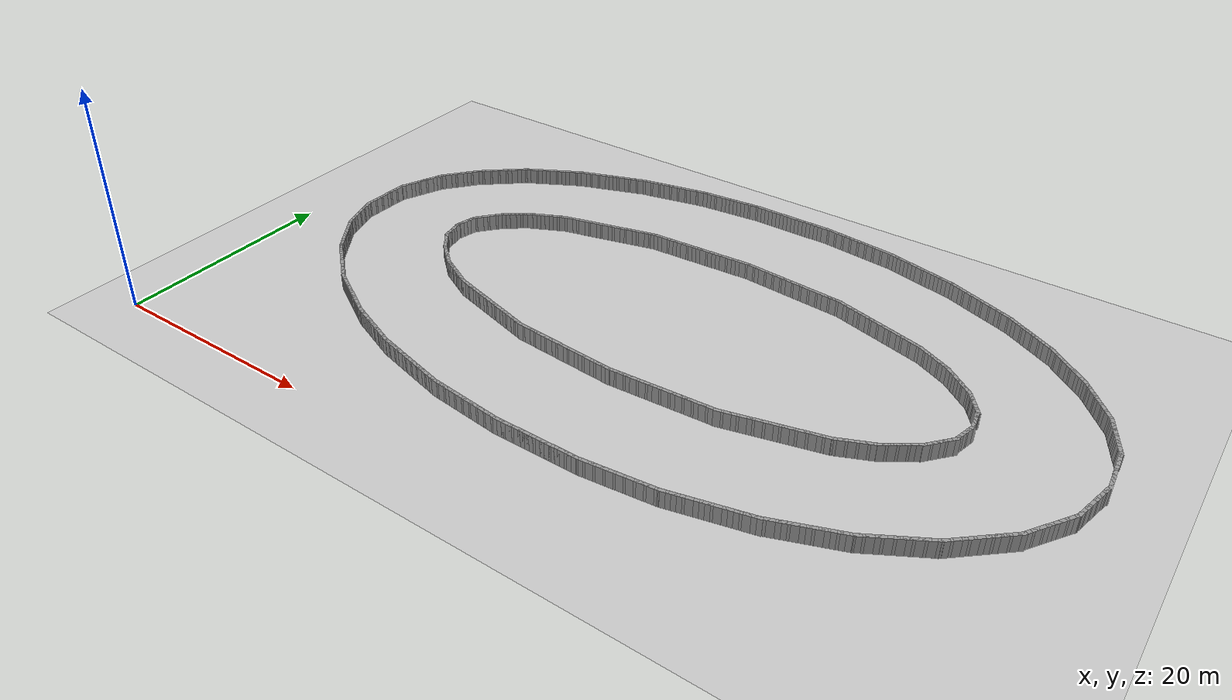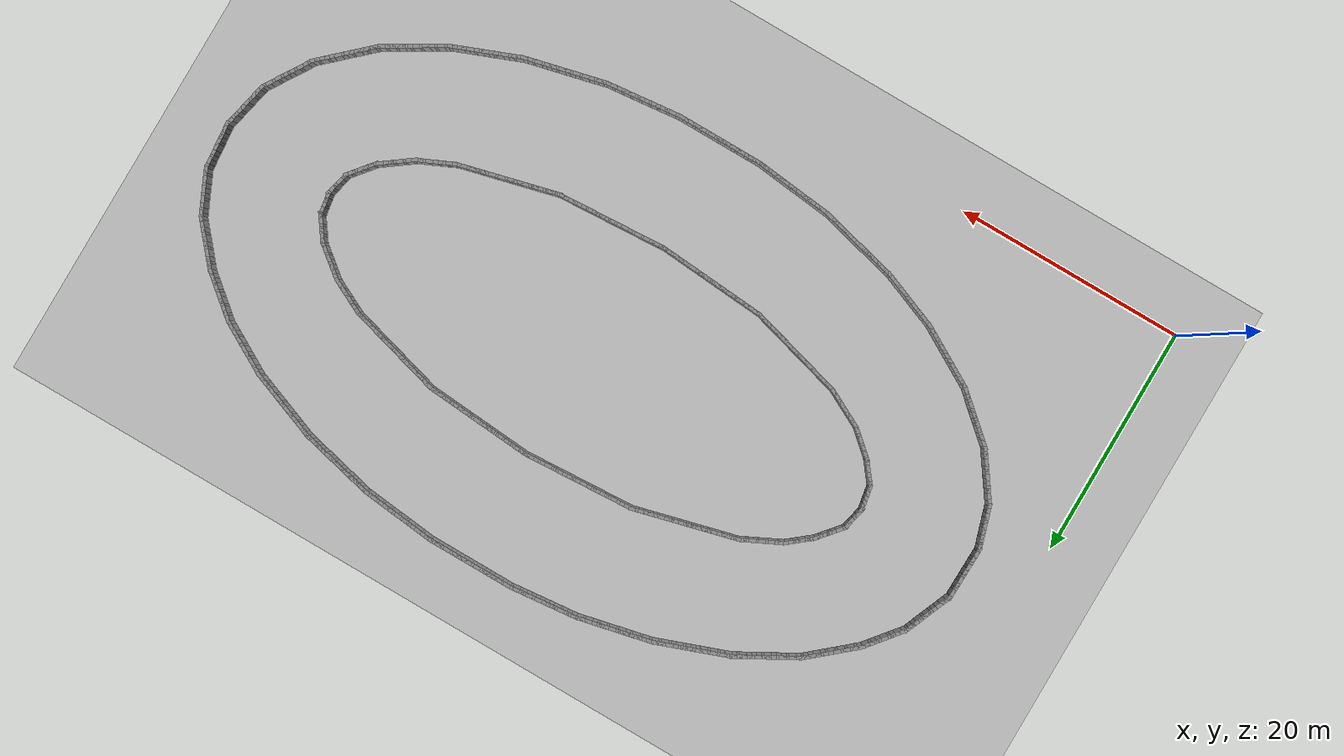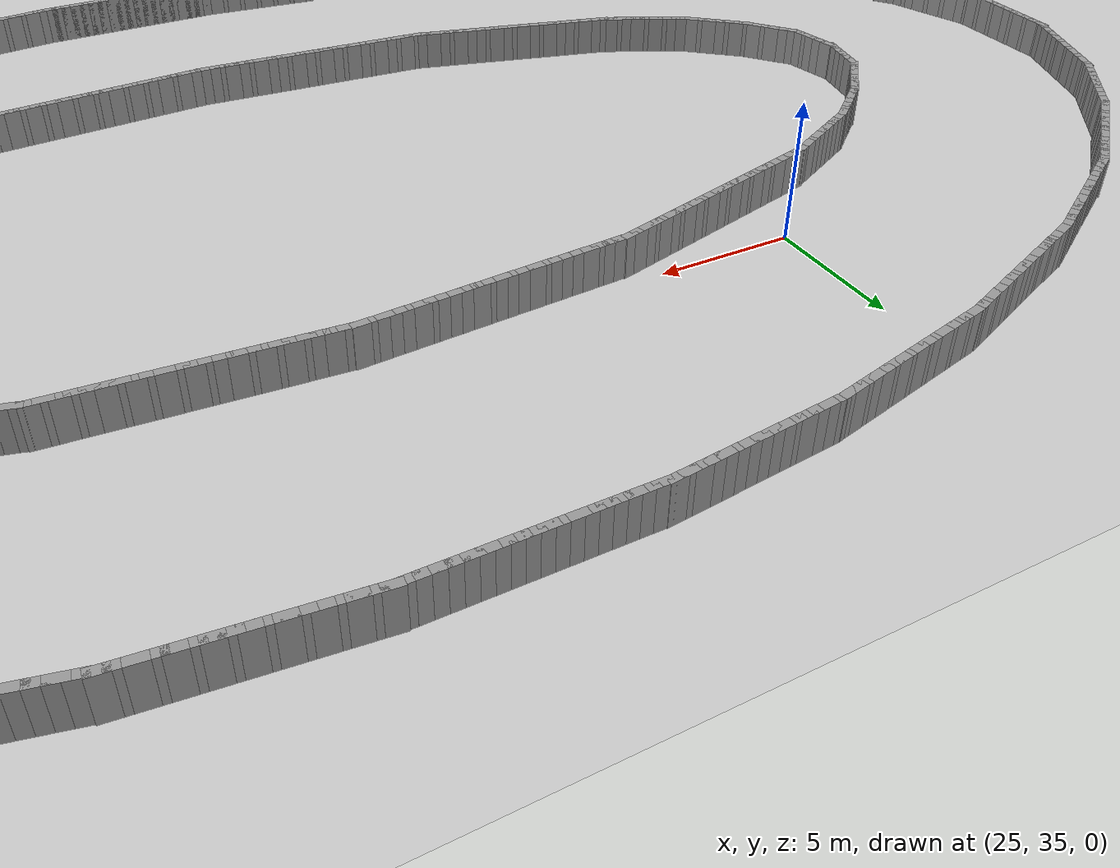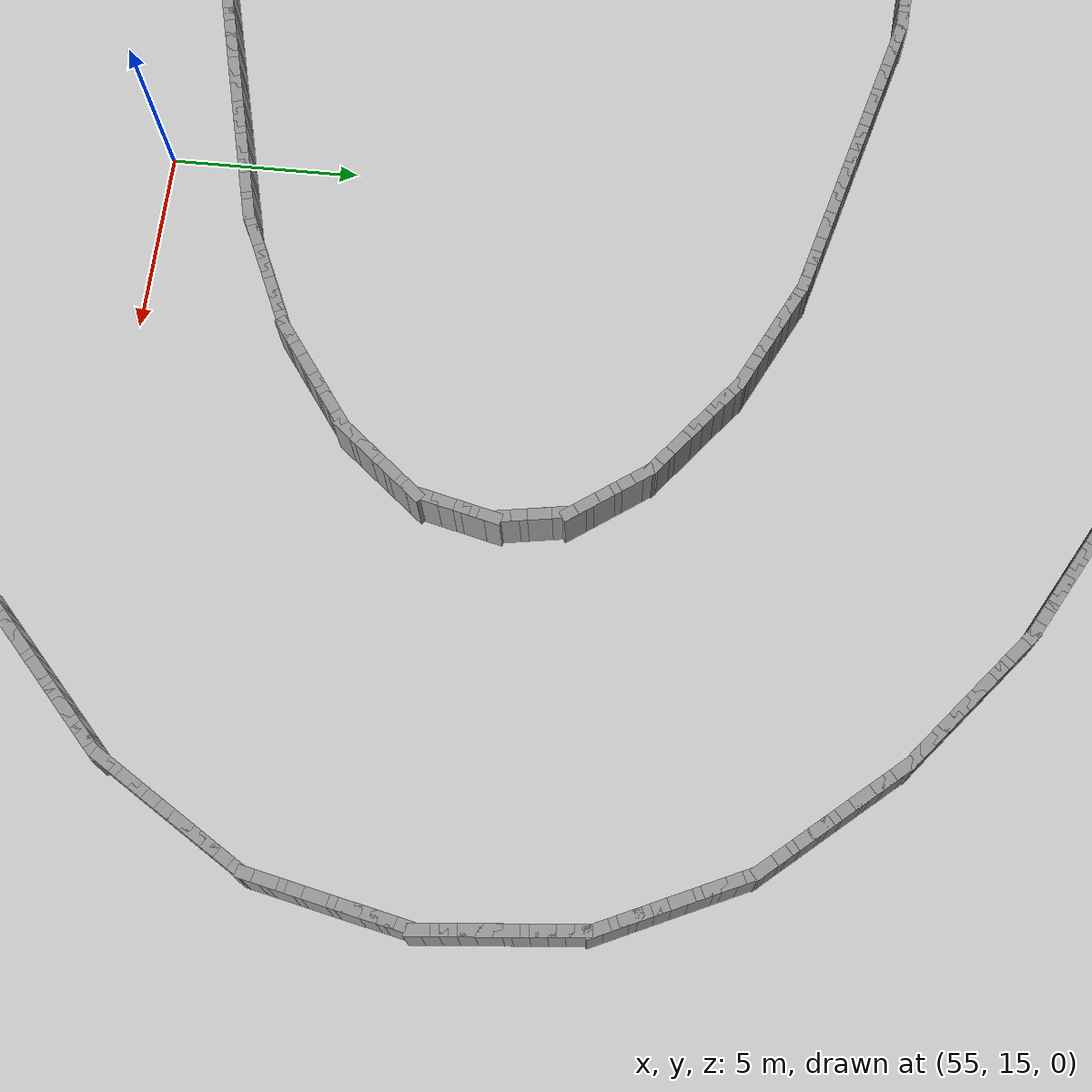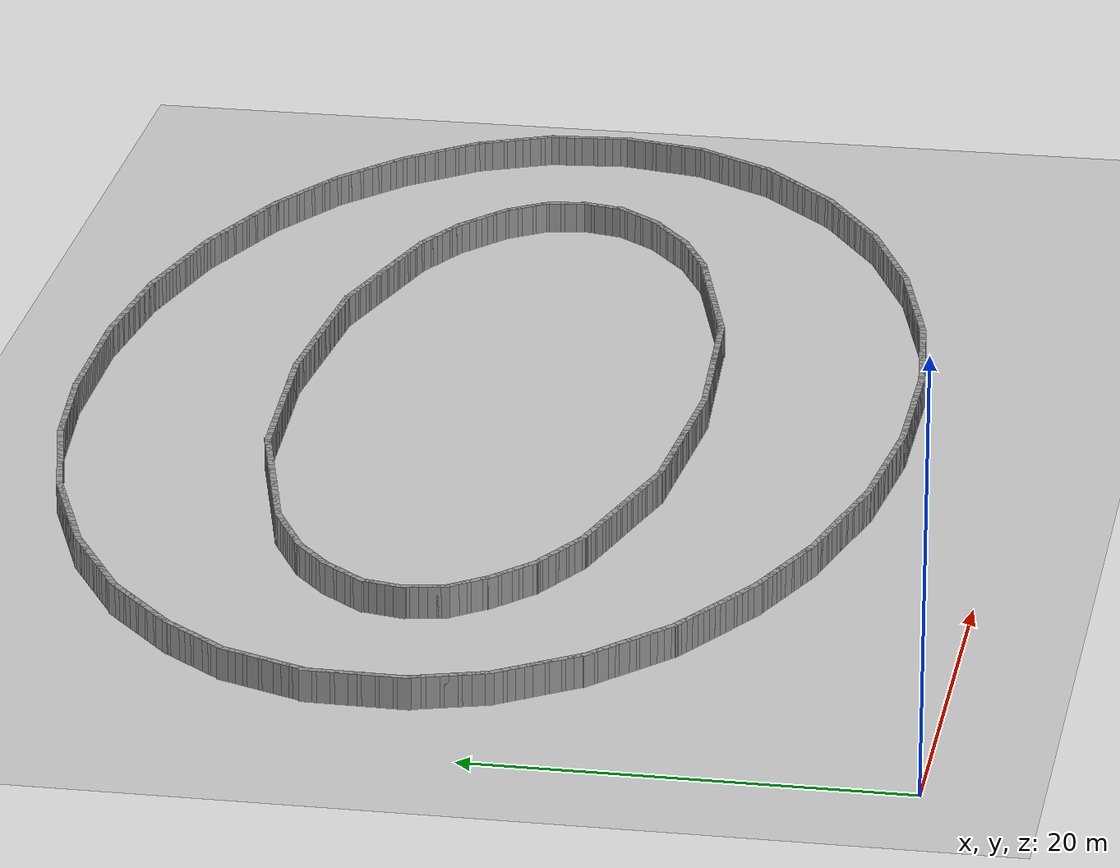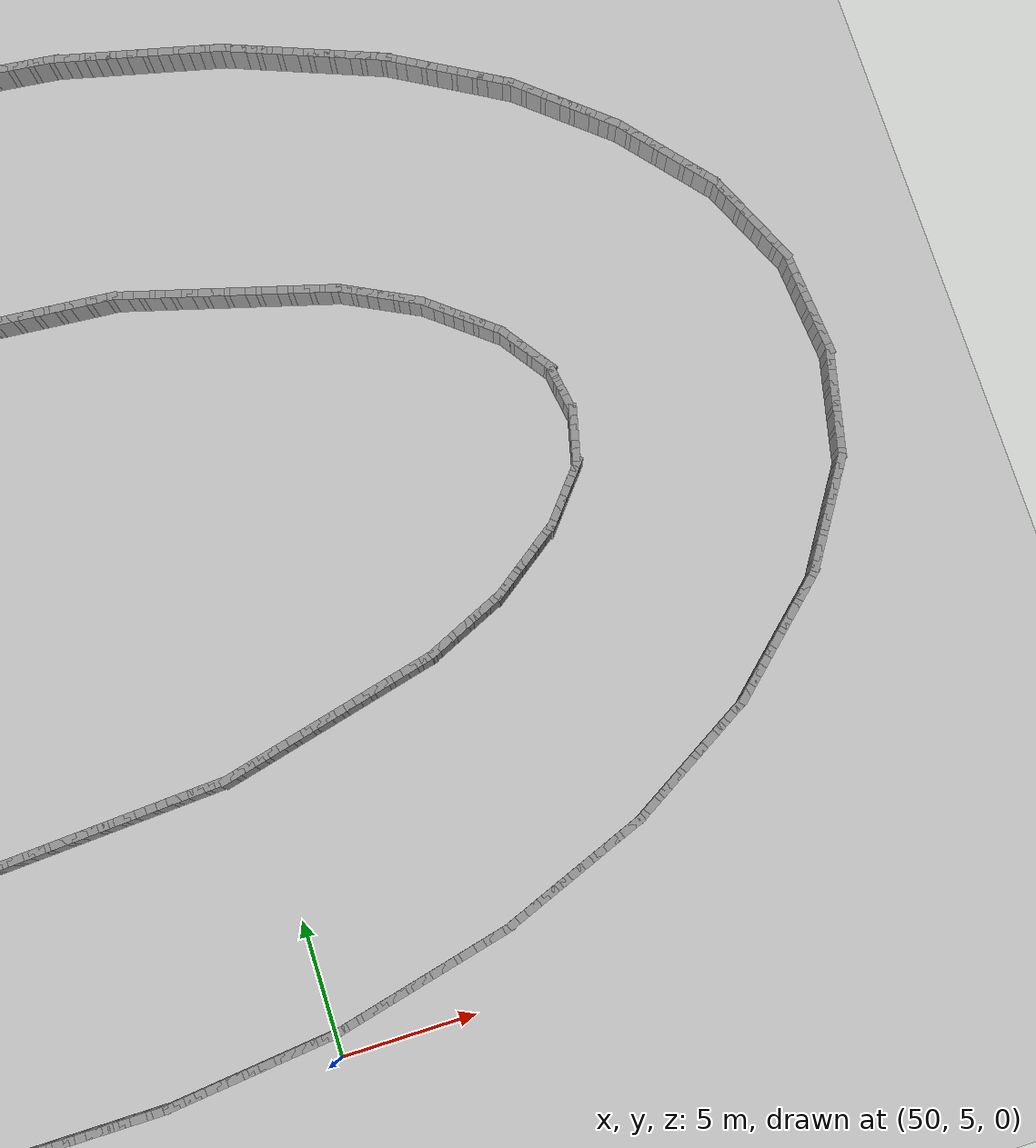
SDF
<?xml version="1.0" ?>
<sdf version="1.5">
  <world name="ellipse_loop">
    <include><uri>model://sun</uri></include>
    <include><uri>model://ground_plane</uri></include>
    <model name="curbL_0">
      <static>true</static>
      <pose>5.326 27.536 0.750 0 0 -1.592</pose>
      <link name="link">
        <collision name="col">
          <geometry><box><size>0.600 0.300 1.500</size></box></geometry>
        </collision>
        <visual name="vis">
          <geometry><box><size>0.600 0.300 1.500</size></box></geometry>
          <material>
            <ambient>0.6 0.6 0.6 1</ambient>
            <diffuse>0.6 0.6 0.6 1</diffuse>
          </material>
        </visual>
      </link>
    </model>
    <model name="curbL_1">
      <static>true</static>
      <pose>5.318 27.137 0.750 0 0 -1.592</pose>
      <link name="link">
        <collision name="col">
          <geometry><box><size>0.600 0.300 1.500</size></box></geometry>
        </collision>
        <visual name="vis">
          <geometry><box><size>0.600 0.300 1.500</size></box></geometry>
          <material>
            <ambient>0.6 0.6 0.6 1</ambient>
            <diffuse>0.6 0.6 0.6 1</diffuse>
          </material>
        </visual>
      </link>
    </model>
    <model name="curbL_2">
      <static>true</static>
      <pose>5.309 26.737 0.750 0 0 -1.592</pose>
      <link name="link">
        <collision name="col">
          <geometry><box><size>0.600 0.300 1.500</size></box></geometry>
        </collision>
        <visual name="vis">
          <geometry><box><size>0.600 0.300 1.500</size></box></geometry>
          <material>
            <ambient>0.6 0.6 0.6 1</ambient>
            <diffuse>0.6 0.6 0.6 1</diffuse>
          </material>
        </visual>
      </link>
    </model>
    <model name="curbL_3">
      <static>true</static>
      <pose>5.301 26.337 0.750 0 0 -1.592</pose>
      <link name="link">
        <collision name="col">
          <geometry><box><size>0.600 0.300 1.500</size></box></geometry>
        </collision>
        <visual name="vis">
          <geometry><box><size>0.600 0.300 1.500</size></box></geometry>
          <material>
            <ambient>0.6 0.6 0.6 1</ambient>
            <diffuse>0.6 0.6 0.6 1</diffuse>
          </material>
        </visual>
      </link>
    </model>
    <model name="curbL_4">
      <static>true</static>
      <pose>5.292 25.937 0.750 0 0 -1.592</pose>
      <link name="link">
        <collision name="col">
          <geometry><box><size>0.600 0.300 1.500</size></box></geometry>
        </collision>
        <visual name="vis">
          <geometry><box><size>0.600 0.300 1.500</size></box></geometry>
          <material>
            <ambient>0.6 0.6 0.6 1</ambient>
            <diffuse>0.6 0.6 0.6 1</diffuse>
          </material>
        </visual>
      </link>
    </model>
    <model name="curbL_5">
      <static>true</static>
      <pose>5.284 25.537 0.750 0 0 -1.592</pose>
      <link name="link">
        <collision name="col">
          <geometry><box><size>0.600 0.300 1.500</size></box></geometry>
        </collision>
        <visual name="vis">
          <geometry><box><size>0.600 0.300 1.500</size></box></geometry>
          <material>
            <ambient>0.6 0.6 0.6 1</ambient>
            <diffuse>0.6 0.6 0.6 1</diffuse>
          </material>
        </visual>
      </link>
    </model>
    <model name="curbL_6">
      <static>true</static>
      <pose>5.276 25.137 0.750 0 0 -1.592</pose>
      <link name="link">
        <collision name="col">
          <geometry><box><size>0.600 0.300 1.500</size></box></geometry>
        </collision>
        <visual name="vis">
          <geometry><box><size>0.600 0.300 1.500</size></box></geometry>
          <material>
            <ambient>0.6 0.6 0.6 1</ambient>
            <diffuse>0.6 0.6 0.6 1</diffuse>
          </material>
        </visual>
      </link>
    </model>
    <model name="curbL_7">
      <static>true</static>
      <pose>5.267 24.737 0.750 0 0 -1.592</pose>
      <link name="link">
        <collision name="col">
          <geometry><box><size>0.600 0.300 1.500</size></box></geometry>
        </collision>
        <visual name="vis">
          <geometry><box><size>0.600 0.300 1.500</size></box></geometry>
          <material>
            <ambient>0.6 0.6 0.6 1</ambient>
            <diffuse>0.6 0.6 0.6 1</diffuse>
          </material>
        </visual>
      </link>
    </model>
    <model name="curbL_8">
      <static>true</static>
      <pose>5.259 24.337 0.750 0 0 -1.592</pose>
      <link name="link">
        <collision name="col">
          <geometry><box><size>0.600 0.300 1.500</size></box></geometry>
        </collision>
        <visual name="vis">
          <geometry><box><size>0.600 0.300 1.500</size></box></geometry>
          <material>
            <ambient>0.6 0.6 0.6 1</ambient>
            <diffuse>0.6 0.6 0.6 1</diffuse>
          </material>
        </visual>
      </link>
    </model>
    <model name="curbL_9">
      <static>true</static>
      <pose>5.250 23.937 0.750 0 0 -1.592</pose>
      <link name="link">
        <collision name="col">
          <geometry><box><size>0.600 0.300 1.500</size></box></geometry>
        </collision>
        <visual name="vis">
          <geometry><box><size>0.600 0.300 1.500</size></box></geometry>
          <material>
            <ambient>0.6 0.6 0.6 1</ambient>
            <diffuse>0.6 0.6 0.6 1</diffuse>
          </material>
        </visual>
      </link>
    </model>
    <model name="curbL_10">
      <static>true</static>
      <pose>5.242 23.537 0.750 0 0 -1.592</pose>
      <link name="link">
        <collision name="col">
          <geometry><box><size>0.600 0.300 1.500</size></box></geometry>
        </collision>
        <visual name="vis">
          <geometry><box><size>0.600 0.300 1.500</size></box></geometry>
          <material>
            <ambient>0.6 0.6 0.6 1</ambient>
            <diffuse>0.6 0.6 0.6 1</diffuse>
          </material>
        </visual>
      </link>
    </model>
    <model name="curbL_11">
      <static>true</static>
      <pose>5.233 23.137 0.750 0 0 -1.592</pose>
      <link name="link">
        <collision name="col">
          <geometry><box><size>0.600 0.300 1.500</size></box></geometry>
        </collision>
        <visual name="vis">
          <geometry><box><size>0.600 0.300 1.500</size></box></geometry>
          <material>
            <ambient>0.6 0.6 0.6 1</ambient>
            <diffuse>0.6 0.6 0.6 1</diffuse>
          </material>
        </visual>
      </link>
    </model>
    <model name="curbL_12">
      <static>true</static>
      <pose>5.338 22.754 0.750 0 0 -1.268</pose>
      <link name="link">
        <collision name="col">
          <geometry><box><size>0.600 0.300 1.500</size></box></geometry>
        </collision>
        <visual name="vis">
          <geometry><box><size>0.600 0.300 1.500</size></box></geometry>
          <material>
            <ambient>0.6 0.6 0.6 1</ambient>
            <diffuse>0.6 0.6 0.6 1</diffuse>
          </material>
        </visual>
      </link>
    </model>
    <model name="curbL_13">
      <static>true</static>
      <pose>5.458 22.372 0.750 0 0 -1.268</pose>
      <link name="link">
        <collision name="col">
          <geometry><box><size>0.600 0.300 1.500</size></box></geometry>
        </collision>
        <visual name="vis">
          <geometry><box><size>0.600 0.300 1.500</size></box></geometry>
          <material>
            <ambient>0.6 0.6 0.6 1</ambient>
            <diffuse>0.6 0.6 0.6 1</diffuse>
          </material>
        </visual>
      </link>
    </model>
    <model name="curbL_14">
      <static>true</static>
      <pose>5.577 21.990 0.750 0 0 -1.268</pose>
      <link name="link">
        <collision name="col">
          <geometry><box><size>0.600 0.300 1.500</size></box></geometry>
        </collision>
        <visual name="vis">
          <geometry><box><size>0.600 0.300 1.500</size></box></geometry>
          <material>
            <ambient>0.6 0.6 0.6 1</ambient>
            <diffuse>0.6 0.6 0.6 1</diffuse>
          </material>
        </visual>
      </link>
    </model>
    <model name="curbL_15">
      <static>true</static>
      <pose>5.697 21.608 0.750 0 0 -1.268</pose>
      <link name="link">
        <collision name="col">
          <geometry><box><size>0.600 0.300 1.500</size></box></geometry>
        </collision>
        <visual name="vis">
          <geometry><box><size>0.600 0.300 1.500</size></box></geometry>
          <material>
            <ambient>0.6 0.6 0.6 1</ambient>
            <diffuse>0.6 0.6 0.6 1</diffuse>
          </material>
        </visual>
      </link>
    </model>
    <model name="curbL_16">
      <static>true</static>
      <pose>5.816 21.227 0.750 0 0 -1.268</pose>
      <link name="link">
        <collision name="col">
          <geometry><box><size>0.600 0.300 1.500</size></box></geometry>
        </collision>
        <visual name="vis">
          <geometry><box><size>0.600 0.300 1.500</size></box></geometry>
          <material>
            <ambient>0.6 0.6 0.6 1</ambient>
            <diffuse>0.6 0.6 0.6 1</diffuse>
          </material>
        </visual>
      </link>
    </model>
    <model name="curbL_17">
      <static>true</static>
      <pose>5.936 20.845 0.750 0 0 -1.268</pose>
      <link name="link">
        <collision name="col">
          <geometry><box><size>0.600 0.300 1.500</size></box></geometry>
        </collision>
        <visual name="vis">
          <geometry><box><size>0.600 0.300 1.500</size></box></geometry>
          <material>
            <ambient>0.6 0.6 0.6 1</ambient>
            <diffuse>0.6 0.6 0.6 1</diffuse>
          </material>
        </visual>
      </link>
    </model>
    <model name="curbL_18">
      <static>true</static>
      <pose>6.055 20.463 0.750 0 0 -1.268</pose>
      <link name="link">
        <collision name="col">
          <geometry><box><size>0.600 0.300 1.500</size></box></geometry>
        </collision>
        <visual name="vis">
          <geometry><box><size>0.600 0.300 1.500</size></box></geometry>
          <material>
            <ambient>0.6 0.6 0.6 1</ambient>
            <diffuse>0.6 0.6 0.6 1</diffuse>
          </material>
        </visual>
      </link>
    </model>
    <model name="curbL_19">
      <static>true</static>
      <pose>6.174 20.081 0.750 0 0 -1.268</pose>
      <link name="link">
        <collision name="col">
          <geometry><box><size>0.600 0.300 1.500</size></box></geometry>
        </collision>
        <visual name="vis">
          <geometry><box><size>0.600 0.300 1.500</size></box></geometry>
          <material>
            <ambient>0.6 0.6 0.6 1</ambient>
            <diffuse>0.6 0.6 0.6 1</diffuse>
          </material>
        </visual>
      </link>
    </model>
    <model name="curbL_20">
      <static>true</static>
      <pose>6.294 19.700 0.750 0 0 -1.268</pose>
      <link name="link">
        <collision name="col">
          <geometry><box><size>0.600 0.300 1.500</size></box></geometry>
        </collision>
        <visual name="vis">
          <geometry><box><size>0.600 0.300 1.500</size></box></geometry>
          <material>
            <ambient>0.6 0.6 0.6 1</ambient>
            <diffuse>0.6 0.6 0.6 1</diffuse>
          </material>
        </visual>
      </link>
    </model>
    <model name="curbL_21">
      <static>true</static>
      <pose>6.488 19.354 0.750 0 0 -0.961</pose>
      <link name="link">
        <collision name="col">
          <geometry><box><size>0.600 0.300 1.500</size></box></geometry>
        </collision>
        <visual name="vis">
          <geometry><box><size>0.600 0.300 1.500</size></box></geometry>
          <material>
            <ambient>0.6 0.6 0.6 1</ambient>
            <diffuse>0.6 0.6 0.6 1</diffuse>
          </material>
        </visual>
      </link>
    </model>
    <model name="curbL_22">
      <static>true</static>
      <pose>6.717 19.027 0.750 0 0 -0.961</pose>
      <link name="link">
        <collision name="col">
          <geometry><box><size>0.600 0.300 1.500</size></box></geometry>
        </collision>
        <visual name="vis">
          <geometry><box><size>0.600 0.300 1.500</size></box></geometry>
          <material>
            <ambient>0.6 0.6 0.6 1</ambient>
            <diffuse>0.6 0.6 0.6 1</diffuse>
          </material>
        </visual>
      </link>
    </model>
    <model name="curbL_23">
      <static>true</static>
      <pose>6.946 18.699 0.750 0 0 -0.961</pose>
      <link name="link">
        <collision name="col">
          <geometry><box><size>0.600 0.300 1.500</size></box></geometry>
        </collision>
        <visual name="vis">
          <geometry><box><size>0.600 0.300 1.500</size></box></geometry>
          <material>
            <ambient>0.6 0.6 0.6 1</ambient>
            <diffuse>0.6 0.6 0.6 1</diffuse>
          </material>
        </visual>
      </link>
    </model>
    <model name="curbL_24">
      <static>true</static>
      <pose>7.175 18.371 0.750 0 0 -0.961</pose>
      <link name="link">
        <collision name="col">
          <geometry><box><size>0.600 0.300 1.500</size></box></geometry>
        </collision>
        <visual name="vis">
          <geometry><box><size>0.600 0.300 1.500</size></box></geometry>
          <material>
            <ambient>0.6 0.6 0.6 1</ambient>
            <diffuse>0.6 0.6 0.6 1</diffuse>
          </material>
        </visual>
      </link>
    </model>
    <model name="curbL_25">
      <static>true</static>
      <pose>7.404 18.043 0.750 0 0 -0.961</pose>
      <link name="link">
        <collision name="col">
          <geometry><box><size>0.600 0.300 1.500</size></box></geometry>
        </collision>
        <visual name="vis">
          <geometry><box><size>0.600 0.300 1.500</size></box></geometry>
          <material>
            <ambient>0.6 0.6 0.6 1</ambient>
            <diffuse>0.6 0.6 0.6 1</diffuse>
          </material>
        </visual>
      </link>
    </model>
    <model name="curbL_26">
      <static>true</static>
      <pose>7.633 17.715 0.750 0 0 -0.961</pose>
      <link name="link">
        <collision name="col">
          <geometry><box><size>0.600 0.300 1.500</size></box></geometry>
        </collision>
        <visual name="vis">
          <geometry><box><size>0.600 0.300 1.500</size></box></geometry>
          <material>
            <ambient>0.6 0.6 0.6 1</ambient>
            <diffuse>0.6 0.6 0.6 1</diffuse>
          </material>
        </visual>
      </link>
    </model>
    <model name="curbL_27">
      <static>true</static>
      <pose>7.863 17.387 0.750 0 0 -0.961</pose>
      <link name="link">
        <collision name="col">
          <geometry><box><size>0.600 0.300 1.500</size></box></geometry>
        </collision>
        <visual name="vis">
          <geometry><box><size>0.600 0.300 1.500</size></box></geometry>
          <material>
            <ambient>0.6 0.6 0.6 1</ambient>
            <diffuse>0.6 0.6 0.6 1</diffuse>
          </material>
        </visual>
      </link>
    </model>
    <model name="curbL_28">
      <static>true</static>
      <pose>8.092 17.059 0.750 0 0 -0.961</pose>
      <link name="link">
        <collision name="col">
          <geometry><box><size>0.600 0.300 1.500</size></box></geometry>
        </collision>
        <visual name="vis">
          <geometry><box><size>0.600 0.300 1.500</size></box></geometry>
          <material>
            <ambient>0.6 0.6 0.6 1</ambient>
            <diffuse>0.6 0.6 0.6 1</diffuse>
          </material>
        </visual>
      </link>
    </model>
    <model name="curbL_29">
      <static>true</static>
      <pose>8.321 16.732 0.750 0 0 -0.961</pose>
      <link name="link">
        <collision name="col">
          <geometry><box><size>0.600 0.300 1.500</size></box></geometry>
        </collision>
        <visual name="vis">
          <geometry><box><size>0.600 0.300 1.500</size></box></geometry>
          <material>
            <ambient>0.6 0.6 0.6 1</ambient>
            <diffuse>0.6 0.6 0.6 1</diffuse>
          </material>
        </visual>
      </link>
    </model>
    <model name="curbL_30">
      <static>true</static>
      <pose>8.550 16.404 0.750 0 0 -0.961</pose>
      <link name="link">
        <collision name="col">
          <geometry><box><size>0.600 0.300 1.500</size></box></geometry>
        </collision>
        <visual name="vis">
          <geometry><box><size>0.600 0.300 1.500</size></box></geometry>
          <material>
            <ambient>0.6 0.6 0.6 1</ambient>
            <diffuse>0.6 0.6 0.6 1</diffuse>
          </material>
        </visual>
      </link>
    </model>
    <model name="curbL_31">
      <static>true</static>
      <pose>8.779 16.076 0.750 0 0 -0.961</pose>
      <link name="link">
        <collision name="col">
          <geometry><box><size>0.600 0.300 1.500</size></box></geometry>
        </collision>
        <visual name="vis">
          <geometry><box><size>0.600 0.300 1.500</size></box></geometry>
          <material>
            <ambient>0.6 0.6 0.6 1</ambient>
            <diffuse>0.6 0.6 0.6 1</diffuse>
          </material>
        </visual>
      </link>
    </model>
    <model name="curbL_32">
      <static>true</static>
      <pose>9.017 15.756 0.750 0 0 -0.722</pose>
      <link name="link">
        <collision name="col">
          <geometry><box><size>0.600 0.300 1.500</size></box></geometry>
        </collision>
        <visual name="vis">
          <geometry><box><size>0.600 0.300 1.500</size></box></geometry>
          <material>
            <ambient>0.6 0.6 0.6 1</ambient>
            <diffuse>0.6 0.6 0.6 1</diffuse>
          </material>
        </visual>
      </link>
    </model>
    <model name="curbL_33">
      <static>true</static>
      <pose>9.318 15.492 0.750 0 0 -0.722</pose>
      <link name="link">
        <collision name="col">
          <geometry><box><size>0.600 0.300 1.500</size></box></geometry>
        </collision>
        <visual name="vis">
          <geometry><box><size>0.600 0.300 1.500</size></box></geometry>
          <material>
            <ambient>0.6 0.6 0.6 1</ambient>
            <diffuse>0.6 0.6 0.6 1</diffuse>
          </material>
        </visual>
      </link>
    </model>
    <model name="curbL_34">
      <static>true</static>
      <pose>9.618 15.227 0.750 0 0 -0.722</pose>
      <link name="link">
        <collision name="col">
          <geometry><box><size>0.600 0.300 1.500</size></box></geometry>
        </collision>
        <visual name="vis">
          <geometry><box><size>0.600 0.300 1.500</size></box></geometry>
          <material>
            <ambient>0.6 0.6 0.6 1</ambient>
            <diffuse>0.6 0.6 0.6 1</diffuse>
          </material>
        </visual>
      </link>
    </model>
    <model name="curbL_35">
      <static>true</static>
      <pose>9.918 14.963 0.750 0 0 -0.722</pose>
      <link name="link">
        <collision name="col">
          <geometry><box><size>0.600 0.300 1.500</size></box></geometry>
        </collision>
        <visual name="vis">
          <geometry><box><size>0.600 0.300 1.500</size></box></geometry>
          <material>
            <ambient>0.6 0.6 0.6 1</ambient>
            <diffuse>0.6 0.6 0.6 1</diffuse>
          </material>
        </visual>
      </link>
    </model>
    <model name="curbL_36">
      <static>true</static>
      <pose>10.218 14.699 0.750 0 0 -0.722</pose>
      <link name="link">
        <collision name="col">
          <geometry><box><size>0.600 0.300 1.500</size></box></geometry>
        </collision>
        <visual name="vis">
          <geometry><box><size>0.600 0.300 1.500</size></box></geometry>
          <material>
            <ambient>0.6 0.6 0.6 1</ambient>
            <diffuse>0.6 0.6 0.6 1</diffuse>
          </material>
        </visual>
      </link>
    </model>
    <model name="curbL_37">
      <static>true</static>
      <pose>10.518 14.434 0.750 0 0 -0.722</pose>
      <link name="link">
        <collision name="col">
          <geometry><box><size>0.600 0.300 1.500</size></box></geometry>
        </collision>
        <visual name="vis">
          <geometry><box><size>0.600 0.300 1.500</size></box></geometry>
          <material>
            <ambient>0.6 0.6 0.6 1</ambient>
            <diffuse>0.6 0.6 0.6 1</diffuse>
          </material>
        </visual>
      </link>
    </model>
    <model name="curbL_38">
      <static>true</static>
      <pose>10.819 14.170 0.750 0 0 -0.722</pose>
      <link name="link">
        <collision name="col">
          <geometry><box><size>0.600 0.300 1.500</size></box></geometry>
        </collision>
        <visual name="vis">
          <geometry><box><size>0.600 0.300 1.500</size></box></geometry>
          <material>
            <ambient>0.6 0.6 0.6 1</ambient>
            <diffuse>0.6 0.6 0.6 1</diffuse>
          </material>
        </visual>
      </link>
    </model>
    <model name="curbL_39">
      <static>true</static>
      <pose>11.119 13.906 0.750 0 0 -0.722</pose>
      <link name="link">
        <collision name="col">
          <geometry><box><size>0.600 0.300 1.500</size></box></geometry>
        </collision>
        <visual name="vis">
          <geometry><box><size>0.600 0.300 1.500</size></box></geometry>
          <material>
            <ambient>0.6 0.6 0.6 1</ambient>
            <diffuse>0.6 0.6 0.6 1</diffuse>
          </material>
        </visual>
      </link>
    </model>
    <model name="curbL_40">
      <static>true</static>
      <pose>11.419 13.641 0.750 0 0 -0.722</pose>
      <link name="link">
        <collision name="col">
          <geometry><box><size>0.600 0.300 1.500</size></box></geometry>
        </collision>
        <visual name="vis">
          <geometry><box><size>0.600 0.300 1.500</size></box></geometry>
          <material>
            <ambient>0.6 0.6 0.6 1</ambient>
            <diffuse>0.6 0.6 0.6 1</diffuse>
          </material>
        </visual>
      </link>
    </model>
    <model name="curbL_41">
      <static>true</static>
      <pose>11.719 13.377 0.750 0 0 -0.722</pose>
      <link name="link">
        <collision name="col">
          <geometry><box><size>0.600 0.300 1.500</size></box></geometry>
        </collision>
        <visual name="vis">
          <geometry><box><size>0.600 0.300 1.500</size></box></geometry>
          <material>
            <ambient>0.6 0.6 0.6 1</ambient>
            <diffuse>0.6 0.6 0.6 1</diffuse>
          </material>
        </visual>
      </link>
    </model>
    <model name="curbL_42">
      <static>true</static>
      <pose>12.019 13.113 0.750 0 0 -0.722</pose>
      <link name="link">
        <collision name="col">
          <geometry><box><size>0.600 0.300 1.500</size></box></geometry>
        </collision>
        <visual name="vis">
          <geometry><box><size>0.600 0.300 1.500</size></box></geometry>
          <material>
            <ambient>0.6 0.6 0.6 1</ambient>
            <diffuse>0.6 0.6 0.6 1</diffuse>
          </material>
        </visual>
      </link>
    </model>
    <model name="curbL_43">
      <static>true</static>
      <pose>12.320 12.848 0.750 0 0 -0.722</pose>
      <link name="link">
        <collision name="col">
          <geometry><box><size>0.600 0.300 1.500</size></box></geometry>
        </collision>
        <visual name="vis">
          <geometry><box><size>0.600 0.300 1.500</size></box></geometry>
          <material>
            <ambient>0.6 0.6 0.6 1</ambient>
            <diffuse>0.6 0.6 0.6 1</diffuse>
          </material>
        </visual>
      </link>
    </model>
    <model name="curbL_44">
      <static>true</static>
      <pose>12.620 12.584 0.750 0 0 -0.722</pose>
      <link name="link">
        <collision name="col">
          <geometry><box><size>0.600 0.300 1.500</size></box></geometry>
        </collision>
        <visual name="vis">
          <geometry><box><size>0.600 0.300 1.500</size></box></geometry>
          <material>
            <ambient>0.6 0.6 0.6 1</ambient>
            <diffuse>0.6 0.6 0.6 1</diffuse>
          </material>
        </visual>
      </link>
    </model>
    <model name="curbL_45">
      <static>true</static>
      <pose>12.939 12.346 0.750 0 0 -0.520</pose>
      <link name="link">
        <collision name="col">
          <geometry><box><size>0.600 0.300 1.500</size></box></geometry>
        </collision>
        <visual name="vis">
          <geometry><box><size>0.600 0.300 1.500</size></box></geometry>
          <material>
            <ambient>0.6 0.6 0.6 1</ambient>
            <diffuse>0.6 0.6 0.6 1</diffuse>
          </material>
        </visual>
      </link>
    </model>
    <model name="curbL_46">
      <static>true</static>
      <pose>13.286 12.147 0.750 0 0 -0.520</pose>
      <link name="link">
        <collision name="col">
          <geometry><box><size>0.600 0.300 1.500</size></box></geometry>
        </collision>
        <visual name="vis">
          <geometry><box><size>0.600 0.300 1.500</size></box></geometry>
          <material>
            <ambient>0.6 0.6 0.6 1</ambient>
            <diffuse>0.6 0.6 0.6 1</diffuse>
          </material>
        </visual>
      </link>
    </model>
    <model name="curbL_47">
      <static>true</static>
      <pose>13.633 11.948 0.750 0 0 -0.520</pose>
      <link name="link">
        <collision name="col">
          <geometry><box><size>0.600 0.300 1.500</size></box></geometry>
        </collision>
        <visual name="vis">
          <geometry><box><size>0.600 0.300 1.500</size></box></geometry>
          <material>
            <ambient>0.6 0.6 0.6 1</ambient>
            <diffuse>0.6 0.6 0.6 1</diffuse>
          </material>
        </visual>
      </link>
    </model>
    <model name="curbL_48">
      <static>true</static>
      <pose>13.980 11.749 0.750 0 0 -0.520</pose>
      <link name="link">
        <collision name="col">
          <geometry><box><size>0.600 0.300 1.500</size></box></geometry>
        </collision>
        <visual name="vis">
          <geometry><box><size>0.600 0.300 1.500</size></box></geometry>
          <material>
            <ambient>0.6 0.6 0.6 1</ambient>
            <diffuse>0.6 0.6 0.6 1</diffuse>
          </material>
        </visual>
      </link>
    </model>
    <model name="curbL_49">
      <static>true</static>
      <pose>14.327 11.550 0.750 0 0 -0.520</pose>
      <link name="link">
        <collision name="col">
          <geometry><box><size>0.600 0.300 1.500</size></box></geometry>
        </collision>
        <visual name="vis">
          <geometry><box><size>0.600 0.300 1.500</size></box></geometry>
          <material>
            <ambient>0.6 0.6 0.6 1</ambient>
            <diffuse>0.6 0.6 0.6 1</diffuse>
          </material>
        </visual>
      </link>
    </model>
    <model name="curbL_50">
      <static>true</static>
      <pose>14.674 11.351 0.750 0 0 -0.520</pose>
      <link name="link">
        <collision name="col">
          <geometry><box><size>0.600 0.300 1.500</size></box></geometry>
        </collision>
        <visual name="vis">
          <geometry><box><size>0.600 0.300 1.500</size></box></geometry>
          <material>
            <ambient>0.6 0.6 0.6 1</ambient>
            <diffuse>0.6 0.6 0.6 1</diffuse>
          </material>
        </visual>
      </link>
    </model>
    <model name="curbL_51">
      <static>true</static>
      <pose>15.021 11.152 0.750 0 0 -0.520</pose>
      <link name="link">
        <collision name="col">
          <geometry><box><size>0.600 0.300 1.500</size></box></geometry>
        </collision>
        <visual name="vis">
          <geometry><box><size>0.600 0.300 1.500</size></box></geometry>
          <material>
            <ambient>0.6 0.6 0.6 1</ambient>
            <diffuse>0.6 0.6 0.6 1</diffuse>
          </material>
        </visual>
      </link>
    </model>
    <model name="curbL_52">
      <static>true</static>
      <pose>15.368 10.953 0.750 0 0 -0.520</pose>
      <link name="link">
        <collision name="col">
          <geometry><box><size>0.600 0.300 1.500</size></box></geometry>
        </collision>
        <visual name="vis">
          <geometry><box><size>0.600 0.300 1.500</size></box></geometry>
          <material>
            <ambient>0.6 0.6 0.6 1</ambient>
            <diffuse>0.6 0.6 0.6 1</diffuse>
          </material>
        </visual>
      </link>
    </model>
    <model name="curbL_53">
      <static>true</static>
      <pose>15.715 10.754 0.750 0 0 -0.520</pose>
      <link name="link">
        <collision name="col">
          <geometry><box><size>0.600 0.300 1.500</size></box></geometry>
        </collision>
        <visual name="vis">
          <geometry><box><size>0.600 0.300 1.500</size></box></geometry>
          <material>
            <ambient>0.6 0.6 0.6 1</ambient>
            <diffuse>0.6 0.6 0.6 1</diffuse>
          </material>
        </visual>
      </link>
    </model>
    <model name="curbL_54">
      <static>true</static>
      <pose>16.062 10.555 0.750 0 0 -0.520</pose>
      <link name="link">
        <collision name="col">
          <geometry><box><size>0.600 0.300 1.500</size></box></geometry>
        </collision>
        <visual name="vis">
          <geometry><box><size>0.600 0.300 1.500</size></box></geometry>
          <material>
            <ambient>0.6 0.6 0.6 1</ambient>
            <diffuse>0.6 0.6 0.6 1</diffuse>
          </material>
        </visual>
      </link>
    </model>
    <model name="curbL_55">
      <static>true</static>
      <pose>16.409 10.357 0.750 0 0 -0.520</pose>
      <link name="link">
        <collision name="col">
          <geometry><box><size>0.600 0.300 1.500</size></box></geometry>
        </collision>
        <visual name="vis">
          <geometry><box><size>0.600 0.300 1.500</size></box></geometry>
          <material>
            <ambient>0.6 0.6 0.6 1</ambient>
            <diffuse>0.6 0.6 0.6 1</diffuse>
          </material>
        </visual>
      </link>
    </model>
    <model name="curbL_56">
      <static>true</static>
      <pose>16.756 10.158 0.750 0 0 -0.520</pose>
      <link name="link">
        <collision name="col">
          <geometry><box><size>0.600 0.300 1.500</size></box></geometry>
        </collision>
        <visual name="vis">
          <geometry><box><size>0.600 0.300 1.500</size></box></geometry>
          <material>
            <ambient>0.6 0.6 0.6 1</ambient>
            <diffuse>0.6 0.6 0.6 1</diffuse>
          </material>
        </visual>
      </link>
    </model>
    <model name="curbL_57">
      <static>true</static>
      <pose>17.103 9.959 0.750 0 0 -0.520</pose>
      <link name="link">
        <collision name="col">
          <geometry><box><size>0.600 0.300 1.500</size></box></geometry>
        </collision>
        <visual name="vis">
          <geometry><box><size>0.600 0.300 1.500</size></box></geometry>
          <material>
            <ambient>0.6 0.6 0.6 1</ambient>
            <diffuse>0.6 0.6 0.6 1</diffuse>
          </material>
        </visual>
      </link>
    </model>
    <model name="curbL_58">
      <static>true</static>
      <pose>17.450 9.760 0.750 0 0 -0.520</pose>
      <link name="link">
        <collision name="col">
          <geometry><box><size>0.600 0.300 1.500</size></box></geometry>
        </collision>
        <visual name="vis">
          <geometry><box><size>0.600 0.300 1.500</size></box></geometry>
          <material>
            <ambient>0.6 0.6 0.6 1</ambient>
            <diffuse>0.6 0.6 0.6 1</diffuse>
          </material>
        </visual>
      </link>
    </model>
    <model name="curbL_59">
      <static>true</static>
      <pose>17.797 9.561 0.750 0 0 -0.520</pose>
      <link name="link">
        <collision name="col">
          <geometry><box><size>0.600 0.300 1.500</size></box></geometry>
        </collision>
        <visual name="vis">
          <geometry><box><size>0.600 0.300 1.500</size></box></geometry>
          <material>
            <ambient>0.6 0.6 0.6 1</ambient>
            <diffuse>0.6 0.6 0.6 1</diffuse>
          </material>
        </visual>
      </link>
    </model>
    <model name="curbL_60">
      <static>true</static>
      <pose>18.167 9.410 0.750 0 0 -0.376</pose>
      <link name="link">
        <collision name="col">
          <geometry><box><size>0.600 0.300 1.500</size></box></geometry>
        </collision>
        <visual name="vis">
          <geometry><box><size>0.600 0.300 1.500</size></box></geometry>
          <material>
            <ambient>0.6 0.6 0.6 1</ambient>
            <diffuse>0.6 0.6 0.6 1</diffuse>
          </material>
        </visual>
      </link>
    </model>
    <model name="curbL_61">
      <static>true</static>
      <pose>18.539 9.263 0.750 0 0 -0.376</pose>
      <link name="link">
        <collision name="col">
          <geometry><box><size>0.600 0.300 1.500</size></box></geometry>
        </collision>
        <visual name="vis">
          <geometry><box><size>0.600 0.300 1.500</size></box></geometry>
          <material>
            <ambient>0.6 0.6 0.6 1</ambient>
            <diffuse>0.6 0.6 0.6 1</diffuse>
          </material>
        </visual>
      </link>
    </model>
    <model name="curbL_62">
      <static>true</static>
      <pose>18.911 9.116 0.750 0 0 -0.376</pose>
      <link name="link">
        <collision name="col">
          <geometry><box><size>0.600 0.300 1.500</size></box></geometry>
        </collision>
        <visual name="vis">
          <geometry><box><size>0.600 0.300 1.500</size></box></geometry>
          <material>
            <ambient>0.6 0.6 0.6 1</ambient>
            <diffuse>0.6 0.6 0.6 1</diffuse>
          </material>
        </visual>
      </link>
    </model>
    <model name="curbL_63">
      <static>true</static>
      <pose>19.283 8.969 0.750 0 0 -0.376</pose>
      <link name="link">
        <collision name="col">
          <geometry><box><size>0.600 0.300 1.500</size></box></geometry>
        </collision>
        <visual name="vis">
          <geometry><box><size>0.600 0.300 1.500</size></box></geometry>
          <material>
            <ambient>0.6 0.6 0.6 1</ambient>
            <diffuse>0.6 0.6 0.6 1</diffuse>
          </material>
        </visual>
      </link>
    </model>
    <model name="curbL_64">
      <static>true</static>
      <pose>19.655 8.822 0.750 0 0 -0.376</pose>
      <link name="link">
        <collision name="col">
          <geometry><box><size>0.600 0.300 1.500</size></box></geometry>
        </collision>
        <visual name="vis">
          <geometry><box><size>0.600 0.300 1.500</size></box></geometry>
          <material>
            <ambient>0.6 0.6 0.6 1</ambient>
            <diffuse>0.6 0.6 0.6 1</diffuse>
          </material>
        </visual>
      </link>
    </model>
    <model name="curbL_65">
      <static>true</static>
      <pose>20.027 8.675 0.750 0 0 -0.376</pose>
      <link name="link">
        <collision name="col">
          <geometry><box><size>0.600 0.300 1.500</size></box></geometry>
        </collision>
        <visual name="vis">
          <geometry><box><size>0.600 0.300 1.500</size></box></geometry>
          <material>
            <ambient>0.6 0.6 0.6 1</ambient>
            <diffuse>0.6 0.6 0.6 1</diffuse>
          </material>
        </visual>
      </link>
    </model>
    <model name="curbL_66">
      <static>true</static>
      <pose>20.399 8.528 0.750 0 0 -0.376</pose>
      <link name="link">
        <collision name="col">
          <geometry><box><size>0.600 0.300 1.500</size></box></geometry>
        </collision>
        <visual name="vis">
          <geometry><box><size>0.600 0.300 1.500</size></box></geometry>
          <material>
            <ambient>0.6 0.6 0.6 1</ambient>
            <diffuse>0.6 0.6 0.6 1</diffuse>
          </material>
        </visual>
      </link>
    </model>
    <model name="curbL_67">
      <static>true</static>
      <pose>20.772 8.381 0.750 0 0 -0.376</pose>
      <link name="link">
        <collision name="col">
          <geometry><box><size>0.600 0.300 1.500</size></box></geometry>
        </collision>
        <visual name="vis">
          <geometry><box><size>0.600 0.300 1.500</size></box></geometry>
          <material>
            <ambient>0.6 0.6 0.6 1</ambient>
            <diffuse>0.6 0.6 0.6 1</diffuse>
          </material>
        </visual>
      </link>
    </model>
    <model name="curbL_68">
      <static>true</static>
      <pose>21.144 8.234 0.750 0 0 -0.376</pose>
      <link name="link">
        <collision name="col">
          <geometry><box><size>0.600 0.300 1.500</size></box></geometry>
        </collision>
        <visual name="vis">
          <geometry><box><size>0.600 0.300 1.500</size></box></geometry>
          <material>
            <ambient>0.6 0.6 0.6 1</ambient>
            <diffuse>0.6 0.6 0.6 1</diffuse>
          </material>
        </visual>
      </link>
    </model>
    <model name="curbL_69">
      <static>true</static>
      <pose>21.516 8.088 0.750 0 0 -0.376</pose>
      <link name="link">
        <collision name="col">
          <geometry><box><size>0.600 0.300 1.500</size></box></geometry>
        </collision>
        <visual name="vis">
          <geometry><box><size>0.600 0.300 1.500</size></box></geometry>
          <material>
            <ambient>0.6 0.6 0.6 1</ambient>
            <diffuse>0.6 0.6 0.6 1</diffuse>
          </material>
        </visual>
      </link>
    </model>
    <model name="curbL_70">
      <static>true</static>
      <pose>21.888 7.941 0.750 0 0 -0.376</pose>
      <link name="link">
        <collision name="col">
          <geometry><box><size>0.600 0.300 1.500</size></box></geometry>
        </collision>
        <visual name="vis">
          <geometry><box><size>0.600 0.300 1.500</size></box></geometry>
          <material>
            <ambient>0.6 0.6 0.6 1</ambient>
            <diffuse>0.6 0.6 0.6 1</diffuse>
          </material>
        </visual>
      </link>
    </model>
    <model name="curbL_71">
      <static>true</static>
      <pose>22.260 7.794 0.750 0 0 -0.376</pose>
      <link name="link">
        <collision name="col">
          <geometry><box><size>0.600 0.300 1.500</size></box></geometry>
        </collision>
        <visual name="vis">
          <geometry><box><size>0.600 0.300 1.500</size></box></geometry>
          <material>
            <ambient>0.6 0.6 0.6 1</ambient>
            <diffuse>0.6 0.6 0.6 1</diffuse>
          </material>
        </visual>
      </link>
    </model>
    <model name="curbL_72">
      <static>true</static>
      <pose>22.632 7.647 0.750 0 0 -0.376</pose>
      <link name="link">
        <collision name="col">
          <geometry><box><size>0.600 0.300 1.500</size></box></geometry>
        </collision>
        <visual name="vis">
          <geometry><box><size>0.600 0.300 1.500</size></box></geometry>
          <material>
            <ambient>0.6 0.6 0.6 1</ambient>
            <diffuse>0.6 0.6 0.6 1</diffuse>
          </material>
        </visual>
      </link>
    </model>
    <model name="curbL_73">
      <static>true</static>
      <pose>23.018 7.543 0.750 0 0 -0.242</pose>
      <link name="link">
        <collision name="col">
          <geometry><box><size>0.600 0.300 1.500</size></box></geometry>
        </collision>
        <visual name="vis">
          <geometry><box><size>0.600 0.300 1.500</size></box></geometry>
          <material>
            <ambient>0.6 0.6 0.6 1</ambient>
            <diffuse>0.6 0.6 0.6 1</diffuse>
          </material>
        </visual>
      </link>
    </model>
    <model name="curbL_74">
      <static>true</static>
      <pose>23.406 7.448 0.750 0 0 -0.242</pose>
      <link name="link">
        <collision name="col">
          <geometry><box><size>0.600 0.300 1.500</size></box></geometry>
        </collision>
        <visual name="vis">
          <geometry><box><size>0.600 0.300 1.500</size></box></geometry>
          <material>
            <ambient>0.6 0.6 0.6 1</ambient>
            <diffuse>0.6 0.6 0.6 1</diffuse>
          </material>
        </visual>
      </link>
    </model>
    <model name="curbL_75">
      <static>true</static>
      <pose>23.794 7.352 0.750 0 0 -0.242</pose>
      <link name="link">
        <collision name="col">
          <geometry><box><size>0.600 0.300 1.500</size></box></geometry>
        </collision>
        <visual name="vis">
          <geometry><box><size>0.600 0.300 1.500</size></box></geometry>
          <material>
            <ambient>0.6 0.6 0.6 1</ambient>
            <diffuse>0.6 0.6 0.6 1</diffuse>
          </material>
        </visual>
      </link>
    </model>
    <model name="curbL_76">
      <static>true</static>
      <pose>24.183 7.256 0.750 0 0 -0.242</pose>
      <link name="link">
        <collision name="col">
          <geometry><box><size>0.600 0.300 1.500</size></box></geometry>
        </collision>
        <visual name="vis">
          <geometry><box><size>0.600 0.300 1.500</size></box></geometry>
          <material>
            <ambient>0.6 0.6 0.6 1</ambient>
            <diffuse>0.6 0.6 0.6 1</diffuse>
          </material>
        </visual>
      </link>
    </model>
    <model name="curbL_77">
      <static>true</static>
      <pose>24.571 7.160 0.750 0 0 -0.242</pose>
      <link name="link">
        <collision name="col">
          <geometry><box><size>0.600 0.300 1.500</size></box></geometry>
        </collision>
        <visual name="vis">
          <geometry><box><size>0.600 0.300 1.500</size></box></geometry>
          <material>
            <ambient>0.6 0.6 0.6 1</ambient>
            <diffuse>0.6 0.6 0.6 1</diffuse>
          </material>
        </visual>
      </link>
    </model>
    <model name="curbL_78">
      <static>true</static>
      <pose>24.959 7.064 0.750 0 0 -0.242</pose>
      <link name="link">
        <collision name="col">
          <geometry><box><size>0.600 0.300 1.500</size></box></geometry>
        </collision>
        <visual name="vis">
          <geometry><box><size>0.600 0.300 1.500</size></box></geometry>
          <material>
            <ambient>0.6 0.6 0.6 1</ambient>
            <diffuse>0.6 0.6 0.6 1</diffuse>
          </material>
        </visual>
      </link>
    </model>
    <model name="curbL_79">
      <static>true</static>
      <pose>25.348 6.968 0.750 0 0 -0.242</pose>
      <link name="link">
        <collision name="col">
          <geometry><box><size>0.600 0.300 1.500</size></box></geometry>
        </collision>
        <visual name="vis">
          <geometry><box><size>0.600 0.300 1.500</size></box></geometry>
          <material>
            <ambient>0.6 0.6 0.6 1</ambient>
            <diffuse>0.6 0.6 0.6 1</diffuse>
          </material>
        </visual>
      </link>
    </model>
    <model name="curbL_80">
      <static>true</static>
      <pose>25.736 6.873 0.750 0 0 -0.242</pose>
      <link name="link">
        <collision name="col">
          <geometry><box><size>0.600 0.300 1.500</size></box></geometry>
        </collision>
        <visual name="vis">
          <geometry><box><size>0.600 0.300 1.500</size></box></geometry>
          <material>
            <ambient>0.6 0.6 0.6 1</ambient>
            <diffuse>0.6 0.6 0.6 1</diffuse>
          </material>
        </visual>
      </link>
    </model>
    <model name="curbL_81">
      <static>true</static>
      <pose>26.124 6.777 0.750 0 0 -0.242</pose>
      <link name="link">
        <collision name="col">
          <geometry><box><size>0.600 0.300 1.500</size></box></geometry>
        </collision>
        <visual name="vis">
          <geometry><box><size>0.600 0.300 1.500</size></box></geometry>
          <material>
            <ambient>0.6 0.6 0.6 1</ambient>
            <diffuse>0.6 0.6 0.6 1</diffuse>
          </material>
        </visual>
      </link>
    </model>
    <model name="curbL_82">
      <static>true</static>
      <pose>26.513 6.681 0.750 0 0 -0.242</pose>
      <link name="link">
        <collision name="col">
          <geometry><box><size>0.600 0.300 1.500</size></box></geometry>
        </collision>
        <visual name="vis">
          <geometry><box><size>0.600 0.300 1.500</size></box></geometry>
          <material>
            <ambient>0.6 0.6 0.6 1</ambient>
            <diffuse>0.6 0.6 0.6 1</diffuse>
          </material>
        </visual>
      </link>
    </model>
    <model name="curbL_83">
      <static>true</static>
      <pose>26.901 6.585 0.750 0 0 -0.242</pose>
      <link name="link">
        <collision name="col">
          <geometry><box><size>0.600 0.300 1.500</size></box></geometry>
        </collision>
        <visual name="vis">
          <geometry><box><size>0.600 0.300 1.500</size></box></geometry>
          <material>
            <ambient>0.6 0.6 0.6 1</ambient>
            <diffuse>0.6 0.6 0.6 1</diffuse>
          </material>
        </visual>
      </link>
    </model>
    <model name="curbL_84">
      <static>true</static>
      <pose>27.290 6.489 0.750 0 0 -0.242</pose>
      <link name="link">
        <collision name="col">
          <geometry><box><size>0.600 0.300 1.500</size></box></geometry>
        </collision>
        <visual name="vis">
          <geometry><box><size>0.600 0.300 1.500</size></box></geometry>
          <material>
            <ambient>0.6 0.6 0.6 1</ambient>
            <diffuse>0.6 0.6 0.6 1</diffuse>
          </material>
        </visual>
      </link>
    </model>
    <model name="curbL_85">
      <static>true</static>
      <pose>27.678 6.393 0.750 0 0 -0.242</pose>
      <link name="link">
        <collision name="col">
          <geometry><box><size>0.600 0.300 1.500</size></box></geometry>
        </collision>
        <visual name="vis">
          <geometry><box><size>0.600 0.300 1.500</size></box></geometry>
          <material>
            <ambient>0.6 0.6 0.6 1</ambient>
            <diffuse>0.6 0.6 0.6 1</diffuse>
          </material>
        </visual>
      </link>
    </model>
    <model name="curbL_86">
      <static>true</static>
      <pose>28.066 6.298 0.750 0 0 -0.242</pose>
      <link name="link">
        <collision name="col">
          <geometry><box><size>0.600 0.300 1.500</size></box></geometry>
        </collision>
        <visual name="vis">
          <geometry><box><size>0.600 0.300 1.500</size></box></geometry>
          <material>
            <ambient>0.6 0.6 0.6 1</ambient>
            <diffuse>0.6 0.6 0.6 1</diffuse>
          </material>
        </visual>
      </link>
    </model>
    <model name="curbL_87">
      <static>true</static>
      <pose>28.455 6.202 0.750 0 0 -0.242</pose>
      <link name="link">
        <collision name="col">
          <geometry><box><size>0.600 0.300 1.500</size></box></geometry>
        </collision>
        <visual name="vis">
          <geometry><box><size>0.600 0.300 1.500</size></box></geometry>
          <material>
            <ambient>0.6 0.6 0.6 1</ambient>
            <diffuse>0.6 0.6 0.6 1</diffuse>
          </material>
        </visual>
      </link>
    </model>
    <model name="curbL_88">
      <static>true</static>
      <pose>28.843 6.106 0.750 0 0 -0.242</pose>
      <link name="link">
        <collision name="col">
          <geometry><box><size>0.600 0.300 1.500</size></box></geometry>
        </collision>
        <visual name="vis">
          <geometry><box><size>0.600 0.300 1.500</size></box></geometry>
          <material>
            <ambient>0.6 0.6 0.6 1</ambient>
            <diffuse>0.6 0.6 0.6 1</diffuse>
          </material>
        </visual>
      </link>
    </model>
    <model name="curbL_89">
      <static>true</static>
      <pose>29.231 6.010 0.750 0 0 -0.242</pose>
      <link name="link">
        <collision name="col">
          <geometry><box><size>0.600 0.300 1.500</size></box></geometry>
        </collision>
        <visual name="vis">
          <geometry><box><size>0.600 0.300 1.500</size></box></geometry>
          <material>
            <ambient>0.6 0.6 0.6 1</ambient>
            <diffuse>0.6 0.6 0.6 1</diffuse>
          </material>
        </visual>
      </link>
    </model>
    <model name="curbL_90">
      <static>true</static>
      <pose>29.621 5.920 0.750 0 0 -0.109</pose>
      <link name="link">
        <collision name="col">
          <geometry><box><size>0.600 0.300 1.500</size></box></geometry>
        </collision>
        <visual name="vis">
          <geometry><box><size>0.600 0.300 1.500</size></box></geometry>
          <material>
            <ambient>0.6 0.6 0.6 1</ambient>
            <diffuse>0.6 0.6 0.6 1</diffuse>
          </material>
        </visual>
      </link>
    </model>
    <model name="curbL_91">
      <static>true</static>
      <pose>30.018 5.877 0.750 0 0 -0.109</pose>
      <link name="link">
        <collision name="col">
          <geometry><box><size>0.600 0.300 1.500</size></box></geometry>
        </collision>
        <visual name="vis">
          <geometry><box><size>0.600 0.300 1.500</size></box></geometry>
          <material>
            <ambient>0.6 0.6 0.6 1</ambient>
            <diffuse>0.6 0.6 0.6 1</diffuse>
          </material>
        </visual>
      </link>
    </model>
    <model name="curbL_92">
      <static>true</static>
      <pose>30.416 5.833 0.750 0 0 -0.109</pose>
      <link name="link">
        <collision name="col">
          <geometry><box><size>0.600 0.300 1.500</size></box></geometry>
        </collision>
        <visual name="vis">
          <geometry><box><size>0.600 0.300 1.500</size></box></geometry>
          <material>
            <ambient>0.6 0.6 0.6 1</ambient>
            <diffuse>0.6 0.6 0.6 1</diffuse>
          </material>
        </visual>
      </link>
    </model>
    <model name="curbL_93">
      <static>true</static>
      <pose>30.814 5.790 0.750 0 0 -0.109</pose>
      <link name="link">
        <collision name="col">
          <geometry><box><size>0.600 0.300 1.500</size></box></geometry>
        </collision>
        <visual name="vis">
          <geometry><box><size>0.600 0.300 1.500</size></box></geometry>
          <material>
            <ambient>0.6 0.6 0.6 1</ambient>
            <diffuse>0.6 0.6 0.6 1</diffuse>
          </material>
        </visual>
      </link>
    </model>
    <model name="curbL_94">
      <static>true</static>
      <pose>31.211 5.746 0.750 0 0 -0.109</pose>
      <link name="link">
        <collision name="col">
          <geometry><box><size>0.600 0.300 1.500</size></box></geometry>
        </collision>
        <visual name="vis">
          <geometry><box><size>0.600 0.300 1.500</size></box></geometry>
          <material>
            <ambient>0.6 0.6 0.6 1</ambient>
            <diffuse>0.6 0.6 0.6 1</diffuse>
          </material>
        </visual>
      </link>
    </model>
    <model name="curbL_95">
      <static>true</static>
      <pose>31.609 5.702 0.750 0 0 -0.109</pose>
      <link name="link">
        <collision name="col">
          <geometry><box><size>0.600 0.300 1.500</size></box></geometry>
        </collision>
        <visual name="vis">
          <geometry><box><size>0.600 0.300 1.500</size></box></geometry>
          <material>
            <ambient>0.6 0.6 0.6 1</ambient>
            <diffuse>0.6 0.6 0.6 1</diffuse>
          </material>
        </visual>
      </link>
    </model>
    <model name="curbL_96">
      <static>true</static>
      <pose>32.006 5.659 0.750 0 0 -0.109</pose>
      <link name="link">
        <collision name="col">
          <geometry><box><size>0.600 0.300 1.500</size></box></geometry>
        </collision>
        <visual name="vis">
          <geometry><box><size>0.600 0.300 1.500</size></box></geometry>
          <material>
            <ambient>0.6 0.6 0.6 1</ambient>
            <diffuse>0.6 0.6 0.6 1</diffuse>
          </material>
        </visual>
      </link>
    </model>
    <model name="curbL_97">
      <static>true</static>
      <pose>32.404 5.615 0.750 0 0 -0.109</pose>
      <link name="link">
        <collision name="col">
          <geometry><box><size>0.600 0.300 1.500</size></box></geometry>
        </collision>
        <visual name="vis">
          <geometry><box><size>0.600 0.300 1.500</size></box></geometry>
          <material>
            <ambient>0.6 0.6 0.6 1</ambient>
            <diffuse>0.6 0.6 0.6 1</diffuse>
          </material>
        </visual>
      </link>
    </model>
    <model name="curbL_98">
      <static>true</static>
      <pose>32.802 5.572 0.750 0 0 -0.109</pose>
      <link name="link">
        <collision name="col">
          <geometry><box><size>0.600 0.300 1.500</size></box></geometry>
        </collision>
        <visual name="vis">
          <geometry><box><size>0.600 0.300 1.500</size></box></geometry>
          <material>
            <ambient>0.6 0.6 0.6 1</ambient>
            <diffuse>0.6 0.6 0.6 1</diffuse>
          </material>
        </visual>
      </link>
    </model>
    <model name="curbL_99">
      <static>true</static>
      <pose>33.199 5.528 0.750 0 0 -0.109</pose>
      <link name="link">
        <collision name="col">
          <geometry><box><size>0.600 0.300 1.500</size></box></geometry>
        </collision>
        <visual name="vis">
          <geometry><box><size>0.600 0.300 1.500</size></box></geometry>
          <material>
            <ambient>0.6 0.6 0.6 1</ambient>
            <diffuse>0.6 0.6 0.6 1</diffuse>
          </material>
        </visual>
      </link>
    </model>
    <model name="curbL_100">
      <static>true</static>
      <pose>33.597 5.485 0.750 0 0 -0.109</pose>
      <link name="link">
        <collision name="col">
          <geometry><box><size>0.600 0.300 1.500</size></box></geometry>
        </collision>
        <visual name="vis">
          <geometry><box><size>0.600 0.300 1.500</size></box></geometry>
          <material>
            <ambient>0.6 0.6 0.6 1</ambient>
            <diffuse>0.6 0.6 0.6 1</diffuse>
          </material>
        </visual>
      </link>
    </model>
    <model name="curbL_101">
      <static>true</static>
      <pose>33.995 5.441 0.750 0 0 -0.109</pose>
      <link name="link">
        <collision name="col">
          <geometry><box><size>0.600 0.300 1.500</size></box></geometry>
        </collision>
        <visual name="vis">
          <geometry><box><size>0.600 0.300 1.500</size></box></geometry>
          <material>
            <ambient>0.6 0.6 0.6 1</ambient>
            <diffuse>0.6 0.6 0.6 1</diffuse>
          </material>
        </visual>
      </link>
    </model>
    <model name="curbL_102">
      <static>true</static>
      <pose>34.392 5.398 0.750 0 0 -0.109</pose>
      <link name="link">
        <collision name="col">
          <geometry><box><size>0.600 0.300 1.500</size></box></geometry>
        </collision>
        <visual name="vis">
          <geometry><box><size>0.600 0.300 1.500</size></box></geometry>
          <material>
            <ambient>0.6 0.6 0.6 1</ambient>
            <diffuse>0.6 0.6 0.6 1</diffuse>
          </material>
        </visual>
      </link>
    </model>
    <model name="curbL_103">
      <static>true</static>
      <pose>34.790 5.354 0.750 0 0 -0.109</pose>
      <link name="link">
        <collision name="col">
          <geometry><box><size>0.600 0.300 1.500</size></box></geometry>
        </collision>
        <visual name="vis">
          <geometry><box><size>0.600 0.300 1.500</size></box></geometry>
          <material>
            <ambient>0.6 0.6 0.6 1</ambient>
            <diffuse>0.6 0.6 0.6 1</diffuse>
          </material>
        </visual>
      </link>
    </model>
    <model name="curbL_104">
      <static>true</static>
      <pose>35.187 5.311 0.750 0 0 -0.109</pose>
      <link name="link">
        <collision name="col">
          <geometry><box><size>0.600 0.300 1.500</size></box></geometry>
        </collision>
        <visual name="vis">
          <geometry><box><size>0.600 0.300 1.500</size></box></geometry>
          <material>
            <ambient>0.6 0.6 0.6 1</ambient>
            <diffuse>0.6 0.6 0.6 1</diffuse>
          </material>
        </visual>
      </link>
    </model>
    <model name="curbL_105">
      <static>true</static>
      <pose>35.585 5.267 0.750 0 0 -0.109</pose>
      <link name="link">
        <collision name="col">
          <geometry><box><size>0.600 0.300 1.500</size></box></geometry>
        </collision>
        <visual name="vis">
          <geometry><box><size>0.600 0.300 1.500</size></box></geometry>
          <material>
            <ambient>0.6 0.6 0.6 1</ambient>
            <diffuse>0.6 0.6 0.6 1</diffuse>
          </material>
        </visual>
      </link>
    </model>
    <model name="curbL_106">
      <static>true</static>
      <pose>35.983 5.224 0.750 0 0 -0.109</pose>
      <link name="link">
        <collision name="col">
          <geometry><box><size>0.600 0.300 1.500</size></box></geometry>
        </collision>
        <visual name="vis">
          <geometry><box><size>0.600 0.300 1.500</size></box></geometry>
          <material>
            <ambient>0.6 0.6 0.6 1</ambient>
            <diffuse>0.6 0.6 0.6 1</diffuse>
          </material>
        </visual>
      </link>
    </model>
    <model name="curbL_107">
      <static>true</static>
      <pose>36.381 5.191 0.750 0 0 0.000</pose>
      <link name="link">
        <collision name="col">
          <geometry><box><size>0.600 0.300 1.500</size></box></geometry>
        </collision>
        <visual name="vis">
          <geometry><box><size>0.600 0.300 1.500</size></box></geometry>
          <material>
            <ambient>0.6 0.6 0.6 1</ambient>
            <diffuse>0.6 0.6 0.6 1</diffuse>
          </material>
        </visual>
      </link>
    </model>
    <model name="curbL_108">
      <static>true</static>
      <pose>36.781 5.191 0.750 0 0 0.000</pose>
      <link name="link">
        <collision name="col">
          <geometry><box><size>0.600 0.300 1.500</size></box></geometry>
        </collision>
        <visual name="vis">
          <geometry><box><size>0.600 0.300 1.500</size></box></geometry>
          <material>
            <ambient>0.6 0.6 0.6 1</ambient>
            <diffuse>0.6 0.6 0.6 1</diffuse>
          </material>
        </visual>
      </link>
    </model>
    <model name="curbL_109">
      <static>true</static>
      <pose>37.181 5.191 0.750 0 0 0.000</pose>
      <link name="link">
        <collision name="col">
          <geometry><box><size>0.600 0.300 1.500</size></box></geometry>
        </collision>
        <visual name="vis">
          <geometry><box><size>0.600 0.300 1.500</size></box></geometry>
          <material>
            <ambient>0.6 0.6 0.6 1</ambient>
            <diffuse>0.6 0.6 0.6 1</diffuse>
          </material>
        </visual>
      </link>
    </model>
    <model name="curbL_110">
      <static>true</static>
      <pose>37.581 5.191 0.750 0 0 0.000</pose>
      <link name="link">
        <collision name="col">
          <geometry><box><size>0.600 0.300 1.500</size></box></geometry>
        </collision>
        <visual name="vis">
          <geometry><box><size>0.600 0.300 1.500</size></box></geometry>
          <material>
            <ambient>0.6 0.6 0.6 1</ambient>
            <diffuse>0.6 0.6 0.6 1</diffuse>
          </material>
        </visual>
      </link>
    </model>
    <model name="curbL_111">
      <static>true</static>
      <pose>37.981 5.191 0.750 0 0 0.000</pose>
      <link name="link">
        <collision name="col">
          <geometry><box><size>0.600 0.300 1.500</size></box></geometry>
        </collision>
        <visual name="vis">
          <geometry><box><size>0.600 0.300 1.500</size></box></geometry>
          <material>
            <ambient>0.6 0.6 0.6 1</ambient>
            <diffuse>0.6 0.6 0.6 1</diffuse>
          </material>
        </visual>
      </link>
    </model>
    <model name="curbL_112">
      <static>true</static>
      <pose>38.381 5.191 0.750 0 0 0.000</pose>
      <link name="link">
        <collision name="col">
          <geometry><box><size>0.600 0.300 1.500</size></box></geometry>
        </collision>
        <visual name="vis">
          <geometry><box><size>0.600 0.300 1.500</size></box></geometry>
          <material>
            <ambient>0.6 0.6 0.6 1</ambient>
            <diffuse>0.6 0.6 0.6 1</diffuse>
          </material>
        </visual>
      </link>
    </model>
    <model name="curbL_113">
      <static>true</static>
      <pose>38.781 5.191 0.750 0 0 0.000</pose>
      <link name="link">
        <collision name="col">
          <geometry><box><size>0.600 0.300 1.500</size></box></geometry>
        </collision>
        <visual name="vis">
          <geometry><box><size>0.600 0.300 1.500</size></box></geometry>
          <material>
            <ambient>0.6 0.6 0.6 1</ambient>
            <diffuse>0.6 0.6 0.6 1</diffuse>
          </material>
        </visual>
      </link>
    </model>
    <model name="curbL_114">
      <static>true</static>
      <pose>39.181 5.191 0.750 0 0 0.000</pose>
      <link name="link">
        <collision name="col">
          <geometry><box><size>0.600 0.300 1.500</size></box></geometry>
        </collision>
        <visual name="vis">
          <geometry><box><size>0.600 0.300 1.500</size></box></geometry>
          <material>
            <ambient>0.6 0.6 0.6 1</ambient>
            <diffuse>0.6 0.6 0.6 1</diffuse>
          </material>
        </visual>
      </link>
    </model>
    <model name="curbL_115">
      <static>true</static>
      <pose>39.581 5.191 0.750 0 0 0.000</pose>
      <link name="link">
        <collision name="col">
          <geometry><box><size>0.600 0.300 1.500</size></box></geometry>
        </collision>
        <visual name="vis">
          <geometry><box><size>0.600 0.300 1.500</size></box></geometry>
          <material>
            <ambient>0.6 0.6 0.6 1</ambient>
            <diffuse>0.6 0.6 0.6 1</diffuse>
          </material>
        </visual>
      </link>
    </model>
    <model name="curbL_116">
      <static>true</static>
      <pose>39.981 5.191 0.750 0 0 0.000</pose>
      <link name="link">
        <collision name="col">
          <geometry><box><size>0.600 0.300 1.500</size></box></geometry>
        </collision>
        <visual name="vis">
          <geometry><box><size>0.600 0.300 1.500</size></box></geometry>
          <material>
            <ambient>0.6 0.6 0.6 1</ambient>
            <diffuse>0.6 0.6 0.6 1</diffuse>
          </material>
        </visual>
      </link>
    </model>
    <model name="curbL_117">
      <static>true</static>
      <pose>40.381 5.191 0.750 0 0 0.000</pose>
      <link name="link">
        <collision name="col">
          <geometry><box><size>0.600 0.300 1.500</size></box></geometry>
        </collision>
        <visual name="vis">
          <geometry><box><size>0.600 0.300 1.500</size></box></geometry>
          <material>
            <ambient>0.6 0.6 0.6 1</ambient>
            <diffuse>0.6 0.6 0.6 1</diffuse>
          </material>
        </visual>
      </link>
    </model>
    <model name="curbL_118">
      <static>true</static>
      <pose>40.781 5.191 0.750 0 0 0.000</pose>
      <link name="link">
        <collision name="col">
          <geometry><box><size>0.600 0.300 1.500</size></box></geometry>
        </collision>
        <visual name="vis">
          <geometry><box><size>0.600 0.300 1.500</size></box></geometry>
          <material>
            <ambient>0.6 0.6 0.6 1</ambient>
            <diffuse>0.6 0.6 0.6 1</diffuse>
          </material>
        </visual>
      </link>
    </model>
    <model name="curbL_119">
      <static>true</static>
      <pose>41.181 5.191 0.750 0 0 0.000</pose>
      <link name="link">
        <collision name="col">
          <geometry><box><size>0.600 0.300 1.500</size></box></geometry>
        </collision>
        <visual name="vis">
          <geometry><box><size>0.600 0.300 1.500</size></box></geometry>
          <material>
            <ambient>0.6 0.6 0.6 1</ambient>
            <diffuse>0.6 0.6 0.6 1</diffuse>
          </material>
        </visual>
      </link>
    </model>
    <model name="curbL_120">
      <static>true</static>
      <pose>41.581 5.191 0.750 0 0 0.000</pose>
      <link name="link">
        <collision name="col">
          <geometry><box><size>0.600 0.300 1.500</size></box></geometry>
        </collision>
        <visual name="vis">
          <geometry><box><size>0.600 0.300 1.500</size></box></geometry>
          <material>
            <ambient>0.6 0.6 0.6 1</ambient>
            <diffuse>0.6 0.6 0.6 1</diffuse>
          </material>
        </visual>
      </link>
    </model>
    <model name="curbL_121">
      <static>true</static>
      <pose>41.981 5.191 0.750 0 0 0.000</pose>
      <link name="link">
        <collision name="col">
          <geometry><box><size>0.600 0.300 1.500</size></box></geometry>
        </collision>
        <visual name="vis">
          <geometry><box><size>0.600 0.300 1.500</size></box></geometry>
          <material>
            <ambient>0.6 0.6 0.6 1</ambient>
            <diffuse>0.6 0.6 0.6 1</diffuse>
          </material>
        </visual>
      </link>
    </model>
    <model name="curbL_122">
      <static>true</static>
      <pose>42.381 5.191 0.750 0 0 0.000</pose>
      <link name="link">
        <collision name="col">
          <geometry><box><size>0.600 0.300 1.500</size></box></geometry>
        </collision>
        <visual name="vis">
          <geometry><box><size>0.600 0.300 1.500</size></box></geometry>
          <material>
            <ambient>0.6 0.6 0.6 1</ambient>
            <diffuse>0.6 0.6 0.6 1</diffuse>
          </material>
        </visual>
      </link>
    </model>
    <model name="curbL_123">
      <static>true</static>
      <pose>42.781 5.191 0.750 0 0 0.000</pose>
      <link name="link">
        <collision name="col">
          <geometry><box><size>0.600 0.300 1.500</size></box></geometry>
        </collision>
        <visual name="vis">
          <geometry><box><size>0.600 0.300 1.500</size></box></geometry>
          <material>
            <ambient>0.6 0.6 0.6 1</ambient>
            <diffuse>0.6 0.6 0.6 1</diffuse>
          </material>
        </visual>
      </link>
    </model>
    <model name="curbL_124">
      <static>true</static>
      <pose>43.181 5.191 0.750 0 0 0.000</pose>
      <link name="link">
        <collision name="col">
          <geometry><box><size>0.600 0.300 1.500</size></box></geometry>
        </collision>
        <visual name="vis">
          <geometry><box><size>0.600 0.300 1.500</size></box></geometry>
          <material>
            <ambient>0.6 0.6 0.6 1</ambient>
            <diffuse>0.6 0.6 0.6 1</diffuse>
          </material>
        </visual>
      </link>
    </model>
    <model name="curbL_125">
      <static>true</static>
      <pose>43.581 5.191 0.750 0 0 0.000</pose>
      <link name="link">
        <collision name="col">
          <geometry><box><size>0.600 0.300 1.500</size></box></geometry>
        </collision>
        <visual name="vis">
          <geometry><box><size>0.600 0.300 1.500</size></box></geometry>
          <material>
            <ambient>0.6 0.6 0.6 1</ambient>
            <diffuse>0.6 0.6 0.6 1</diffuse>
          </material>
        </visual>
      </link>
    </model>
    <model name="curbL_126">
      <static>true</static>
      <pose>43.980 5.216 0.750 0 0 0.106</pose>
      <link name="link">
        <collision name="col">
          <geometry><box><size>0.600 0.300 1.500</size></box></geometry>
        </collision>
        <visual name="vis">
          <geometry><box><size>0.600 0.300 1.500</size></box></geometry>
          <material>
            <ambient>0.6 0.6 0.6 1</ambient>
            <diffuse>0.6 0.6 0.6 1</diffuse>
          </material>
        </visual>
      </link>
    </model>
    <model name="curbL_127">
      <static>true</static>
      <pose>44.377 5.259 0.750 0 0 0.106</pose>
      <link name="link">
        <collision name="col">
          <geometry><box><size>0.600 0.300 1.500</size></box></geometry>
        </collision>
        <visual name="vis">
          <geometry><box><size>0.600 0.300 1.500</size></box></geometry>
          <material>
            <ambient>0.6 0.6 0.6 1</ambient>
            <diffuse>0.6 0.6 0.6 1</diffuse>
          </material>
        </visual>
      </link>
    </model>
    <model name="curbL_128">
      <static>true</static>
      <pose>44.775 5.301 0.750 0 0 0.106</pose>
      <link name="link">
        <collision name="col">
          <geometry><box><size>0.600 0.300 1.500</size></box></geometry>
        </collision>
        <visual name="vis">
          <geometry><box><size>0.600 0.300 1.500</size></box></geometry>
          <material>
            <ambient>0.6 0.6 0.6 1</ambient>
            <diffuse>0.6 0.6 0.6 1</diffuse>
          </material>
        </visual>
      </link>
    </model>
    <model name="curbL_129">
      <static>true</static>
      <pose>45.173 5.344 0.750 0 0 0.106</pose>
      <link name="link">
        <collision name="col">
          <geometry><box><size>0.600 0.300 1.500</size></box></geometry>
        </collision>
        <visual name="vis">
          <geometry><box><size>0.600 0.300 1.500</size></box></geometry>
          <material>
            <ambient>0.6 0.6 0.6 1</ambient>
            <diffuse>0.6 0.6 0.6 1</diffuse>
          </material>
        </visual>
      </link>
    </model>
    <model name="curbL_130">
      <static>true</static>
      <pose>45.570 5.386 0.750 0 0 0.106</pose>
      <link name="link">
        <collision name="col">
          <geometry><box><size>0.600 0.300 1.500</size></box></geometry>
        </collision>
        <visual name="vis">
          <geometry><box><size>0.600 0.300 1.500</size></box></geometry>
          <material>
            <ambient>0.6 0.6 0.6 1</ambient>
            <diffuse>0.6 0.6 0.6 1</diffuse>
          </material>
        </visual>
      </link>
    </model>
    <model name="curbL_131">
      <static>true</static>
      <pose>45.968 5.429 0.750 0 0 0.106</pose>
      <link name="link">
        <collision name="col">
          <geometry><box><size>0.600 0.300 1.500</size></box></geometry>
        </collision>
        <visual name="vis">
          <geometry><box><size>0.600 0.300 1.500</size></box></geometry>
          <material>
            <ambient>0.6 0.6 0.6 1</ambient>
            <diffuse>0.6 0.6 0.6 1</diffuse>
          </material>
        </visual>
      </link>
    </model>
    <model name="curbL_132">
      <static>true</static>
      <pose>46.366 5.471 0.750 0 0 0.106</pose>
      <link name="link">
        <collision name="col">
          <geometry><box><size>0.600 0.300 1.500</size></box></geometry>
        </collision>
        <visual name="vis">
          <geometry><box><size>0.600 0.300 1.500</size></box></geometry>
          <material>
            <ambient>0.6 0.6 0.6 1</ambient>
            <diffuse>0.6 0.6 0.6 1</diffuse>
          </material>
        </visual>
      </link>
    </model>
    <model name="curbL_133">
      <static>true</static>
      <pose>46.764 5.514 0.750 0 0 0.106</pose>
      <link name="link">
        <collision name="col">
          <geometry><box><size>0.600 0.300 1.500</size></box></geometry>
        </collision>
        <visual name="vis">
          <geometry><box><size>0.600 0.300 1.500</size></box></geometry>
          <material>
            <ambient>0.6 0.6 0.6 1</ambient>
            <diffuse>0.6 0.6 0.6 1</diffuse>
          </material>
        </visual>
      </link>
    </model>
    <model name="curbL_134">
      <static>true</static>
      <pose>47.161 5.556 0.750 0 0 0.106</pose>
      <link name="link">
        <collision name="col">
          <geometry><box><size>0.600 0.300 1.500</size></box></geometry>
        </collision>
        <visual name="vis">
          <geometry><box><size>0.600 0.300 1.500</size></box></geometry>
          <material>
            <ambient>0.6 0.6 0.6 1</ambient>
            <diffuse>0.6 0.6 0.6 1</diffuse>
          </material>
        </visual>
      </link>
    </model>
    <model name="curbL_135">
      <static>true</static>
      <pose>47.559 5.599 0.750 0 0 0.106</pose>
      <link name="link">
        <collision name="col">
          <geometry><box><size>0.600 0.300 1.500</size></box></geometry>
        </collision>
        <visual name="vis">
          <geometry><box><size>0.600 0.300 1.500</size></box></geometry>
          <material>
            <ambient>0.6 0.6 0.6 1</ambient>
            <diffuse>0.6 0.6 0.6 1</diffuse>
          </material>
        </visual>
      </link>
    </model>
    <model name="curbL_136">
      <static>true</static>
      <pose>47.957 5.641 0.750 0 0 0.106</pose>
      <link name="link">
        <collision name="col">
          <geometry><box><size>0.600 0.300 1.500</size></box></geometry>
        </collision>
        <visual name="vis">
          <geometry><box><size>0.600 0.300 1.500</size></box></geometry>
          <material>
            <ambient>0.6 0.6 0.6 1</ambient>
            <diffuse>0.6 0.6 0.6 1</diffuse>
          </material>
        </visual>
      </link>
    </model>
    <model name="curbL_137">
      <static>true</static>
      <pose>48.355 5.684 0.750 0 0 0.106</pose>
      <link name="link">
        <collision name="col">
          <geometry><box><size>0.600 0.300 1.500</size></box></geometry>
        </collision>
        <visual name="vis">
          <geometry><box><size>0.600 0.300 1.500</size></box></geometry>
          <material>
            <ambient>0.6 0.6 0.6 1</ambient>
            <diffuse>0.6 0.6 0.6 1</diffuse>
          </material>
        </visual>
      </link>
    </model>
    <model name="curbL_138">
      <static>true</static>
      <pose>48.752 5.726 0.750 0 0 0.106</pose>
      <link name="link">
        <collision name="col">
          <geometry><box><size>0.600 0.300 1.500</size></box></geometry>
        </collision>
        <visual name="vis">
          <geometry><box><size>0.600 0.300 1.500</size></box></geometry>
          <material>
            <ambient>0.6 0.6 0.6 1</ambient>
            <diffuse>0.6 0.6 0.6 1</diffuse>
          </material>
        </visual>
      </link>
    </model>
    <model name="curbL_139">
      <static>true</static>
      <pose>49.150 5.769 0.750 0 0 0.106</pose>
      <link name="link">
        <collision name="col">
          <geometry><box><size>0.600 0.300 1.500</size></box></geometry>
        </collision>
        <visual name="vis">
          <geometry><box><size>0.600 0.300 1.500</size></box></geometry>
          <material>
            <ambient>0.6 0.6 0.6 1</ambient>
            <diffuse>0.6 0.6 0.6 1</diffuse>
          </material>
        </visual>
      </link>
    </model>
    <model name="curbL_140">
      <static>true</static>
      <pose>49.548 5.811 0.750 0 0 0.106</pose>
      <link name="link">
        <collision name="col">
          <geometry><box><size>0.600 0.300 1.500</size></box></geometry>
        </collision>
        <visual name="vis">
          <geometry><box><size>0.600 0.300 1.500</size></box></geometry>
          <material>
            <ambient>0.6 0.6 0.6 1</ambient>
            <diffuse>0.6 0.6 0.6 1</diffuse>
          </material>
        </visual>
      </link>
    </model>
    <model name="curbL_141">
      <static>true</static>
      <pose>49.946 5.854 0.750 0 0 0.106</pose>
      <link name="link">
        <collision name="col">
          <geometry><box><size>0.600 0.300 1.500</size></box></geometry>
        </collision>
        <visual name="vis">
          <geometry><box><size>0.600 0.300 1.500</size></box></geometry>
          <material>
            <ambient>0.6 0.6 0.6 1</ambient>
            <diffuse>0.6 0.6 0.6 1</diffuse>
          </material>
        </visual>
      </link>
    </model>
    <model name="curbL_142">
      <static>true</static>
      <pose>50.339 5.921 0.750 0 0 0.237</pose>
      <link name="link">
        <collision name="col">
          <geometry><box><size>0.600 0.300 1.500</size></box></geometry>
        </collision>
        <visual name="vis">
          <geometry><box><size>0.600 0.300 1.500</size></box></geometry>
          <material>
            <ambient>0.6 0.6 0.6 1</ambient>
            <diffuse>0.6 0.6 0.6 1</diffuse>
          </material>
        </visual>
      </link>
    </model>
    <model name="curbL_143">
      <static>true</static>
      <pose>50.728 6.015 0.750 0 0 0.237</pose>
      <link name="link">
        <collision name="col">
          <geometry><box><size>0.600 0.300 1.500</size></box></geometry>
        </collision>
        <visual name="vis">
          <geometry><box><size>0.600 0.300 1.500</size></box></geometry>
          <material>
            <ambient>0.6 0.6 0.6 1</ambient>
            <diffuse>0.6 0.6 0.6 1</diffuse>
          </material>
        </visual>
      </link>
    </model>
    <model name="curbL_144">
      <static>true</static>
      <pose>51.117 6.109 0.750 0 0 0.237</pose>
      <link name="link">
        <collision name="col">
          <geometry><box><size>0.600 0.300 1.500</size></box></geometry>
        </collision>
        <visual name="vis">
          <geometry><box><size>0.600 0.300 1.500</size></box></geometry>
          <material>
            <ambient>0.6 0.6 0.6 1</ambient>
            <diffuse>0.6 0.6 0.6 1</diffuse>
          </material>
        </visual>
      </link>
    </model>
    <model name="curbL_145">
      <static>true</static>
      <pose>51.505 6.203 0.750 0 0 0.237</pose>
      <link name="link">
        <collision name="col">
          <geometry><box><size>0.600 0.300 1.500</size></box></geometry>
        </collision>
        <visual name="vis">
          <geometry><box><size>0.600 0.300 1.500</size></box></geometry>
          <material>
            <ambient>0.6 0.6 0.6 1</ambient>
            <diffuse>0.6 0.6 0.6 1</diffuse>
          </material>
        </visual>
      </link>
    </model>
    <model name="curbL_146">
      <static>true</static>
      <pose>51.894 6.297 0.750 0 0 0.237</pose>
      <link name="link">
        <collision name="col">
          <geometry><box><size>0.600 0.300 1.500</size></box></geometry>
        </collision>
        <visual name="vis">
          <geometry><box><size>0.600 0.300 1.500</size></box></geometry>
          <material>
            <ambient>0.6 0.6 0.6 1</ambient>
            <diffuse>0.6 0.6 0.6 1</diffuse>
          </material>
        </visual>
      </link>
    </model>
    <model name="curbL_147">
      <static>true</static>
      <pose>52.283 6.390 0.750 0 0 0.237</pose>
      <link name="link">
        <collision name="col">
          <geometry><box><size>0.600 0.300 1.500</size></box></geometry>
        </collision>
        <visual name="vis">
          <geometry><box><size>0.600 0.300 1.500</size></box></geometry>
          <material>
            <ambient>0.6 0.6 0.6 1</ambient>
            <diffuse>0.6 0.6 0.6 1</diffuse>
          </material>
        </visual>
      </link>
    </model>
    <model name="curbL_148">
      <static>true</static>
      <pose>52.672 6.484 0.750 0 0 0.237</pose>
      <link name="link">
        <collision name="col">
          <geometry><box><size>0.600 0.300 1.500</size></box></geometry>
        </collision>
        <visual name="vis">
          <geometry><box><size>0.600 0.300 1.500</size></box></geometry>
          <material>
            <ambient>0.6 0.6 0.6 1</ambient>
            <diffuse>0.6 0.6 0.6 1</diffuse>
          </material>
        </visual>
      </link>
    </model>
    <model name="curbL_149">
      <static>true</static>
      <pose>53.061 6.578 0.750 0 0 0.237</pose>
      <link name="link">
        <collision name="col">
          <geometry><box><size>0.600 0.300 1.500</size></box></geometry>
        </collision>
        <visual name="vis">
          <geometry><box><size>0.600 0.300 1.500</size></box></geometry>
          <material>
            <ambient>0.6 0.6 0.6 1</ambient>
            <diffuse>0.6 0.6 0.6 1</diffuse>
          </material>
        </visual>
      </link>
    </model>
    <model name="curbL_150">
      <static>true</static>
      <pose>53.450 6.672 0.750 0 0 0.237</pose>
      <link name="link">
        <collision name="col">
          <geometry><box><size>0.600 0.300 1.500</size></box></geometry>
        </collision>
        <visual name="vis">
          <geometry><box><size>0.600 0.300 1.500</size></box></geometry>
          <material>
            <ambient>0.6 0.6 0.6 1</ambient>
            <diffuse>0.6 0.6 0.6 1</diffuse>
          </material>
        </visual>
      </link>
    </model>
    <model name="curbL_151">
      <static>true</static>
      <pose>53.839 6.766 0.750 0 0 0.237</pose>
      <link name="link">
        <collision name="col">
          <geometry><box><size>0.600 0.300 1.500</size></box></geometry>
        </collision>
        <visual name="vis">
          <geometry><box><size>0.600 0.300 1.500</size></box></geometry>
          <material>
            <ambient>0.6 0.6 0.6 1</ambient>
            <diffuse>0.6 0.6 0.6 1</diffuse>
          </material>
        </visual>
      </link>
    </model>
    <model name="curbL_152">
      <static>true</static>
      <pose>54.227 6.859 0.750 0 0 0.237</pose>
      <link name="link">
        <collision name="col">
          <geometry><box><size>0.600 0.300 1.500</size></box></geometry>
        </collision>
        <visual name="vis">
          <geometry><box><size>0.600 0.300 1.500</size></box></geometry>
          <material>
            <ambient>0.6 0.6 0.6 1</ambient>
            <diffuse>0.6 0.6 0.6 1</diffuse>
          </material>
        </visual>
      </link>
    </model>
    <model name="curbL_153">
      <static>true</static>
      <pose>54.616 6.953 0.750 0 0 0.237</pose>
      <link name="link">
        <collision name="col">
          <geometry><box><size>0.600 0.300 1.500</size></box></geometry>
        </collision>
        <visual name="vis">
          <geometry><box><size>0.600 0.300 1.500</size></box></geometry>
          <material>
            <ambient>0.6 0.6 0.6 1</ambient>
            <diffuse>0.6 0.6 0.6 1</diffuse>
          </material>
        </visual>
      </link>
    </model>
    <model name="curbL_154">
      <static>true</static>
      <pose>55.005 7.047 0.750 0 0 0.237</pose>
      <link name="link">
        <collision name="col">
          <geometry><box><size>0.600 0.300 1.500</size></box></geometry>
        </collision>
        <visual name="vis">
          <geometry><box><size>0.600 0.300 1.500</size></box></geometry>
          <material>
            <ambient>0.6 0.6 0.6 1</ambient>
            <diffuse>0.6 0.6 0.6 1</diffuse>
          </material>
        </visual>
      </link>
    </model>
    <model name="curbL_155">
      <static>true</static>
      <pose>55.394 7.141 0.750 0 0 0.237</pose>
      <link name="link">
        <collision name="col">
          <geometry><box><size>0.600 0.300 1.500</size></box></geometry>
        </collision>
        <visual name="vis">
          <geometry><box><size>0.600 0.300 1.500</size></box></geometry>
          <material>
            <ambient>0.6 0.6 0.6 1</ambient>
            <diffuse>0.6 0.6 0.6 1</diffuse>
          </material>
        </visual>
      </link>
    </model>
    <model name="curbL_156">
      <static>true</static>
      <pose>55.783 7.235 0.750 0 0 0.237</pose>
      <link name="link">
        <collision name="col">
          <geometry><box><size>0.600 0.300 1.500</size></box></geometry>
        </collision>
        <visual name="vis">
          <geometry><box><size>0.600 0.300 1.500</size></box></geometry>
          <material>
            <ambient>0.6 0.6 0.6 1</ambient>
            <diffuse>0.6 0.6 0.6 1</diffuse>
          </material>
        </visual>
      </link>
    </model>
    <model name="curbL_157">
      <static>true</static>
      <pose>56.172 7.328 0.750 0 0 0.237</pose>
      <link name="link">
        <collision name="col">
          <geometry><box><size>0.600 0.300 1.500</size></box></geometry>
        </collision>
        <visual name="vis">
          <geometry><box><size>0.600 0.300 1.500</size></box></geometry>
          <material>
            <ambient>0.6 0.6 0.6 1</ambient>
            <diffuse>0.6 0.6 0.6 1</diffuse>
          </material>
        </visual>
      </link>
    </model>
    <model name="curbL_158">
      <static>true</static>
      <pose>56.560 7.422 0.750 0 0 0.237</pose>
      <link name="link">
        <collision name="col">
          <geometry><box><size>0.600 0.300 1.500</size></box></geometry>
        </collision>
        <visual name="vis">
          <geometry><box><size>0.600 0.300 1.500</size></box></geometry>
          <material>
            <ambient>0.6 0.6 0.6 1</ambient>
            <diffuse>0.6 0.6 0.6 1</diffuse>
          </material>
        </visual>
      </link>
    </model>
    <model name="curbL_159">
      <static>true</static>
      <pose>56.949 7.516 0.750 0 0 0.237</pose>
      <link name="link">
        <collision name="col">
          <geometry><box><size>0.600 0.300 1.500</size></box></geometry>
        </collision>
        <visual name="vis">
          <geometry><box><size>0.600 0.300 1.500</size></box></geometry>
          <material>
            <ambient>0.6 0.6 0.6 1</ambient>
            <diffuse>0.6 0.6 0.6 1</diffuse>
          </material>
        </visual>
      </link>
    </model>
    <model name="curbL_160">
      <static>true</static>
      <pose>57.323 7.658 0.750 0 0 0.376</pose>
      <link name="link">
        <collision name="col">
          <geometry><box><size>0.600 0.300 1.500</size></box></geometry>
        </collision>
        <visual name="vis">
          <geometry><box><size>0.600 0.300 1.500</size></box></geometry>
          <material>
            <ambient>0.6 0.6 0.6 1</ambient>
            <diffuse>0.6 0.6 0.6 1</diffuse>
          </material>
        </visual>
      </link>
    </model>
    <model name="curbL_161">
      <static>true</static>
      <pose>57.695 7.804 0.750 0 0 0.376</pose>
      <link name="link">
        <collision name="col">
          <geometry><box><size>0.600 0.300 1.500</size></box></geometry>
        </collision>
        <visual name="vis">
          <geometry><box><size>0.600 0.300 1.500</size></box></geometry>
          <material>
            <ambient>0.6 0.6 0.6 1</ambient>
            <diffuse>0.6 0.6 0.6 1</diffuse>
          </material>
        </visual>
      </link>
    </model>
    <model name="curbL_162">
      <static>true</static>
      <pose>58.067 7.951 0.750 0 0 0.376</pose>
      <link name="link">
        <collision name="col">
          <geometry><box><size>0.600 0.300 1.500</size></box></geometry>
        </collision>
        <visual name="vis">
          <geometry><box><size>0.600 0.300 1.500</size></box></geometry>
          <material>
            <ambient>0.6 0.6 0.6 1</ambient>
            <diffuse>0.6 0.6 0.6 1</diffuse>
          </material>
        </visual>
      </link>
    </model>
    <model name="curbL_163">
      <static>true</static>
      <pose>58.439 8.098 0.750 0 0 0.376</pose>
      <link name="link">
        <collision name="col">
          <geometry><box><size>0.600 0.300 1.500</size></box></geometry>
        </collision>
        <visual name="vis">
          <geometry><box><size>0.600 0.300 1.500</size></box></geometry>
          <material>
            <ambient>0.6 0.6 0.6 1</ambient>
            <diffuse>0.6 0.6 0.6 1</diffuse>
          </material>
        </visual>
      </link>
    </model>
    <model name="curbL_164">
      <static>true</static>
      <pose>58.811 8.245 0.750 0 0 0.376</pose>
      <link name="link">
        <collision name="col">
          <geometry><box><size>0.600 0.300 1.500</size></box></geometry>
        </collision>
        <visual name="vis">
          <geometry><box><size>0.600 0.300 1.500</size></box></geometry>
          <material>
            <ambient>0.6 0.6 0.6 1</ambient>
            <diffuse>0.6 0.6 0.6 1</diffuse>
          </material>
        </visual>
      </link>
    </model>
    <model name="curbL_165">
      <static>true</static>
      <pose>59.184 8.391 0.750 0 0 0.376</pose>
      <link name="link">
        <collision name="col">
          <geometry><box><size>0.600 0.300 1.500</size></box></geometry>
        </collision>
        <visual name="vis">
          <geometry><box><size>0.600 0.300 1.500</size></box></geometry>
          <material>
            <ambient>0.6 0.6 0.6 1</ambient>
            <diffuse>0.6 0.6 0.6 1</diffuse>
          </material>
        </visual>
      </link>
    </model>
    <model name="curbL_166">
      <static>true</static>
      <pose>59.556 8.538 0.750 0 0 0.376</pose>
      <link name="link">
        <collision name="col">
          <geometry><box><size>0.600 0.300 1.500</size></box></geometry>
        </collision>
        <visual name="vis">
          <geometry><box><size>0.600 0.300 1.500</size></box></geometry>
          <material>
            <ambient>0.6 0.6 0.6 1</ambient>
            <diffuse>0.6 0.6 0.6 1</diffuse>
          </material>
        </visual>
      </link>
    </model>
    <model name="curbL_167">
      <static>true</static>
      <pose>59.928 8.685 0.750 0 0 0.376</pose>
      <link name="link">
        <collision name="col">
          <geometry><box><size>0.600 0.300 1.500</size></box></geometry>
        </collision>
        <visual name="vis">
          <geometry><box><size>0.600 0.300 1.500</size></box></geometry>
          <material>
            <ambient>0.6 0.6 0.6 1</ambient>
            <diffuse>0.6 0.6 0.6 1</diffuse>
          </material>
        </visual>
      </link>
    </model>
    <model name="curbL_168">
      <static>true</static>
      <pose>60.300 8.832 0.750 0 0 0.376</pose>
      <link name="link">
        <collision name="col">
          <geometry><box><size>0.600 0.300 1.500</size></box></geometry>
        </collision>
        <visual name="vis">
          <geometry><box><size>0.600 0.300 1.500</size></box></geometry>
          <material>
            <ambient>0.6 0.6 0.6 1</ambient>
            <diffuse>0.6 0.6 0.6 1</diffuse>
          </material>
        </visual>
      </link>
    </model>
    <model name="curbL_169">
      <static>true</static>
      <pose>60.672 8.978 0.750 0 0 0.376</pose>
      <link name="link">
        <collision name="col">
          <geometry><box><size>0.600 0.300 1.500</size></box></geometry>
        </collision>
        <visual name="vis">
          <geometry><box><size>0.600 0.300 1.500</size></box></geometry>
          <material>
            <ambient>0.6 0.6 0.6 1</ambient>
            <diffuse>0.6 0.6 0.6 1</diffuse>
          </material>
        </visual>
      </link>
    </model>
    <model name="curbL_170">
      <static>true</static>
      <pose>61.044 9.125 0.750 0 0 0.376</pose>
      <link name="link">
        <collision name="col">
          <geometry><box><size>0.600 0.300 1.500</size></box></geometry>
        </collision>
        <visual name="vis">
          <geometry><box><size>0.600 0.300 1.500</size></box></geometry>
          <material>
            <ambient>0.6 0.6 0.6 1</ambient>
            <diffuse>0.6 0.6 0.6 1</diffuse>
          </material>
        </visual>
      </link>
    </model>
    <model name="curbL_171">
      <static>true</static>
      <pose>61.416 9.272 0.750 0 0 0.376</pose>
      <link name="link">
        <collision name="col">
          <geometry><box><size>0.600 0.300 1.500</size></box></geometry>
        </collision>
        <visual name="vis">
          <geometry><box><size>0.600 0.300 1.500</size></box></geometry>
          <material>
            <ambient>0.6 0.6 0.6 1</ambient>
            <diffuse>0.6 0.6 0.6 1</diffuse>
          </material>
        </visual>
      </link>
    </model>
    <model name="curbL_172">
      <static>true</static>
      <pose>61.788 9.419 0.750 0 0 0.376</pose>
      <link name="link">
        <collision name="col">
          <geometry><box><size>0.600 0.300 1.500</size></box></geometry>
        </collision>
        <visual name="vis">
          <geometry><box><size>0.600 0.300 1.500</size></box></geometry>
          <material>
            <ambient>0.6 0.6 0.6 1</ambient>
            <diffuse>0.6 0.6 0.6 1</diffuse>
          </material>
        </visual>
      </link>
    </model>
    <model name="curbL_173">
      <static>true</static>
      <pose>62.160 9.565 0.750 0 0 0.376</pose>
      <link name="link">
        <collision name="col">
          <geometry><box><size>0.600 0.300 1.500</size></box></geometry>
        </collision>
        <visual name="vis">
          <geometry><box><size>0.600 0.300 1.500</size></box></geometry>
          <material>
            <ambient>0.6 0.6 0.6 1</ambient>
            <diffuse>0.6 0.6 0.6 1</diffuse>
          </material>
        </visual>
      </link>
    </model>
    <model name="curbL_174">
      <static>true</static>
      <pose>62.533 9.712 0.750 0 0 0.376</pose>
      <link name="link">
        <collision name="col">
          <geometry><box><size>0.600 0.300 1.500</size></box></geometry>
        </collision>
        <visual name="vis">
          <geometry><box><size>0.600 0.300 1.500</size></box></geometry>
          <material>
            <ambient>0.6 0.6 0.6 1</ambient>
            <diffuse>0.6 0.6 0.6 1</diffuse>
          </material>
        </visual>
      </link>
    </model>
    <model name="curbL_175">
      <static>true</static>
      <pose>62.889 9.891 0.750 0 0 0.540</pose>
      <link name="link">
        <collision name="col">
          <geometry><box><size>0.600 0.300 1.500</size></box></geometry>
        </collision>
        <visual name="vis">
          <geometry><box><size>0.600 0.300 1.500</size></box></geometry>
          <material>
            <ambient>0.6 0.6 0.6 1</ambient>
            <diffuse>0.6 0.6 0.6 1</diffuse>
          </material>
        </visual>
      </link>
    </model>
    <model name="curbL_176">
      <static>true</static>
      <pose>63.232 10.097 0.750 0 0 0.540</pose>
      <link name="link">
        <collision name="col">
          <geometry><box><size>0.600 0.300 1.500</size></box></geometry>
        </collision>
        <visual name="vis">
          <geometry><box><size>0.600 0.300 1.500</size></box></geometry>
          <material>
            <ambient>0.6 0.6 0.6 1</ambient>
            <diffuse>0.6 0.6 0.6 1</diffuse>
          </material>
        </visual>
      </link>
    </model>
    <model name="curbL_177">
      <static>true</static>
      <pose>63.575 10.302 0.750 0 0 0.540</pose>
      <link name="link">
        <collision name="col">
          <geometry><box><size>0.600 0.300 1.500</size></box></geometry>
        </collision>
        <visual name="vis">
          <geometry><box><size>0.600 0.300 1.500</size></box></geometry>
          <material>
            <ambient>0.6 0.6 0.6 1</ambient>
            <diffuse>0.6 0.6 0.6 1</diffuse>
          </material>
        </visual>
      </link>
    </model>
    <model name="curbL_178">
      <static>true</static>
      <pose>63.918 10.508 0.750 0 0 0.540</pose>
      <link name="link">
        <collision name="col">
          <geometry><box><size>0.600 0.300 1.500</size></box></geometry>
        </collision>
        <visual name="vis">
          <geometry><box><size>0.600 0.300 1.500</size></box></geometry>
          <material>
            <ambient>0.6 0.6 0.6 1</ambient>
            <diffuse>0.6 0.6 0.6 1</diffuse>
          </material>
        </visual>
      </link>
    </model>
    <model name="curbL_179">
      <static>true</static>
      <pose>64.261 10.714 0.750 0 0 0.540</pose>
      <link name="link">
        <collision name="col">
          <geometry><box><size>0.600 0.300 1.500</size></box></geometry>
        </collision>
        <visual name="vis">
          <geometry><box><size>0.600 0.300 1.500</size></box></geometry>
          <material>
            <ambient>0.6 0.6 0.6 1</ambient>
            <diffuse>0.6 0.6 0.6 1</diffuse>
          </material>
        </visual>
      </link>
    </model>
    <model name="curbL_180">
      <static>true</static>
      <pose>64.604 10.919 0.750 0 0 0.540</pose>
      <link name="link">
        <collision name="col">
          <geometry><box><size>0.600 0.300 1.500</size></box></geometry>
        </collision>
        <visual name="vis">
          <geometry><box><size>0.600 0.300 1.500</size></box></geometry>
          <material>
            <ambient>0.6 0.6 0.6 1</ambient>
            <diffuse>0.6 0.6 0.6 1</diffuse>
          </material>
        </visual>
      </link>
    </model>
    <model name="curbL_181">
      <static>true</static>
      <pose>64.947 11.125 0.750 0 0 0.540</pose>
      <link name="link">
        <collision name="col">
          <geometry><box><size>0.600 0.300 1.500</size></box></geometry>
        </collision>
        <visual name="vis">
          <geometry><box><size>0.600 0.300 1.500</size></box></geometry>
          <material>
            <ambient>0.6 0.6 0.6 1</ambient>
            <diffuse>0.6 0.6 0.6 1</diffuse>
          </material>
        </visual>
      </link>
    </model>
    <model name="curbL_182">
      <static>true</static>
      <pose>65.291 11.330 0.750 0 0 0.540</pose>
      <link name="link">
        <collision name="col">
          <geometry><box><size>0.600 0.300 1.500</size></box></geometry>
        </collision>
        <visual name="vis">
          <geometry><box><size>0.600 0.300 1.500</size></box></geometry>
          <material>
            <ambient>0.6 0.6 0.6 1</ambient>
            <diffuse>0.6 0.6 0.6 1</diffuse>
          </material>
        </visual>
      </link>
    </model>
    <model name="curbL_183">
      <static>true</static>
      <pose>65.634 11.536 0.750 0 0 0.540</pose>
      <link name="link">
        <collision name="col">
          <geometry><box><size>0.600 0.300 1.500</size></box></geometry>
        </collision>
        <visual name="vis">
          <geometry><box><size>0.600 0.300 1.500</size></box></geometry>
          <material>
            <ambient>0.6 0.6 0.6 1</ambient>
            <diffuse>0.6 0.6 0.6 1</diffuse>
          </material>
        </visual>
      </link>
    </model>
    <model name="curbL_184">
      <static>true</static>
      <pose>65.977 11.742 0.750 0 0 0.540</pose>
      <link name="link">
        <collision name="col">
          <geometry><box><size>0.600 0.300 1.500</size></box></geometry>
        </collision>
        <visual name="vis">
          <geometry><box><size>0.600 0.300 1.500</size></box></geometry>
          <material>
            <ambient>0.6 0.6 0.6 1</ambient>
            <diffuse>0.6 0.6 0.6 1</diffuse>
          </material>
        </visual>
      </link>
    </model>
    <model name="curbL_185">
      <static>true</static>
      <pose>66.320 11.947 0.750 0 0 0.540</pose>
      <link name="link">
        <collision name="col">
          <geometry><box><size>0.600 0.300 1.500</size></box></geometry>
        </collision>
        <visual name="vis">
          <geometry><box><size>0.600 0.300 1.500</size></box></geometry>
          <material>
            <ambient>0.6 0.6 0.6 1</ambient>
            <diffuse>0.6 0.6 0.6 1</diffuse>
          </material>
        </visual>
      </link>
    </model>
    <model name="curbL_186">
      <static>true</static>
      <pose>66.663 12.153 0.750 0 0 0.540</pose>
      <link name="link">
        <collision name="col">
          <geometry><box><size>0.600 0.300 1.500</size></box></geometry>
        </collision>
        <visual name="vis">
          <geometry><box><size>0.600 0.300 1.500</size></box></geometry>
          <material>
            <ambient>0.6 0.6 0.6 1</ambient>
            <diffuse>0.6 0.6 0.6 1</diffuse>
          </material>
        </visual>
      </link>
    </model>
    <model name="curbL_187">
      <static>true</static>
      <pose>67.006 12.358 0.750 0 0 0.540</pose>
      <link name="link">
        <collision name="col">
          <geometry><box><size>0.600 0.300 1.500</size></box></geometry>
        </collision>
        <visual name="vis">
          <geometry><box><size>0.600 0.300 1.500</size></box></geometry>
          <material>
            <ambient>0.6 0.6 0.6 1</ambient>
            <diffuse>0.6 0.6 0.6 1</diffuse>
          </material>
        </visual>
      </link>
    </model>
    <model name="curbL_188">
      <static>true</static>
      <pose>67.349 12.564 0.750 0 0 0.540</pose>
      <link name="link">
        <collision name="col">
          <geometry><box><size>0.600 0.300 1.500</size></box></geometry>
        </collision>
        <visual name="vis">
          <geometry><box><size>0.600 0.300 1.500</size></box></geometry>
          <material>
            <ambient>0.6 0.6 0.6 1</ambient>
            <diffuse>0.6 0.6 0.6 1</diffuse>
          </material>
        </visual>
      </link>
    </model>
    <model name="curbL_189">
      <static>true</static>
      <pose>67.675 12.793 0.750 0 0 0.748</pose>
      <link name="link">
        <collision name="col">
          <geometry><box><size>0.600 0.300 1.500</size></box></geometry>
        </collision>
        <visual name="vis">
          <geometry><box><size>0.600 0.300 1.500</size></box></geometry>
          <material>
            <ambient>0.6 0.6 0.6 1</ambient>
            <diffuse>0.6 0.6 0.6 1</diffuse>
          </material>
        </visual>
      </link>
    </model>
    <model name="curbL_190">
      <static>true</static>
      <pose>67.968 13.065 0.750 0 0 0.748</pose>
      <link name="link">
        <collision name="col">
          <geometry><box><size>0.600 0.300 1.500</size></box></geometry>
        </collision>
        <visual name="vis">
          <geometry><box><size>0.600 0.300 1.500</size></box></geometry>
          <material>
            <ambient>0.6 0.6 0.6 1</ambient>
            <diffuse>0.6 0.6 0.6 1</diffuse>
          </material>
        </visual>
      </link>
    </model>
    <model name="curbL_191">
      <static>true</static>
      <pose>68.262 13.337 0.750 0 0 0.748</pose>
      <link name="link">
        <collision name="col">
          <geometry><box><size>0.600 0.300 1.500</size></box></geometry>
        </collision>
        <visual name="vis">
          <geometry><box><size>0.600 0.300 1.500</size></box></geometry>
          <material>
            <ambient>0.6 0.6 0.6 1</ambient>
            <diffuse>0.6 0.6 0.6 1</diffuse>
          </material>
        </visual>
      </link>
    </model>
    <model name="curbL_192">
      <static>true</static>
      <pose>68.555 13.609 0.750 0 0 0.748</pose>
      <link name="link">
        <collision name="col">
          <geometry><box><size>0.600 0.300 1.500</size></box></geometry>
        </collision>
        <visual name="vis">
          <geometry><box><size>0.600 0.300 1.500</size></box></geometry>
          <material>
            <ambient>0.6 0.6 0.6 1</ambient>
            <diffuse>0.6 0.6 0.6 1</diffuse>
          </material>
        </visual>
      </link>
    </model>
    <model name="curbL_193">
      <static>true</static>
      <pose>68.848 13.881 0.750 0 0 0.748</pose>
      <link name="link">
        <collision name="col">
          <geometry><box><size>0.600 0.300 1.500</size></box></geometry>
        </collision>
        <visual name="vis">
          <geometry><box><size>0.600 0.300 1.500</size></box></geometry>
          <material>
            <ambient>0.6 0.6 0.6 1</ambient>
            <diffuse>0.6 0.6 0.6 1</diffuse>
          </material>
        </visual>
      </link>
    </model>
    <model name="curbL_194">
      <static>true</static>
      <pose>69.142 14.153 0.750 0 0 0.748</pose>
      <link name="link">
        <collision name="col">
          <geometry><box><size>0.600 0.300 1.500</size></box></geometry>
        </collision>
        <visual name="vis">
          <geometry><box><size>0.600 0.300 1.500</size></box></geometry>
          <material>
            <ambient>0.6 0.6 0.6 1</ambient>
            <diffuse>0.6 0.6 0.6 1</diffuse>
          </material>
        </visual>
      </link>
    </model>
    <model name="curbL_195">
      <static>true</static>
      <pose>69.435 14.425 0.750 0 0 0.748</pose>
      <link name="link">
        <collision name="col">
          <geometry><box><size>0.600 0.300 1.500</size></box></geometry>
        </collision>
        <visual name="vis">
          <geometry><box><size>0.600 0.300 1.500</size></box></geometry>
          <material>
            <ambient>0.6 0.6 0.6 1</ambient>
            <diffuse>0.6 0.6 0.6 1</diffuse>
          </material>
        </visual>
      </link>
    </model>
    <model name="curbL_196">
      <static>true</static>
      <pose>69.728 14.697 0.750 0 0 0.748</pose>
      <link name="link">
        <collision name="col">
          <geometry><box><size>0.600 0.300 1.500</size></box></geometry>
        </collision>
        <visual name="vis">
          <geometry><box><size>0.600 0.300 1.500</size></box></geometry>
          <material>
            <ambient>0.6 0.6 0.6 1</ambient>
            <diffuse>0.6 0.6 0.6 1</diffuse>
          </material>
        </visual>
      </link>
    </model>
    <model name="curbL_197">
      <static>true</static>
      <pose>70.021 14.969 0.750 0 0 0.748</pose>
      <link name="link">
        <collision name="col">
          <geometry><box><size>0.600 0.300 1.500</size></box></geometry>
        </collision>
        <visual name="vis">
          <geometry><box><size>0.600 0.300 1.500</size></box></geometry>
          <material>
            <ambient>0.6 0.6 0.6 1</ambient>
            <diffuse>0.6 0.6 0.6 1</diffuse>
          </material>
        </visual>
      </link>
    </model>
    <model name="curbL_198">
      <static>true</static>
      <pose>70.315 15.241 0.750 0 0 0.748</pose>
      <link name="link">
        <collision name="col">
          <geometry><box><size>0.600 0.300 1.500</size></box></geometry>
        </collision>
        <visual name="vis">
          <geometry><box><size>0.600 0.300 1.500</size></box></geometry>
          <material>
            <ambient>0.6 0.6 0.6 1</ambient>
            <diffuse>0.6 0.6 0.6 1</diffuse>
          </material>
        </visual>
      </link>
    </model>
    <model name="curbL_199">
      <static>true</static>
      <pose>70.608 15.512 0.750 0 0 0.748</pose>
      <link name="link">
        <collision name="col">
          <geometry><box><size>0.600 0.300 1.500</size></box></geometry>
        </collision>
        <visual name="vis">
          <geometry><box><size>0.600 0.300 1.500</size></box></geometry>
          <material>
            <ambient>0.6 0.6 0.6 1</ambient>
            <diffuse>0.6 0.6 0.6 1</diffuse>
          </material>
        </visual>
      </link>
    </model>
    <model name="curbL_200">
      <static>true</static>
      <pose>70.901 15.784 0.750 0 0 0.748</pose>
      <link name="link">
        <collision name="col">
          <geometry><box><size>0.600 0.300 1.500</size></box></geometry>
        </collision>
        <visual name="vis">
          <geometry><box><size>0.600 0.300 1.500</size></box></geometry>
          <material>
            <ambient>0.6 0.6 0.6 1</ambient>
            <diffuse>0.6 0.6 0.6 1</diffuse>
          </material>
        </visual>
      </link>
    </model>
    <model name="curbL_201">
      <static>true</static>
      <pose>71.195 16.056 0.750 0 0 0.748</pose>
      <link name="link">
        <collision name="col">
          <geometry><box><size>0.600 0.300 1.500</size></box></geometry>
        </collision>
        <visual name="vis">
          <geometry><box><size>0.600 0.300 1.500</size></box></geometry>
          <material>
            <ambient>0.6 0.6 0.6 1</ambient>
            <diffuse>0.6 0.6 0.6 1</diffuse>
          </material>
        </visual>
      </link>
    </model>
    <model name="curbL_202">
      <static>true</static>
      <pose>71.488 16.328 0.750 0 0 0.748</pose>
      <link name="link">
        <collision name="col">
          <geometry><box><size>0.600 0.300 1.500</size></box></geometry>
        </collision>
        <visual name="vis">
          <geometry><box><size>0.600 0.300 1.500</size></box></geometry>
          <material>
            <ambient>0.6 0.6 0.6 1</ambient>
            <diffuse>0.6 0.6 0.6 1</diffuse>
          </material>
        </visual>
      </link>
    </model>
    <model name="curbL_203">
      <static>true</static>
      <pose>71.715 16.655 0.750 0 0 1.009</pose>
      <link name="link">
        <collision name="col">
          <geometry><box><size>0.600 0.300 1.500</size></box></geometry>
        </collision>
        <visual name="vis">
          <geometry><box><size>0.600 0.300 1.500</size></box></geometry>
          <material>
            <ambient>0.6 0.6 0.6 1</ambient>
            <diffuse>0.6 0.6 0.6 1</diffuse>
          </material>
        </visual>
      </link>
    </model>
    <model name="curbL_204">
      <static>true</static>
      <pose>71.928 16.994 0.750 0 0 1.009</pose>
      <link name="link">
        <collision name="col">
          <geometry><box><size>0.600 0.300 1.500</size></box></geometry>
        </collision>
        <visual name="vis">
          <geometry><box><size>0.600 0.300 1.500</size></box></geometry>
          <material>
            <ambient>0.6 0.6 0.6 1</ambient>
            <diffuse>0.6 0.6 0.6 1</diffuse>
          </material>
        </visual>
      </link>
    </model>
    <model name="curbL_205">
      <static>true</static>
      <pose>72.142 17.332 0.750 0 0 1.009</pose>
      <link name="link">
        <collision name="col">
          <geometry><box><size>0.600 0.300 1.500</size></box></geometry>
        </collision>
        <visual name="vis">
          <geometry><box><size>0.600 0.300 1.500</size></box></geometry>
          <material>
            <ambient>0.6 0.6 0.6 1</ambient>
            <diffuse>0.6 0.6 0.6 1</diffuse>
          </material>
        </visual>
      </link>
    </model>
    <model name="curbL_206">
      <static>true</static>
      <pose>72.355 17.671 0.750 0 0 1.009</pose>
      <link name="link">
        <collision name="col">
          <geometry><box><size>0.600 0.300 1.500</size></box></geometry>
        </collision>
        <visual name="vis">
          <geometry><box><size>0.600 0.300 1.500</size></box></geometry>
          <material>
            <ambient>0.6 0.6 0.6 1</ambient>
            <diffuse>0.6 0.6 0.6 1</diffuse>
          </material>
        </visual>
      </link>
    </model>
    <model name="curbL_207">
      <static>true</static>
      <pose>72.568 18.009 0.750 0 0 1.009</pose>
      <link name="link">
        <collision name="col">
          <geometry><box><size>0.600 0.300 1.500</size></box></geometry>
        </collision>
        <visual name="vis">
          <geometry><box><size>0.600 0.300 1.500</size></box></geometry>
          <material>
            <ambient>0.6 0.6 0.6 1</ambient>
            <diffuse>0.6 0.6 0.6 1</diffuse>
          </material>
        </visual>
      </link>
    </model>
    <model name="curbL_208">
      <static>true</static>
      <pose>72.781 18.347 0.750 0 0 1.009</pose>
      <link name="link">
        <collision name="col">
          <geometry><box><size>0.600 0.300 1.500</size></box></geometry>
        </collision>
        <visual name="vis">
          <geometry><box><size>0.600 0.300 1.500</size></box></geometry>
          <material>
            <ambient>0.6 0.6 0.6 1</ambient>
            <diffuse>0.6 0.6 0.6 1</diffuse>
          </material>
        </visual>
      </link>
    </model>
    <model name="curbL_209">
      <static>true</static>
      <pose>72.995 18.686 0.750 0 0 1.009</pose>
      <link name="link">
        <collision name="col">
          <geometry><box><size>0.600 0.300 1.500</size></box></geometry>
        </collision>
        <visual name="vis">
          <geometry><box><size>0.600 0.300 1.500</size></box></geometry>
          <material>
            <ambient>0.6 0.6 0.6 1</ambient>
            <diffuse>0.6 0.6 0.6 1</diffuse>
          </material>
        </visual>
      </link>
    </model>
    <model name="curbL_210">
      <static>true</static>
      <pose>73.208 19.024 0.750 0 0 1.009</pose>
      <link name="link">
        <collision name="col">
          <geometry><box><size>0.600 0.300 1.500</size></box></geometry>
        </collision>
        <visual name="vis">
          <geometry><box><size>0.600 0.300 1.500</size></box></geometry>
          <material>
            <ambient>0.6 0.6 0.6 1</ambient>
            <diffuse>0.6 0.6 0.6 1</diffuse>
          </material>
        </visual>
      </link>
    </model>
    <model name="curbL_211">
      <static>true</static>
      <pose>73.421 19.363 0.750 0 0 1.009</pose>
      <link name="link">
        <collision name="col">
          <geometry><box><size>0.600 0.300 1.500</size></box></geometry>
        </collision>
        <visual name="vis">
          <geometry><box><size>0.600 0.300 1.500</size></box></geometry>
          <material>
            <ambient>0.6 0.6 0.6 1</ambient>
            <diffuse>0.6 0.6 0.6 1</diffuse>
          </material>
        </visual>
      </link>
    </model>
    <model name="curbL_212">
      <static>true</static>
      <pose>73.634 19.701 0.750 0 0 1.009</pose>
      <link name="link">
        <collision name="col">
          <geometry><box><size>0.600 0.300 1.500</size></box></geometry>
        </collision>
        <visual name="vis">
          <geometry><box><size>0.600 0.300 1.500</size></box></geometry>
          <material>
            <ambient>0.6 0.6 0.6 1</ambient>
            <diffuse>0.6 0.6 0.6 1</diffuse>
          </material>
        </visual>
      </link>
    </model>
    <model name="curbL_213">
      <static>true</static>
      <pose>73.848 20.040 0.750 0 0 1.009</pose>
      <link name="link">
        <collision name="col">
          <geometry><box><size>0.600 0.300 1.500</size></box></geometry>
        </collision>
        <visual name="vis">
          <geometry><box><size>0.600 0.300 1.500</size></box></geometry>
          <material>
            <ambient>0.6 0.6 0.6 1</ambient>
            <diffuse>0.6 0.6 0.6 1</diffuse>
          </material>
        </visual>
      </link>
    </model>
    <model name="curbL_214">
      <static>true</static>
      <pose>74.006 20.401 0.750 0 0 1.353</pose>
      <link name="link">
        <collision name="col">
          <geometry><box><size>0.600 0.300 1.500</size></box></geometry>
        </collision>
        <visual name="vis">
          <geometry><box><size>0.600 0.300 1.500</size></box></geometry>
          <material>
            <ambient>0.6 0.6 0.6 1</ambient>
            <diffuse>0.6 0.6 0.6 1</diffuse>
          </material>
        </visual>
      </link>
    </model>
    <model name="curbL_215">
      <static>true</static>
      <pose>74.092 20.791 0.750 0 0 1.353</pose>
      <link name="link">
        <collision name="col">
          <geometry><box><size>0.600 0.300 1.500</size></box></geometry>
        </collision>
        <visual name="vis">
          <geometry><box><size>0.600 0.300 1.500</size></box></geometry>
          <material>
            <ambient>0.6 0.6 0.6 1</ambient>
            <diffuse>0.6 0.6 0.6 1</diffuse>
          </material>
        </visual>
      </link>
    </model>
    <model name="curbL_216">
      <static>true</static>
      <pose>74.179 21.182 0.750 0 0 1.353</pose>
      <link name="link">
        <collision name="col">
          <geometry><box><size>0.600 0.300 1.500</size></box></geometry>
        </collision>
        <visual name="vis">
          <geometry><box><size>0.600 0.300 1.500</size></box></geometry>
          <material>
            <ambient>0.6 0.6 0.6 1</ambient>
            <diffuse>0.6 0.6 0.6 1</diffuse>
          </material>
        </visual>
      </link>
    </model>
    <model name="curbL_217">
      <static>true</static>
      <pose>74.265 21.572 0.750 0 0 1.353</pose>
      <link name="link">
        <collision name="col">
          <geometry><box><size>0.600 0.300 1.500</size></box></geometry>
        </collision>
        <visual name="vis">
          <geometry><box><size>0.600 0.300 1.500</size></box></geometry>
          <material>
            <ambient>0.6 0.6 0.6 1</ambient>
            <diffuse>0.6 0.6 0.6 1</diffuse>
          </material>
        </visual>
      </link>
    </model>
    <model name="curbL_218">
      <static>true</static>
      <pose>74.352 21.963 0.750 0 0 1.353</pose>
      <link name="link">
        <collision name="col">
          <geometry><box><size>0.600 0.300 1.500</size></box></geometry>
        </collision>
        <visual name="vis">
          <geometry><box><size>0.600 0.300 1.500</size></box></geometry>
          <material>
            <ambient>0.6 0.6 0.6 1</ambient>
            <diffuse>0.6 0.6 0.6 1</diffuse>
          </material>
        </visual>
      </link>
    </model>
    <model name="curbL_219">
      <static>true</static>
      <pose>74.438 22.353 0.750 0 0 1.353</pose>
      <link name="link">
        <collision name="col">
          <geometry><box><size>0.600 0.300 1.500</size></box></geometry>
        </collision>
        <visual name="vis">
          <geometry><box><size>0.600 0.300 1.500</size></box></geometry>
          <material>
            <ambient>0.6 0.6 0.6 1</ambient>
            <diffuse>0.6 0.6 0.6 1</diffuse>
          </material>
        </visual>
      </link>
    </model>
    <model name="curbL_220">
      <static>true</static>
      <pose>74.525 22.744 0.750 0 0 1.353</pose>
      <link name="link">
        <collision name="col">
          <geometry><box><size>0.600 0.300 1.500</size></box></geometry>
        </collision>
        <visual name="vis">
          <geometry><box><size>0.600 0.300 1.500</size></box></geometry>
          <material>
            <ambient>0.6 0.6 0.6 1</ambient>
            <diffuse>0.6 0.6 0.6 1</diffuse>
          </material>
        </visual>
      </link>
    </model>
    <model name="curbL_221">
      <static>true</static>
      <pose>74.611 23.134 0.750 0 0 1.353</pose>
      <link name="link">
        <collision name="col">
          <geometry><box><size>0.600 0.300 1.500</size></box></geometry>
        </collision>
        <visual name="vis">
          <geometry><box><size>0.600 0.300 1.500</size></box></geometry>
          <material>
            <ambient>0.6 0.6 0.6 1</ambient>
            <diffuse>0.6 0.6 0.6 1</diffuse>
          </material>
        </visual>
      </link>
    </model>
    <model name="curbL_222">
      <static>true</static>
      <pose>74.697 23.525 0.750 0 0 1.353</pose>
      <link name="link">
        <collision name="col">
          <geometry><box><size>0.600 0.300 1.500</size></box></geometry>
        </collision>
        <visual name="vis">
          <geometry><box><size>0.600 0.300 1.500</size></box></geometry>
          <material>
            <ambient>0.6 0.6 0.6 1</ambient>
            <diffuse>0.6 0.6 0.6 1</diffuse>
          </material>
        </visual>
      </link>
    </model>
    <model name="curbL_223">
      <static>true</static>
      <pose>74.784 23.915 0.750 0 0 1.353</pose>
      <link name="link">
        <collision name="col">
          <geometry><box><size>0.600 0.300 1.500</size></box></geometry>
        </collision>
        <visual name="vis">
          <geometry><box><size>0.600 0.300 1.500</size></box></geometry>
          <material>
            <ambient>0.6 0.6 0.6 1</ambient>
            <diffuse>0.6 0.6 0.6 1</diffuse>
          </material>
        </visual>
      </link>
    </model>
    <model name="curbL_224">
      <static>true</static>
      <pose>74.868 24.306 0.750 0 0 1.659</pose>
      <link name="link">
        <collision name="col">
          <geometry><box><size>0.600 0.300 1.500</size></box></geometry>
        </collision>
        <visual name="vis">
          <geometry><box><size>0.600 0.300 1.500</size></box></geometry>
          <material>
            <ambient>0.6 0.6 0.6 1</ambient>
            <diffuse>0.6 0.6 0.6 1</diffuse>
          </material>
        </visual>
      </link>
    </model>
    <model name="curbL_225">
      <static>true</static>
      <pose>74.833 24.705 0.750 0 0 1.659</pose>
      <link name="link">
        <collision name="col">
          <geometry><box><size>0.600 0.300 1.500</size></box></geometry>
        </collision>
        <visual name="vis">
          <geometry><box><size>0.600 0.300 1.500</size></box></geometry>
          <material>
            <ambient>0.6 0.6 0.6 1</ambient>
            <diffuse>0.6 0.6 0.6 1</diffuse>
          </material>
        </visual>
      </link>
    </model>
    <model name="curbL_226">
      <static>true</static>
      <pose>74.798 25.103 0.750 0 0 1.659</pose>
      <link name="link">
        <collision name="col">
          <geometry><box><size>0.600 0.300 1.500</size></box></geometry>
        </collision>
        <visual name="vis">
          <geometry><box><size>0.600 0.300 1.500</size></box></geometry>
          <material>
            <ambient>0.6 0.6 0.6 1</ambient>
            <diffuse>0.6 0.6 0.6 1</diffuse>
          </material>
        </visual>
      </link>
    </model>
    <model name="curbL_227">
      <static>true</static>
      <pose>74.763 25.502 0.750 0 0 1.659</pose>
      <link name="link">
        <collision name="col">
          <geometry><box><size>0.600 0.300 1.500</size></box></geometry>
        </collision>
        <visual name="vis">
          <geometry><box><size>0.600 0.300 1.500</size></box></geometry>
          <material>
            <ambient>0.6 0.6 0.6 1</ambient>
            <diffuse>0.6 0.6 0.6 1</diffuse>
          </material>
        </visual>
      </link>
    </model>
    <model name="curbL_228">
      <static>true</static>
      <pose>74.728 25.900 0.750 0 0 1.659</pose>
      <link name="link">
        <collision name="col">
          <geometry><box><size>0.600 0.300 1.500</size></box></geometry>
        </collision>
        <visual name="vis">
          <geometry><box><size>0.600 0.300 1.500</size></box></geometry>
          <material>
            <ambient>0.6 0.6 0.6 1</ambient>
            <diffuse>0.6 0.6 0.6 1</diffuse>
          </material>
        </visual>
      </link>
    </model>
    <model name="curbL_229">
      <static>true</static>
      <pose>74.692 26.298 0.750 0 0 1.659</pose>
      <link name="link">
        <collision name="col">
          <geometry><box><size>0.600 0.300 1.500</size></box></geometry>
        </collision>
        <visual name="vis">
          <geometry><box><size>0.600 0.300 1.500</size></box></geometry>
          <material>
            <ambient>0.6 0.6 0.6 1</ambient>
            <diffuse>0.6 0.6 0.6 1</diffuse>
          </material>
        </visual>
      </link>
    </model>
    <model name="curbL_230">
      <static>true</static>
      <pose>74.657 26.697 0.750 0 0 1.659</pose>
      <link name="link">
        <collision name="col">
          <geometry><box><size>0.600 0.300 1.500</size></box></geometry>
        </collision>
        <visual name="vis">
          <geometry><box><size>0.600 0.300 1.500</size></box></geometry>
          <material>
            <ambient>0.6 0.6 0.6 1</ambient>
            <diffuse>0.6 0.6 0.6 1</diffuse>
          </material>
        </visual>
      </link>
    </model>
    <model name="curbL_231">
      <static>true</static>
      <pose>74.622 27.095 0.750 0 0 1.659</pose>
      <link name="link">
        <collision name="col">
          <geometry><box><size>0.600 0.300 1.500</size></box></geometry>
        </collision>
        <visual name="vis">
          <geometry><box><size>0.600 0.300 1.500</size></box></geometry>
          <material>
            <ambient>0.6 0.6 0.6 1</ambient>
            <diffuse>0.6 0.6 0.6 1</diffuse>
          </material>
        </visual>
      </link>
    </model>
    <model name="curbL_232">
      <static>true</static>
      <pose>74.587 27.494 0.750 0 0 1.659</pose>
      <link name="link">
        <collision name="col">
          <geometry><box><size>0.600 0.300 1.500</size></box></geometry>
        </collision>
        <visual name="vis">
          <geometry><box><size>0.600 0.300 1.500</size></box></geometry>
          <material>
            <ambient>0.6 0.6 0.6 1</ambient>
            <diffuse>0.6 0.6 0.6 1</diffuse>
          </material>
        </visual>
      </link>
    </model>
    <model name="curbL_233">
      <static>true</static>
      <pose>74.552 27.892 0.750 0 0 1.659</pose>
      <link name="link">
        <collision name="col">
          <geometry><box><size>0.600 0.300 1.500</size></box></geometry>
        </collision>
        <visual name="vis">
          <geometry><box><size>0.600 0.300 1.500</size></box></geometry>
          <material>
            <ambient>0.6 0.6 0.6 1</ambient>
            <diffuse>0.6 0.6 0.6 1</diffuse>
          </material>
        </visual>
      </link>
    </model>
    <model name="curbL_234">
      <static>true</static>
      <pose>74.487 28.283 0.750 0 0 1.997</pose>
      <link name="link">
        <collision name="col">
          <geometry><box><size>0.600 0.300 1.500</size></box></geometry>
        </collision>
        <visual name="vis">
          <geometry><box><size>0.600 0.300 1.500</size></box></geometry>
          <material>
            <ambient>0.6 0.6 0.6 1</ambient>
            <diffuse>0.6 0.6 0.6 1</diffuse>
          </material>
        </visual>
      </link>
    </model>
    <model name="curbL_235">
      <static>true</static>
      <pose>74.322 28.647 0.750 0 0 1.997</pose>
      <link name="link">
        <collision name="col">
          <geometry><box><size>0.600 0.300 1.500</size></box></geometry>
        </collision>
        <visual name="vis">
          <geometry><box><size>0.600 0.300 1.500</size></box></geometry>
          <material>
            <ambient>0.6 0.6 0.6 1</ambient>
            <diffuse>0.6 0.6 0.6 1</diffuse>
          </material>
        </visual>
      </link>
    </model>
    <model name="curbL_236">
      <static>true</static>
      <pose>74.156 29.011 0.750 0 0 1.997</pose>
      <link name="link">
        <collision name="col">
          <geometry><box><size>0.600 0.300 1.500</size></box></geometry>
        </collision>
        <visual name="vis">
          <geometry><box><size>0.600 0.300 1.500</size></box></geometry>
          <material>
            <ambient>0.6 0.6 0.6 1</ambient>
            <diffuse>0.6 0.6 0.6 1</diffuse>
          </material>
        </visual>
      </link>
    </model>
    <model name="curbL_237">
      <static>true</static>
      <pose>73.991 29.376 0.750 0 0 1.997</pose>
      <link name="link">
        <collision name="col">
          <geometry><box><size>0.600 0.300 1.500</size></box></geometry>
        </collision>
        <visual name="vis">
          <geometry><box><size>0.600 0.300 1.500</size></box></geometry>
          <material>
            <ambient>0.6 0.6 0.6 1</ambient>
            <diffuse>0.6 0.6 0.6 1</diffuse>
          </material>
        </visual>
      </link>
    </model>
    <model name="curbL_238">
      <static>true</static>
      <pose>73.826 29.740 0.750 0 0 1.997</pose>
      <link name="link">
        <collision name="col">
          <geometry><box><size>0.600 0.300 1.500</size></box></geometry>
        </collision>
        <visual name="vis">
          <geometry><box><size>0.600 0.300 1.500</size></box></geometry>
          <material>
            <ambient>0.6 0.6 0.6 1</ambient>
            <diffuse>0.6 0.6 0.6 1</diffuse>
          </material>
        </visual>
      </link>
    </model>
    <model name="curbL_239">
      <static>true</static>
      <pose>73.661 30.104 0.750 0 0 1.997</pose>
      <link name="link">
        <collision name="col">
          <geometry><box><size>0.600 0.300 1.500</size></box></geometry>
        </collision>
        <visual name="vis">
          <geometry><box><size>0.600 0.300 1.500</size></box></geometry>
          <material>
            <ambient>0.6 0.6 0.6 1</ambient>
            <diffuse>0.6 0.6 0.6 1</diffuse>
          </material>
        </visual>
      </link>
    </model>
    <model name="curbL_240">
      <static>true</static>
      <pose>73.496 30.468 0.750 0 0 1.997</pose>
      <link name="link">
        <collision name="col">
          <geometry><box><size>0.600 0.300 1.500</size></box></geometry>
        </collision>
        <visual name="vis">
          <geometry><box><size>0.600 0.300 1.500</size></box></geometry>
          <material>
            <ambient>0.6 0.6 0.6 1</ambient>
            <diffuse>0.6 0.6 0.6 1</diffuse>
          </material>
        </visual>
      </link>
    </model>
    <model name="curbL_241">
      <static>true</static>
      <pose>73.330 30.833 0.750 0 0 1.997</pose>
      <link name="link">
        <collision name="col">
          <geometry><box><size>0.600 0.300 1.500</size></box></geometry>
        </collision>
        <visual name="vis">
          <geometry><box><size>0.600 0.300 1.500</size></box></geometry>
          <material>
            <ambient>0.6 0.6 0.6 1</ambient>
            <diffuse>0.6 0.6 0.6 1</diffuse>
          </material>
        </visual>
      </link>
    </model>
    <model name="curbL_242">
      <static>true</static>
      <pose>73.165 31.197 0.750 0 0 1.997</pose>
      <link name="link">
        <collision name="col">
          <geometry><box><size>0.600 0.300 1.500</size></box></geometry>
        </collision>
        <visual name="vis">
          <geometry><box><size>0.600 0.300 1.500</size></box></geometry>
          <material>
            <ambient>0.6 0.6 0.6 1</ambient>
            <diffuse>0.6 0.6 0.6 1</diffuse>
          </material>
        </visual>
      </link>
    </model>
    <model name="curbL_243">
      <static>true</static>
      <pose>73.000 31.561 0.750 0 0 1.997</pose>
      <link name="link">
        <collision name="col">
          <geometry><box><size>0.600 0.300 1.500</size></box></geometry>
        </collision>
        <visual name="vis">
          <geometry><box><size>0.600 0.300 1.500</size></box></geometry>
          <material>
            <ambient>0.6 0.6 0.6 1</ambient>
            <diffuse>0.6 0.6 0.6 1</diffuse>
          </material>
        </visual>
      </link>
    </model>
    <model name="curbL_244">
      <static>true</static>
      <pose>72.792 31.898 0.750 0 0 2.273</pose>
      <link name="link">
        <collision name="col">
          <geometry><box><size>0.600 0.300 1.500</size></box></geometry>
        </collision>
        <visual name="vis">
          <geometry><box><size>0.600 0.300 1.500</size></box></geometry>
          <material>
            <ambient>0.6 0.6 0.6 1</ambient>
            <diffuse>0.6 0.6 0.6 1</diffuse>
          </material>
        </visual>
      </link>
    </model>
    <model name="curbL_245">
      <static>true</static>
      <pose>72.533 32.204 0.750 0 0 2.273</pose>
      <link name="link">
        <collision name="col">
          <geometry><box><size>0.600 0.300 1.500</size></box></geometry>
        </collision>
        <visual name="vis">
          <geometry><box><size>0.600 0.300 1.500</size></box></geometry>
          <material>
            <ambient>0.6 0.6 0.6 1</ambient>
            <diffuse>0.6 0.6 0.6 1</diffuse>
          </material>
        </visual>
      </link>
    </model>
    <model name="curbL_246">
      <static>true</static>
      <pose>72.275 32.509 0.750 0 0 2.273</pose>
      <link name="link">
        <collision name="col">
          <geometry><box><size>0.600 0.300 1.500</size></box></geometry>
        </collision>
        <visual name="vis">
          <geometry><box><size>0.600 0.300 1.500</size></box></geometry>
          <material>
            <ambient>0.6 0.6 0.6 1</ambient>
            <diffuse>0.6 0.6 0.6 1</diffuse>
          </material>
        </visual>
      </link>
    </model>
    <model name="curbL_247">
      <static>true</static>
      <pose>72.017 32.815 0.750 0 0 2.273</pose>
      <link name="link">
        <collision name="col">
          <geometry><box><size>0.600 0.300 1.500</size></box></geometry>
        </collision>
        <visual name="vis">
          <geometry><box><size>0.600 0.300 1.500</size></box></geometry>
          <material>
            <ambient>0.6 0.6 0.6 1</ambient>
            <diffuse>0.6 0.6 0.6 1</diffuse>
          </material>
        </visual>
      </link>
    </model>
    <model name="curbL_248">
      <static>true</static>
      <pose>71.758 33.120 0.750 0 0 2.273</pose>
      <link name="link">
        <collision name="col">
          <geometry><box><size>0.600 0.300 1.500</size></box></geometry>
        </collision>
        <visual name="vis">
          <geometry><box><size>0.600 0.300 1.500</size></box></geometry>
          <material>
            <ambient>0.6 0.6 0.6 1</ambient>
            <diffuse>0.6 0.6 0.6 1</diffuse>
          </material>
        </visual>
      </link>
    </model>
    <model name="curbL_249">
      <static>true</static>
      <pose>71.500 33.425 0.750 0 0 2.273</pose>
      <link name="link">
        <collision name="col">
          <geometry><box><size>0.600 0.300 1.500</size></box></geometry>
        </collision>
        <visual name="vis">
          <geometry><box><size>0.600 0.300 1.500</size></box></geometry>
          <material>
            <ambient>0.6 0.6 0.6 1</ambient>
            <diffuse>0.6 0.6 0.6 1</diffuse>
          </material>
        </visual>
      </link>
    </model>
    <model name="curbL_250">
      <static>true</static>
      <pose>71.242 33.731 0.750 0 0 2.273</pose>
      <link name="link">
        <collision name="col">
          <geometry><box><size>0.600 0.300 1.500</size></box></geometry>
        </collision>
        <visual name="vis">
          <geometry><box><size>0.600 0.300 1.500</size></box></geometry>
          <material>
            <ambient>0.6 0.6 0.6 1</ambient>
            <diffuse>0.6 0.6 0.6 1</diffuse>
          </material>
        </visual>
      </link>
    </model>
    <model name="curbL_251">
      <static>true</static>
      <pose>70.983 34.036 0.750 0 0 2.273</pose>
      <link name="link">
        <collision name="col">
          <geometry><box><size>0.600 0.300 1.500</size></box></geometry>
        </collision>
        <visual name="vis">
          <geometry><box><size>0.600 0.300 1.500</size></box></geometry>
          <material>
            <ambient>0.6 0.6 0.6 1</ambient>
            <diffuse>0.6 0.6 0.6 1</diffuse>
          </material>
        </visual>
      </link>
    </model>
    <model name="curbL_252">
      <static>true</static>
      <pose>70.725 34.341 0.750 0 0 2.273</pose>
      <link name="link">
        <collision name="col">
          <geometry><box><size>0.600 0.300 1.500</size></box></geometry>
        </collision>
        <visual name="vis">
          <geometry><box><size>0.600 0.300 1.500</size></box></geometry>
          <material>
            <ambient>0.6 0.6 0.6 1</ambient>
            <diffuse>0.6 0.6 0.6 1</diffuse>
          </material>
        </visual>
      </link>
    </model>
    <model name="curbL_253">
      <static>true</static>
      <pose>70.467 34.647 0.750 0 0 2.273</pose>
      <link name="link">
        <collision name="col">
          <geometry><box><size>0.600 0.300 1.500</size></box></geometry>
        </collision>
        <visual name="vis">
          <geometry><box><size>0.600 0.300 1.500</size></box></geometry>
          <material>
            <ambient>0.6 0.6 0.6 1</ambient>
            <diffuse>0.6 0.6 0.6 1</diffuse>
          </material>
        </visual>
      </link>
    </model>
    <model name="curbL_254">
      <static>true</static>
      <pose>70.208 34.952 0.750 0 0 2.273</pose>
      <link name="link">
        <collision name="col">
          <geometry><box><size>0.600 0.300 1.500</size></box></geometry>
        </collision>
        <visual name="vis">
          <geometry><box><size>0.600 0.300 1.500</size></box></geometry>
          <material>
            <ambient>0.6 0.6 0.6 1</ambient>
            <diffuse>0.6 0.6 0.6 1</diffuse>
          </material>
        </visual>
      </link>
    </model>
    <model name="curbL_255">
      <static>true</static>
      <pose>69.924 35.231 0.750 0 0 2.446</pose>
      <link name="link">
        <collision name="col">
          <geometry><box><size>0.600 0.300 1.500</size></box></geometry>
        </collision>
        <visual name="vis">
          <geometry><box><size>0.600 0.300 1.500</size></box></geometry>
          <material>
            <ambient>0.6 0.6 0.6 1</ambient>
            <diffuse>0.6 0.6 0.6 1</diffuse>
          </material>
        </visual>
      </link>
    </model>
    <model name="curbL_256">
      <static>true</static>
      <pose>69.616 35.488 0.750 0 0 2.446</pose>
      <link name="link">
        <collision name="col">
          <geometry><box><size>0.600 0.300 1.500</size></box></geometry>
        </collision>
        <visual name="vis">
          <geometry><box><size>0.600 0.300 1.500</size></box></geometry>
          <material>
            <ambient>0.6 0.6 0.6 1</ambient>
            <diffuse>0.6 0.6 0.6 1</diffuse>
          </material>
        </visual>
      </link>
    </model>
    <model name="curbL_257">
      <static>true</static>
      <pose>69.309 35.744 0.750 0 0 2.446</pose>
      <link name="link">
        <collision name="col">
          <geometry><box><size>0.600 0.300 1.500</size></box></geometry>
        </collision>
        <visual name="vis">
          <geometry><box><size>0.600 0.300 1.500</size></box></geometry>
          <material>
            <ambient>0.6 0.6 0.6 1</ambient>
            <diffuse>0.6 0.6 0.6 1</diffuse>
          </material>
        </visual>
      </link>
    </model>
    <model name="curbL_258">
      <static>true</static>
      <pose>69.002 36.000 0.750 0 0 2.446</pose>
      <link name="link">
        <collision name="col">
          <geometry><box><size>0.600 0.300 1.500</size></box></geometry>
        </collision>
        <visual name="vis">
          <geometry><box><size>0.600 0.300 1.500</size></box></geometry>
          <material>
            <ambient>0.6 0.6 0.6 1</ambient>
            <diffuse>0.6 0.6 0.6 1</diffuse>
          </material>
        </visual>
      </link>
    </model>
    <model name="curbL_259">
      <static>true</static>
      <pose>68.695 36.257 0.750 0 0 2.446</pose>
      <link name="link">
        <collision name="col">
          <geometry><box><size>0.600 0.300 1.500</size></box></geometry>
        </collision>
        <visual name="vis">
          <geometry><box><size>0.600 0.300 1.500</size></box></geometry>
          <material>
            <ambient>0.6 0.6 0.6 1</ambient>
            <diffuse>0.6 0.6 0.6 1</diffuse>
          </material>
        </visual>
      </link>
    </model>
    <model name="curbL_260">
      <static>true</static>
      <pose>68.388 36.513 0.750 0 0 2.446</pose>
      <link name="link">
        <collision name="col">
          <geometry><box><size>0.600 0.300 1.500</size></box></geometry>
        </collision>
        <visual name="vis">
          <geometry><box><size>0.600 0.300 1.500</size></box></geometry>
          <material>
            <ambient>0.6 0.6 0.6 1</ambient>
            <diffuse>0.6 0.6 0.6 1</diffuse>
          </material>
        </visual>
      </link>
    </model>
    <model name="curbL_261">
      <static>true</static>
      <pose>68.081 36.769 0.750 0 0 2.446</pose>
      <link name="link">
        <collision name="col">
          <geometry><box><size>0.600 0.300 1.500</size></box></geometry>
        </collision>
        <visual name="vis">
          <geometry><box><size>0.600 0.300 1.500</size></box></geometry>
          <material>
            <ambient>0.6 0.6 0.6 1</ambient>
            <diffuse>0.6 0.6 0.6 1</diffuse>
          </material>
        </visual>
      </link>
    </model>
    <model name="curbL_262">
      <static>true</static>
      <pose>67.774 37.026 0.750 0 0 2.446</pose>
      <link name="link">
        <collision name="col">
          <geometry><box><size>0.600 0.300 1.500</size></box></geometry>
        </collision>
        <visual name="vis">
          <geometry><box><size>0.600 0.300 1.500</size></box></geometry>
          <material>
            <ambient>0.6 0.6 0.6 1</ambient>
            <diffuse>0.6 0.6 0.6 1</diffuse>
          </material>
        </visual>
      </link>
    </model>
    <model name="curbL_263">
      <static>true</static>
      <pose>67.467 37.282 0.750 0 0 2.446</pose>
      <link name="link">
        <collision name="col">
          <geometry><box><size>0.600 0.300 1.500</size></box></geometry>
        </collision>
        <visual name="vis">
          <geometry><box><size>0.600 0.300 1.500</size></box></geometry>
          <material>
            <ambient>0.6 0.6 0.6 1</ambient>
            <diffuse>0.6 0.6 0.6 1</diffuse>
          </material>
        </visual>
      </link>
    </model>
    <model name="curbL_264">
      <static>true</static>
      <pose>67.160 37.539 0.750 0 0 2.446</pose>
      <link name="link">
        <collision name="col">
          <geometry><box><size>0.600 0.300 1.500</size></box></geometry>
        </collision>
        <visual name="vis">
          <geometry><box><size>0.600 0.300 1.500</size></box></geometry>
          <material>
            <ambient>0.6 0.6 0.6 1</ambient>
            <diffuse>0.6 0.6 0.6 1</diffuse>
          </material>
        </visual>
      </link>
    </model>
    <model name="curbL_265">
      <static>true</static>
      <pose>66.853 37.795 0.750 0 0 2.446</pose>
      <link name="link">
        <collision name="col">
          <geometry><box><size>0.600 0.300 1.500</size></box></geometry>
        </collision>
        <visual name="vis">
          <geometry><box><size>0.600 0.300 1.500</size></box></geometry>
          <material>
            <ambient>0.6 0.6 0.6 1</ambient>
            <diffuse>0.6 0.6 0.6 1</diffuse>
          </material>
        </visual>
      </link>
    </model>
    <model name="curbL_266">
      <static>true</static>
      <pose>66.524 38.020 0.750 0 0 2.625</pose>
      <link name="link">
        <collision name="col">
          <geometry><box><size>0.600 0.300 1.500</size></box></geometry>
        </collision>
        <visual name="vis">
          <geometry><box><size>0.600 0.300 1.500</size></box></geometry>
          <material>
            <ambient>0.6 0.6 0.6 1</ambient>
            <diffuse>0.6 0.6 0.6 1</diffuse>
          </material>
        </visual>
      </link>
    </model>
    <model name="curbL_267">
      <static>true</static>
      <pose>66.176 38.217 0.750 0 0 2.625</pose>
      <link name="link">
        <collision name="col">
          <geometry><box><size>0.600 0.300 1.500</size></box></geometry>
        </collision>
        <visual name="vis">
          <geometry><box><size>0.600 0.300 1.500</size></box></geometry>
          <material>
            <ambient>0.6 0.6 0.6 1</ambient>
            <diffuse>0.6 0.6 0.6 1</diffuse>
          </material>
        </visual>
      </link>
    </model>
    <model name="curbL_268">
      <static>true</static>
      <pose>65.829 38.415 0.750 0 0 2.625</pose>
      <link name="link">
        <collision name="col">
          <geometry><box><size>0.600 0.300 1.500</size></box></geometry>
        </collision>
        <visual name="vis">
          <geometry><box><size>0.600 0.300 1.500</size></box></geometry>
          <material>
            <ambient>0.6 0.6 0.6 1</ambient>
            <diffuse>0.6 0.6 0.6 1</diffuse>
          </material>
        </visual>
      </link>
    </model>
    <model name="curbL_269">
      <static>true</static>
      <pose>65.481 38.613 0.750 0 0 2.625</pose>
      <link name="link">
        <collision name="col">
          <geometry><box><size>0.600 0.300 1.500</size></box></geometry>
        </collision>
        <visual name="vis">
          <geometry><box><size>0.600 0.300 1.500</size></box></geometry>
          <material>
            <ambient>0.6 0.6 0.6 1</ambient>
            <diffuse>0.6 0.6 0.6 1</diffuse>
          </material>
        </visual>
      </link>
    </model>
    <model name="curbL_270">
      <static>true</static>
      <pose>65.133 38.810 0.750 0 0 2.625</pose>
      <link name="link">
        <collision name="col">
          <geometry><box><size>0.600 0.300 1.500</size></box></geometry>
        </collision>
        <visual name="vis">
          <geometry><box><size>0.600 0.300 1.500</size></box></geometry>
          <material>
            <ambient>0.6 0.6 0.6 1</ambient>
            <diffuse>0.6 0.6 0.6 1</diffuse>
          </material>
        </visual>
      </link>
    </model>
    <model name="curbL_271">
      <static>true</static>
      <pose>64.785 39.008 0.750 0 0 2.625</pose>
      <link name="link">
        <collision name="col">
          <geometry><box><size>0.600 0.300 1.500</size></box></geometry>
        </collision>
        <visual name="vis">
          <geometry><box><size>0.600 0.300 1.500</size></box></geometry>
          <material>
            <ambient>0.6 0.6 0.6 1</ambient>
            <diffuse>0.6 0.6 0.6 1</diffuse>
          </material>
        </visual>
      </link>
    </model>
    <model name="curbL_272">
      <static>true</static>
      <pose>64.438 39.205 0.750 0 0 2.625</pose>
      <link name="link">
        <collision name="col">
          <geometry><box><size>0.600 0.300 1.500</size></box></geometry>
        </collision>
        <visual name="vis">
          <geometry><box><size>0.600 0.300 1.500</size></box></geometry>
          <material>
            <ambient>0.6 0.6 0.6 1</ambient>
            <diffuse>0.6 0.6 0.6 1</diffuse>
          </material>
        </visual>
      </link>
    </model>
    <model name="curbL_273">
      <static>true</static>
      <pose>64.090 39.403 0.750 0 0 2.625</pose>
      <link name="link">
        <collision name="col">
          <geometry><box><size>0.600 0.300 1.500</size></box></geometry>
        </collision>
        <visual name="vis">
          <geometry><box><size>0.600 0.300 1.500</size></box></geometry>
          <material>
            <ambient>0.6 0.6 0.6 1</ambient>
            <diffuse>0.6 0.6 0.6 1</diffuse>
          </material>
        </visual>
      </link>
    </model>
    <model name="curbL_274">
      <static>true</static>
      <pose>63.742 39.601 0.750 0 0 2.625</pose>
      <link name="link">
        <collision name="col">
          <geometry><box><size>0.600 0.300 1.500</size></box></geometry>
        </collision>
        <visual name="vis">
          <geometry><box><size>0.600 0.300 1.500</size></box></geometry>
          <material>
            <ambient>0.6 0.6 0.6 1</ambient>
            <diffuse>0.6 0.6 0.6 1</diffuse>
          </material>
        </visual>
      </link>
    </model>
    <model name="curbL_275">
      <static>true</static>
      <pose>63.394 39.798 0.750 0 0 2.625</pose>
      <link name="link">
        <collision name="col">
          <geometry><box><size>0.600 0.300 1.500</size></box></geometry>
        </collision>
        <visual name="vis">
          <geometry><box><size>0.600 0.300 1.500</size></box></geometry>
          <material>
            <ambient>0.6 0.6 0.6 1</ambient>
            <diffuse>0.6 0.6 0.6 1</diffuse>
          </material>
        </visual>
      </link>
    </model>
    <model name="curbL_276">
      <static>true</static>
      <pose>63.047 39.996 0.750 0 0 2.625</pose>
      <link name="link">
        <collision name="col">
          <geometry><box><size>0.600 0.300 1.500</size></box></geometry>
        </collision>
        <visual name="vis">
          <geometry><box><size>0.600 0.300 1.500</size></box></geometry>
          <material>
            <ambient>0.6 0.6 0.6 1</ambient>
            <diffuse>0.6 0.6 0.6 1</diffuse>
          </material>
        </visual>
      </link>
    </model>
    <model name="curbL_277">
      <static>true</static>
      <pose>62.699 40.194 0.750 0 0 2.625</pose>
      <link name="link">
        <collision name="col">
          <geometry><box><size>0.600 0.300 1.500</size></box></geometry>
        </collision>
        <visual name="vis">
          <geometry><box><size>0.600 0.300 1.500</size></box></geometry>
          <material>
            <ambient>0.6 0.6 0.6 1</ambient>
            <diffuse>0.6 0.6 0.6 1</diffuse>
          </material>
        </visual>
      </link>
    </model>
    <model name="curbL_278">
      <static>true</static>
      <pose>62.349 40.387 0.750 0 0 2.776</pose>
      <link name="link">
        <collision name="col">
          <geometry><box><size>0.600 0.300 1.500</size></box></geometry>
        </collision>
        <visual name="vis">
          <geometry><box><size>0.600 0.300 1.500</size></box></geometry>
          <material>
            <ambient>0.6 0.6 0.6 1</ambient>
            <diffuse>0.6 0.6 0.6 1</diffuse>
          </material>
        </visual>
      </link>
    </model>
    <model name="curbL_279">
      <static>true</static>
      <pose>61.975 40.530 0.750 0 0 2.776</pose>
      <link name="link">
        <collision name="col">
          <geometry><box><size>0.600 0.300 1.500</size></box></geometry>
        </collision>
        <visual name="vis">
          <geometry><box><size>0.600 0.300 1.500</size></box></geometry>
          <material>
            <ambient>0.6 0.6 0.6 1</ambient>
            <diffuse>0.6 0.6 0.6 1</diffuse>
          </material>
        </visual>
      </link>
    </model>
    <model name="curbL_280">
      <static>true</static>
      <pose>61.602 40.673 0.750 0 0 2.776</pose>
      <link name="link">
        <collision name="col">
          <geometry><box><size>0.600 0.300 1.500</size></box></geometry>
        </collision>
        <visual name="vis">
          <geometry><box><size>0.600 0.300 1.500</size></box></geometry>
          <material>
            <ambient>0.6 0.6 0.6 1</ambient>
            <diffuse>0.6 0.6 0.6 1</diffuse>
          </material>
        </visual>
      </link>
    </model>
    <model name="curbL_281">
      <static>true</static>
      <pose>61.228 40.815 0.750 0 0 2.776</pose>
      <link name="link">
        <collision name="col">
          <geometry><box><size>0.600 0.300 1.500</size></box></geometry>
        </collision>
        <visual name="vis">
          <geometry><box><size>0.600 0.300 1.500</size></box></geometry>
          <material>
            <ambient>0.6 0.6 0.6 1</ambient>
            <diffuse>0.6 0.6 0.6 1</diffuse>
          </material>
        </visual>
      </link>
    </model>
    <model name="curbL_282">
      <static>true</static>
      <pose>60.854 40.958 0.750 0 0 2.776</pose>
      <link name="link">
        <collision name="col">
          <geometry><box><size>0.600 0.300 1.500</size></box></geometry>
        </collision>
        <visual name="vis">
          <geometry><box><size>0.600 0.300 1.500</size></box></geometry>
          <material>
            <ambient>0.6 0.6 0.6 1</ambient>
            <diffuse>0.6 0.6 0.6 1</diffuse>
          </material>
        </visual>
      </link>
    </model>
    <model name="curbL_283">
      <static>true</static>
      <pose>60.481 41.101 0.750 0 0 2.776</pose>
      <link name="link">
        <collision name="col">
          <geometry><box><size>0.600 0.300 1.500</size></box></geometry>
        </collision>
        <visual name="vis">
          <geometry><box><size>0.600 0.300 1.500</size></box></geometry>
          <material>
            <ambient>0.6 0.6 0.6 1</ambient>
            <diffuse>0.6 0.6 0.6 1</diffuse>
          </material>
        </visual>
      </link>
    </model>
    <model name="curbL_284">
      <static>true</static>
      <pose>60.107 41.244 0.750 0 0 2.776</pose>
      <link name="link">
        <collision name="col">
          <geometry><box><size>0.600 0.300 1.500</size></box></geometry>
        </collision>
        <visual name="vis">
          <geometry><box><size>0.600 0.300 1.500</size></box></geometry>
          <material>
            <ambient>0.6 0.6 0.6 1</ambient>
            <diffuse>0.6 0.6 0.6 1</diffuse>
          </material>
        </visual>
      </link>
    </model>
    <model name="curbL_285">
      <static>true</static>
      <pose>59.734 41.387 0.750 0 0 2.776</pose>
      <link name="link">
        <collision name="col">
          <geometry><box><size>0.600 0.300 1.500</size></box></geometry>
        </collision>
        <visual name="vis">
          <geometry><box><size>0.600 0.300 1.500</size></box></geometry>
          <material>
            <ambient>0.6 0.6 0.6 1</ambient>
            <diffuse>0.6 0.6 0.6 1</diffuse>
          </material>
        </visual>
      </link>
    </model>
    <model name="curbL_286">
      <static>true</static>
      <pose>59.360 41.530 0.750 0 0 2.776</pose>
      <link name="link">
        <collision name="col">
          <geometry><box><size>0.600 0.300 1.500</size></box></geometry>
        </collision>
        <visual name="vis">
          <geometry><box><size>0.600 0.300 1.500</size></box></geometry>
          <material>
            <ambient>0.6 0.6 0.6 1</ambient>
            <diffuse>0.6 0.6 0.6 1</diffuse>
          </material>
        </visual>
      </link>
    </model>
    <model name="curbL_287">
      <static>true</static>
      <pose>58.986 41.673 0.750 0 0 2.776</pose>
      <link name="link">
        <collision name="col">
          <geometry><box><size>0.600 0.300 1.500</size></box></geometry>
        </collision>
        <visual name="vis">
          <geometry><box><size>0.600 0.300 1.500</size></box></geometry>
          <material>
            <ambient>0.6 0.6 0.6 1</ambient>
            <diffuse>0.6 0.6 0.6 1</diffuse>
          </material>
        </visual>
      </link>
    </model>
    <model name="curbL_288">
      <static>true</static>
      <pose>58.613 41.816 0.750 0 0 2.776</pose>
      <link name="link">
        <collision name="col">
          <geometry><box><size>0.600 0.300 1.500</size></box></geometry>
        </collision>
        <visual name="vis">
          <geometry><box><size>0.600 0.300 1.500</size></box></geometry>
          <material>
            <ambient>0.6 0.6 0.6 1</ambient>
            <diffuse>0.6 0.6 0.6 1</diffuse>
          </material>
        </visual>
      </link>
    </model>
    <model name="curbL_289">
      <static>true</static>
      <pose>58.239 41.958 0.750 0 0 2.776</pose>
      <link name="link">
        <collision name="col">
          <geometry><box><size>0.600 0.300 1.500</size></box></geometry>
        </collision>
        <visual name="vis">
          <geometry><box><size>0.600 0.300 1.500</size></box></geometry>
          <material>
            <ambient>0.6 0.6 0.6 1</ambient>
            <diffuse>0.6 0.6 0.6 1</diffuse>
          </material>
        </visual>
      </link>
    </model>
    <model name="curbL_290">
      <static>true</static>
      <pose>57.866 42.101 0.750 0 0 2.776</pose>
      <link name="link">
        <collision name="col">
          <geometry><box><size>0.600 0.300 1.500</size></box></geometry>
        </collision>
        <visual name="vis">
          <geometry><box><size>0.600 0.300 1.500</size></box></geometry>
          <material>
            <ambient>0.6 0.6 0.6 1</ambient>
            <diffuse>0.6 0.6 0.6 1</diffuse>
          </material>
        </visual>
      </link>
    </model>
    <model name="curbL_291">
      <static>true</static>
      <pose>57.492 42.244 0.750 0 0 2.776</pose>
      <link name="link">
        <collision name="col">
          <geometry><box><size>0.600 0.300 1.500</size></box></geometry>
        </collision>
        <visual name="vis">
          <geometry><box><size>0.600 0.300 1.500</size></box></geometry>
          <material>
            <ambient>0.6 0.6 0.6 1</ambient>
            <diffuse>0.6 0.6 0.6 1</diffuse>
          </material>
        </visual>
      </link>
    </model>
    <model name="curbL_292">
      <static>true</static>
      <pose>57.118 42.387 0.750 0 0 2.776</pose>
      <link name="link">
        <collision name="col">
          <geometry><box><size>0.600 0.300 1.500</size></box></geometry>
        </collision>
        <visual name="vis">
          <geometry><box><size>0.600 0.300 1.500</size></box></geometry>
          <material>
            <ambient>0.6 0.6 0.6 1</ambient>
            <diffuse>0.6 0.6 0.6 1</diffuse>
          </material>
        </visual>
      </link>
    </model>
    <model name="curbL_293">
      <static>true</static>
      <pose>56.745 42.530 0.750 0 0 2.776</pose>
      <link name="link">
        <collision name="col">
          <geometry><box><size>0.600 0.300 1.500</size></box></geometry>
        </collision>
        <visual name="vis">
          <geometry><box><size>0.600 0.300 1.500</size></box></geometry>
          <material>
            <ambient>0.6 0.6 0.6 1</ambient>
            <diffuse>0.6 0.6 0.6 1</diffuse>
          </material>
        </visual>
      </link>
    </model>
    <model name="curbL_294">
      <static>true</static>
      <pose>56.366 42.656 0.750 0 0 2.910</pose>
      <link name="link">
        <collision name="col">
          <geometry><box><size>0.600 0.300 1.500</size></box></geometry>
        </collision>
        <visual name="vis">
          <geometry><box><size>0.600 0.300 1.500</size></box></geometry>
          <material>
            <ambient>0.6 0.6 0.6 1</ambient>
            <diffuse>0.6 0.6 0.6 1</diffuse>
          </material>
        </visual>
      </link>
    </model>
    <model name="curbL_295">
      <static>true</static>
      <pose>55.977 42.748 0.750 0 0 2.910</pose>
      <link name="link">
        <collision name="col">
          <geometry><box><size>0.600 0.300 1.500</size></box></geometry>
        </collision>
        <visual name="vis">
          <geometry><box><size>0.600 0.300 1.500</size></box></geometry>
          <material>
            <ambient>0.6 0.6 0.6 1</ambient>
            <diffuse>0.6 0.6 0.6 1</diffuse>
          </material>
        </visual>
      </link>
    </model>
    <model name="curbL_296">
      <static>true</static>
      <pose>55.587 42.840 0.750 0 0 2.910</pose>
      <link name="link">
        <collision name="col">
          <geometry><box><size>0.600 0.300 1.500</size></box></geometry>
        </collision>
        <visual name="vis">
          <geometry><box><size>0.600 0.300 1.500</size></box></geometry>
          <material>
            <ambient>0.6 0.6 0.6 1</ambient>
            <diffuse>0.6 0.6 0.6 1</diffuse>
          </material>
        </visual>
      </link>
    </model>
    <model name="curbL_297">
      <static>true</static>
      <pose>55.198 42.932 0.750 0 0 2.910</pose>
      <link name="link">
        <collision name="col">
          <geometry><box><size>0.600 0.300 1.500</size></box></geometry>
        </collision>
        <visual name="vis">
          <geometry><box><size>0.600 0.300 1.500</size></box></geometry>
          <material>
            <ambient>0.6 0.6 0.6 1</ambient>
            <diffuse>0.6 0.6 0.6 1</diffuse>
          </material>
        </visual>
      </link>
    </model>
    <model name="curbL_298">
      <static>true</static>
      <pose>54.809 43.024 0.750 0 0 2.910</pose>
      <link name="link">
        <collision name="col">
          <geometry><box><size>0.600 0.300 1.500</size></box></geometry>
        </collision>
        <visual name="vis">
          <geometry><box><size>0.600 0.300 1.500</size></box></geometry>
          <material>
            <ambient>0.6 0.6 0.6 1</ambient>
            <diffuse>0.6 0.6 0.6 1</diffuse>
          </material>
        </visual>
      </link>
    </model>
    <model name="curbL_299">
      <static>true</static>
      <pose>54.419 43.116 0.750 0 0 2.910</pose>
      <link name="link">
        <collision name="col">
          <geometry><box><size>0.600 0.300 1.500</size></box></geometry>
        </collision>
        <visual name="vis">
          <geometry><box><size>0.600 0.300 1.500</size></box></geometry>
          <material>
            <ambient>0.6 0.6 0.6 1</ambient>
            <diffuse>0.6 0.6 0.6 1</diffuse>
          </material>
        </visual>
      </link>
    </model>
    <model name="curbL_300">
      <static>true</static>
      <pose>54.030 43.208 0.750 0 0 2.910</pose>
      <link name="link">
        <collision name="col">
          <geometry><box><size>0.600 0.300 1.500</size></box></geometry>
        </collision>
        <visual name="vis">
          <geometry><box><size>0.600 0.300 1.500</size></box></geometry>
          <material>
            <ambient>0.6 0.6 0.6 1</ambient>
            <diffuse>0.6 0.6 0.6 1</diffuse>
          </material>
        </visual>
      </link>
    </model>
    <model name="curbL_301">
      <static>true</static>
      <pose>53.641 43.300 0.750 0 0 2.910</pose>
      <link name="link">
        <collision name="col">
          <geometry><box><size>0.600 0.300 1.500</size></box></geometry>
        </collision>
        <visual name="vis">
          <geometry><box><size>0.600 0.300 1.500</size></box></geometry>
          <material>
            <ambient>0.6 0.6 0.6 1</ambient>
            <diffuse>0.6 0.6 0.6 1</diffuse>
          </material>
        </visual>
      </link>
    </model>
    <model name="curbL_302">
      <static>true</static>
      <pose>53.252 43.391 0.750 0 0 2.910</pose>
      <link name="link">
        <collision name="col">
          <geometry><box><size>0.600 0.300 1.500</size></box></geometry>
        </collision>
        <visual name="vis">
          <geometry><box><size>0.600 0.300 1.500</size></box></geometry>
          <material>
            <ambient>0.6 0.6 0.6 1</ambient>
            <diffuse>0.6 0.6 0.6 1</diffuse>
          </material>
        </visual>
      </link>
    </model>
    <model name="curbL_303">
      <static>true</static>
      <pose>52.862 43.483 0.750 0 0 2.910</pose>
      <link name="link">
        <collision name="col">
          <geometry><box><size>0.600 0.300 1.500</size></box></geometry>
        </collision>
        <visual name="vis">
          <geometry><box><size>0.600 0.300 1.500</size></box></geometry>
          <material>
            <ambient>0.6 0.6 0.6 1</ambient>
            <diffuse>0.6 0.6 0.6 1</diffuse>
          </material>
        </visual>
      </link>
    </model>
    <model name="curbL_304">
      <static>true</static>
      <pose>52.473 43.575 0.750 0 0 2.910</pose>
      <link name="link">
        <collision name="col">
          <geometry><box><size>0.600 0.300 1.500</size></box></geometry>
        </collision>
        <visual name="vis">
          <geometry><box><size>0.600 0.300 1.500</size></box></geometry>
          <material>
            <ambient>0.6 0.6 0.6 1</ambient>
            <diffuse>0.6 0.6 0.6 1</diffuse>
          </material>
        </visual>
      </link>
    </model>
    <model name="curbL_305">
      <static>true</static>
      <pose>52.084 43.667 0.750 0 0 2.910</pose>
      <link name="link">
        <collision name="col">
          <geometry><box><size>0.600 0.300 1.500</size></box></geometry>
        </collision>
        <visual name="vis">
          <geometry><box><size>0.600 0.300 1.500</size></box></geometry>
          <material>
            <ambient>0.6 0.6 0.6 1</ambient>
            <diffuse>0.6 0.6 0.6 1</diffuse>
          </material>
        </visual>
      </link>
    </model>
    <model name="curbL_306">
      <static>true</static>
      <pose>51.694 43.759 0.750 0 0 2.910</pose>
      <link name="link">
        <collision name="col">
          <geometry><box><size>0.600 0.300 1.500</size></box></geometry>
        </collision>
        <visual name="vis">
          <geometry><box><size>0.600 0.300 1.500</size></box></geometry>
          <material>
            <ambient>0.6 0.6 0.6 1</ambient>
            <diffuse>0.6 0.6 0.6 1</diffuse>
          </material>
        </visual>
      </link>
    </model>
    <model name="curbL_307">
      <static>true</static>
      <pose>51.305 43.851 0.750 0 0 2.910</pose>
      <link name="link">
        <collision name="col">
          <geometry><box><size>0.600 0.300 1.500</size></box></geometry>
        </collision>
        <visual name="vis">
          <geometry><box><size>0.600 0.300 1.500</size></box></geometry>
          <material>
            <ambient>0.6 0.6 0.6 1</ambient>
            <diffuse>0.6 0.6 0.6 1</diffuse>
          </material>
        </visual>
      </link>
    </model>
    <model name="curbL_308">
      <static>true</static>
      <pose>50.916 43.943 0.750 0 0 2.910</pose>
      <link name="link">
        <collision name="col">
          <geometry><box><size>0.600 0.300 1.500</size></box></geometry>
        </collision>
        <visual name="vis">
          <geometry><box><size>0.600 0.300 1.500</size></box></geometry>
          <material>
            <ambient>0.6 0.6 0.6 1</ambient>
            <diffuse>0.6 0.6 0.6 1</diffuse>
          </material>
        </visual>
      </link>
    </model>
    <model name="curbL_309">
      <static>true</static>
      <pose>50.527 44.035 0.750 0 0 2.910</pose>
      <link name="link">
        <collision name="col">
          <geometry><box><size>0.600 0.300 1.500</size></box></geometry>
        </collision>
        <visual name="vis">
          <geometry><box><size>0.600 0.300 1.500</size></box></geometry>
          <material>
            <ambient>0.6 0.6 0.6 1</ambient>
            <diffuse>0.6 0.6 0.6 1</diffuse>
          </material>
        </visual>
      </link>
    </model>
    <model name="curbL_310">
      <static>true</static>
      <pose>50.137 44.126 0.750 0 0 3.035</pose>
      <link name="link">
        <collision name="col">
          <geometry><box><size>0.600 0.300 1.500</size></box></geometry>
        </collision>
        <visual name="vis">
          <geometry><box><size>0.600 0.300 1.500</size></box></geometry>
          <material>
            <ambient>0.6 0.6 0.6 1</ambient>
            <diffuse>0.6 0.6 0.6 1</diffuse>
          </material>
        </visual>
      </link>
    </model>
    <model name="curbL_311">
      <static>true</static>
      <pose>49.739 44.168 0.750 0 0 3.035</pose>
      <link name="link">
        <collision name="col">
          <geometry><box><size>0.600 0.300 1.500</size></box></geometry>
        </collision>
        <visual name="vis">
          <geometry><box><size>0.600 0.300 1.500</size></box></geometry>
          <material>
            <ambient>0.6 0.6 0.6 1</ambient>
            <diffuse>0.6 0.6 0.6 1</diffuse>
          </material>
        </visual>
      </link>
    </model>
    <model name="curbL_312">
      <static>true</static>
      <pose>49.342 44.211 0.750 0 0 3.035</pose>
      <link name="link">
        <collision name="col">
          <geometry><box><size>0.600 0.300 1.500</size></box></geometry>
        </collision>
        <visual name="vis">
          <geometry><box><size>0.600 0.300 1.500</size></box></geometry>
          <material>
            <ambient>0.6 0.6 0.6 1</ambient>
            <diffuse>0.6 0.6 0.6 1</diffuse>
          </material>
        </visual>
      </link>
    </model>
    <model name="curbL_313">
      <static>true</static>
      <pose>48.944 44.253 0.750 0 0 3.035</pose>
      <link name="link">
        <collision name="col">
          <geometry><box><size>0.600 0.300 1.500</size></box></geometry>
        </collision>
        <visual name="vis">
          <geometry><box><size>0.600 0.300 1.500</size></box></geometry>
          <material>
            <ambient>0.6 0.6 0.6 1</ambient>
            <diffuse>0.6 0.6 0.6 1</diffuse>
          </material>
        </visual>
      </link>
    </model>
    <model name="curbL_314">
      <static>true</static>
      <pose>48.546 44.296 0.750 0 0 3.035</pose>
      <link name="link">
        <collision name="col">
          <geometry><box><size>0.600 0.300 1.500</size></box></geometry>
        </collision>
        <visual name="vis">
          <geometry><box><size>0.600 0.300 1.500</size></box></geometry>
          <material>
            <ambient>0.6 0.6 0.6 1</ambient>
            <diffuse>0.6 0.6 0.6 1</diffuse>
          </material>
        </visual>
      </link>
    </model>
    <model name="curbL_315">
      <static>true</static>
      <pose>48.148 44.338 0.750 0 0 3.035</pose>
      <link name="link">
        <collision name="col">
          <geometry><box><size>0.600 0.300 1.500</size></box></geometry>
        </collision>
        <visual name="vis">
          <geometry><box><size>0.600 0.300 1.500</size></box></geometry>
          <material>
            <ambient>0.6 0.6 0.6 1</ambient>
            <diffuse>0.6 0.6 0.6 1</diffuse>
          </material>
        </visual>
      </link>
    </model>
    <model name="curbL_316">
      <static>true</static>
      <pose>47.751 44.381 0.750 0 0 3.035</pose>
      <link name="link">
        <collision name="col">
          <geometry><box><size>0.600 0.300 1.500</size></box></geometry>
        </collision>
        <visual name="vis">
          <geometry><box><size>0.600 0.300 1.500</size></box></geometry>
          <material>
            <ambient>0.6 0.6 0.6 1</ambient>
            <diffuse>0.6 0.6 0.6 1</diffuse>
          </material>
        </visual>
      </link>
    </model>
    <model name="curbL_317">
      <static>true</static>
      <pose>47.353 44.423 0.750 0 0 3.035</pose>
      <link name="link">
        <collision name="col">
          <geometry><box><size>0.600 0.300 1.500</size></box></geometry>
        </collision>
        <visual name="vis">
          <geometry><box><size>0.600 0.300 1.500</size></box></geometry>
          <material>
            <ambient>0.6 0.6 0.6 1</ambient>
            <diffuse>0.6 0.6 0.6 1</diffuse>
          </material>
        </visual>
      </link>
    </model>
    <model name="curbL_318">
      <static>true</static>
      <pose>46.955 44.466 0.750 0 0 3.035</pose>
      <link name="link">
        <collision name="col">
          <geometry><box><size>0.600 0.300 1.500</size></box></geometry>
        </collision>
        <visual name="vis">
          <geometry><box><size>0.600 0.300 1.500</size></box></geometry>
          <material>
            <ambient>0.6 0.6 0.6 1</ambient>
            <diffuse>0.6 0.6 0.6 1</diffuse>
          </material>
        </visual>
      </link>
    </model>
    <model name="curbL_319">
      <static>true</static>
      <pose>46.557 44.508 0.750 0 0 3.035</pose>
      <link name="link">
        <collision name="col">
          <geometry><box><size>0.600 0.300 1.500</size></box></geometry>
        </collision>
        <visual name="vis">
          <geometry><box><size>0.600 0.300 1.500</size></box></geometry>
          <material>
            <ambient>0.6 0.6 0.6 1</ambient>
            <diffuse>0.6 0.6 0.6 1</diffuse>
          </material>
        </visual>
      </link>
    </model>
    <model name="curbL_320">
      <static>true</static>
      <pose>46.160 44.551 0.750 0 0 3.035</pose>
      <link name="link">
        <collision name="col">
          <geometry><box><size>0.600 0.300 1.500</size></box></geometry>
        </collision>
        <visual name="vis">
          <geometry><box><size>0.600 0.300 1.500</size></box></geometry>
          <material>
            <ambient>0.6 0.6 0.6 1</ambient>
            <diffuse>0.6 0.6 0.6 1</diffuse>
          </material>
        </visual>
      </link>
    </model>
    <model name="curbL_321">
      <static>true</static>
      <pose>45.762 44.593 0.750 0 0 3.035</pose>
      <link name="link">
        <collision name="col">
          <geometry><box><size>0.600 0.300 1.500</size></box></geometry>
        </collision>
        <visual name="vis">
          <geometry><box><size>0.600 0.300 1.500</size></box></geometry>
          <material>
            <ambient>0.6 0.6 0.6 1</ambient>
            <diffuse>0.6 0.6 0.6 1</diffuse>
          </material>
        </visual>
      </link>
    </model>
    <model name="curbL_322">
      <static>true</static>
      <pose>45.364 44.636 0.750 0 0 3.035</pose>
      <link name="link">
        <collision name="col">
          <geometry><box><size>0.600 0.300 1.500</size></box></geometry>
        </collision>
        <visual name="vis">
          <geometry><box><size>0.600 0.300 1.500</size></box></geometry>
          <material>
            <ambient>0.6 0.6 0.6 1</ambient>
            <diffuse>0.6 0.6 0.6 1</diffuse>
          </material>
        </visual>
      </link>
    </model>
    <model name="curbL_323">
      <static>true</static>
      <pose>44.967 44.678 0.750 0 0 3.035</pose>
      <link name="link">
        <collision name="col">
          <geometry><box><size>0.600 0.300 1.500</size></box></geometry>
        </collision>
        <visual name="vis">
          <geometry><box><size>0.600 0.300 1.500</size></box></geometry>
          <material>
            <ambient>0.6 0.6 0.6 1</ambient>
            <diffuse>0.6 0.6 0.6 1</diffuse>
          </material>
        </visual>
      </link>
    </model>
    <model name="curbL_324">
      <static>true</static>
      <pose>44.569 44.721 0.750 0 0 3.035</pose>
      <link name="link">
        <collision name="col">
          <geometry><box><size>0.600 0.300 1.500</size></box></geometry>
        </collision>
        <visual name="vis">
          <geometry><box><size>0.600 0.300 1.500</size></box></geometry>
          <material>
            <ambient>0.6 0.6 0.6 1</ambient>
            <diffuse>0.6 0.6 0.6 1</diffuse>
          </material>
        </visual>
      </link>
    </model>
    <model name="curbL_325">
      <static>true</static>
      <pose>44.171 44.763 0.750 0 0 3.035</pose>
      <link name="link">
        <collision name="col">
          <geometry><box><size>0.600 0.300 1.500</size></box></geometry>
        </collision>
        <visual name="vis">
          <geometry><box><size>0.600 0.300 1.500</size></box></geometry>
          <material>
            <ambient>0.6 0.6 0.6 1</ambient>
            <diffuse>0.6 0.6 0.6 1</diffuse>
          </material>
        </visual>
      </link>
    </model>
    <model name="curbL_326">
      <static>true</static>
      <pose>43.773 44.806 0.750 0 0 3.035</pose>
      <link name="link">
        <collision name="col">
          <geometry><box><size>0.600 0.300 1.500</size></box></geometry>
        </collision>
        <visual name="vis">
          <geometry><box><size>0.600 0.300 1.500</size></box></geometry>
          <material>
            <ambient>0.6 0.6 0.6 1</ambient>
            <diffuse>0.6 0.6 0.6 1</diffuse>
          </material>
        </visual>
      </link>
    </model>
    <model name="curbL_327">
      <static>true</static>
      <pose>43.373 44.809 0.750 0 0 3.142</pose>
      <link name="link">
        <collision name="col">
          <geometry><box><size>0.600 0.300 1.500</size></box></geometry>
        </collision>
        <visual name="vis">
          <geometry><box><size>0.600 0.300 1.500</size></box></geometry>
          <material>
            <ambient>0.6 0.6 0.6 1</ambient>
            <diffuse>0.6 0.6 0.6 1</diffuse>
          </material>
        </visual>
      </link>
    </model>
    <model name="curbL_328">
      <static>true</static>
      <pose>42.973 44.809 0.750 0 0 3.142</pose>
      <link name="link">
        <collision name="col">
          <geometry><box><size>0.600 0.300 1.500</size></box></geometry>
        </collision>
        <visual name="vis">
          <geometry><box><size>0.600 0.300 1.500</size></box></geometry>
          <material>
            <ambient>0.6 0.6 0.6 1</ambient>
            <diffuse>0.6 0.6 0.6 1</diffuse>
          </material>
        </visual>
      </link>
    </model>
    <model name="curbL_329">
      <static>true</static>
      <pose>42.573 44.809 0.750 0 0 3.142</pose>
      <link name="link">
        <collision name="col">
          <geometry><box><size>0.600 0.300 1.500</size></box></geometry>
        </collision>
        <visual name="vis">
          <geometry><box><size>0.600 0.300 1.500</size></box></geometry>
          <material>
            <ambient>0.6 0.6 0.6 1</ambient>
            <diffuse>0.6 0.6 0.6 1</diffuse>
          </material>
        </visual>
      </link>
    </model>
    <model name="curbL_330">
      <static>true</static>
      <pose>42.173 44.809 0.750 0 0 3.142</pose>
      <link name="link">
        <collision name="col">
          <geometry><box><size>0.600 0.300 1.500</size></box></geometry>
        </collision>
        <visual name="vis">
          <geometry><box><size>0.600 0.300 1.500</size></box></geometry>
          <material>
            <ambient>0.6 0.6 0.6 1</ambient>
            <diffuse>0.6 0.6 0.6 1</diffuse>
          </material>
        </visual>
      </link>
    </model>
    <model name="curbL_331">
      <static>true</static>
      <pose>41.773 44.809 0.750 0 0 3.142</pose>
      <link name="link">
        <collision name="col">
          <geometry><box><size>0.600 0.300 1.500</size></box></geometry>
        </collision>
        <visual name="vis">
          <geometry><box><size>0.600 0.300 1.500</size></box></geometry>
          <material>
            <ambient>0.6 0.6 0.6 1</ambient>
            <diffuse>0.6 0.6 0.6 1</diffuse>
          </material>
        </visual>
      </link>
    </model>
    <model name="curbL_332">
      <static>true</static>
      <pose>41.373 44.809 0.750 0 0 3.142</pose>
      <link name="link">
        <collision name="col">
          <geometry><box><size>0.600 0.300 1.500</size></box></geometry>
        </collision>
        <visual name="vis">
          <geometry><box><size>0.600 0.300 1.500</size></box></geometry>
          <material>
            <ambient>0.6 0.6 0.6 1</ambient>
            <diffuse>0.6 0.6 0.6 1</diffuse>
          </material>
        </visual>
      </link>
    </model>
    <model name="curbL_333">
      <static>true</static>
      <pose>40.973 44.809 0.750 0 0 3.142</pose>
      <link name="link">
        <collision name="col">
          <geometry><box><size>0.600 0.300 1.500</size></box></geometry>
        </collision>
        <visual name="vis">
          <geometry><box><size>0.600 0.300 1.500</size></box></geometry>
          <material>
            <ambient>0.6 0.6 0.6 1</ambient>
            <diffuse>0.6 0.6 0.6 1</diffuse>
          </material>
        </visual>
      </link>
    </model>
    <model name="curbL_334">
      <static>true</static>
      <pose>40.573 44.809 0.750 0 0 3.142</pose>
      <link name="link">
        <collision name="col">
          <geometry><box><size>0.600 0.300 1.500</size></box></geometry>
        </collision>
        <visual name="vis">
          <geometry><box><size>0.600 0.300 1.500</size></box></geometry>
          <material>
            <ambient>0.6 0.6 0.6 1</ambient>
            <diffuse>0.6 0.6 0.6 1</diffuse>
          </material>
        </visual>
      </link>
    </model>
    <model name="curbL_335">
      <static>true</static>
      <pose>40.173 44.809 0.750 0 0 3.142</pose>
      <link name="link">
        <collision name="col">
          <geometry><box><size>0.600 0.300 1.500</size></box></geometry>
        </collision>
        <visual name="vis">
          <geometry><box><size>0.600 0.300 1.500</size></box></geometry>
          <material>
            <ambient>0.6 0.6 0.6 1</ambient>
            <diffuse>0.6 0.6 0.6 1</diffuse>
          </material>
        </visual>
      </link>
    </model>
    <model name="curbL_336">
      <static>true</static>
      <pose>39.773 44.809 0.750 0 0 3.142</pose>
      <link name="link">
        <collision name="col">
          <geometry><box><size>0.600 0.300 1.500</size></box></geometry>
        </collision>
        <visual name="vis">
          <geometry><box><size>0.600 0.300 1.500</size></box></geometry>
          <material>
            <ambient>0.6 0.6 0.6 1</ambient>
            <diffuse>0.6 0.6 0.6 1</diffuse>
          </material>
        </visual>
      </link>
    </model>
    <model name="curbL_337">
      <static>true</static>
      <pose>39.373 44.809 0.750 0 0 3.142</pose>
      <link name="link">
        <collision name="col">
          <geometry><box><size>0.600 0.300 1.500</size></box></geometry>
        </collision>
        <visual name="vis">
          <geometry><box><size>0.600 0.300 1.500</size></box></geometry>
          <material>
            <ambient>0.6 0.6 0.6 1</ambient>
            <diffuse>0.6 0.6 0.6 1</diffuse>
          </material>
        </visual>
      </link>
    </model>
    <model name="curbL_338">
      <static>true</static>
      <pose>38.973 44.809 0.750 0 0 3.142</pose>
      <link name="link">
        <collision name="col">
          <geometry><box><size>0.600 0.300 1.500</size></box></geometry>
        </collision>
        <visual name="vis">
          <geometry><box><size>0.600 0.300 1.500</size></box></geometry>
          <material>
            <ambient>0.6 0.6 0.6 1</ambient>
            <diffuse>0.6 0.6 0.6 1</diffuse>
          </material>
        </visual>
      </link>
    </model>
    <model name="curbL_339">
      <static>true</static>
      <pose>38.573 44.809 0.750 0 0 3.142</pose>
      <link name="link">
        <collision name="col">
          <geometry><box><size>0.600 0.300 1.500</size></box></geometry>
        </collision>
        <visual name="vis">
          <geometry><box><size>0.600 0.300 1.500</size></box></geometry>
          <material>
            <ambient>0.6 0.6 0.6 1</ambient>
            <diffuse>0.6 0.6 0.6 1</diffuse>
          </material>
        </visual>
      </link>
    </model>
    <model name="curbL_340">
      <static>true</static>
      <pose>38.173 44.809 0.750 0 0 3.142</pose>
      <link name="link">
        <collision name="col">
          <geometry><box><size>0.600 0.300 1.500</size></box></geometry>
        </collision>
        <visual name="vis">
          <geometry><box><size>0.600 0.300 1.500</size></box></geometry>
          <material>
            <ambient>0.6 0.6 0.6 1</ambient>
            <diffuse>0.6 0.6 0.6 1</diffuse>
          </material>
        </visual>
      </link>
    </model>
    <model name="curbL_341">
      <static>true</static>
      <pose>37.773 44.809 0.750 0 0 3.142</pose>
      <link name="link">
        <collision name="col">
          <geometry><box><size>0.600 0.300 1.500</size></box></geometry>
        </collision>
        <visual name="vis">
          <geometry><box><size>0.600 0.300 1.500</size></box></geometry>
          <material>
            <ambient>0.6 0.6 0.6 1</ambient>
            <diffuse>0.6 0.6 0.6 1</diffuse>
          </material>
        </visual>
      </link>
    </model>
    <model name="curbL_342">
      <static>true</static>
      <pose>37.373 44.809 0.750 0 0 3.142</pose>
      <link name="link">
        <collision name="col">
          <geometry><box><size>0.600 0.300 1.500</size></box></geometry>
        </collision>
        <visual name="vis">
          <geometry><box><size>0.600 0.300 1.500</size></box></geometry>
          <material>
            <ambient>0.6 0.6 0.6 1</ambient>
            <diffuse>0.6 0.6 0.6 1</diffuse>
          </material>
        </visual>
      </link>
    </model>
    <model name="curbL_343">
      <static>true</static>
      <pose>36.973 44.809 0.750 0 0 3.142</pose>
      <link name="link">
        <collision name="col">
          <geometry><box><size>0.600 0.300 1.500</size></box></geometry>
        </collision>
        <visual name="vis">
          <geometry><box><size>0.600 0.300 1.500</size></box></geometry>
          <material>
            <ambient>0.6 0.6 0.6 1</ambient>
            <diffuse>0.6 0.6 0.6 1</diffuse>
          </material>
        </visual>
      </link>
    </model>
    <model name="curbL_344">
      <static>true</static>
      <pose>36.573 44.809 0.750 0 0 3.142</pose>
      <link name="link">
        <collision name="col">
          <geometry><box><size>0.600 0.300 1.500</size></box></geometry>
        </collision>
        <visual name="vis">
          <geometry><box><size>0.600 0.300 1.500</size></box></geometry>
          <material>
            <ambient>0.6 0.6 0.6 1</ambient>
            <diffuse>0.6 0.6 0.6 1</diffuse>
          </material>
        </visual>
      </link>
    </model>
    <model name="curbL_345">
      <static>true</static>
      <pose>36.174 44.798 0.750 0 0 -3.042</pose>
      <link name="link">
        <collision name="col">
          <geometry><box><size>0.600 0.300 1.500</size></box></geometry>
        </collision>
        <visual name="vis">
          <geometry><box><size>0.600 0.300 1.500</size></box></geometry>
          <material>
            <ambient>0.6 0.6 0.6 1</ambient>
            <diffuse>0.6 0.6 0.6 1</diffuse>
          </material>
        </visual>
      </link>
    </model>
    <model name="curbL_346">
      <static>true</static>
      <pose>35.776 44.758 0.750 0 0 -3.042</pose>
      <link name="link">
        <collision name="col">
          <geometry><box><size>0.600 0.300 1.500</size></box></geometry>
        </collision>
        <visual name="vis">
          <geometry><box><size>0.600 0.300 1.500</size></box></geometry>
          <material>
            <ambient>0.6 0.6 0.6 1</ambient>
            <diffuse>0.6 0.6 0.6 1</diffuse>
          </material>
        </visual>
      </link>
    </model>
    <model name="curbL_347">
      <static>true</static>
      <pose>35.378 44.719 0.750 0 0 -3.042</pose>
      <link name="link">
        <collision name="col">
          <geometry><box><size>0.600 0.300 1.500</size></box></geometry>
        </collision>
        <visual name="vis">
          <geometry><box><size>0.600 0.300 1.500</size></box></geometry>
          <material>
            <ambient>0.6 0.6 0.6 1</ambient>
            <diffuse>0.6 0.6 0.6 1</diffuse>
          </material>
        </visual>
      </link>
    </model>
    <model name="curbL_348">
      <static>true</static>
      <pose>34.980 44.679 0.750 0 0 -3.042</pose>
      <link name="link">
        <collision name="col">
          <geometry><box><size>0.600 0.300 1.500</size></box></geometry>
        </collision>
        <visual name="vis">
          <geometry><box><size>0.600 0.300 1.500</size></box></geometry>
          <material>
            <ambient>0.6 0.6 0.6 1</ambient>
            <diffuse>0.6 0.6 0.6 1</diffuse>
          </material>
        </visual>
      </link>
    </model>
    <model name="curbL_349">
      <static>true</static>
      <pose>34.582 44.639 0.750 0 0 -3.042</pose>
      <link name="link">
        <collision name="col">
          <geometry><box><size>0.600 0.300 1.500</size></box></geometry>
        </collision>
        <visual name="vis">
          <geometry><box><size>0.600 0.300 1.500</size></box></geometry>
          <material>
            <ambient>0.6 0.6 0.6 1</ambient>
            <diffuse>0.6 0.6 0.6 1</diffuse>
          </material>
        </visual>
      </link>
    </model>
    <model name="curbL_350">
      <static>true</static>
      <pose>34.184 44.599 0.750 0 0 -3.042</pose>
      <link name="link">
        <collision name="col">
          <geometry><box><size>0.600 0.300 1.500</size></box></geometry>
        </collision>
        <visual name="vis">
          <geometry><box><size>0.600 0.300 1.500</size></box></geometry>
          <material>
            <ambient>0.6 0.6 0.6 1</ambient>
            <diffuse>0.6 0.6 0.6 1</diffuse>
          </material>
        </visual>
      </link>
    </model>
    <model name="curbL_351">
      <static>true</static>
      <pose>33.786 44.559 0.750 0 0 -3.042</pose>
      <link name="link">
        <collision name="col">
          <geometry><box><size>0.600 0.300 1.500</size></box></geometry>
        </collision>
        <visual name="vis">
          <geometry><box><size>0.600 0.300 1.500</size></box></geometry>
          <material>
            <ambient>0.6 0.6 0.6 1</ambient>
            <diffuse>0.6 0.6 0.6 1</diffuse>
          </material>
        </visual>
      </link>
    </model>
    <model name="curbL_352">
      <static>true</static>
      <pose>33.388 44.519 0.750 0 0 -3.042</pose>
      <link name="link">
        <collision name="col">
          <geometry><box><size>0.600 0.300 1.500</size></box></geometry>
        </collision>
        <visual name="vis">
          <geometry><box><size>0.600 0.300 1.500</size></box></geometry>
          <material>
            <ambient>0.6 0.6 0.6 1</ambient>
            <diffuse>0.6 0.6 0.6 1</diffuse>
          </material>
        </visual>
      </link>
    </model>
    <model name="curbL_353">
      <static>true</static>
      <pose>32.990 44.479 0.750 0 0 -3.042</pose>
      <link name="link">
        <collision name="col">
          <geometry><box><size>0.600 0.300 1.500</size></box></geometry>
        </collision>
        <visual name="vis">
          <geometry><box><size>0.600 0.300 1.500</size></box></geometry>
          <material>
            <ambient>0.6 0.6 0.6 1</ambient>
            <diffuse>0.6 0.6 0.6 1</diffuse>
          </material>
        </visual>
      </link>
    </model>
    <model name="curbL_354">
      <static>true</static>
      <pose>32.592 44.439 0.750 0 0 -3.042</pose>
      <link name="link">
        <collision name="col">
          <geometry><box><size>0.600 0.300 1.500</size></box></geometry>
        </collision>
        <visual name="vis">
          <geometry><box><size>0.600 0.300 1.500</size></box></geometry>
          <material>
            <ambient>0.6 0.6 0.6 1</ambient>
            <diffuse>0.6 0.6 0.6 1</diffuse>
          </material>
        </visual>
      </link>
    </model>
    <model name="curbL_355">
      <static>true</static>
      <pose>32.194 44.399 0.750 0 0 -3.042</pose>
      <link name="link">
        <collision name="col">
          <geometry><box><size>0.600 0.300 1.500</size></box></geometry>
        </collision>
        <visual name="vis">
          <geometry><box><size>0.600 0.300 1.500</size></box></geometry>
          <material>
            <ambient>0.6 0.6 0.6 1</ambient>
            <diffuse>0.6 0.6 0.6 1</diffuse>
          </material>
        </visual>
      </link>
    </model>
    <model name="curbL_356">
      <static>true</static>
      <pose>31.796 44.360 0.750 0 0 -3.042</pose>
      <link name="link">
        <collision name="col">
          <geometry><box><size>0.600 0.300 1.500</size></box></geometry>
        </collision>
        <visual name="vis">
          <geometry><box><size>0.600 0.300 1.500</size></box></geometry>
          <material>
            <ambient>0.6 0.6 0.6 1</ambient>
            <diffuse>0.6 0.6 0.6 1</diffuse>
          </material>
        </visual>
      </link>
    </model>
    <model name="curbL_357">
      <static>true</static>
      <pose>31.398 44.320 0.750 0 0 -3.042</pose>
      <link name="link">
        <collision name="col">
          <geometry><box><size>0.600 0.300 1.500</size></box></geometry>
        </collision>
        <visual name="vis">
          <geometry><box><size>0.600 0.300 1.500</size></box></geometry>
          <material>
            <ambient>0.6 0.6 0.6 1</ambient>
            <diffuse>0.6 0.6 0.6 1</diffuse>
          </material>
        </visual>
      </link>
    </model>
    <model name="curbL_358">
      <static>true</static>
      <pose>31.000 44.280 0.750 0 0 -3.042</pose>
      <link name="link">
        <collision name="col">
          <geometry><box><size>0.600 0.300 1.500</size></box></geometry>
        </collision>
        <visual name="vis">
          <geometry><box><size>0.600 0.300 1.500</size></box></geometry>
          <material>
            <ambient>0.6 0.6 0.6 1</ambient>
            <diffuse>0.6 0.6 0.6 1</diffuse>
          </material>
        </visual>
      </link>
    </model>
    <model name="curbL_359">
      <static>true</static>
      <pose>30.602 44.240 0.750 0 0 -3.042</pose>
      <link name="link">
        <collision name="col">
          <geometry><box><size>0.600 0.300 1.500</size></box></geometry>
        </collision>
        <visual name="vis">
          <geometry><box><size>0.600 0.300 1.500</size></box></geometry>
          <material>
            <ambient>0.6 0.6 0.6 1</ambient>
            <diffuse>0.6 0.6 0.6 1</diffuse>
          </material>
        </visual>
      </link>
    </model>
    <model name="curbL_360">
      <static>true</static>
      <pose>30.209 44.170 0.750 0 0 -2.921</pose>
      <link name="link">
        <collision name="col">
          <geometry><box><size>0.600 0.300 1.500</size></box></geometry>
        </collision>
        <visual name="vis">
          <geometry><box><size>0.600 0.300 1.500</size></box></geometry>
          <material>
            <ambient>0.6 0.6 0.6 1</ambient>
            <diffuse>0.6 0.6 0.6 1</diffuse>
          </material>
        </visual>
      </link>
    </model>
    <model name="curbL_361">
      <static>true</static>
      <pose>29.818 44.083 0.750 0 0 -2.921</pose>
      <link name="link">
        <collision name="col">
          <geometry><box><size>0.600 0.300 1.500</size></box></geometry>
        </collision>
        <visual name="vis">
          <geometry><box><size>0.600 0.300 1.500</size></box></geometry>
          <material>
            <ambient>0.6 0.6 0.6 1</ambient>
            <diffuse>0.6 0.6 0.6 1</diffuse>
          </material>
        </visual>
      </link>
    </model>
    <model name="curbL_362">
      <static>true</static>
      <pose>29.428 43.995 0.750 0 0 -2.921</pose>
      <link name="link">
        <collision name="col">
          <geometry><box><size>0.600 0.300 1.500</size></box></geometry>
        </collision>
        <visual name="vis">
          <geometry><box><size>0.600 0.300 1.500</size></box></geometry>
          <material>
            <ambient>0.6 0.6 0.6 1</ambient>
            <diffuse>0.6 0.6 0.6 1</diffuse>
          </material>
        </visual>
      </link>
    </model>
    <model name="curbL_363">
      <static>true</static>
      <pose>29.038 43.908 0.750 0 0 -2.921</pose>
      <link name="link">
        <collision name="col">
          <geometry><box><size>0.600 0.300 1.500</size></box></geometry>
        </collision>
        <visual name="vis">
          <geometry><box><size>0.600 0.300 1.500</size></box></geometry>
          <material>
            <ambient>0.6 0.6 0.6 1</ambient>
            <diffuse>0.6 0.6 0.6 1</diffuse>
          </material>
        </visual>
      </link>
    </model>
    <model name="curbL_364">
      <static>true</static>
      <pose>28.647 43.821 0.750 0 0 -2.921</pose>
      <link name="link">
        <collision name="col">
          <geometry><box><size>0.600 0.300 1.500</size></box></geometry>
        </collision>
        <visual name="vis">
          <geometry><box><size>0.600 0.300 1.500</size></box></geometry>
          <material>
            <ambient>0.6 0.6 0.6 1</ambient>
            <diffuse>0.6 0.6 0.6 1</diffuse>
          </material>
        </visual>
      </link>
    </model>
    <model name="curbL_365">
      <static>true</static>
      <pose>28.257 43.733 0.750 0 0 -2.921</pose>
      <link name="link">
        <collision name="col">
          <geometry><box><size>0.600 0.300 1.500</size></box></geometry>
        </collision>
        <visual name="vis">
          <geometry><box><size>0.600 0.300 1.500</size></box></geometry>
          <material>
            <ambient>0.6 0.6 0.6 1</ambient>
            <diffuse>0.6 0.6 0.6 1</diffuse>
          </material>
        </visual>
      </link>
    </model>
    <model name="curbL_366">
      <static>true</static>
      <pose>27.867 43.646 0.750 0 0 -2.921</pose>
      <link name="link">
        <collision name="col">
          <geometry><box><size>0.600 0.300 1.500</size></box></geometry>
        </collision>
        <visual name="vis">
          <geometry><box><size>0.600 0.300 1.500</size></box></geometry>
          <material>
            <ambient>0.6 0.6 0.6 1</ambient>
            <diffuse>0.6 0.6 0.6 1</diffuse>
          </material>
        </visual>
      </link>
    </model>
    <model name="curbL_367">
      <static>true</static>
      <pose>27.476 43.558 0.750 0 0 -2.921</pose>
      <link name="link">
        <collision name="col">
          <geometry><box><size>0.600 0.300 1.500</size></box></geometry>
        </collision>
        <visual name="vis">
          <geometry><box><size>0.600 0.300 1.500</size></box></geometry>
          <material>
            <ambient>0.6 0.6 0.6 1</ambient>
            <diffuse>0.6 0.6 0.6 1</diffuse>
          </material>
        </visual>
      </link>
    </model>
    <model name="curbL_368">
      <static>true</static>
      <pose>27.086 43.471 0.750 0 0 -2.921</pose>
      <link name="link">
        <collision name="col">
          <geometry><box><size>0.600 0.300 1.500</size></box></geometry>
        </collision>
        <visual name="vis">
          <geometry><box><size>0.600 0.300 1.500</size></box></geometry>
          <material>
            <ambient>0.6 0.6 0.6 1</ambient>
            <diffuse>0.6 0.6 0.6 1</diffuse>
          </material>
        </visual>
      </link>
    </model>
    <model name="curbL_369">
      <static>true</static>
      <pose>26.696 43.383 0.750 0 0 -2.921</pose>
      <link name="link">
        <collision name="col">
          <geometry><box><size>0.600 0.300 1.500</size></box></geometry>
        </collision>
        <visual name="vis">
          <geometry><box><size>0.600 0.300 1.500</size></box></geometry>
          <material>
            <ambient>0.6 0.6 0.6 1</ambient>
            <diffuse>0.6 0.6 0.6 1</diffuse>
          </material>
        </visual>
      </link>
    </model>
    <model name="curbL_370">
      <static>true</static>
      <pose>26.305 43.296 0.750 0 0 -2.921</pose>
      <link name="link">
        <collision name="col">
          <geometry><box><size>0.600 0.300 1.500</size></box></geometry>
        </collision>
        <visual name="vis">
          <geometry><box><size>0.600 0.300 1.500</size></box></geometry>
          <material>
            <ambient>0.6 0.6 0.6 1</ambient>
            <diffuse>0.6 0.6 0.6 1</diffuse>
          </material>
        </visual>
      </link>
    </model>
    <model name="curbL_371">
      <static>true</static>
      <pose>25.915 43.209 0.750 0 0 -2.921</pose>
      <link name="link">
        <collision name="col">
          <geometry><box><size>0.600 0.300 1.500</size></box></geometry>
        </collision>
        <visual name="vis">
          <geometry><box><size>0.600 0.300 1.500</size></box></geometry>
          <material>
            <ambient>0.6 0.6 0.6 1</ambient>
            <diffuse>0.6 0.6 0.6 1</diffuse>
          </material>
        </visual>
      </link>
    </model>
    <model name="curbL_372">
      <static>true</static>
      <pose>25.525 43.121 0.750 0 0 -2.921</pose>
      <link name="link">
        <collision name="col">
          <geometry><box><size>0.600 0.300 1.500</size></box></geometry>
        </collision>
        <visual name="vis">
          <geometry><box><size>0.600 0.300 1.500</size></box></geometry>
          <material>
            <ambient>0.6 0.6 0.6 1</ambient>
            <diffuse>0.6 0.6 0.6 1</diffuse>
          </material>
        </visual>
      </link>
    </model>
    <model name="curbL_373">
      <static>true</static>
      <pose>25.134 43.034 0.750 0 0 -2.921</pose>
      <link name="link">
        <collision name="col">
          <geometry><box><size>0.600 0.300 1.500</size></box></geometry>
        </collision>
        <visual name="vis">
          <geometry><box><size>0.600 0.300 1.500</size></box></geometry>
          <material>
            <ambient>0.6 0.6 0.6 1</ambient>
            <diffuse>0.6 0.6 0.6 1</diffuse>
          </material>
        </visual>
      </link>
    </model>
    <model name="curbL_374">
      <static>true</static>
      <pose>24.744 42.946 0.750 0 0 -2.921</pose>
      <link name="link">
        <collision name="col">
          <geometry><box><size>0.600 0.300 1.500</size></box></geometry>
        </collision>
        <visual name="vis">
          <geometry><box><size>0.600 0.300 1.500</size></box></geometry>
          <material>
            <ambient>0.6 0.6 0.6 1</ambient>
            <diffuse>0.6 0.6 0.6 1</diffuse>
          </material>
        </visual>
      </link>
    </model>
    <model name="curbL_375">
      <static>true</static>
      <pose>24.354 42.859 0.750 0 0 -2.921</pose>
      <link name="link">
        <collision name="col">
          <geometry><box><size>0.600 0.300 1.500</size></box></geometry>
        </collision>
        <visual name="vis">
          <geometry><box><size>0.600 0.300 1.500</size></box></geometry>
          <material>
            <ambient>0.6 0.6 0.6 1</ambient>
            <diffuse>0.6 0.6 0.6 1</diffuse>
          </material>
        </visual>
      </link>
    </model>
    <model name="curbL_376">
      <static>true</static>
      <pose>23.973 42.740 0.750 0 0 -2.789</pose>
      <link name="link">
        <collision name="col">
          <geometry><box><size>0.600 0.300 1.500</size></box></geometry>
        </collision>
        <visual name="vis">
          <geometry><box><size>0.600 0.300 1.500</size></box></geometry>
          <material>
            <ambient>0.6 0.6 0.6 1</ambient>
            <diffuse>0.6 0.6 0.6 1</diffuse>
          </material>
        </visual>
      </link>
    </model>
    <model name="curbL_377">
      <static>true</static>
      <pose>23.597 42.602 0.750 0 0 -2.789</pose>
      <link name="link">
        <collision name="col">
          <geometry><box><size>0.600 0.300 1.500</size></box></geometry>
        </collision>
        <visual name="vis">
          <geometry><box><size>0.600 0.300 1.500</size></box></geometry>
          <material>
            <ambient>0.6 0.6 0.6 1</ambient>
            <diffuse>0.6 0.6 0.6 1</diffuse>
          </material>
        </visual>
      </link>
    </model>
    <model name="curbL_378">
      <static>true</static>
      <pose>23.222 42.464 0.750 0 0 -2.789</pose>
      <link name="link">
        <collision name="col">
          <geometry><box><size>0.600 0.300 1.500</size></box></geometry>
        </collision>
        <visual name="vis">
          <geometry><box><size>0.600 0.300 1.500</size></box></geometry>
          <material>
            <ambient>0.6 0.6 0.6 1</ambient>
            <diffuse>0.6 0.6 0.6 1</diffuse>
          </material>
        </visual>
      </link>
    </model>
    <model name="curbL_379">
      <static>true</static>
      <pose>22.846 42.326 0.750 0 0 -2.789</pose>
      <link name="link">
        <collision name="col">
          <geometry><box><size>0.600 0.300 1.500</size></box></geometry>
        </collision>
        <visual name="vis">
          <geometry><box><size>0.600 0.300 1.500</size></box></geometry>
          <material>
            <ambient>0.6 0.6 0.6 1</ambient>
            <diffuse>0.6 0.6 0.6 1</diffuse>
          </material>
        </visual>
      </link>
    </model>
    <model name="curbL_380">
      <static>true</static>
      <pose>22.471 42.188 0.750 0 0 -2.789</pose>
      <link name="link">
        <collision name="col">
          <geometry><box><size>0.600 0.300 1.500</size></box></geometry>
        </collision>
        <visual name="vis">
          <geometry><box><size>0.600 0.300 1.500</size></box></geometry>
          <material>
            <ambient>0.6 0.6 0.6 1</ambient>
            <diffuse>0.6 0.6 0.6 1</diffuse>
          </material>
        </visual>
      </link>
    </model>
    <model name="curbL_381">
      <static>true</static>
      <pose>22.096 42.050 0.750 0 0 -2.789</pose>
      <link name="link">
        <collision name="col">
          <geometry><box><size>0.600 0.300 1.500</size></box></geometry>
        </collision>
        <visual name="vis">
          <geometry><box><size>0.600 0.300 1.500</size></box></geometry>
          <material>
            <ambient>0.6 0.6 0.6 1</ambient>
            <diffuse>0.6 0.6 0.6 1</diffuse>
          </material>
        </visual>
      </link>
    </model>
    <model name="curbL_382">
      <static>true</static>
      <pose>21.720 41.912 0.750 0 0 -2.789</pose>
      <link name="link">
        <collision name="col">
          <geometry><box><size>0.600 0.300 1.500</size></box></geometry>
        </collision>
        <visual name="vis">
          <geometry><box><size>0.600 0.300 1.500</size></box></geometry>
          <material>
            <ambient>0.6 0.6 0.6 1</ambient>
            <diffuse>0.6 0.6 0.6 1</diffuse>
          </material>
        </visual>
      </link>
    </model>
    <model name="curbL_383">
      <static>true</static>
      <pose>21.345 41.774 0.750 0 0 -2.789</pose>
      <link name="link">
        <collision name="col">
          <geometry><box><size>0.600 0.300 1.500</size></box></geometry>
        </collision>
        <visual name="vis">
          <geometry><box><size>0.600 0.300 1.500</size></box></geometry>
          <material>
            <ambient>0.6 0.6 0.6 1</ambient>
            <diffuse>0.6 0.6 0.6 1</diffuse>
          </material>
        </visual>
      </link>
    </model>
    <model name="curbL_384">
      <static>true</static>
      <pose>20.969 41.635 0.750 0 0 -2.789</pose>
      <link name="link">
        <collision name="col">
          <geometry><box><size>0.600 0.300 1.500</size></box></geometry>
        </collision>
        <visual name="vis">
          <geometry><box><size>0.600 0.300 1.500</size></box></geometry>
          <material>
            <ambient>0.6 0.6 0.6 1</ambient>
            <diffuse>0.6 0.6 0.6 1</diffuse>
          </material>
        </visual>
      </link>
    </model>
    <model name="curbL_385">
      <static>true</static>
      <pose>20.594 41.497 0.750 0 0 -2.789</pose>
      <link name="link">
        <collision name="col">
          <geometry><box><size>0.600 0.300 1.500</size></box></geometry>
        </collision>
        <visual name="vis">
          <geometry><box><size>0.600 0.300 1.500</size></box></geometry>
          <material>
            <ambient>0.6 0.6 0.6 1</ambient>
            <diffuse>0.6 0.6 0.6 1</diffuse>
          </material>
        </visual>
      </link>
    </model>
    <model name="curbL_386">
      <static>true</static>
      <pose>20.219 41.359 0.750 0 0 -2.789</pose>
      <link name="link">
        <collision name="col">
          <geometry><box><size>0.600 0.300 1.500</size></box></geometry>
        </collision>
        <visual name="vis">
          <geometry><box><size>0.600 0.300 1.500</size></box></geometry>
          <material>
            <ambient>0.6 0.6 0.6 1</ambient>
            <diffuse>0.6 0.6 0.6 1</diffuse>
          </material>
        </visual>
      </link>
    </model>
    <model name="curbL_387">
      <static>true</static>
      <pose>19.843 41.221 0.750 0 0 -2.789</pose>
      <link name="link">
        <collision name="col">
          <geometry><box><size>0.600 0.300 1.500</size></box></geometry>
        </collision>
        <visual name="vis">
          <geometry><box><size>0.600 0.300 1.500</size></box></geometry>
          <material>
            <ambient>0.6 0.6 0.6 1</ambient>
            <diffuse>0.6 0.6 0.6 1</diffuse>
          </material>
        </visual>
      </link>
    </model>
    <model name="curbL_388">
      <static>true</static>
      <pose>19.468 41.083 0.750 0 0 -2.789</pose>
      <link name="link">
        <collision name="col">
          <geometry><box><size>0.600 0.300 1.500</size></box></geometry>
        </collision>
        <visual name="vis">
          <geometry><box><size>0.600 0.300 1.500</size></box></geometry>
          <material>
            <ambient>0.6 0.6 0.6 1</ambient>
            <diffuse>0.6 0.6 0.6 1</diffuse>
          </material>
        </visual>
      </link>
    </model>
    <model name="curbL_389">
      <static>true</static>
      <pose>19.092 40.945 0.750 0 0 -2.789</pose>
      <link name="link">
        <collision name="col">
          <geometry><box><size>0.600 0.300 1.500</size></box></geometry>
        </collision>
        <visual name="vis">
          <geometry><box><size>0.600 0.300 1.500</size></box></geometry>
          <material>
            <ambient>0.6 0.6 0.6 1</ambient>
            <diffuse>0.6 0.6 0.6 1</diffuse>
          </material>
        </visual>
      </link>
    </model>
    <model name="curbL_390">
      <static>true</static>
      <pose>18.717 40.807 0.750 0 0 -2.789</pose>
      <link name="link">
        <collision name="col">
          <geometry><box><size>0.600 0.300 1.500</size></box></geometry>
        </collision>
        <visual name="vis">
          <geometry><box><size>0.600 0.300 1.500</size></box></geometry>
          <material>
            <ambient>0.6 0.6 0.6 1</ambient>
            <diffuse>0.6 0.6 0.6 1</diffuse>
          </material>
        </visual>
      </link>
    </model>
    <model name="curbL_391">
      <static>true</static>
      <pose>18.342 40.669 0.750 0 0 -2.789</pose>
      <link name="link">
        <collision name="col">
          <geometry><box><size>0.600 0.300 1.500</size></box></geometry>
        </collision>
        <visual name="vis">
          <geometry><box><size>0.600 0.300 1.500</size></box></geometry>
          <material>
            <ambient>0.6 0.6 0.6 1</ambient>
            <diffuse>0.6 0.6 0.6 1</diffuse>
          </material>
        </visual>
      </link>
    </model>
    <model name="curbL_392">
      <static>true</static>
      <pose>17.973 40.515 0.750 0 0 -2.632</pose>
      <link name="link">
        <collision name="col">
          <geometry><box><size>0.600 0.300 1.500</size></box></geometry>
        </collision>
        <visual name="vis">
          <geometry><box><size>0.600 0.300 1.500</size></box></geometry>
          <material>
            <ambient>0.6 0.6 0.6 1</ambient>
            <diffuse>0.6 0.6 0.6 1</diffuse>
          </material>
        </visual>
      </link>
    </model>
    <model name="curbL_393">
      <static>true</static>
      <pose>17.624 40.320 0.750 0 0 -2.632</pose>
      <link name="link">
        <collision name="col">
          <geometry><box><size>0.600 0.300 1.500</size></box></geometry>
        </collision>
        <visual name="vis">
          <geometry><box><size>0.600 0.300 1.500</size></box></geometry>
          <material>
            <ambient>0.6 0.6 0.6 1</ambient>
            <diffuse>0.6 0.6 0.6 1</diffuse>
          </material>
        </visual>
      </link>
    </model>
    <model name="curbL_394">
      <static>true</static>
      <pose>17.275 40.124 0.750 0 0 -2.632</pose>
      <link name="link">
        <collision name="col">
          <geometry><box><size>0.600 0.300 1.500</size></box></geometry>
        </collision>
        <visual name="vis">
          <geometry><box><size>0.600 0.300 1.500</size></box></geometry>
          <material>
            <ambient>0.6 0.6 0.6 1</ambient>
            <diffuse>0.6 0.6 0.6 1</diffuse>
          </material>
        </visual>
      </link>
    </model>
    <model name="curbL_395">
      <static>true</static>
      <pose>16.926 39.929 0.750 0 0 -2.632</pose>
      <link name="link">
        <collision name="col">
          <geometry><box><size>0.600 0.300 1.500</size></box></geometry>
        </collision>
        <visual name="vis">
          <geometry><box><size>0.600 0.300 1.500</size></box></geometry>
          <material>
            <ambient>0.6 0.6 0.6 1</ambient>
            <diffuse>0.6 0.6 0.6 1</diffuse>
          </material>
        </visual>
      </link>
    </model>
    <model name="curbL_396">
      <static>true</static>
      <pose>16.577 39.734 0.750 0 0 -2.632</pose>
      <link name="link">
        <collision name="col">
          <geometry><box><size>0.600 0.300 1.500</size></box></geometry>
        </collision>
        <visual name="vis">
          <geometry><box><size>0.600 0.300 1.500</size></box></geometry>
          <material>
            <ambient>0.6 0.6 0.6 1</ambient>
            <diffuse>0.6 0.6 0.6 1</diffuse>
          </material>
        </visual>
      </link>
    </model>
    <model name="curbL_397">
      <static>true</static>
      <pose>16.228 39.539 0.750 0 0 -2.632</pose>
      <link name="link">
        <collision name="col">
          <geometry><box><size>0.600 0.300 1.500</size></box></geometry>
        </collision>
        <visual name="vis">
          <geometry><box><size>0.600 0.300 1.500</size></box></geometry>
          <material>
            <ambient>0.6 0.6 0.6 1</ambient>
            <diffuse>0.6 0.6 0.6 1</diffuse>
          </material>
        </visual>
      </link>
    </model>
    <model name="curbL_398">
      <static>true</static>
      <pose>15.879 39.344 0.750 0 0 -2.632</pose>
      <link name="link">
        <collision name="col">
          <geometry><box><size>0.600 0.300 1.500</size></box></geometry>
        </collision>
        <visual name="vis">
          <geometry><box><size>0.600 0.300 1.500</size></box></geometry>
          <material>
            <ambient>0.6 0.6 0.6 1</ambient>
            <diffuse>0.6 0.6 0.6 1</diffuse>
          </material>
        </visual>
      </link>
    </model>
    <model name="curbL_399">
      <static>true</static>
      <pose>15.529 39.148 0.750 0 0 -2.632</pose>
      <link name="link">
        <collision name="col">
          <geometry><box><size>0.600 0.300 1.500</size></box></geometry>
        </collision>
        <visual name="vis">
          <geometry><box><size>0.600 0.300 1.500</size></box></geometry>
          <material>
            <ambient>0.6 0.6 0.6 1</ambient>
            <diffuse>0.6 0.6 0.6 1</diffuse>
          </material>
        </visual>
      </link>
    </model>
    <model name="curbL_400">
      <static>true</static>
      <pose>15.180 38.953 0.750 0 0 -2.632</pose>
      <link name="link">
        <collision name="col">
          <geometry><box><size>0.600 0.300 1.500</size></box></geometry>
        </collision>
        <visual name="vis">
          <geometry><box><size>0.600 0.300 1.500</size></box></geometry>
          <material>
            <ambient>0.6 0.6 0.6 1</ambient>
            <diffuse>0.6 0.6 0.6 1</diffuse>
          </material>
        </visual>
      </link>
    </model>
    <model name="curbL_401">
      <static>true</static>
      <pose>14.831 38.758 0.750 0 0 -2.632</pose>
      <link name="link">
        <collision name="col">
          <geometry><box><size>0.600 0.300 1.500</size></box></geometry>
        </collision>
        <visual name="vis">
          <geometry><box><size>0.600 0.300 1.500</size></box></geometry>
          <material>
            <ambient>0.6 0.6 0.6 1</ambient>
            <diffuse>0.6 0.6 0.6 1</diffuse>
          </material>
        </visual>
      </link>
    </model>
    <model name="curbL_402">
      <static>true</static>
      <pose>14.482 38.563 0.750 0 0 -2.632</pose>
      <link name="link">
        <collision name="col">
          <geometry><box><size>0.600 0.300 1.500</size></box></geometry>
        </collision>
        <visual name="vis">
          <geometry><box><size>0.600 0.300 1.500</size></box></geometry>
          <material>
            <ambient>0.6 0.6 0.6 1</ambient>
            <diffuse>0.6 0.6 0.6 1</diffuse>
          </material>
        </visual>
      </link>
    </model>
    <model name="curbL_403">
      <static>true</static>
      <pose>14.133 38.368 0.750 0 0 -2.632</pose>
      <link name="link">
        <collision name="col">
          <geometry><box><size>0.600 0.300 1.500</size></box></geometry>
        </collision>
        <visual name="vis">
          <geometry><box><size>0.600 0.300 1.500</size></box></geometry>
          <material>
            <ambient>0.6 0.6 0.6 1</ambient>
            <diffuse>0.6 0.6 0.6 1</diffuse>
          </material>
        </visual>
      </link>
    </model>
    <model name="curbL_404">
      <static>true</static>
      <pose>13.784 38.172 0.750 0 0 -2.632</pose>
      <link name="link">
        <collision name="col">
          <geometry><box><size>0.600 0.300 1.500</size></box></geometry>
        </collision>
        <visual name="vis">
          <geometry><box><size>0.600 0.300 1.500</size></box></geometry>
          <material>
            <ambient>0.6 0.6 0.6 1</ambient>
            <diffuse>0.6 0.6 0.6 1</diffuse>
          </material>
        </visual>
      </link>
    </model>
    <model name="curbL_405">
      <static>true</static>
      <pose>13.435 37.977 0.750 0 0 -2.632</pose>
      <link name="link">
        <collision name="col">
          <geometry><box><size>0.600 0.300 1.500</size></box></geometry>
        </collision>
        <visual name="vis">
          <geometry><box><size>0.600 0.300 1.500</size></box></geometry>
          <material>
            <ambient>0.6 0.6 0.6 1</ambient>
            <diffuse>0.6 0.6 0.6 1</diffuse>
          </material>
        </visual>
      </link>
    </model>
    <model name="curbL_406">
      <static>true</static>
      <pose>13.092 37.773 0.750 0 0 -2.429</pose>
      <link name="link">
        <collision name="col">
          <geometry><box><size>0.600 0.300 1.500</size></box></geometry>
        </collision>
        <visual name="vis">
          <geometry><box><size>0.600 0.300 1.500</size></box></geometry>
          <material>
            <ambient>0.6 0.6 0.6 1</ambient>
            <diffuse>0.6 0.6 0.6 1</diffuse>
          </material>
        </visual>
      </link>
    </model>
    <model name="curbL_407">
      <static>true</static>
      <pose>12.789 37.511 0.750 0 0 -2.429</pose>
      <link name="link">
        <collision name="col">
          <geometry><box><size>0.600 0.300 1.500</size></box></geometry>
        </collision>
        <visual name="vis">
          <geometry><box><size>0.600 0.300 1.500</size></box></geometry>
          <material>
            <ambient>0.6 0.6 0.6 1</ambient>
            <diffuse>0.6 0.6 0.6 1</diffuse>
          </material>
        </visual>
      </link>
    </model>
    <model name="curbL_408">
      <static>true</static>
      <pose>12.487 37.250 0.750 0 0 -2.429</pose>
      <link name="link">
        <collision name="col">
          <geometry><box><size>0.600 0.300 1.500</size></box></geometry>
        </collision>
        <visual name="vis">
          <geometry><box><size>0.600 0.300 1.500</size></box></geometry>
          <material>
            <ambient>0.6 0.6 0.6 1</ambient>
            <diffuse>0.6 0.6 0.6 1</diffuse>
          </material>
        </visual>
      </link>
    </model>
    <model name="curbL_409">
      <static>true</static>
      <pose>12.184 36.988 0.750 0 0 -2.429</pose>
      <link name="link">
        <collision name="col">
          <geometry><box><size>0.600 0.300 1.500</size></box></geometry>
        </collision>
        <visual name="vis">
          <geometry><box><size>0.600 0.300 1.500</size></box></geometry>
          <material>
            <ambient>0.6 0.6 0.6 1</ambient>
            <diffuse>0.6 0.6 0.6 1</diffuse>
          </material>
        </visual>
      </link>
    </model>
    <model name="curbL_410">
      <static>true</static>
      <pose>11.881 36.727 0.750 0 0 -2.429</pose>
      <link name="link">
        <collision name="col">
          <geometry><box><size>0.600 0.300 1.500</size></box></geometry>
        </collision>
        <visual name="vis">
          <geometry><box><size>0.600 0.300 1.500</size></box></geometry>
          <material>
            <ambient>0.6 0.6 0.6 1</ambient>
            <diffuse>0.6 0.6 0.6 1</diffuse>
          </material>
        </visual>
      </link>
    </model>
    <model name="curbL_411">
      <static>true</static>
      <pose>11.578 36.466 0.750 0 0 -2.429</pose>
      <link name="link">
        <collision name="col">
          <geometry><box><size>0.600 0.300 1.500</size></box></geometry>
        </collision>
        <visual name="vis">
          <geometry><box><size>0.600 0.300 1.500</size></box></geometry>
          <material>
            <ambient>0.6 0.6 0.6 1</ambient>
            <diffuse>0.6 0.6 0.6 1</diffuse>
          </material>
        </visual>
      </link>
    </model>
    <model name="curbL_412">
      <static>true</static>
      <pose>11.276 36.204 0.750 0 0 -2.429</pose>
      <link name="link">
        <collision name="col">
          <geometry><box><size>0.600 0.300 1.500</size></box></geometry>
        </collision>
        <visual name="vis">
          <geometry><box><size>0.600 0.300 1.500</size></box></geometry>
          <material>
            <ambient>0.6 0.6 0.6 1</ambient>
            <diffuse>0.6 0.6 0.6 1</diffuse>
          </material>
        </visual>
      </link>
    </model>
    <model name="curbL_413">
      <static>true</static>
      <pose>10.973 35.943 0.750 0 0 -2.429</pose>
      <link name="link">
        <collision name="col">
          <geometry><box><size>0.600 0.300 1.500</size></box></geometry>
        </collision>
        <visual name="vis">
          <geometry><box><size>0.600 0.300 1.500</size></box></geometry>
          <material>
            <ambient>0.6 0.6 0.6 1</ambient>
            <diffuse>0.6 0.6 0.6 1</diffuse>
          </material>
        </visual>
      </link>
    </model>
    <model name="curbL_414">
      <static>true</static>
      <pose>10.670 35.681 0.750 0 0 -2.429</pose>
      <link name="link">
        <collision name="col">
          <geometry><box><size>0.600 0.300 1.500</size></box></geometry>
        </collision>
        <visual name="vis">
          <geometry><box><size>0.600 0.300 1.500</size></box></geometry>
          <material>
            <ambient>0.6 0.6 0.6 1</ambient>
            <diffuse>0.6 0.6 0.6 1</diffuse>
          </material>
        </visual>
      </link>
    </model>
    <model name="curbL_415">
      <static>true</static>
      <pose>10.367 35.420 0.750 0 0 -2.429</pose>
      <link name="link">
        <collision name="col">
          <geometry><box><size>0.600 0.300 1.500</size></box></geometry>
        </collision>
        <visual name="vis">
          <geometry><box><size>0.600 0.300 1.500</size></box></geometry>
          <material>
            <ambient>0.6 0.6 0.6 1</ambient>
            <diffuse>0.6 0.6 0.6 1</diffuse>
          </material>
        </visual>
      </link>
    </model>
    <model name="curbL_416">
      <static>true</static>
      <pose>10.065 35.158 0.750 0 0 -2.429</pose>
      <link name="link">
        <collision name="col">
          <geometry><box><size>0.600 0.300 1.500</size></box></geometry>
        </collision>
        <visual name="vis">
          <geometry><box><size>0.600 0.300 1.500</size></box></geometry>
          <material>
            <ambient>0.6 0.6 0.6 1</ambient>
            <diffuse>0.6 0.6 0.6 1</diffuse>
          </material>
        </visual>
      </link>
    </model>
    <model name="curbL_417">
      <static>true</static>
      <pose>9.762 34.897 0.750 0 0 -2.429</pose>
      <link name="link">
        <collision name="col">
          <geometry><box><size>0.600 0.300 1.500</size></box></geometry>
        </collision>
        <visual name="vis">
          <geometry><box><size>0.600 0.300 1.500</size></box></geometry>
          <material>
            <ambient>0.6 0.6 0.6 1</ambient>
            <diffuse>0.6 0.6 0.6 1</diffuse>
          </material>
        </visual>
      </link>
    </model>
    <model name="curbL_418">
      <static>true</static>
      <pose>9.459 34.635 0.750 0 0 -2.429</pose>
      <link name="link">
        <collision name="col">
          <geometry><box><size>0.600 0.300 1.500</size></box></geometry>
        </collision>
        <visual name="vis">
          <geometry><box><size>0.600 0.300 1.500</size></box></geometry>
          <material>
            <ambient>0.6 0.6 0.6 1</ambient>
            <diffuse>0.6 0.6 0.6 1</diffuse>
          </material>
        </visual>
      </link>
    </model>
    <model name="curbL_419">
      <static>true</static>
      <pose>9.201 34.331 0.750 0 0 -2.250</pose>
      <link name="link">
        <collision name="col">
          <geometry><box><size>0.600 0.300 1.500</size></box></geometry>
        </collision>
        <visual name="vis">
          <geometry><box><size>0.600 0.300 1.500</size></box></geometry>
          <material>
            <ambient>0.6 0.6 0.6 1</ambient>
            <diffuse>0.6 0.6 0.6 1</diffuse>
          </material>
        </visual>
      </link>
    </model>
    <model name="curbL_420">
      <static>true</static>
      <pose>8.949 34.020 0.750 0 0 -2.250</pose>
      <link name="link">
        <collision name="col">
          <geometry><box><size>0.600 0.300 1.500</size></box></geometry>
        </collision>
        <visual name="vis">
          <geometry><box><size>0.600 0.300 1.500</size></box></geometry>
          <material>
            <ambient>0.6 0.6 0.6 1</ambient>
            <diffuse>0.6 0.6 0.6 1</diffuse>
          </material>
        </visual>
      </link>
    </model>
    <model name="curbL_421">
      <static>true</static>
      <pose>8.698 33.709 0.750 0 0 -2.250</pose>
      <link name="link">
        <collision name="col">
          <geometry><box><size>0.600 0.300 1.500</size></box></geometry>
        </collision>
        <visual name="vis">
          <geometry><box><size>0.600 0.300 1.500</size></box></geometry>
          <material>
            <ambient>0.6 0.6 0.6 1</ambient>
            <diffuse>0.6 0.6 0.6 1</diffuse>
          </material>
        </visual>
      </link>
    </model>
    <model name="curbL_422">
      <static>true</static>
      <pose>8.447 33.398 0.750 0 0 -2.250</pose>
      <link name="link">
        <collision name="col">
          <geometry><box><size>0.600 0.300 1.500</size></box></geometry>
        </collision>
        <visual name="vis">
          <geometry><box><size>0.600 0.300 1.500</size></box></geometry>
          <material>
            <ambient>0.6 0.6 0.6 1</ambient>
            <diffuse>0.6 0.6 0.6 1</diffuse>
          </material>
        </visual>
      </link>
    </model>
    <model name="curbL_423">
      <static>true</static>
      <pose>8.196 33.086 0.750 0 0 -2.250</pose>
      <link name="link">
        <collision name="col">
          <geometry><box><size>0.600 0.300 1.500</size></box></geometry>
        </collision>
        <visual name="vis">
          <geometry><box><size>0.600 0.300 1.500</size></box></geometry>
          <material>
            <ambient>0.6 0.6 0.6 1</ambient>
            <diffuse>0.6 0.6 0.6 1</diffuse>
          </material>
        </visual>
      </link>
    </model>
    <model name="curbL_424">
      <static>true</static>
      <pose>7.944 32.775 0.750 0 0 -2.250</pose>
      <link name="link">
        <collision name="col">
          <geometry><box><size>0.600 0.300 1.500</size></box></geometry>
        </collision>
        <visual name="vis">
          <geometry><box><size>0.600 0.300 1.500</size></box></geometry>
          <material>
            <ambient>0.6 0.6 0.6 1</ambient>
            <diffuse>0.6 0.6 0.6 1</diffuse>
          </material>
        </visual>
      </link>
    </model>
    <model name="curbL_425">
      <static>true</static>
      <pose>7.693 32.464 0.750 0 0 -2.250</pose>
      <link name="link">
        <collision name="col">
          <geometry><box><size>0.600 0.300 1.500</size></box></geometry>
        </collision>
        <visual name="vis">
          <geometry><box><size>0.600 0.300 1.500</size></box></geometry>
          <material>
            <ambient>0.6 0.6 0.6 1</ambient>
            <diffuse>0.6 0.6 0.6 1</diffuse>
          </material>
        </visual>
      </link>
    </model>
    <model name="curbL_426">
      <static>true</static>
      <pose>7.442 32.153 0.750 0 0 -2.250</pose>
      <link name="link">
        <collision name="col">
          <geometry><box><size>0.600 0.300 1.500</size></box></geometry>
        </collision>
        <visual name="vis">
          <geometry><box><size>0.600 0.300 1.500</size></box></geometry>
          <material>
            <ambient>0.6 0.6 0.6 1</ambient>
            <diffuse>0.6 0.6 0.6 1</diffuse>
          </material>
        </visual>
      </link>
    </model>
    <model name="curbL_427">
      <static>true</static>
      <pose>7.190 31.842 0.750 0 0 -2.250</pose>
      <link name="link">
        <collision name="col">
          <geometry><box><size>0.600 0.300 1.500</size></box></geometry>
        </collision>
        <visual name="vis">
          <geometry><box><size>0.600 0.300 1.500</size></box></geometry>
          <material>
            <ambient>0.6 0.6 0.6 1</ambient>
            <diffuse>0.6 0.6 0.6 1</diffuse>
          </material>
        </visual>
      </link>
    </model>
    <model name="curbL_428">
      <static>true</static>
      <pose>6.963 31.516 0.750 0 0 -1.961</pose>
      <link name="link">
        <collision name="col">
          <geometry><box><size>0.600 0.300 1.500</size></box></geometry>
        </collision>
        <visual name="vis">
          <geometry><box><size>0.600 0.300 1.500</size></box></geometry>
          <material>
            <ambient>0.6 0.6 0.6 1</ambient>
            <diffuse>0.6 0.6 0.6 1</diffuse>
          </material>
        </visual>
      </link>
    </model>
    <model name="curbL_429">
      <static>true</static>
      <pose>6.811 31.146 0.750 0 0 -1.961</pose>
      <link name="link">
        <collision name="col">
          <geometry><box><size>0.600 0.300 1.500</size></box></geometry>
        </collision>
        <visual name="vis">
          <geometry><box><size>0.600 0.300 1.500</size></box></geometry>
          <material>
            <ambient>0.6 0.6 0.6 1</ambient>
            <diffuse>0.6 0.6 0.6 1</diffuse>
          </material>
        </visual>
      </link>
    </model>
    <model name="curbL_430">
      <static>true</static>
      <pose>6.659 30.776 0.750 0 0 -1.961</pose>
      <link name="link">
        <collision name="col">
          <geometry><box><size>0.600 0.300 1.500</size></box></geometry>
        </collision>
        <visual name="vis">
          <geometry><box><size>0.600 0.300 1.500</size></box></geometry>
          <material>
            <ambient>0.6 0.6 0.6 1</ambient>
            <diffuse>0.6 0.6 0.6 1</diffuse>
          </material>
        </visual>
      </link>
    </model>
    <model name="curbL_431">
      <static>true</static>
      <pose>6.507 30.406 0.750 0 0 -1.961</pose>
      <link name="link">
        <collision name="col">
          <geometry><box><size>0.600 0.300 1.500</size></box></geometry>
        </collision>
        <visual name="vis">
          <geometry><box><size>0.600 0.300 1.500</size></box></geometry>
          <material>
            <ambient>0.6 0.6 0.6 1</ambient>
            <diffuse>0.6 0.6 0.6 1</diffuse>
          </material>
        </visual>
      </link>
    </model>
    <model name="curbL_432">
      <static>true</static>
      <pose>6.354 30.036 0.750 0 0 -1.961</pose>
      <link name="link">
        <collision name="col">
          <geometry><box><size>0.600 0.300 1.500</size></box></geometry>
        </collision>
        <visual name="vis">
          <geometry><box><size>0.600 0.300 1.500</size></box></geometry>
          <material>
            <ambient>0.6 0.6 0.6 1</ambient>
            <diffuse>0.6 0.6 0.6 1</diffuse>
          </material>
        </visual>
      </link>
    </model>
    <model name="curbL_433">
      <static>true</static>
      <pose>6.202 29.666 0.750 0 0 -1.961</pose>
      <link name="link">
        <collision name="col">
          <geometry><box><size>0.600 0.300 1.500</size></box></geometry>
        </collision>
        <visual name="vis">
          <geometry><box><size>0.600 0.300 1.500</size></box></geometry>
          <material>
            <ambient>0.6 0.6 0.6 1</ambient>
            <diffuse>0.6 0.6 0.6 1</diffuse>
          </material>
        </visual>
      </link>
    </model>
    <model name="curbL_434">
      <static>true</static>
      <pose>6.050 29.297 0.750 0 0 -1.961</pose>
      <link name="link">
        <collision name="col">
          <geometry><box><size>0.600 0.300 1.500</size></box></geometry>
        </collision>
        <visual name="vis">
          <geometry><box><size>0.600 0.300 1.500</size></box></geometry>
          <material>
            <ambient>0.6 0.6 0.6 1</ambient>
            <diffuse>0.6 0.6 0.6 1</diffuse>
          </material>
        </visual>
      </link>
    </model>
    <model name="curbL_435">
      <static>true</static>
      <pose>5.898 28.927 0.750 0 0 -1.961</pose>
      <link name="link">
        <collision name="col">
          <geometry><box><size>0.600 0.300 1.500</size></box></geometry>
        </collision>
        <visual name="vis">
          <geometry><box><size>0.600 0.300 1.500</size></box></geometry>
          <material>
            <ambient>0.6 0.6 0.6 1</ambient>
            <diffuse>0.6 0.6 0.6 1</diffuse>
          </material>
        </visual>
      </link>
    </model>
    <model name="curbL_436">
      <static>true</static>
      <pose>5.746 28.557 0.750 0 0 -1.961</pose>
      <link name="link">
        <collision name="col">
          <geometry><box><size>0.600 0.300 1.500</size></box></geometry>
        </collision>
        <visual name="vis">
          <geometry><box><size>0.600 0.300 1.500</size></box></geometry>
          <material>
            <ambient>0.6 0.6 0.6 1</ambient>
            <diffuse>0.6 0.6 0.6 1</diffuse>
          </material>
        </visual>
      </link>
    </model>
    <model name="curbL_437">
      <static>true</static>
      <pose>5.594 28.187 0.750 0 0 -1.961</pose>
      <link name="link">
        <collision name="col">
          <geometry><box><size>0.600 0.300 1.500</size></box></geometry>
        </collision>
        <visual name="vis">
          <geometry><box><size>0.600 0.300 1.500</size></box></geometry>
          <material>
            <ambient>0.6 0.6 0.6 1</ambient>
            <diffuse>0.6 0.6 0.6 1</diffuse>
          </material>
        </visual>
      </link>
    </model>
    <model name="curbL_438">
      <static>true</static>
      <pose>5.441 27.817 0.750 0 0 -1.961</pose>
      <link name="link">
        <collision name="col">
          <geometry><box><size>0.600 0.300 1.500</size></box></geometry>
        </collision>
        <visual name="vis">
          <geometry><box><size>0.600 0.300 1.500</size></box></geometry>
          <material>
            <ambient>0.6 0.6 0.6 1</ambient>
            <diffuse>0.6 0.6 0.6 1</diffuse>
          </material>
        </visual>
      </link>
    </model>
    <model name="curbR_0">
      <static>true</static>
      <pose>15.018 25.147 0.750 0 0 1.349</pose>
      <link name="link">
        <collision name="col">
          <geometry><box><size>0.600 0.300 1.500</size></box></geometry>
        </collision>
        <visual name="vis">
          <geometry><box><size>0.600 0.300 1.500</size></box></geometry>
          <material>
            <ambient>0.6 0.6 0.6 1</ambient>
            <diffuse>0.6 0.6 0.6 1</diffuse>
          </material>
        </visual>
      </link>
    </model>
    <model name="curbR_1">
      <static>true</static>
      <pose>15.106 25.537 0.750 0 0 1.349</pose>
      <link name="link">
        <collision name="col">
          <geometry><box><size>0.600 0.300 1.500</size></box></geometry>
        </collision>
        <visual name="vis">
          <geometry><box><size>0.600 0.300 1.500</size></box></geometry>
          <material>
            <ambient>0.6 0.6 0.6 1</ambient>
            <diffuse>0.6 0.6 0.6 1</diffuse>
          </material>
        </visual>
      </link>
    </model>
    <model name="curbR_2">
      <static>true</static>
      <pose>15.194 25.927 0.750 0 0 1.349</pose>
      <link name="link">
        <collision name="col">
          <geometry><box><size>0.600 0.300 1.500</size></box></geometry>
        </collision>
        <visual name="vis">
          <geometry><box><size>0.600 0.300 1.500</size></box></geometry>
          <material>
            <ambient>0.6 0.6 0.6 1</ambient>
            <diffuse>0.6 0.6 0.6 1</diffuse>
          </material>
        </visual>
      </link>
    </model>
    <model name="curbR_3">
      <static>true</static>
      <pose>15.282 26.317 0.750 0 0 1.349</pose>
      <link name="link">
        <collision name="col">
          <geometry><box><size>0.600 0.300 1.500</size></box></geometry>
        </collision>
        <visual name="vis">
          <geometry><box><size>0.600 0.300 1.500</size></box></geometry>
          <material>
            <ambient>0.6 0.6 0.6 1</ambient>
            <diffuse>0.6 0.6 0.6 1</diffuse>
          </material>
        </visual>
      </link>
    </model>
    <model name="curbR_4">
      <static>true</static>
      <pose>15.371 26.707 0.750 0 0 1.349</pose>
      <link name="link">
        <collision name="col">
          <geometry><box><size>0.600 0.300 1.500</size></box></geometry>
        </collision>
        <visual name="vis">
          <geometry><box><size>0.600 0.300 1.500</size></box></geometry>
          <material>
            <ambient>0.6 0.6 0.6 1</ambient>
            <diffuse>0.6 0.6 0.6 1</diffuse>
          </material>
        </visual>
      </link>
    </model>
    <model name="curbR_5">
      <static>true</static>
      <pose>15.499 27.077 0.750 0 0 0.872</pose>
      <link name="link">
        <collision name="col">
          <geometry><box><size>0.600 0.300 1.500</size></box></geometry>
        </collision>
        <visual name="vis">
          <geometry><box><size>0.600 0.300 1.500</size></box></geometry>
          <material>
            <ambient>0.6 0.6 0.6 1</ambient>
            <diffuse>0.6 0.6 0.6 1</diffuse>
          </material>
        </visual>
      </link>
    </model>
    <model name="curbR_6">
      <static>true</static>
      <pose>15.757 27.383 0.750 0 0 0.872</pose>
      <link name="link">
        <collision name="col">
          <geometry><box><size>0.600 0.300 1.500</size></box></geometry>
        </collision>
        <visual name="vis">
          <geometry><box><size>0.600 0.300 1.500</size></box></geometry>
          <material>
            <ambient>0.6 0.6 0.6 1</ambient>
            <diffuse>0.6 0.6 0.6 1</diffuse>
          </material>
        </visual>
      </link>
    </model>
    <model name="curbR_7">
      <static>true</static>
      <pose>16.014 27.690 0.750 0 0 0.872</pose>
      <link name="link">
        <collision name="col">
          <geometry><box><size>0.600 0.300 1.500</size></box></geometry>
        </collision>
        <visual name="vis">
          <geometry><box><size>0.600 0.300 1.500</size></box></geometry>
          <material>
            <ambient>0.6 0.6 0.6 1</ambient>
            <diffuse>0.6 0.6 0.6 1</diffuse>
          </material>
        </visual>
      </link>
    </model>
    <model name="curbR_8">
      <static>true</static>
      <pose>16.271 27.996 0.750 0 0 0.872</pose>
      <link name="link">
        <collision name="col">
          <geometry><box><size>0.600 0.300 1.500</size></box></geometry>
        </collision>
        <visual name="vis">
          <geometry><box><size>0.600 0.300 1.500</size></box></geometry>
          <material>
            <ambient>0.6 0.6 0.6 1</ambient>
            <diffuse>0.6 0.6 0.6 1</diffuse>
          </material>
        </visual>
      </link>
    </model>
    <model name="curbR_9">
      <static>true</static>
      <pose>16.529 28.302 0.750 0 0 0.872</pose>
      <link name="link">
        <collision name="col">
          <geometry><box><size>0.600 0.300 1.500</size></box></geometry>
        </collision>
        <visual name="vis">
          <geometry><box><size>0.600 0.300 1.500</size></box></geometry>
          <material>
            <ambient>0.6 0.6 0.6 1</ambient>
            <diffuse>0.6 0.6 0.6 1</diffuse>
          </material>
        </visual>
      </link>
    </model>
    <model name="curbR_10">
      <static>true</static>
      <pose>16.786 28.608 0.750 0 0 0.872</pose>
      <link name="link">
        <collision name="col">
          <geometry><box><size>0.600 0.300 1.500</size></box></geometry>
        </collision>
        <visual name="vis">
          <geometry><box><size>0.600 0.300 1.500</size></box></geometry>
          <material>
            <ambient>0.6 0.6 0.6 1</ambient>
            <diffuse>0.6 0.6 0.6 1</diffuse>
          </material>
        </visual>
      </link>
    </model>
    <model name="curbR_11">
      <static>true</static>
      <pose>17.044 28.914 0.750 0 0 0.872</pose>
      <link name="link">
        <collision name="col">
          <geometry><box><size>0.600 0.300 1.500</size></box></geometry>
        </collision>
        <visual name="vis">
          <geometry><box><size>0.600 0.300 1.500</size></box></geometry>
          <material>
            <ambient>0.6 0.6 0.6 1</ambient>
            <diffuse>0.6 0.6 0.6 1</diffuse>
          </material>
        </visual>
      </link>
    </model>
    <model name="curbR_12">
      <static>true</static>
      <pose>17.341 29.179 0.750 0 0 0.683</pose>
      <link name="link">
        <collision name="col">
          <geometry><box><size>0.600 0.300 1.500</size></box></geometry>
        </collision>
        <visual name="vis">
          <geometry><box><size>0.600 0.300 1.500</size></box></geometry>
          <material>
            <ambient>0.6 0.6 0.6 1</ambient>
            <diffuse>0.6 0.6 0.6 1</diffuse>
          </material>
        </visual>
      </link>
    </model>
    <model name="curbR_13">
      <static>true</static>
      <pose>17.652 29.432 0.750 0 0 0.683</pose>
      <link name="link">
        <collision name="col">
          <geometry><box><size>0.600 0.300 1.500</size></box></geometry>
        </collision>
        <visual name="vis">
          <geometry><box><size>0.600 0.300 1.500</size></box></geometry>
          <material>
            <ambient>0.6 0.6 0.6 1</ambient>
            <diffuse>0.6 0.6 0.6 1</diffuse>
          </material>
        </visual>
      </link>
    </model>
    <model name="curbR_14">
      <static>true</static>
      <pose>17.962 29.684 0.750 0 0 0.683</pose>
      <link name="link">
        <collision name="col">
          <geometry><box><size>0.600 0.300 1.500</size></box></geometry>
        </collision>
        <visual name="vis">
          <geometry><box><size>0.600 0.300 1.500</size></box></geometry>
          <material>
            <ambient>0.6 0.6 0.6 1</ambient>
            <diffuse>0.6 0.6 0.6 1</diffuse>
          </material>
        </visual>
      </link>
    </model>
    <model name="curbR_15">
      <static>true</static>
      <pose>18.272 29.937 0.750 0 0 0.683</pose>
      <link name="link">
        <collision name="col">
          <geometry><box><size>0.600 0.300 1.500</size></box></geometry>
        </collision>
        <visual name="vis">
          <geometry><box><size>0.600 0.300 1.500</size></box></geometry>
          <material>
            <ambient>0.6 0.6 0.6 1</ambient>
            <diffuse>0.6 0.6 0.6 1</diffuse>
          </material>
        </visual>
      </link>
    </model>
    <model name="curbR_16">
      <static>true</static>
      <pose>18.582 30.190 0.750 0 0 0.683</pose>
      <link name="link">
        <collision name="col">
          <geometry><box><size>0.600 0.300 1.500</size></box></geometry>
        </collision>
        <visual name="vis">
          <geometry><box><size>0.600 0.300 1.500</size></box></geometry>
          <material>
            <ambient>0.6 0.6 0.6 1</ambient>
            <diffuse>0.6 0.6 0.6 1</diffuse>
          </material>
        </visual>
      </link>
    </model>
    <model name="curbR_17">
      <static>true</static>
      <pose>18.893 30.442 0.750 0 0 0.683</pose>
      <link name="link">
        <collision name="col">
          <geometry><box><size>0.600 0.300 1.500</size></box></geometry>
        </collision>
        <visual name="vis">
          <geometry><box><size>0.600 0.300 1.500</size></box></geometry>
          <material>
            <ambient>0.6 0.6 0.6 1</ambient>
            <diffuse>0.6 0.6 0.6 1</diffuse>
          </material>
        </visual>
      </link>
    </model>
    <model name="curbR_18">
      <static>true</static>
      <pose>19.231 30.651 0.750 0 0 0.458</pose>
      <link name="link">
        <collision name="col">
          <geometry><box><size>0.600 0.300 1.500</size></box></geometry>
        </collision>
        <visual name="vis">
          <geometry><box><size>0.600 0.300 1.500</size></box></geometry>
          <material>
            <ambient>0.6 0.6 0.6 1</ambient>
            <diffuse>0.6 0.6 0.6 1</diffuse>
          </material>
        </visual>
      </link>
    </model>
    <model name="curbR_19">
      <static>true</static>
      <pose>19.590 30.828 0.750 0 0 0.458</pose>
      <link name="link">
        <collision name="col">
          <geometry><box><size>0.600 0.300 1.500</size></box></geometry>
        </collision>
        <visual name="vis">
          <geometry><box><size>0.600 0.300 1.500</size></box></geometry>
          <material>
            <ambient>0.6 0.6 0.6 1</ambient>
            <diffuse>0.6 0.6 0.6 1</diffuse>
          </material>
        </visual>
      </link>
    </model>
    <model name="curbR_20">
      <static>true</static>
      <pose>19.948 31.005 0.750 0 0 0.458</pose>
      <link name="link">
        <collision name="col">
          <geometry><box><size>0.600 0.300 1.500</size></box></geometry>
        </collision>
        <visual name="vis">
          <geometry><box><size>0.600 0.300 1.500</size></box></geometry>
          <material>
            <ambient>0.6 0.6 0.6 1</ambient>
            <diffuse>0.6 0.6 0.6 1</diffuse>
          </material>
        </visual>
      </link>
    </model>
    <model name="curbR_21">
      <static>true</static>
      <pose>20.307 31.182 0.750 0 0 0.458</pose>
      <link name="link">
        <collision name="col">
          <geometry><box><size>0.600 0.300 1.500</size></box></geometry>
        </collision>
        <visual name="vis">
          <geometry><box><size>0.600 0.300 1.500</size></box></geometry>
          <material>
            <ambient>0.6 0.6 0.6 1</ambient>
            <diffuse>0.6 0.6 0.6 1</diffuse>
          </material>
        </visual>
      </link>
    </model>
    <model name="curbR_22">
      <static>true</static>
      <pose>20.666 31.359 0.750 0 0 0.458</pose>
      <link name="link">
        <collision name="col">
          <geometry><box><size>0.600 0.300 1.500</size></box></geometry>
        </collision>
        <visual name="vis">
          <geometry><box><size>0.600 0.300 1.500</size></box></geometry>
          <material>
            <ambient>0.6 0.6 0.6 1</ambient>
            <diffuse>0.6 0.6 0.6 1</diffuse>
          </material>
        </visual>
      </link>
    </model>
    <model name="curbR_23">
      <static>true</static>
      <pose>21.024 31.536 0.750 0 0 0.458</pose>
      <link name="link">
        <collision name="col">
          <geometry><box><size>0.600 0.300 1.500</size></box></geometry>
        </collision>
        <visual name="vis">
          <geometry><box><size>0.600 0.300 1.500</size></box></geometry>
          <material>
            <ambient>0.6 0.6 0.6 1</ambient>
            <diffuse>0.6 0.6 0.6 1</diffuse>
          </material>
        </visual>
      </link>
    </model>
    <model name="curbR_24">
      <static>true</static>
      <pose>21.383 31.713 0.750 0 0 0.458</pose>
      <link name="link">
        <collision name="col">
          <geometry><box><size>0.600 0.300 1.500</size></box></geometry>
        </collision>
        <visual name="vis">
          <geometry><box><size>0.600 0.300 1.500</size></box></geometry>
          <material>
            <ambient>0.6 0.6 0.6 1</ambient>
            <diffuse>0.6 0.6 0.6 1</diffuse>
          </material>
        </visual>
      </link>
    </model>
    <model name="curbR_25">
      <static>true</static>
      <pose>21.742 31.890 0.750 0 0 0.458</pose>
      <link name="link">
        <collision name="col">
          <geometry><box><size>0.600 0.300 1.500</size></box></geometry>
        </collision>
        <visual name="vis">
          <geometry><box><size>0.600 0.300 1.500</size></box></geometry>
          <material>
            <ambient>0.6 0.6 0.6 1</ambient>
            <diffuse>0.6 0.6 0.6 1</diffuse>
          </material>
        </visual>
      </link>
    </model>
    <model name="curbR_26">
      <static>true</static>
      <pose>22.101 32.066 0.750 0 0 0.458</pose>
      <link name="link">
        <collision name="col">
          <geometry><box><size>0.600 0.300 1.500</size></box></geometry>
        </collision>
        <visual name="vis">
          <geometry><box><size>0.600 0.300 1.500</size></box></geometry>
          <material>
            <ambient>0.6 0.6 0.6 1</ambient>
            <diffuse>0.6 0.6 0.6 1</diffuse>
          </material>
        </visual>
      </link>
    </model>
    <model name="curbR_27">
      <static>true</static>
      <pose>22.470 32.214 0.750 0 0 0.252</pose>
      <link name="link">
        <collision name="col">
          <geometry><box><size>0.600 0.300 1.500</size></box></geometry>
        </collision>
        <visual name="vis">
          <geometry><box><size>0.600 0.300 1.500</size></box></geometry>
          <material>
            <ambient>0.6 0.6 0.6 1</ambient>
            <diffuse>0.6 0.6 0.6 1</diffuse>
          </material>
        </visual>
      </link>
    </model>
    <model name="curbR_28">
      <static>true</static>
      <pose>22.858 32.313 0.750 0 0 0.252</pose>
      <link name="link">
        <collision name="col">
          <geometry><box><size>0.600 0.300 1.500</size></box></geometry>
        </collision>
        <visual name="vis">
          <geometry><box><size>0.600 0.300 1.500</size></box></geometry>
          <material>
            <ambient>0.6 0.6 0.6 1</ambient>
            <diffuse>0.6 0.6 0.6 1</diffuse>
          </material>
        </visual>
      </link>
    </model>
    <model name="curbR_29">
      <static>true</static>
      <pose>23.245 32.413 0.750 0 0 0.252</pose>
      <link name="link">
        <collision name="col">
          <geometry><box><size>0.600 0.300 1.500</size></box></geometry>
        </collision>
        <visual name="vis">
          <geometry><box><size>0.600 0.300 1.500</size></box></geometry>
          <material>
            <ambient>0.6 0.6 0.6 1</ambient>
            <diffuse>0.6 0.6 0.6 1</diffuse>
          </material>
        </visual>
      </link>
    </model>
    <model name="curbR_30">
      <static>true</static>
      <pose>23.633 32.513 0.750 0 0 0.252</pose>
      <link name="link">
        <collision name="col">
          <geometry><box><size>0.600 0.300 1.500</size></box></geometry>
        </collision>
        <visual name="vis">
          <geometry><box><size>0.600 0.300 1.500</size></box></geometry>
          <material>
            <ambient>0.6 0.6 0.6 1</ambient>
            <diffuse>0.6 0.6 0.6 1</diffuse>
          </material>
        </visual>
      </link>
    </model>
    <model name="curbR_31">
      <static>true</static>
      <pose>24.020 32.612 0.750 0 0 0.252</pose>
      <link name="link">
        <collision name="col">
          <geometry><box><size>0.600 0.300 1.500</size></box></geometry>
        </collision>
        <visual name="vis">
          <geometry><box><size>0.600 0.300 1.500</size></box></geometry>
          <material>
            <ambient>0.6 0.6 0.6 1</ambient>
            <diffuse>0.6 0.6 0.6 1</diffuse>
          </material>
        </visual>
      </link>
    </model>
    <model name="curbR_32">
      <static>true</static>
      <pose>24.407 32.712 0.750 0 0 0.252</pose>
      <link name="link">
        <collision name="col">
          <geometry><box><size>0.600 0.300 1.500</size></box></geometry>
        </collision>
        <visual name="vis">
          <geometry><box><size>0.600 0.300 1.500</size></box></geometry>
          <material>
            <ambient>0.6 0.6 0.6 1</ambient>
            <diffuse>0.6 0.6 0.6 1</diffuse>
          </material>
        </visual>
      </link>
    </model>
    <model name="curbR_33">
      <static>true</static>
      <pose>24.795 32.812 0.750 0 0 0.252</pose>
      <link name="link">
        <collision name="col">
          <geometry><box><size>0.600 0.300 1.500</size></box></geometry>
        </collision>
        <visual name="vis">
          <geometry><box><size>0.600 0.300 1.500</size></box></geometry>
          <material>
            <ambient>0.6 0.6 0.6 1</ambient>
            <diffuse>0.6 0.6 0.6 1</diffuse>
          </material>
        </visual>
      </link>
    </model>
    <model name="curbR_34">
      <static>true</static>
      <pose>25.182 32.911 0.750 0 0 0.252</pose>
      <link name="link">
        <collision name="col">
          <geometry><box><size>0.600 0.300 1.500</size></box></geometry>
        </collision>
        <visual name="vis">
          <geometry><box><size>0.600 0.300 1.500</size></box></geometry>
          <material>
            <ambient>0.6 0.6 0.6 1</ambient>
            <diffuse>0.6 0.6 0.6 1</diffuse>
          </material>
        </visual>
      </link>
    </model>
    <model name="curbR_35">
      <static>true</static>
      <pose>25.570 33.011 0.750 0 0 0.252</pose>
      <link name="link">
        <collision name="col">
          <geometry><box><size>0.600 0.300 1.500</size></box></geometry>
        </collision>
        <visual name="vis">
          <geometry><box><size>0.600 0.300 1.500</size></box></geometry>
          <material>
            <ambient>0.6 0.6 0.6 1</ambient>
            <diffuse>0.6 0.6 0.6 1</diffuse>
          </material>
        </visual>
      </link>
    </model>
    <model name="curbR_36">
      <static>true</static>
      <pose>25.957 33.111 0.750 0 0 0.252</pose>
      <link name="link">
        <collision name="col">
          <geometry><box><size>0.600 0.300 1.500</size></box></geometry>
        </collision>
        <visual name="vis">
          <geometry><box><size>0.600 0.300 1.500</size></box></geometry>
          <material>
            <ambient>0.6 0.6 0.6 1</ambient>
            <diffuse>0.6 0.6 0.6 1</diffuse>
          </material>
        </visual>
      </link>
    </model>
    <model name="curbR_37">
      <static>true</static>
      <pose>26.344 33.210 0.750 0 0 0.252</pose>
      <link name="link">
        <collision name="col">
          <geometry><box><size>0.600 0.300 1.500</size></box></geometry>
        </collision>
        <visual name="vis">
          <geometry><box><size>0.600 0.300 1.500</size></box></geometry>
          <material>
            <ambient>0.6 0.6 0.6 1</ambient>
            <diffuse>0.6 0.6 0.6 1</diffuse>
          </material>
        </visual>
      </link>
    </model>
    <model name="curbR_38">
      <static>true</static>
      <pose>26.732 33.310 0.750 0 0 0.252</pose>
      <link name="link">
        <collision name="col">
          <geometry><box><size>0.600 0.300 1.500</size></box></geometry>
        </collision>
        <visual name="vis">
          <geometry><box><size>0.600 0.300 1.500</size></box></geometry>
          <material>
            <ambient>0.6 0.6 0.6 1</ambient>
            <diffuse>0.6 0.6 0.6 1</diffuse>
          </material>
        </visual>
      </link>
    </model>
    <model name="curbR_39">
      <static>true</static>
      <pose>27.119 33.410 0.750 0 0 0.252</pose>
      <link name="link">
        <collision name="col">
          <geometry><box><size>0.600 0.300 1.500</size></box></geometry>
        </collision>
        <visual name="vis">
          <geometry><box><size>0.600 0.300 1.500</size></box></geometry>
          <material>
            <ambient>0.6 0.6 0.6 1</ambient>
            <diffuse>0.6 0.6 0.6 1</diffuse>
          </material>
        </visual>
      </link>
    </model>
    <model name="curbR_40">
      <static>true</static>
      <pose>27.506 33.509 0.750 0 0 0.252</pose>
      <link name="link">
        <collision name="col">
          <geometry><box><size>0.600 0.300 1.500</size></box></geometry>
        </collision>
        <visual name="vis">
          <geometry><box><size>0.600 0.300 1.500</size></box></geometry>
          <material>
            <ambient>0.6 0.6 0.6 1</ambient>
            <diffuse>0.6 0.6 0.6 1</diffuse>
          </material>
        </visual>
      </link>
    </model>
    <model name="curbR_41">
      <static>true</static>
      <pose>27.894 33.609 0.750 0 0 0.252</pose>
      <link name="link">
        <collision name="col">
          <geometry><box><size>0.600 0.300 1.500</size></box></geometry>
        </collision>
        <visual name="vis">
          <geometry><box><size>0.600 0.300 1.500</size></box></geometry>
          <material>
            <ambient>0.6 0.6 0.6 1</ambient>
            <diffuse>0.6 0.6 0.6 1</diffuse>
          </material>
        </visual>
      </link>
    </model>
    <model name="curbR_42">
      <static>true</static>
      <pose>28.281 33.709 0.750 0 0 0.252</pose>
      <link name="link">
        <collision name="col">
          <geometry><box><size>0.600 0.300 1.500</size></box></geometry>
        </collision>
        <visual name="vis">
          <geometry><box><size>0.600 0.300 1.500</size></box></geometry>
          <material>
            <ambient>0.6 0.6 0.6 1</ambient>
            <diffuse>0.6 0.6 0.6 1</diffuse>
          </material>
        </visual>
      </link>
    </model>
    <model name="curbR_43">
      <static>true</static>
      <pose>28.669 33.808 0.750 0 0 0.252</pose>
      <link name="link">
        <collision name="col">
          <geometry><box><size>0.600 0.300 1.500</size></box></geometry>
        </collision>
        <visual name="vis">
          <geometry><box><size>0.600 0.300 1.500</size></box></geometry>
          <material>
            <ambient>0.6 0.6 0.6 1</ambient>
            <diffuse>0.6 0.6 0.6 1</diffuse>
          </material>
        </visual>
      </link>
    </model>
    <model name="curbR_44">
      <static>true</static>
      <pose>29.056 33.908 0.750 0 0 0.252</pose>
      <link name="link">
        <collision name="col">
          <geometry><box><size>0.600 0.300 1.500</size></box></geometry>
        </collision>
        <visual name="vis">
          <geometry><box><size>0.600 0.300 1.500</size></box></geometry>
          <material>
            <ambient>0.6 0.6 0.6 1</ambient>
            <diffuse>0.6 0.6 0.6 1</diffuse>
          </material>
        </visual>
      </link>
    </model>
    <model name="curbR_45">
      <static>true</static>
      <pose>29.443 34.008 0.750 0 0 0.252</pose>
      <link name="link">
        <collision name="col">
          <geometry><box><size>0.600 0.300 1.500</size></box></geometry>
        </collision>
        <visual name="vis">
          <geometry><box><size>0.600 0.300 1.500</size></box></geometry>
          <material>
            <ambient>0.6 0.6 0.6 1</ambient>
            <diffuse>0.6 0.6 0.6 1</diffuse>
          </material>
        </visual>
      </link>
    </model>
    <model name="curbR_46">
      <static>true</static>
      <pose>29.831 34.107 0.750 0 0 0.252</pose>
      <link name="link">
        <collision name="col">
          <geometry><box><size>0.600 0.300 1.500</size></box></geometry>
        </collision>
        <visual name="vis">
          <geometry><box><size>0.600 0.300 1.500</size></box></geometry>
          <material>
            <ambient>0.6 0.6 0.6 1</ambient>
            <diffuse>0.6 0.6 0.6 1</diffuse>
          </material>
        </visual>
      </link>
    </model>
    <model name="curbR_47">
      <static>true</static>
      <pose>30.218 34.207 0.750 0 0 0.252</pose>
      <link name="link">
        <collision name="col">
          <geometry><box><size>0.600 0.300 1.500</size></box></geometry>
        </collision>
        <visual name="vis">
          <geometry><box><size>0.600 0.300 1.500</size></box></geometry>
          <material>
            <ambient>0.6 0.6 0.6 1</ambient>
            <diffuse>0.6 0.6 0.6 1</diffuse>
          </material>
        </visual>
      </link>
    </model>
    <model name="curbR_48">
      <static>true</static>
      <pose>30.606 34.307 0.750 0 0 0.252</pose>
      <link name="link">
        <collision name="col">
          <geometry><box><size>0.600 0.300 1.500</size></box></geometry>
        </collision>
        <visual name="vis">
          <geometry><box><size>0.600 0.300 1.500</size></box></geometry>
          <material>
            <ambient>0.6 0.6 0.6 1</ambient>
            <diffuse>0.6 0.6 0.6 1</diffuse>
          </material>
        </visual>
      </link>
    </model>
    <model name="curbR_49">
      <static>true</static>
      <pose>30.993 34.406 0.750 0 0 0.252</pose>
      <link name="link">
        <collision name="col">
          <geometry><box><size>0.600 0.300 1.500</size></box></geometry>
        </collision>
        <visual name="vis">
          <geometry><box><size>0.600 0.300 1.500</size></box></geometry>
          <material>
            <ambient>0.6 0.6 0.6 1</ambient>
            <diffuse>0.6 0.6 0.6 1</diffuse>
          </material>
        </visual>
      </link>
    </model>
    <model name="curbR_50">
      <static>true</static>
      <pose>31.390 34.444 0.750 0 0 0.058</pose>
      <link name="link">
        <collision name="col">
          <geometry><box><size>0.600 0.300 1.500</size></box></geometry>
        </collision>
        <visual name="vis">
          <geometry><box><size>0.600 0.300 1.500</size></box></geometry>
          <material>
            <ambient>0.6 0.6 0.6 1</ambient>
            <diffuse>0.6 0.6 0.6 1</diffuse>
          </material>
        </visual>
      </link>
    </model>
    <model name="curbR_51">
      <static>true</static>
      <pose>31.789 34.467 0.750 0 0 0.058</pose>
      <link name="link">
        <collision name="col">
          <geometry><box><size>0.600 0.300 1.500</size></box></geometry>
        </collision>
        <visual name="vis">
          <geometry><box><size>0.600 0.300 1.500</size></box></geometry>
          <material>
            <ambient>0.6 0.6 0.6 1</ambient>
            <diffuse>0.6 0.6 0.6 1</diffuse>
          </material>
        </visual>
      </link>
    </model>
    <model name="curbR_52">
      <static>true</static>
      <pose>32.189 34.490 0.750 0 0 0.058</pose>
      <link name="link">
        <collision name="col">
          <geometry><box><size>0.600 0.300 1.500</size></box></geometry>
        </collision>
        <visual name="vis">
          <geometry><box><size>0.600 0.300 1.500</size></box></geometry>
          <material>
            <ambient>0.6 0.6 0.6 1</ambient>
            <diffuse>0.6 0.6 0.6 1</diffuse>
          </material>
        </visual>
      </link>
    </model>
    <model name="curbR_53">
      <static>true</static>
      <pose>32.588 34.514 0.750 0 0 0.058</pose>
      <link name="link">
        <collision name="col">
          <geometry><box><size>0.600 0.300 1.500</size></box></geometry>
        </collision>
        <visual name="vis">
          <geometry><box><size>0.600 0.300 1.500</size></box></geometry>
          <material>
            <ambient>0.6 0.6 0.6 1</ambient>
            <diffuse>0.6 0.6 0.6 1</diffuse>
          </material>
        </visual>
      </link>
    </model>
    <model name="curbR_54">
      <static>true</static>
      <pose>32.987 34.537 0.750 0 0 0.058</pose>
      <link name="link">
        <collision name="col">
          <geometry><box><size>0.600 0.300 1.500</size></box></geometry>
        </collision>
        <visual name="vis">
          <geometry><box><size>0.600 0.300 1.500</size></box></geometry>
          <material>
            <ambient>0.6 0.6 0.6 1</ambient>
            <diffuse>0.6 0.6 0.6 1</diffuse>
          </material>
        </visual>
      </link>
    </model>
    <model name="curbR_55">
      <static>true</static>
      <pose>33.387 34.560 0.750 0 0 0.058</pose>
      <link name="link">
        <collision name="col">
          <geometry><box><size>0.600 0.300 1.500</size></box></geometry>
        </collision>
        <visual name="vis">
          <geometry><box><size>0.600 0.300 1.500</size></box></geometry>
          <material>
            <ambient>0.6 0.6 0.6 1</ambient>
            <diffuse>0.6 0.6 0.6 1</diffuse>
          </material>
        </visual>
      </link>
    </model>
    <model name="curbR_56">
      <static>true</static>
      <pose>33.786 34.583 0.750 0 0 0.058</pose>
      <link name="link">
        <collision name="col">
          <geometry><box><size>0.600 0.300 1.500</size></box></geometry>
        </collision>
        <visual name="vis">
          <geometry><box><size>0.600 0.300 1.500</size></box></geometry>
          <material>
            <ambient>0.6 0.6 0.6 1</ambient>
            <diffuse>0.6 0.6 0.6 1</diffuse>
          </material>
        </visual>
      </link>
    </model>
    <model name="curbR_57">
      <static>true</static>
      <pose>34.185 34.606 0.750 0 0 0.058</pose>
      <link name="link">
        <collision name="col">
          <geometry><box><size>0.600 0.300 1.500</size></box></geometry>
        </collision>
        <visual name="vis">
          <geometry><box><size>0.600 0.300 1.500</size></box></geometry>
          <material>
            <ambient>0.6 0.6 0.6 1</ambient>
            <diffuse>0.6 0.6 0.6 1</diffuse>
          </material>
        </visual>
      </link>
    </model>
    <model name="curbR_58">
      <static>true</static>
      <pose>34.585 34.630 0.750 0 0 0.058</pose>
      <link name="link">
        <collision name="col">
          <geometry><box><size>0.600 0.300 1.500</size></box></geometry>
        </collision>
        <visual name="vis">
          <geometry><box><size>0.600 0.300 1.500</size></box></geometry>
          <material>
            <ambient>0.6 0.6 0.6 1</ambient>
            <diffuse>0.6 0.6 0.6 1</diffuse>
          </material>
        </visual>
      </link>
    </model>
    <model name="curbR_59">
      <static>true</static>
      <pose>34.984 34.653 0.750 0 0 0.058</pose>
      <link name="link">
        <collision name="col">
          <geometry><box><size>0.600 0.300 1.500</size></box></geometry>
        </collision>
        <visual name="vis">
          <geometry><box><size>0.600 0.300 1.500</size></box></geometry>
          <material>
            <ambient>0.6 0.6 0.6 1</ambient>
            <diffuse>0.6 0.6 0.6 1</diffuse>
          </material>
        </visual>
      </link>
    </model>
    <model name="curbR_60">
      <static>true</static>
      <pose>35.383 34.676 0.750 0 0 0.058</pose>
      <link name="link">
        <collision name="col">
          <geometry><box><size>0.600 0.300 1.500</size></box></geometry>
        </collision>
        <visual name="vis">
          <geometry><box><size>0.600 0.300 1.500</size></box></geometry>
          <material>
            <ambient>0.6 0.6 0.6 1</ambient>
            <diffuse>0.6 0.6 0.6 1</diffuse>
          </material>
        </visual>
      </link>
    </model>
    <model name="curbR_61">
      <static>true</static>
      <pose>35.783 34.699 0.750 0 0 0.058</pose>
      <link name="link">
        <collision name="col">
          <geometry><box><size>0.600 0.300 1.500</size></box></geometry>
        </collision>
        <visual name="vis">
          <geometry><box><size>0.600 0.300 1.500</size></box></geometry>
          <material>
            <ambient>0.6 0.6 0.6 1</ambient>
            <diffuse>0.6 0.6 0.6 1</diffuse>
          </material>
        </visual>
      </link>
    </model>
    <model name="curbR_62">
      <static>true</static>
      <pose>36.182 34.722 0.750 0 0 0.058</pose>
      <link name="link">
        <collision name="col">
          <geometry><box><size>0.600 0.300 1.500</size></box></geometry>
        </collision>
        <visual name="vis">
          <geometry><box><size>0.600 0.300 1.500</size></box></geometry>
          <material>
            <ambient>0.6 0.6 0.6 1</ambient>
            <diffuse>0.6 0.6 0.6 1</diffuse>
          </material>
        </visual>
      </link>
    </model>
    <model name="curbR_63">
      <static>true</static>
      <pose>36.581 34.746 0.750 0 0 0.058</pose>
      <link name="link">
        <collision name="col">
          <geometry><box><size>0.600 0.300 1.500</size></box></geometry>
        </collision>
        <visual name="vis">
          <geometry><box><size>0.600 0.300 1.500</size></box></geometry>
          <material>
            <ambient>0.6 0.6 0.6 1</ambient>
            <diffuse>0.6 0.6 0.6 1</diffuse>
          </material>
        </visual>
      </link>
    </model>
    <model name="curbR_64">
      <static>true</static>
      <pose>36.981 34.769 0.750 0 0 0.058</pose>
      <link name="link">
        <collision name="col">
          <geometry><box><size>0.600 0.300 1.500</size></box></geometry>
        </collision>
        <visual name="vis">
          <geometry><box><size>0.600 0.300 1.500</size></box></geometry>
          <material>
            <ambient>0.6 0.6 0.6 1</ambient>
            <diffuse>0.6 0.6 0.6 1</diffuse>
          </material>
        </visual>
      </link>
    </model>
    <model name="curbR_65">
      <static>true</static>
      <pose>37.380 34.792 0.750 0 0 0.058</pose>
      <link name="link">
        <collision name="col">
          <geometry><box><size>0.600 0.300 1.500</size></box></geometry>
        </collision>
        <visual name="vis">
          <geometry><box><size>0.600 0.300 1.500</size></box></geometry>
          <material>
            <ambient>0.6 0.6 0.6 1</ambient>
            <diffuse>0.6 0.6 0.6 1</diffuse>
          </material>
        </visual>
      </link>
    </model>
    <model name="curbR_66">
      <static>true</static>
      <pose>37.779 34.815 0.750 0 0 0.058</pose>
      <link name="link">
        <collision name="col">
          <geometry><box><size>0.600 0.300 1.500</size></box></geometry>
        </collision>
        <visual name="vis">
          <geometry><box><size>0.600 0.300 1.500</size></box></geometry>
          <material>
            <ambient>0.6 0.6 0.6 1</ambient>
            <diffuse>0.6 0.6 0.6 1</diffuse>
          </material>
        </visual>
      </link>
    </model>
    <model name="curbR_67">
      <static>true</static>
      <pose>38.179 34.838 0.750 0 0 0.058</pose>
      <link name="link">
        <collision name="col">
          <geometry><box><size>0.600 0.300 1.500</size></box></geometry>
        </collision>
        <visual name="vis">
          <geometry><box><size>0.600 0.300 1.500</size></box></geometry>
          <material>
            <ambient>0.6 0.6 0.6 1</ambient>
            <diffuse>0.6 0.6 0.6 1</diffuse>
          </material>
        </visual>
      </link>
    </model>
    <model name="curbR_68">
      <static>true</static>
      <pose>38.578 34.862 0.750 0 0 0.058</pose>
      <link name="link">
        <collision name="col">
          <geometry><box><size>0.600 0.300 1.500</size></box></geometry>
        </collision>
        <visual name="vis">
          <geometry><box><size>0.600 0.300 1.500</size></box></geometry>
          <material>
            <ambient>0.6 0.6 0.6 1</ambient>
            <diffuse>0.6 0.6 0.6 1</diffuse>
          </material>
        </visual>
      </link>
    </model>
    <model name="curbR_69">
      <static>true</static>
      <pose>38.977 34.885 0.750 0 0 0.058</pose>
      <link name="link">
        <collision name="col">
          <geometry><box><size>0.600 0.300 1.500</size></box></geometry>
        </collision>
        <visual name="vis">
          <geometry><box><size>0.600 0.300 1.500</size></box></geometry>
          <material>
            <ambient>0.6 0.6 0.6 1</ambient>
            <diffuse>0.6 0.6 0.6 1</diffuse>
          </material>
        </visual>
      </link>
    </model>
    <model name="curbR_70">
      <static>true</static>
      <pose>39.377 34.908 0.750 0 0 0.058</pose>
      <link name="link">
        <collision name="col">
          <geometry><box><size>0.600 0.300 1.500</size></box></geometry>
        </collision>
        <visual name="vis">
          <geometry><box><size>0.600 0.300 1.500</size></box></geometry>
          <material>
            <ambient>0.6 0.6 0.6 1</ambient>
            <diffuse>0.6 0.6 0.6 1</diffuse>
          </material>
        </visual>
      </link>
    </model>
    <model name="curbR_71">
      <static>true</static>
      <pose>39.776 34.931 0.750 0 0 0.058</pose>
      <link name="link">
        <collision name="col">
          <geometry><box><size>0.600 0.300 1.500</size></box></geometry>
        </collision>
        <visual name="vis">
          <geometry><box><size>0.600 0.300 1.500</size></box></geometry>
          <material>
            <ambient>0.6 0.6 0.6 1</ambient>
            <diffuse>0.6 0.6 0.6 1</diffuse>
          </material>
        </visual>
      </link>
    </model>
    <model name="curbR_72">
      <static>true</static>
      <pose>40.175 34.954 0.750 0 0 0.058</pose>
      <link name="link">
        <collision name="col">
          <geometry><box><size>0.600 0.300 1.500</size></box></geometry>
        </collision>
        <visual name="vis">
          <geometry><box><size>0.600 0.300 1.500</size></box></geometry>
          <material>
            <ambient>0.6 0.6 0.6 1</ambient>
            <diffuse>0.6 0.6 0.6 1</diffuse>
          </material>
        </visual>
      </link>
    </model>
    <model name="curbR_73">
      <static>true</static>
      <pose>40.574 34.978 0.750 0 0 0.058</pose>
      <link name="link">
        <collision name="col">
          <geometry><box><size>0.600 0.300 1.500</size></box></geometry>
        </collision>
        <visual name="vis">
          <geometry><box><size>0.600 0.300 1.500</size></box></geometry>
          <material>
            <ambient>0.6 0.6 0.6 1</ambient>
            <diffuse>0.6 0.6 0.6 1</diffuse>
          </material>
        </visual>
      </link>
    </model>
    <model name="curbR_74">
      <static>true</static>
      <pose>40.973 34.957 0.750 0 0 -0.076</pose>
      <link name="link">
        <collision name="col">
          <geometry><box><size>0.600 0.300 1.500</size></box></geometry>
        </collision>
        <visual name="vis">
          <geometry><box><size>0.600 0.300 1.500</size></box></geometry>
          <material>
            <ambient>0.6 0.6 0.6 1</ambient>
            <diffuse>0.6 0.6 0.6 1</diffuse>
          </material>
        </visual>
      </link>
    </model>
    <model name="curbR_75">
      <static>true</static>
      <pose>41.372 34.927 0.750 0 0 -0.076</pose>
      <link name="link">
        <collision name="col">
          <geometry><box><size>0.600 0.300 1.500</size></box></geometry>
        </collision>
        <visual name="vis">
          <geometry><box><size>0.600 0.300 1.500</size></box></geometry>
          <material>
            <ambient>0.6 0.6 0.6 1</ambient>
            <diffuse>0.6 0.6 0.6 1</diffuse>
          </material>
        </visual>
      </link>
    </model>
    <model name="curbR_76">
      <static>true</static>
      <pose>41.771 34.896 0.750 0 0 -0.076</pose>
      <link name="link">
        <collision name="col">
          <geometry><box><size>0.600 0.300 1.500</size></box></geometry>
        </collision>
        <visual name="vis">
          <geometry><box><size>0.600 0.300 1.500</size></box></geometry>
          <material>
            <ambient>0.6 0.6 0.6 1</ambient>
            <diffuse>0.6 0.6 0.6 1</diffuse>
          </material>
        </visual>
      </link>
    </model>
    <model name="curbR_77">
      <static>true</static>
      <pose>42.170 34.865 0.750 0 0 -0.076</pose>
      <link name="link">
        <collision name="col">
          <geometry><box><size>0.600 0.300 1.500</size></box></geometry>
        </collision>
        <visual name="vis">
          <geometry><box><size>0.600 0.300 1.500</size></box></geometry>
          <material>
            <ambient>0.6 0.6 0.6 1</ambient>
            <diffuse>0.6 0.6 0.6 1</diffuse>
          </material>
        </visual>
      </link>
    </model>
    <model name="curbR_78">
      <static>true</static>
      <pose>42.569 34.835 0.750 0 0 -0.076</pose>
      <link name="link">
        <collision name="col">
          <geometry><box><size>0.600 0.300 1.500</size></box></geometry>
        </collision>
        <visual name="vis">
          <geometry><box><size>0.600 0.300 1.500</size></box></geometry>
          <material>
            <ambient>0.6 0.6 0.6 1</ambient>
            <diffuse>0.6 0.6 0.6 1</diffuse>
          </material>
        </visual>
      </link>
    </model>
    <model name="curbR_79">
      <static>true</static>
      <pose>42.968 34.804 0.750 0 0 -0.076</pose>
      <link name="link">
        <collision name="col">
          <geometry><box><size>0.600 0.300 1.500</size></box></geometry>
        </collision>
        <visual name="vis">
          <geometry><box><size>0.600 0.300 1.500</size></box></geometry>
          <material>
            <ambient>0.6 0.6 0.6 1</ambient>
            <diffuse>0.6 0.6 0.6 1</diffuse>
          </material>
        </visual>
      </link>
    </model>
    <model name="curbR_80">
      <static>true</static>
      <pose>43.366 34.774 0.750 0 0 -0.076</pose>
      <link name="link">
        <collision name="col">
          <geometry><box><size>0.600 0.300 1.500</size></box></geometry>
        </collision>
        <visual name="vis">
          <geometry><box><size>0.600 0.300 1.500</size></box></geometry>
          <material>
            <ambient>0.6 0.6 0.6 1</ambient>
            <diffuse>0.6 0.6 0.6 1</diffuse>
          </material>
        </visual>
      </link>
    </model>
    <model name="curbR_81">
      <static>true</static>
      <pose>43.765 34.743 0.750 0 0 -0.076</pose>
      <link name="link">
        <collision name="col">
          <geometry><box><size>0.600 0.300 1.500</size></box></geometry>
        </collision>
        <visual name="vis">
          <geometry><box><size>0.600 0.300 1.500</size></box></geometry>
          <material>
            <ambient>0.6 0.6 0.6 1</ambient>
            <diffuse>0.6 0.6 0.6 1</diffuse>
          </material>
        </visual>
      </link>
    </model>
    <model name="curbR_82">
      <static>true</static>
      <pose>44.164 34.713 0.750 0 0 -0.076</pose>
      <link name="link">
        <collision name="col">
          <geometry><box><size>0.600 0.300 1.500</size></box></geometry>
        </collision>
        <visual name="vis">
          <geometry><box><size>0.600 0.300 1.500</size></box></geometry>
          <material>
            <ambient>0.6 0.6 0.6 1</ambient>
            <diffuse>0.6 0.6 0.6 1</diffuse>
          </material>
        </visual>
      </link>
    </model>
    <model name="curbR_83">
      <static>true</static>
      <pose>44.563 34.682 0.750 0 0 -0.076</pose>
      <link name="link">
        <collision name="col">
          <geometry><box><size>0.600 0.300 1.500</size></box></geometry>
        </collision>
        <visual name="vis">
          <geometry><box><size>0.600 0.300 1.500</size></box></geometry>
          <material>
            <ambient>0.6 0.6 0.6 1</ambient>
            <diffuse>0.6 0.6 0.6 1</diffuse>
          </material>
        </visual>
      </link>
    </model>
    <model name="curbR_84">
      <static>true</static>
      <pose>44.962 34.651 0.750 0 0 -0.076</pose>
      <link name="link">
        <collision name="col">
          <geometry><box><size>0.600 0.300 1.500</size></box></geometry>
        </collision>
        <visual name="vis">
          <geometry><box><size>0.600 0.300 1.500</size></box></geometry>
          <material>
            <ambient>0.6 0.6 0.6 1</ambient>
            <diffuse>0.6 0.6 0.6 1</diffuse>
          </material>
        </visual>
      </link>
    </model>
    <model name="curbR_85">
      <static>true</static>
      <pose>45.361 34.621 0.750 0 0 -0.076</pose>
      <link name="link">
        <collision name="col">
          <geometry><box><size>0.600 0.300 1.500</size></box></geometry>
        </collision>
        <visual name="vis">
          <geometry><box><size>0.600 0.300 1.500</size></box></geometry>
          <material>
            <ambient>0.6 0.6 0.6 1</ambient>
            <diffuse>0.6 0.6 0.6 1</diffuse>
          </material>
        </visual>
      </link>
    </model>
    <model name="curbR_86">
      <static>true</static>
      <pose>45.759 34.590 0.750 0 0 -0.076</pose>
      <link name="link">
        <collision name="col">
          <geometry><box><size>0.600 0.300 1.500</size></box></geometry>
        </collision>
        <visual name="vis">
          <geometry><box><size>0.600 0.300 1.500</size></box></geometry>
          <material>
            <ambient>0.6 0.6 0.6 1</ambient>
            <diffuse>0.6 0.6 0.6 1</diffuse>
          </material>
        </visual>
      </link>
    </model>
    <model name="curbR_87">
      <static>true</static>
      <pose>46.158 34.560 0.750 0 0 -0.076</pose>
      <link name="link">
        <collision name="col">
          <geometry><box><size>0.600 0.300 1.500</size></box></geometry>
        </collision>
        <visual name="vis">
          <geometry><box><size>0.600 0.300 1.500</size></box></geometry>
          <material>
            <ambient>0.6 0.6 0.6 1</ambient>
            <diffuse>0.6 0.6 0.6 1</diffuse>
          </material>
        </visual>
      </link>
    </model>
    <model name="curbR_88">
      <static>true</static>
      <pose>46.557 34.529 0.750 0 0 -0.076</pose>
      <link name="link">
        <collision name="col">
          <geometry><box><size>0.600 0.300 1.500</size></box></geometry>
        </collision>
        <visual name="vis">
          <geometry><box><size>0.600 0.300 1.500</size></box></geometry>
          <material>
            <ambient>0.6 0.6 0.6 1</ambient>
            <diffuse>0.6 0.6 0.6 1</diffuse>
          </material>
        </visual>
      </link>
    </model>
    <model name="curbR_89">
      <static>true</static>
      <pose>46.956 34.499 0.750 0 0 -0.076</pose>
      <link name="link">
        <collision name="col">
          <geometry><box><size>0.600 0.300 1.500</size></box></geometry>
        </collision>
        <visual name="vis">
          <geometry><box><size>0.600 0.300 1.500</size></box></geometry>
          <material>
            <ambient>0.6 0.6 0.6 1</ambient>
            <diffuse>0.6 0.6 0.6 1</diffuse>
          </material>
        </visual>
      </link>
    </model>
    <model name="curbR_90">
      <static>true</static>
      <pose>47.355 34.468 0.750 0 0 -0.076</pose>
      <link name="link">
        <collision name="col">
          <geometry><box><size>0.600 0.300 1.500</size></box></geometry>
        </collision>
        <visual name="vis">
          <geometry><box><size>0.600 0.300 1.500</size></box></geometry>
          <material>
            <ambient>0.6 0.6 0.6 1</ambient>
            <diffuse>0.6 0.6 0.6 1</diffuse>
          </material>
        </visual>
      </link>
    </model>
    <model name="curbR_91">
      <static>true</static>
      <pose>47.754 34.438 0.750 0 0 -0.076</pose>
      <link name="link">
        <collision name="col">
          <geometry><box><size>0.600 0.300 1.500</size></box></geometry>
        </collision>
        <visual name="vis">
          <geometry><box><size>0.600 0.300 1.500</size></box></geometry>
          <material>
            <ambient>0.6 0.6 0.6 1</ambient>
            <diffuse>0.6 0.6 0.6 1</diffuse>
          </material>
        </visual>
      </link>
    </model>
    <model name="curbR_92">
      <static>true</static>
      <pose>48.152 34.407 0.750 0 0 -0.076</pose>
      <link name="link">
        <collision name="col">
          <geometry><box><size>0.600 0.300 1.500</size></box></geometry>
        </collision>
        <visual name="vis">
          <geometry><box><size>0.600 0.300 1.500</size></box></geometry>
          <material>
            <ambient>0.6 0.6 0.6 1</ambient>
            <diffuse>0.6 0.6 0.6 1</diffuse>
          </material>
        </visual>
      </link>
    </model>
    <model name="curbR_93">
      <static>true</static>
      <pose>48.551 34.376 0.750 0 0 -0.076</pose>
      <link name="link">
        <collision name="col">
          <geometry><box><size>0.600 0.300 1.500</size></box></geometry>
        </collision>
        <visual name="vis">
          <geometry><box><size>0.600 0.300 1.500</size></box></geometry>
          <material>
            <ambient>0.6 0.6 0.6 1</ambient>
            <diffuse>0.6 0.6 0.6 1</diffuse>
          </material>
        </visual>
      </link>
    </model>
    <model name="curbR_94">
      <static>true</static>
      <pose>48.950 34.346 0.750 0 0 -0.076</pose>
      <link name="link">
        <collision name="col">
          <geometry><box><size>0.600 0.300 1.500</size></box></geometry>
        </collision>
        <visual name="vis">
          <geometry><box><size>0.600 0.300 1.500</size></box></geometry>
          <material>
            <ambient>0.6 0.6 0.6 1</ambient>
            <diffuse>0.6 0.6 0.6 1</diffuse>
          </material>
        </visual>
      </link>
    </model>
    <model name="curbR_95">
      <static>true</static>
      <pose>49.349 34.315 0.750 0 0 -0.076</pose>
      <link name="link">
        <collision name="col">
          <geometry><box><size>0.600 0.300 1.500</size></box></geometry>
        </collision>
        <visual name="vis">
          <geometry><box><size>0.600 0.300 1.500</size></box></geometry>
          <material>
            <ambient>0.6 0.6 0.6 1</ambient>
            <diffuse>0.6 0.6 0.6 1</diffuse>
          </material>
        </visual>
      </link>
    </model>
    <model name="curbR_96">
      <static>true</static>
      <pose>49.748 34.285 0.750 0 0 -0.076</pose>
      <link name="link">
        <collision name="col">
          <geometry><box><size>0.600 0.300 1.500</size></box></geometry>
        </collision>
        <visual name="vis">
          <geometry><box><size>0.600 0.300 1.500</size></box></geometry>
          <material>
            <ambient>0.6 0.6 0.6 1</ambient>
            <diffuse>0.6 0.6 0.6 1</diffuse>
          </material>
        </visual>
      </link>
    </model>
    <model name="curbR_97">
      <static>true</static>
      <pose>50.137 34.202 0.750 0 0 -0.269</pose>
      <link name="link">
        <collision name="col">
          <geometry><box><size>0.600 0.300 1.500</size></box></geometry>
        </collision>
        <visual name="vis">
          <geometry><box><size>0.600 0.300 1.500</size></box></geometry>
          <material>
            <ambient>0.6 0.6 0.6 1</ambient>
            <diffuse>0.6 0.6 0.6 1</diffuse>
          </material>
        </visual>
      </link>
    </model>
    <model name="curbR_98">
      <static>true</static>
      <pose>50.523 34.096 0.750 0 0 -0.269</pose>
      <link name="link">
        <collision name="col">
          <geometry><box><size>0.600 0.300 1.500</size></box></geometry>
        </collision>
        <visual name="vis">
          <geometry><box><size>0.600 0.300 1.500</size></box></geometry>
          <material>
            <ambient>0.6 0.6 0.6 1</ambient>
            <diffuse>0.6 0.6 0.6 1</diffuse>
          </material>
        </visual>
      </link>
    </model>
    <model name="curbR_99">
      <static>true</static>
      <pose>50.909 33.990 0.750 0 0 -0.269</pose>
      <link name="link">
        <collision name="col">
          <geometry><box><size>0.600 0.300 1.500</size></box></geometry>
        </collision>
        <visual name="vis">
          <geometry><box><size>0.600 0.300 1.500</size></box></geometry>
          <material>
            <ambient>0.6 0.6 0.6 1</ambient>
            <diffuse>0.6 0.6 0.6 1</diffuse>
          </material>
        </visual>
      </link>
    </model>
    <model name="curbR_100">
      <static>true</static>
      <pose>51.294 33.883 0.750 0 0 -0.269</pose>
      <link name="link">
        <collision name="col">
          <geometry><box><size>0.600 0.300 1.500</size></box></geometry>
        </collision>
        <visual name="vis">
          <geometry><box><size>0.600 0.300 1.500</size></box></geometry>
          <material>
            <ambient>0.6 0.6 0.6 1</ambient>
            <diffuse>0.6 0.6 0.6 1</diffuse>
          </material>
        </visual>
      </link>
    </model>
    <model name="curbR_101">
      <static>true</static>
      <pose>51.680 33.777 0.750 0 0 -0.269</pose>
      <link name="link">
        <collision name="col">
          <geometry><box><size>0.600 0.300 1.500</size></box></geometry>
        </collision>
        <visual name="vis">
          <geometry><box><size>0.600 0.300 1.500</size></box></geometry>
          <material>
            <ambient>0.6 0.6 0.6 1</ambient>
            <diffuse>0.6 0.6 0.6 1</diffuse>
          </material>
        </visual>
      </link>
    </model>
    <model name="curbR_102">
      <static>true</static>
      <pose>52.065 33.671 0.750 0 0 -0.269</pose>
      <link name="link">
        <collision name="col">
          <geometry><box><size>0.600 0.300 1.500</size></box></geometry>
        </collision>
        <visual name="vis">
          <geometry><box><size>0.600 0.300 1.500</size></box></geometry>
          <material>
            <ambient>0.6 0.6 0.6 1</ambient>
            <diffuse>0.6 0.6 0.6 1</diffuse>
          </material>
        </visual>
      </link>
    </model>
    <model name="curbR_103">
      <static>true</static>
      <pose>52.451 33.564 0.750 0 0 -0.269</pose>
      <link name="link">
        <collision name="col">
          <geometry><box><size>0.600 0.300 1.500</size></box></geometry>
        </collision>
        <visual name="vis">
          <geometry><box><size>0.600 0.300 1.500</size></box></geometry>
          <material>
            <ambient>0.6 0.6 0.6 1</ambient>
            <diffuse>0.6 0.6 0.6 1</diffuse>
          </material>
        </visual>
      </link>
    </model>
    <model name="curbR_104">
      <static>true</static>
      <pose>52.837 33.458 0.750 0 0 -0.269</pose>
      <link name="link">
        <collision name="col">
          <geometry><box><size>0.600 0.300 1.500</size></box></geometry>
        </collision>
        <visual name="vis">
          <geometry><box><size>0.600 0.300 1.500</size></box></geometry>
          <material>
            <ambient>0.6 0.6 0.6 1</ambient>
            <diffuse>0.6 0.6 0.6 1</diffuse>
          </material>
        </visual>
      </link>
    </model>
    <model name="curbR_105">
      <static>true</static>
      <pose>53.222 33.352 0.750 0 0 -0.269</pose>
      <link name="link">
        <collision name="col">
          <geometry><box><size>0.600 0.300 1.500</size></box></geometry>
        </collision>
        <visual name="vis">
          <geometry><box><size>0.600 0.300 1.500</size></box></geometry>
          <material>
            <ambient>0.6 0.6 0.6 1</ambient>
            <diffuse>0.6 0.6 0.6 1</diffuse>
          </material>
        </visual>
      </link>
    </model>
    <model name="curbR_106">
      <static>true</static>
      <pose>53.608 33.245 0.750 0 0 -0.269</pose>
      <link name="link">
        <collision name="col">
          <geometry><box><size>0.600 0.300 1.500</size></box></geometry>
        </collision>
        <visual name="vis">
          <geometry><box><size>0.600 0.300 1.500</size></box></geometry>
          <material>
            <ambient>0.6 0.6 0.6 1</ambient>
            <diffuse>0.6 0.6 0.6 1</diffuse>
          </material>
        </visual>
      </link>
    </model>
    <model name="curbR_107">
      <static>true</static>
      <pose>53.993 33.139 0.750 0 0 -0.269</pose>
      <link name="link">
        <collision name="col">
          <geometry><box><size>0.600 0.300 1.500</size></box></geometry>
        </collision>
        <visual name="vis">
          <geometry><box><size>0.600 0.300 1.500</size></box></geometry>
          <material>
            <ambient>0.6 0.6 0.6 1</ambient>
            <diffuse>0.6 0.6 0.6 1</diffuse>
          </material>
        </visual>
      </link>
    </model>
    <model name="curbR_108">
      <static>true</static>
      <pose>54.379 33.032 0.750 0 0 -0.269</pose>
      <link name="link">
        <collision name="col">
          <geometry><box><size>0.600 0.300 1.500</size></box></geometry>
        </collision>
        <visual name="vis">
          <geometry><box><size>0.600 0.300 1.500</size></box></geometry>
          <material>
            <ambient>0.6 0.6 0.6 1</ambient>
            <diffuse>0.6 0.6 0.6 1</diffuse>
          </material>
        </visual>
      </link>
    </model>
    <model name="curbR_109">
      <static>true</static>
      <pose>54.765 32.926 0.750 0 0 -0.269</pose>
      <link name="link">
        <collision name="col">
          <geometry><box><size>0.600 0.300 1.500</size></box></geometry>
        </collision>
        <visual name="vis">
          <geometry><box><size>0.600 0.300 1.500</size></box></geometry>
          <material>
            <ambient>0.6 0.6 0.6 1</ambient>
            <diffuse>0.6 0.6 0.6 1</diffuse>
          </material>
        </visual>
      </link>
    </model>
    <model name="curbR_110">
      <static>true</static>
      <pose>55.150 32.820 0.750 0 0 -0.269</pose>
      <link name="link">
        <collision name="col">
          <geometry><box><size>0.600 0.300 1.500</size></box></geometry>
        </collision>
        <visual name="vis">
          <geometry><box><size>0.600 0.300 1.500</size></box></geometry>
          <material>
            <ambient>0.6 0.6 0.6 1</ambient>
            <diffuse>0.6 0.6 0.6 1</diffuse>
          </material>
        </visual>
      </link>
    </model>
    <model name="curbR_111">
      <static>true</static>
      <pose>55.536 32.713 0.750 0 0 -0.269</pose>
      <link name="link">
        <collision name="col">
          <geometry><box><size>0.600 0.300 1.500</size></box></geometry>
        </collision>
        <visual name="vis">
          <geometry><box><size>0.600 0.300 1.500</size></box></geometry>
          <material>
            <ambient>0.6 0.6 0.6 1</ambient>
            <diffuse>0.6 0.6 0.6 1</diffuse>
          </material>
        </visual>
      </link>
    </model>
    <model name="curbR_112">
      <static>true</static>
      <pose>55.921 32.607 0.750 0 0 -0.269</pose>
      <link name="link">
        <collision name="col">
          <geometry><box><size>0.600 0.300 1.500</size></box></geometry>
        </collision>
        <visual name="vis">
          <geometry><box><size>0.600 0.300 1.500</size></box></geometry>
          <material>
            <ambient>0.6 0.6 0.6 1</ambient>
            <diffuse>0.6 0.6 0.6 1</diffuse>
          </material>
        </visual>
      </link>
    </model>
    <model name="curbR_113">
      <static>true</static>
      <pose>56.307 32.501 0.750 0 0 -0.269</pose>
      <link name="link">
        <collision name="col">
          <geometry><box><size>0.600 0.300 1.500</size></box></geometry>
        </collision>
        <visual name="vis">
          <geometry><box><size>0.600 0.300 1.500</size></box></geometry>
          <material>
            <ambient>0.6 0.6 0.6 1</ambient>
            <diffuse>0.6 0.6 0.6 1</diffuse>
          </material>
        </visual>
      </link>
    </model>
    <model name="curbR_114">
      <static>true</static>
      <pose>56.693 32.394 0.750 0 0 -0.269</pose>
      <link name="link">
        <collision name="col">
          <geometry><box><size>0.600 0.300 1.500</size></box></geometry>
        </collision>
        <visual name="vis">
          <geometry><box><size>0.600 0.300 1.500</size></box></geometry>
          <material>
            <ambient>0.6 0.6 0.6 1</ambient>
            <diffuse>0.6 0.6 0.6 1</diffuse>
          </material>
        </visual>
      </link>
    </model>
    <model name="curbR_115">
      <static>true</static>
      <pose>57.078 32.288 0.750 0 0 -0.269</pose>
      <link name="link">
        <collision name="col">
          <geometry><box><size>0.600 0.300 1.500</size></box></geometry>
        </collision>
        <visual name="vis">
          <geometry><box><size>0.600 0.300 1.500</size></box></geometry>
          <material>
            <ambient>0.6 0.6 0.6 1</ambient>
            <diffuse>0.6 0.6 0.6 1</diffuse>
          </material>
        </visual>
      </link>
    </model>
    <model name="curbR_116">
      <static>true</static>
      <pose>57.464 32.181 0.750 0 0 -0.269</pose>
      <link name="link">
        <collision name="col">
          <geometry><box><size>0.600 0.300 1.500</size></box></geometry>
        </collision>
        <visual name="vis">
          <geometry><box><size>0.600 0.300 1.500</size></box></geometry>
          <material>
            <ambient>0.6 0.6 0.6 1</ambient>
            <diffuse>0.6 0.6 0.6 1</diffuse>
          </material>
        </visual>
      </link>
    </model>
    <model name="curbR_117">
      <static>true</static>
      <pose>57.849 32.075 0.750 0 0 -0.269</pose>
      <link name="link">
        <collision name="col">
          <geometry><box><size>0.600 0.300 1.500</size></box></geometry>
        </collision>
        <visual name="vis">
          <geometry><box><size>0.600 0.300 1.500</size></box></geometry>
          <material>
            <ambient>0.6 0.6 0.6 1</ambient>
            <diffuse>0.6 0.6 0.6 1</diffuse>
          </material>
        </visual>
      </link>
    </model>
    <model name="curbR_118">
      <static>true</static>
      <pose>58.220 31.930 0.750 0 0 -0.463</pose>
      <link name="link">
        <collision name="col">
          <geometry><box><size>0.600 0.300 1.500</size></box></geometry>
        </collision>
        <visual name="vis">
          <geometry><box><size>0.600 0.300 1.500</size></box></geometry>
          <material>
            <ambient>0.6 0.6 0.6 1</ambient>
            <diffuse>0.6 0.6 0.6 1</diffuse>
          </material>
        </visual>
      </link>
    </model>
    <model name="curbR_119">
      <static>true</static>
      <pose>58.578 31.752 0.750 0 0 -0.463</pose>
      <link name="link">
        <collision name="col">
          <geometry><box><size>0.600 0.300 1.500</size></box></geometry>
        </collision>
        <visual name="vis">
          <geometry><box><size>0.600 0.300 1.500</size></box></geometry>
          <material>
            <ambient>0.6 0.6 0.6 1</ambient>
            <diffuse>0.6 0.6 0.6 1</diffuse>
          </material>
        </visual>
      </link>
    </model>
    <model name="curbR_120">
      <static>true</static>
      <pose>58.936 31.573 0.750 0 0 -0.463</pose>
      <link name="link">
        <collision name="col">
          <geometry><box><size>0.600 0.300 1.500</size></box></geometry>
        </collision>
        <visual name="vis">
          <geometry><box><size>0.600 0.300 1.500</size></box></geometry>
          <material>
            <ambient>0.6 0.6 0.6 1</ambient>
            <diffuse>0.6 0.6 0.6 1</diffuse>
          </material>
        </visual>
      </link>
    </model>
    <model name="curbR_121">
      <static>true</static>
      <pose>59.294 31.394 0.750 0 0 -0.463</pose>
      <link name="link">
        <collision name="col">
          <geometry><box><size>0.600 0.300 1.500</size></box></geometry>
        </collision>
        <visual name="vis">
          <geometry><box><size>0.600 0.300 1.500</size></box></geometry>
          <material>
            <ambient>0.6 0.6 0.6 1</ambient>
            <diffuse>0.6 0.6 0.6 1</diffuse>
          </material>
        </visual>
      </link>
    </model>
    <model name="curbR_122">
      <static>true</static>
      <pose>59.652 31.215 0.750 0 0 -0.463</pose>
      <link name="link">
        <collision name="col">
          <geometry><box><size>0.600 0.300 1.500</size></box></geometry>
        </collision>
        <visual name="vis">
          <geometry><box><size>0.600 0.300 1.500</size></box></geometry>
          <material>
            <ambient>0.6 0.6 0.6 1</ambient>
            <diffuse>0.6 0.6 0.6 1</diffuse>
          </material>
        </visual>
      </link>
    </model>
    <model name="curbR_123">
      <static>true</static>
      <pose>60.009 31.037 0.750 0 0 -0.463</pose>
      <link name="link">
        <collision name="col">
          <geometry><box><size>0.600 0.300 1.500</size></box></geometry>
        </collision>
        <visual name="vis">
          <geometry><box><size>0.600 0.300 1.500</size></box></geometry>
          <material>
            <ambient>0.6 0.6 0.6 1</ambient>
            <diffuse>0.6 0.6 0.6 1</diffuse>
          </material>
        </visual>
      </link>
    </model>
    <model name="curbR_124">
      <static>true</static>
      <pose>60.367 30.858 0.750 0 0 -0.463</pose>
      <link name="link">
        <collision name="col">
          <geometry><box><size>0.600 0.300 1.500</size></box></geometry>
        </collision>
        <visual name="vis">
          <geometry><box><size>0.600 0.300 1.500</size></box></geometry>
          <material>
            <ambient>0.6 0.6 0.6 1</ambient>
            <diffuse>0.6 0.6 0.6 1</diffuse>
          </material>
        </visual>
      </link>
    </model>
    <model name="curbR_125">
      <static>true</static>
      <pose>60.725 30.679 0.750 0 0 -0.463</pose>
      <link name="link">
        <collision name="col">
          <geometry><box><size>0.600 0.300 1.500</size></box></geometry>
        </collision>
        <visual name="vis">
          <geometry><box><size>0.600 0.300 1.500</size></box></geometry>
          <material>
            <ambient>0.6 0.6 0.6 1</ambient>
            <diffuse>0.6 0.6 0.6 1</diffuse>
          </material>
        </visual>
      </link>
    </model>
    <model name="curbR_126">
      <static>true</static>
      <pose>61.056 30.457 0.750 0 0 -0.674</pose>
      <link name="link">
        <collision name="col">
          <geometry><box><size>0.600 0.300 1.500</size></box></geometry>
        </collision>
        <visual name="vis">
          <geometry><box><size>0.600 0.300 1.500</size></box></geometry>
          <material>
            <ambient>0.6 0.6 0.6 1</ambient>
            <diffuse>0.6 0.6 0.6 1</diffuse>
          </material>
        </visual>
      </link>
    </model>
    <model name="curbR_127">
      <static>true</static>
      <pose>61.368 30.208 0.750 0 0 -0.674</pose>
      <link name="link">
        <collision name="col">
          <geometry><box><size>0.600 0.300 1.500</size></box></geometry>
        </collision>
        <visual name="vis">
          <geometry><box><size>0.600 0.300 1.500</size></box></geometry>
          <material>
            <ambient>0.6 0.6 0.6 1</ambient>
            <diffuse>0.6 0.6 0.6 1</diffuse>
          </material>
        </visual>
      </link>
    </model>
    <model name="curbR_128">
      <static>true</static>
      <pose>61.681 29.958 0.750 0 0 -0.674</pose>
      <link name="link">
        <collision name="col">
          <geometry><box><size>0.600 0.300 1.500</size></box></geometry>
        </collision>
        <visual name="vis">
          <geometry><box><size>0.600 0.300 1.500</size></box></geometry>
          <material>
            <ambient>0.6 0.6 0.6 1</ambient>
            <diffuse>0.6 0.6 0.6 1</diffuse>
          </material>
        </visual>
      </link>
    </model>
    <model name="curbR_129">
      <static>true</static>
      <pose>61.993 29.709 0.750 0 0 -0.674</pose>
      <link name="link">
        <collision name="col">
          <geometry><box><size>0.600 0.300 1.500</size></box></geometry>
        </collision>
        <visual name="vis">
          <geometry><box><size>0.600 0.300 1.500</size></box></geometry>
          <material>
            <ambient>0.6 0.6 0.6 1</ambient>
            <diffuse>0.6 0.6 0.6 1</diffuse>
          </material>
        </visual>
      </link>
    </model>
    <model name="curbR_130">
      <static>true</static>
      <pose>62.306 29.459 0.750 0 0 -0.674</pose>
      <link name="link">
        <collision name="col">
          <geometry><box><size>0.600 0.300 1.500</size></box></geometry>
        </collision>
        <visual name="vis">
          <geometry><box><size>0.600 0.300 1.500</size></box></geometry>
          <material>
            <ambient>0.6 0.6 0.6 1</ambient>
            <diffuse>0.6 0.6 0.6 1</diffuse>
          </material>
        </visual>
      </link>
    </model>
    <model name="curbR_131">
      <static>true</static>
      <pose>62.619 29.210 0.750 0 0 -0.674</pose>
      <link name="link">
        <collision name="col">
          <geometry><box><size>0.600 0.300 1.500</size></box></geometry>
        </collision>
        <visual name="vis">
          <geometry><box><size>0.600 0.300 1.500</size></box></geometry>
          <material>
            <ambient>0.6 0.6 0.6 1</ambient>
            <diffuse>0.6 0.6 0.6 1</diffuse>
          </material>
        </visual>
      </link>
    </model>
    <model name="curbR_132">
      <static>true</static>
      <pose>62.931 28.960 0.750 0 0 -0.674</pose>
      <link name="link">
        <collision name="col">
          <geometry><box><size>0.600 0.300 1.500</size></box></geometry>
        </collision>
        <visual name="vis">
          <geometry><box><size>0.600 0.300 1.500</size></box></geometry>
          <material>
            <ambient>0.6 0.6 0.6 1</ambient>
            <diffuse>0.6 0.6 0.6 1</diffuse>
          </material>
        </visual>
      </link>
    </model>
    <model name="curbR_133">
      <static>true</static>
      <pose>63.244 28.711 0.750 0 0 -0.674</pose>
      <link name="link">
        <collision name="col">
          <geometry><box><size>0.600 0.300 1.500</size></box></geometry>
        </collision>
        <visual name="vis">
          <geometry><box><size>0.600 0.300 1.500</size></box></geometry>
          <material>
            <ambient>0.6 0.6 0.6 1</ambient>
            <diffuse>0.6 0.6 0.6 1</diffuse>
          </material>
        </visual>
      </link>
    </model>
    <model name="curbR_134">
      <static>true</static>
      <pose>63.510 28.417 0.750 0 0 -0.957</pose>
      <link name="link">
        <collision name="col">
          <geometry><box><size>0.600 0.300 1.500</size></box></geometry>
        </collision>
        <visual name="vis">
          <geometry><box><size>0.600 0.300 1.500</size></box></geometry>
          <material>
            <ambient>0.6 0.6 0.6 1</ambient>
            <diffuse>0.6 0.6 0.6 1</diffuse>
          </material>
        </visual>
      </link>
    </model>
    <model name="curbR_135">
      <static>true</static>
      <pose>63.741 28.091 0.750 0 0 -0.957</pose>
      <link name="link">
        <collision name="col">
          <geometry><box><size>0.600 0.300 1.500</size></box></geometry>
        </collision>
        <visual name="vis">
          <geometry><box><size>0.600 0.300 1.500</size></box></geometry>
          <material>
            <ambient>0.6 0.6 0.6 1</ambient>
            <diffuse>0.6 0.6 0.6 1</diffuse>
          </material>
        </visual>
      </link>
    </model>
    <model name="curbR_136">
      <static>true</static>
      <pose>63.971 27.764 0.750 0 0 -0.957</pose>
      <link name="link">
        <collision name="col">
          <geometry><box><size>0.600 0.300 1.500</size></box></geometry>
        </collision>
        <visual name="vis">
          <geometry><box><size>0.600 0.300 1.500</size></box></geometry>
          <material>
            <ambient>0.6 0.6 0.6 1</ambient>
            <diffuse>0.6 0.6 0.6 1</diffuse>
          </material>
        </visual>
      </link>
    </model>
    <model name="curbR_137">
      <static>true</static>
      <pose>64.202 27.437 0.750 0 0 -0.957</pose>
      <link name="link">
        <collision name="col">
          <geometry><box><size>0.600 0.300 1.500</size></box></geometry>
        </collision>
        <visual name="vis">
          <geometry><box><size>0.600 0.300 1.500</size></box></geometry>
          <material>
            <ambient>0.6 0.6 0.6 1</ambient>
            <diffuse>0.6 0.6 0.6 1</diffuse>
          </material>
        </visual>
      </link>
    </model>
    <model name="curbR_138">
      <static>true</static>
      <pose>64.432 27.110 0.750 0 0 -0.957</pose>
      <link name="link">
        <collision name="col">
          <geometry><box><size>0.600 0.300 1.500</size></box></geometry>
        </collision>
        <visual name="vis">
          <geometry><box><size>0.600 0.300 1.500</size></box></geometry>
          <material>
            <ambient>0.6 0.6 0.6 1</ambient>
            <diffuse>0.6 0.6 0.6 1</diffuse>
          </material>
        </visual>
      </link>
    </model>
    <model name="curbR_139">
      <static>true</static>
      <pose>64.663 26.783 0.750 0 0 -0.957</pose>
      <link name="link">
        <collision name="col">
          <geometry><box><size>0.600 0.300 1.500</size></box></geometry>
        </collision>
        <visual name="vis">
          <geometry><box><size>0.600 0.300 1.500</size></box></geometry>
          <material>
            <ambient>0.6 0.6 0.6 1</ambient>
            <diffuse>0.6 0.6 0.6 1</diffuse>
          </material>
        </visual>
      </link>
    </model>
    <model name="curbR_140">
      <static>true</static>
      <pose>64.734 26.391 0.750 0 0 -1.411</pose>
      <link name="link">
        <collision name="col">
          <geometry><box><size>0.600 0.300 1.500</size></box></geometry>
        </collision>
        <visual name="vis">
          <geometry><box><size>0.600 0.300 1.500</size></box></geometry>
          <material>
            <ambient>0.6 0.6 0.6 1</ambient>
            <diffuse>0.6 0.6 0.6 1</diffuse>
          </material>
        </visual>
      </link>
    </model>
    <model name="curbR_141">
      <static>true</static>
      <pose>64.798 25.996 0.750 0 0 -1.411</pose>
      <link name="link">
        <collision name="col">
          <geometry><box><size>0.600 0.300 1.500</size></box></geometry>
        </collision>
        <visual name="vis">
          <geometry><box><size>0.600 0.300 1.500</size></box></geometry>
          <material>
            <ambient>0.6 0.6 0.6 1</ambient>
            <diffuse>0.6 0.6 0.6 1</diffuse>
          </material>
        </visual>
      </link>
    </model>
    <model name="curbR_142">
      <static>true</static>
      <pose>64.861 25.601 0.750 0 0 -1.411</pose>
      <link name="link">
        <collision name="col">
          <geometry><box><size>0.600 0.300 1.500</size></box></geometry>
        </collision>
        <visual name="vis">
          <geometry><box><size>0.600 0.300 1.500</size></box></geometry>
          <material>
            <ambient>0.6 0.6 0.6 1</ambient>
            <diffuse>0.6 0.6 0.6 1</diffuse>
          </material>
        </visual>
      </link>
    </model>
    <model name="curbR_143">
      <static>true</static>
      <pose>64.925 25.206 0.750 0 0 -1.411</pose>
      <link name="link">
        <collision name="col">
          <geometry><box><size>0.600 0.300 1.500</size></box></geometry>
        </collision>
        <visual name="vis">
          <geometry><box><size>0.600 0.300 1.500</size></box></geometry>
          <material>
            <ambient>0.6 0.6 0.6 1</ambient>
            <diffuse>0.6 0.6 0.6 1</diffuse>
          </material>
        </visual>
      </link>
    </model>
    <model name="curbR_144">
      <static>true</static>
      <pose>64.972 24.812 0.750 0 0 -1.808</pose>
      <link name="link">
        <collision name="col">
          <geometry><box><size>0.600 0.300 1.500</size></box></geometry>
        </collision>
        <visual name="vis">
          <geometry><box><size>0.600 0.300 1.500</size></box></geometry>
          <material>
            <ambient>0.6 0.6 0.6 1</ambient>
            <diffuse>0.6 0.6 0.6 1</diffuse>
          </material>
        </visual>
      </link>
    </model>
    <model name="curbR_145">
      <static>true</static>
      <pose>64.878 24.423 0.750 0 0 -1.808</pose>
      <link name="link">
        <collision name="col">
          <geometry><box><size>0.600 0.300 1.500</size></box></geometry>
        </collision>
        <visual name="vis">
          <geometry><box><size>0.600 0.300 1.500</size></box></geometry>
          <material>
            <ambient>0.6 0.6 0.6 1</ambient>
            <diffuse>0.6 0.6 0.6 1</diffuse>
          </material>
        </visual>
      </link>
    </model>
    <model name="curbR_146">
      <static>true</static>
      <pose>64.784 24.035 0.750 0 0 -1.808</pose>
      <link name="link">
        <collision name="col">
          <geometry><box><size>0.600 0.300 1.500</size></box></geometry>
        </collision>
        <visual name="vis">
          <geometry><box><size>0.600 0.300 1.500</size></box></geometry>
          <material>
            <ambient>0.6 0.6 0.6 1</ambient>
            <diffuse>0.6 0.6 0.6 1</diffuse>
          </material>
        </visual>
      </link>
    </model>
    <model name="curbR_147">
      <static>true</static>
      <pose>64.690 23.646 0.750 0 0 -1.808</pose>
      <link name="link">
        <collision name="col">
          <geometry><box><size>0.600 0.300 1.500</size></box></geometry>
        </collision>
        <visual name="vis">
          <geometry><box><size>0.600 0.300 1.500</size></box></geometry>
          <material>
            <ambient>0.6 0.6 0.6 1</ambient>
            <diffuse>0.6 0.6 0.6 1</diffuse>
          </material>
        </visual>
      </link>
    </model>
    <model name="curbR_148">
      <static>true</static>
      <pose>64.596 23.257 0.750 0 0 -1.808</pose>
      <link name="link">
        <collision name="col">
          <geometry><box><size>0.600 0.300 1.500</size></box></geometry>
        </collision>
        <visual name="vis">
          <geometry><box><size>0.600 0.300 1.500</size></box></geometry>
          <material>
            <ambient>0.6 0.6 0.6 1</ambient>
            <diffuse>0.6 0.6 0.6 1</diffuse>
          </material>
        </visual>
      </link>
    </model>
    <model name="curbR_149">
      <static>true</static>
      <pose>64.495 22.872 0.750 0 0 -2.257</pose>
      <link name="link">
        <collision name="col">
          <geometry><box><size>0.600 0.300 1.500</size></box></geometry>
        </collision>
        <visual name="vis">
          <geometry><box><size>0.600 0.300 1.500</size></box></geometry>
          <material>
            <ambient>0.6 0.6 0.6 1</ambient>
            <diffuse>0.6 0.6 0.6 1</diffuse>
          </material>
        </visual>
      </link>
    </model>
    <model name="curbR_150">
      <static>true</static>
      <pose>64.242 22.562 0.750 0 0 -2.257</pose>
      <link name="link">
        <collision name="col">
          <geometry><box><size>0.600 0.300 1.500</size></box></geometry>
        </collision>
        <visual name="vis">
          <geometry><box><size>0.600 0.300 1.500</size></box></geometry>
          <material>
            <ambient>0.6 0.6 0.6 1</ambient>
            <diffuse>0.6 0.6 0.6 1</diffuse>
          </material>
        </visual>
      </link>
    </model>
    <model name="curbR_151">
      <static>true</static>
      <pose>63.988 22.252 0.750 0 0 -2.257</pose>
      <link name="link">
        <collision name="col">
          <geometry><box><size>0.600 0.300 1.500</size></box></geometry>
        </collision>
        <visual name="vis">
          <geometry><box><size>0.600 0.300 1.500</size></box></geometry>
          <material>
            <ambient>0.6 0.6 0.6 1</ambient>
            <diffuse>0.6 0.6 0.6 1</diffuse>
          </material>
        </visual>
      </link>
    </model>
    <model name="curbR_152">
      <static>true</static>
      <pose>63.735 21.943 0.750 0 0 -2.257</pose>
      <link name="link">
        <collision name="col">
          <geometry><box><size>0.600 0.300 1.500</size></box></geometry>
        </collision>
        <visual name="vis">
          <geometry><box><size>0.600 0.300 1.500</size></box></geometry>
          <material>
            <ambient>0.6 0.6 0.6 1</ambient>
            <diffuse>0.6 0.6 0.6 1</diffuse>
          </material>
        </visual>
      </link>
    </model>
    <model name="curbR_153">
      <static>true</static>
      <pose>63.482 21.633 0.750 0 0 -2.257</pose>
      <link name="link">
        <collision name="col">
          <geometry><box><size>0.600 0.300 1.500</size></box></geometry>
        </collision>
        <visual name="vis">
          <geometry><box><size>0.600 0.300 1.500</size></box></geometry>
          <material>
            <ambient>0.6 0.6 0.6 1</ambient>
            <diffuse>0.6 0.6 0.6 1</diffuse>
          </material>
        </visual>
      </link>
    </model>
    <model name="curbR_154">
      <static>true</static>
      <pose>63.228 21.324 0.750 0 0 -2.257</pose>
      <link name="link">
        <collision name="col">
          <geometry><box><size>0.600 0.300 1.500</size></box></geometry>
        </collision>
        <visual name="vis">
          <geometry><box><size>0.600 0.300 1.500</size></box></geometry>
          <material>
            <ambient>0.6 0.6 0.6 1</ambient>
            <diffuse>0.6 0.6 0.6 1</diffuse>
          </material>
        </visual>
      </link>
    </model>
    <model name="curbR_155">
      <static>true</static>
      <pose>62.975 21.014 0.750 0 0 -2.257</pose>
      <link name="link">
        <collision name="col">
          <geometry><box><size>0.600 0.300 1.500</size></box></geometry>
        </collision>
        <visual name="vis">
          <geometry><box><size>0.600 0.300 1.500</size></box></geometry>
          <material>
            <ambient>0.6 0.6 0.6 1</ambient>
            <diffuse>0.6 0.6 0.6 1</diffuse>
          </material>
        </visual>
      </link>
    </model>
    <model name="curbR_156">
      <static>true</static>
      <pose>62.662 20.767 0.750 0 0 -2.509</pose>
      <link name="link">
        <collision name="col">
          <geometry><box><size>0.600 0.300 1.500</size></box></geometry>
        </collision>
        <visual name="vis">
          <geometry><box><size>0.600 0.300 1.500</size></box></geometry>
          <material>
            <ambient>0.6 0.6 0.6 1</ambient>
            <diffuse>0.6 0.6 0.6 1</diffuse>
          </material>
        </visual>
      </link>
    </model>
    <model name="curbR_157">
      <static>true</static>
      <pose>62.340 20.531 0.750 0 0 -2.509</pose>
      <link name="link">
        <collision name="col">
          <geometry><box><size>0.600 0.300 1.500</size></box></geometry>
        </collision>
        <visual name="vis">
          <geometry><box><size>0.600 0.300 1.500</size></box></geometry>
          <material>
            <ambient>0.6 0.6 0.6 1</ambient>
            <diffuse>0.6 0.6 0.6 1</diffuse>
          </material>
        </visual>
      </link>
    </model>
    <model name="curbR_158">
      <static>true</static>
      <pose>62.017 20.295 0.750 0 0 -2.509</pose>
      <link name="link">
        <collision name="col">
          <geometry><box><size>0.600 0.300 1.500</size></box></geometry>
        </collision>
        <visual name="vis">
          <geometry><box><size>0.600 0.300 1.500</size></box></geometry>
          <material>
            <ambient>0.6 0.6 0.6 1</ambient>
            <diffuse>0.6 0.6 0.6 1</diffuse>
          </material>
        </visual>
      </link>
    </model>
    <model name="curbR_159">
      <static>true</static>
      <pose>61.694 20.058 0.750 0 0 -2.509</pose>
      <link name="link">
        <collision name="col">
          <geometry><box><size>0.600 0.300 1.500</size></box></geometry>
        </collision>
        <visual name="vis">
          <geometry><box><size>0.600 0.300 1.500</size></box></geometry>
          <material>
            <ambient>0.6 0.6 0.6 1</ambient>
            <diffuse>0.6 0.6 0.6 1</diffuse>
          </material>
        </visual>
      </link>
    </model>
    <model name="curbR_160">
      <static>true</static>
      <pose>61.372 19.822 0.750 0 0 -2.509</pose>
      <link name="link">
        <collision name="col">
          <geometry><box><size>0.600 0.300 1.500</size></box></geometry>
        </collision>
        <visual name="vis">
          <geometry><box><size>0.600 0.300 1.500</size></box></geometry>
          <material>
            <ambient>0.6 0.6 0.6 1</ambient>
            <diffuse>0.6 0.6 0.6 1</diffuse>
          </material>
        </visual>
      </link>
    </model>
    <model name="curbR_161">
      <static>true</static>
      <pose>61.049 19.585 0.750 0 0 -2.509</pose>
      <link name="link">
        <collision name="col">
          <geometry><box><size>0.600 0.300 1.500</size></box></geometry>
        </collision>
        <visual name="vis">
          <geometry><box><size>0.600 0.300 1.500</size></box></geometry>
          <material>
            <ambient>0.6 0.6 0.6 1</ambient>
            <diffuse>0.6 0.6 0.6 1</diffuse>
          </material>
        </visual>
      </link>
    </model>
    <model name="curbR_162">
      <static>true</static>
      <pose>60.727 19.349 0.750 0 0 -2.509</pose>
      <link name="link">
        <collision name="col">
          <geometry><box><size>0.600 0.300 1.500</size></box></geometry>
        </collision>
        <visual name="vis">
          <geometry><box><size>0.600 0.300 1.500</size></box></geometry>
          <material>
            <ambient>0.6 0.6 0.6 1</ambient>
            <diffuse>0.6 0.6 0.6 1</diffuse>
          </material>
        </visual>
      </link>
    </model>
    <model name="curbR_163">
      <static>true</static>
      <pose>60.404 19.112 0.750 0 0 -2.509</pose>
      <link name="link">
        <collision name="col">
          <geometry><box><size>0.600 0.300 1.500</size></box></geometry>
        </collision>
        <visual name="vis">
          <geometry><box><size>0.600 0.300 1.500</size></box></geometry>
          <material>
            <ambient>0.6 0.6 0.6 1</ambient>
            <diffuse>0.6 0.6 0.6 1</diffuse>
          </material>
        </visual>
      </link>
    </model>
    <model name="curbR_164">
      <static>true</static>
      <pose>60.048 18.933 0.750 0 0 -2.715</pose>
      <link name="link">
        <collision name="col">
          <geometry><box><size>0.600 0.300 1.500</size></box></geometry>
        </collision>
        <visual name="vis">
          <geometry><box><size>0.600 0.300 1.500</size></box></geometry>
          <material>
            <ambient>0.6 0.6 0.6 1</ambient>
            <diffuse>0.6 0.6 0.6 1</diffuse>
          </material>
        </visual>
      </link>
    </model>
    <model name="curbR_165">
      <static>true</static>
      <pose>59.684 18.768 0.750 0 0 -2.715</pose>
      <link name="link">
        <collision name="col">
          <geometry><box><size>0.600 0.300 1.500</size></box></geometry>
        </collision>
        <visual name="vis">
          <geometry><box><size>0.600 0.300 1.500</size></box></geometry>
          <material>
            <ambient>0.6 0.6 0.6 1</ambient>
            <diffuse>0.6 0.6 0.6 1</diffuse>
          </material>
        </visual>
      </link>
    </model>
    <model name="curbR_166">
      <static>true</static>
      <pose>59.319 18.602 0.750 0 0 -2.715</pose>
      <link name="link">
        <collision name="col">
          <geometry><box><size>0.600 0.300 1.500</size></box></geometry>
        </collision>
        <visual name="vis">
          <geometry><box><size>0.600 0.300 1.500</size></box></geometry>
          <material>
            <ambient>0.6 0.6 0.6 1</ambient>
            <diffuse>0.6 0.6 0.6 1</diffuse>
          </material>
        </visual>
      </link>
    </model>
    <model name="curbR_167">
      <static>true</static>
      <pose>58.955 18.437 0.750 0 0 -2.715</pose>
      <link name="link">
        <collision name="col">
          <geometry><box><size>0.600 0.300 1.500</size></box></geometry>
        </collision>
        <visual name="vis">
          <geometry><box><size>0.600 0.300 1.500</size></box></geometry>
          <material>
            <ambient>0.6 0.6 0.6 1</ambient>
            <diffuse>0.6 0.6 0.6 1</diffuse>
          </material>
        </visual>
      </link>
    </model>
    <model name="curbR_168">
      <static>true</static>
      <pose>58.591 18.271 0.750 0 0 -2.715</pose>
      <link name="link">
        <collision name="col">
          <geometry><box><size>0.600 0.300 1.500</size></box></geometry>
        </collision>
        <visual name="vis">
          <geometry><box><size>0.600 0.300 1.500</size></box></geometry>
          <material>
            <ambient>0.6 0.6 0.6 1</ambient>
            <diffuse>0.6 0.6 0.6 1</diffuse>
          </material>
        </visual>
      </link>
    </model>
    <model name="curbR_169">
      <static>true</static>
      <pose>58.227 18.106 0.750 0 0 -2.715</pose>
      <link name="link">
        <collision name="col">
          <geometry><box><size>0.600 0.300 1.500</size></box></geometry>
        </collision>
        <visual name="vis">
          <geometry><box><size>0.600 0.300 1.500</size></box></geometry>
          <material>
            <ambient>0.6 0.6 0.6 1</ambient>
            <diffuse>0.6 0.6 0.6 1</diffuse>
          </material>
        </visual>
      </link>
    </model>
    <model name="curbR_170">
      <static>true</static>
      <pose>57.863 17.940 0.750 0 0 -2.715</pose>
      <link name="link">
        <collision name="col">
          <geometry><box><size>0.600 0.300 1.500</size></box></geometry>
        </collision>
        <visual name="vis">
          <geometry><box><size>0.600 0.300 1.500</size></box></geometry>
          <material>
            <ambient>0.6 0.6 0.6 1</ambient>
            <diffuse>0.6 0.6 0.6 1</diffuse>
          </material>
        </visual>
      </link>
    </model>
    <model name="curbR_171">
      <static>true</static>
      <pose>57.498 17.775 0.750 0 0 -2.715</pose>
      <link name="link">
        <collision name="col">
          <geometry><box><size>0.600 0.300 1.500</size></box></geometry>
        </collision>
        <visual name="vis">
          <geometry><box><size>0.600 0.300 1.500</size></box></geometry>
          <material>
            <ambient>0.6 0.6 0.6 1</ambient>
            <diffuse>0.6 0.6 0.6 1</diffuse>
          </material>
        </visual>
      </link>
    </model>
    <model name="curbR_172">
      <static>true</static>
      <pose>57.125 17.636 0.750 0 0 -2.895</pose>
      <link name="link">
        <collision name="col">
          <geometry><box><size>0.600 0.300 1.500</size></box></geometry>
        </collision>
        <visual name="vis">
          <geometry><box><size>0.600 0.300 1.500</size></box></geometry>
          <material>
            <ambient>0.6 0.6 0.6 1</ambient>
            <diffuse>0.6 0.6 0.6 1</diffuse>
          </material>
        </visual>
      </link>
    </model>
    <model name="curbR_173">
      <static>true</static>
      <pose>56.737 17.539 0.750 0 0 -2.895</pose>
      <link name="link">
        <collision name="col">
          <geometry><box><size>0.600 0.300 1.500</size></box></geometry>
        </collision>
        <visual name="vis">
          <geometry><box><size>0.600 0.300 1.500</size></box></geometry>
          <material>
            <ambient>0.6 0.6 0.6 1</ambient>
            <diffuse>0.6 0.6 0.6 1</diffuse>
          </material>
        </visual>
      </link>
    </model>
    <model name="curbR_174">
      <static>true</static>
      <pose>56.349 17.441 0.750 0 0 -2.895</pose>
      <link name="link">
        <collision name="col">
          <geometry><box><size>0.600 0.300 1.500</size></box></geometry>
        </collision>
        <visual name="vis">
          <geometry><box><size>0.600 0.300 1.500</size></box></geometry>
          <material>
            <ambient>0.6 0.6 0.6 1</ambient>
            <diffuse>0.6 0.6 0.6 1</diffuse>
          </material>
        </visual>
      </link>
    </model>
    <model name="curbR_175">
      <static>true</static>
      <pose>55.961 17.343 0.750 0 0 -2.895</pose>
      <link name="link">
        <collision name="col">
          <geometry><box><size>0.600 0.300 1.500</size></box></geometry>
        </collision>
        <visual name="vis">
          <geometry><box><size>0.600 0.300 1.500</size></box></geometry>
          <material>
            <ambient>0.6 0.6 0.6 1</ambient>
            <diffuse>0.6 0.6 0.6 1</diffuse>
          </material>
        </visual>
      </link>
    </model>
    <model name="curbR_176">
      <static>true</static>
      <pose>55.573 17.246 0.750 0 0 -2.895</pose>
      <link name="link">
        <collision name="col">
          <geometry><box><size>0.600 0.300 1.500</size></box></geometry>
        </collision>
        <visual name="vis">
          <geometry><box><size>0.600 0.300 1.500</size></box></geometry>
          <material>
            <ambient>0.6 0.6 0.6 1</ambient>
            <diffuse>0.6 0.6 0.6 1</diffuse>
          </material>
        </visual>
      </link>
    </model>
    <model name="curbR_177">
      <static>true</static>
      <pose>55.185 17.148 0.750 0 0 -2.895</pose>
      <link name="link">
        <collision name="col">
          <geometry><box><size>0.600 0.300 1.500</size></box></geometry>
        </collision>
        <visual name="vis">
          <geometry><box><size>0.600 0.300 1.500</size></box></geometry>
          <material>
            <ambient>0.6 0.6 0.6 1</ambient>
            <diffuse>0.6 0.6 0.6 1</diffuse>
          </material>
        </visual>
      </link>
    </model>
    <model name="curbR_178">
      <static>true</static>
      <pose>54.797 17.051 0.750 0 0 -2.895</pose>
      <link name="link">
        <collision name="col">
          <geometry><box><size>0.600 0.300 1.500</size></box></geometry>
        </collision>
        <visual name="vis">
          <geometry><box><size>0.600 0.300 1.500</size></box></geometry>
          <material>
            <ambient>0.6 0.6 0.6 1</ambient>
            <diffuse>0.6 0.6 0.6 1</diffuse>
          </material>
        </visual>
      </link>
    </model>
    <model name="curbR_179">
      <static>true</static>
      <pose>54.410 16.953 0.750 0 0 -2.895</pose>
      <link name="link">
        <collision name="col">
          <geometry><box><size>0.600 0.300 1.500</size></box></geometry>
        </collision>
        <visual name="vis">
          <geometry><box><size>0.600 0.300 1.500</size></box></geometry>
          <material>
            <ambient>0.6 0.6 0.6 1</ambient>
            <diffuse>0.6 0.6 0.6 1</diffuse>
          </material>
        </visual>
      </link>
    </model>
    <model name="curbR_180">
      <static>true</static>
      <pose>54.022 16.855 0.750 0 0 -2.895</pose>
      <link name="link">
        <collision name="col">
          <geometry><box><size>0.600 0.300 1.500</size></box></geometry>
        </collision>
        <visual name="vis">
          <geometry><box><size>0.600 0.300 1.500</size></box></geometry>
          <material>
            <ambient>0.6 0.6 0.6 1</ambient>
            <diffuse>0.6 0.6 0.6 1</diffuse>
          </material>
        </visual>
      </link>
    </model>
    <model name="curbR_181">
      <static>true</static>
      <pose>53.634 16.758 0.750 0 0 -2.895</pose>
      <link name="link">
        <collision name="col">
          <geometry><box><size>0.600 0.300 1.500</size></box></geometry>
        </collision>
        <visual name="vis">
          <geometry><box><size>0.600 0.300 1.500</size></box></geometry>
          <material>
            <ambient>0.6 0.6 0.6 1</ambient>
            <diffuse>0.6 0.6 0.6 1</diffuse>
          </material>
        </visual>
      </link>
    </model>
    <model name="curbR_182">
      <static>true</static>
      <pose>53.246 16.660 0.750 0 0 -2.895</pose>
      <link name="link">
        <collision name="col">
          <geometry><box><size>0.600 0.300 1.500</size></box></geometry>
        </collision>
        <visual name="vis">
          <geometry><box><size>0.600 0.300 1.500</size></box></geometry>
          <material>
            <ambient>0.6 0.6 0.6 1</ambient>
            <diffuse>0.6 0.6 0.6 1</diffuse>
          </material>
        </visual>
      </link>
    </model>
    <model name="curbR_183">
      <static>true</static>
      <pose>52.858 16.562 0.750 0 0 -2.895</pose>
      <link name="link">
        <collision name="col">
          <geometry><box><size>0.600 0.300 1.500</size></box></geometry>
        </collision>
        <visual name="vis">
          <geometry><box><size>0.600 0.300 1.500</size></box></geometry>
          <material>
            <ambient>0.6 0.6 0.6 1</ambient>
            <diffuse>0.6 0.6 0.6 1</diffuse>
          </material>
        </visual>
      </link>
    </model>
    <model name="curbR_184">
      <static>true</static>
      <pose>52.470 16.465 0.750 0 0 -2.895</pose>
      <link name="link">
        <collision name="col">
          <geometry><box><size>0.600 0.300 1.500</size></box></geometry>
        </collision>
        <visual name="vis">
          <geometry><box><size>0.600 0.300 1.500</size></box></geometry>
          <material>
            <ambient>0.6 0.6 0.6 1</ambient>
            <diffuse>0.6 0.6 0.6 1</diffuse>
          </material>
        </visual>
      </link>
    </model>
    <model name="curbR_185">
      <static>true</static>
      <pose>52.082 16.367 0.750 0 0 -2.895</pose>
      <link name="link">
        <collision name="col">
          <geometry><box><size>0.600 0.300 1.500</size></box></geometry>
        </collision>
        <visual name="vis">
          <geometry><box><size>0.600 0.300 1.500</size></box></geometry>
          <material>
            <ambient>0.6 0.6 0.6 1</ambient>
            <diffuse>0.6 0.6 0.6 1</diffuse>
          </material>
        </visual>
      </link>
    </model>
    <model name="curbR_186">
      <static>true</static>
      <pose>51.694 16.270 0.750 0 0 -2.895</pose>
      <link name="link">
        <collision name="col">
          <geometry><box><size>0.600 0.300 1.500</size></box></geometry>
        </collision>
        <visual name="vis">
          <geometry><box><size>0.600 0.300 1.500</size></box></geometry>
          <material>
            <ambient>0.6 0.6 0.6 1</ambient>
            <diffuse>0.6 0.6 0.6 1</diffuse>
          </material>
        </visual>
      </link>
    </model>
    <model name="curbR_187">
      <static>true</static>
      <pose>51.306 16.172 0.750 0 0 -2.895</pose>
      <link name="link">
        <collision name="col">
          <geometry><box><size>0.600 0.300 1.500</size></box></geometry>
        </collision>
        <visual name="vis">
          <geometry><box><size>0.600 0.300 1.500</size></box></geometry>
          <material>
            <ambient>0.6 0.6 0.6 1</ambient>
            <diffuse>0.6 0.6 0.6 1</diffuse>
          </material>
        </visual>
      </link>
    </model>
    <model name="curbR_188">
      <static>true</static>
      <pose>50.918 16.074 0.750 0 0 -2.895</pose>
      <link name="link">
        <collision name="col">
          <geometry><box><size>0.600 0.300 1.500</size></box></geometry>
        </collision>
        <visual name="vis">
          <geometry><box><size>0.600 0.300 1.500</size></box></geometry>
          <material>
            <ambient>0.6 0.6 0.6 1</ambient>
            <diffuse>0.6 0.6 0.6 1</diffuse>
          </material>
        </visual>
      </link>
    </model>
    <model name="curbR_189">
      <static>true</static>
      <pose>50.531 15.977 0.750 0 0 -2.895</pose>
      <link name="link">
        <collision name="col">
          <geometry><box><size>0.600 0.300 1.500</size></box></geometry>
        </collision>
        <visual name="vis">
          <geometry><box><size>0.600 0.300 1.500</size></box></geometry>
          <material>
            <ambient>0.6 0.6 0.6 1</ambient>
            <diffuse>0.6 0.6 0.6 1</diffuse>
          </material>
        </visual>
      </link>
    </model>
    <model name="curbR_190">
      <static>true</static>
      <pose>50.143 15.879 0.750 0 0 -2.895</pose>
      <link name="link">
        <collision name="col">
          <geometry><box><size>0.600 0.300 1.500</size></box></geometry>
        </collision>
        <visual name="vis">
          <geometry><box><size>0.600 0.300 1.500</size></box></geometry>
          <material>
            <ambient>0.6 0.6 0.6 1</ambient>
            <diffuse>0.6 0.6 0.6 1</diffuse>
          </material>
        </visual>
      </link>
    </model>
    <model name="curbR_191">
      <static>true</static>
      <pose>49.755 15.781 0.750 0 0 -2.895</pose>
      <link name="link">
        <collision name="col">
          <geometry><box><size>0.600 0.300 1.500</size></box></geometry>
        </collision>
        <visual name="vis">
          <geometry><box><size>0.600 0.300 1.500</size></box></geometry>
          <material>
            <ambient>0.6 0.6 0.6 1</ambient>
            <diffuse>0.6 0.6 0.6 1</diffuse>
          </material>
        </visual>
      </link>
    </model>
    <model name="curbR_192">
      <static>true</static>
      <pose>49.367 15.684 0.750 0 0 -2.895</pose>
      <link name="link">
        <collision name="col">
          <geometry><box><size>0.600 0.300 1.500</size></box></geometry>
        </collision>
        <visual name="vis">
          <geometry><box><size>0.600 0.300 1.500</size></box></geometry>
          <material>
            <ambient>0.6 0.6 0.6 1</ambient>
            <diffuse>0.6 0.6 0.6 1</diffuse>
          </material>
        </visual>
      </link>
    </model>
    <model name="curbR_193">
      <static>true</static>
      <pose>48.979 15.586 0.750 0 0 -2.895</pose>
      <link name="link">
        <collision name="col">
          <geometry><box><size>0.600 0.300 1.500</size></box></geometry>
        </collision>
        <visual name="vis">
          <geometry><box><size>0.600 0.300 1.500</size></box></geometry>
          <material>
            <ambient>0.6 0.6 0.6 1</ambient>
            <diffuse>0.6 0.6 0.6 1</diffuse>
          </material>
        </visual>
      </link>
    </model>
    <model name="curbR_194">
      <static>true</static>
      <pose>48.581 15.554 0.750 0 0 -3.083</pose>
      <link name="link">
        <collision name="col">
          <geometry><box><size>0.600 0.300 1.500</size></box></geometry>
        </collision>
        <visual name="vis">
          <geometry><box><size>0.600 0.300 1.500</size></box></geometry>
          <material>
            <ambient>0.6 0.6 0.6 1</ambient>
            <diffuse>0.6 0.6 0.6 1</diffuse>
          </material>
        </visual>
      </link>
    </model>
    <model name="curbR_195">
      <static>true</static>
      <pose>48.182 15.531 0.750 0 0 -3.083</pose>
      <link name="link">
        <collision name="col">
          <geometry><box><size>0.600 0.300 1.500</size></box></geometry>
        </collision>
        <visual name="vis">
          <geometry><box><size>0.600 0.300 1.500</size></box></geometry>
          <material>
            <ambient>0.6 0.6 0.6 1</ambient>
            <diffuse>0.6 0.6 0.6 1</diffuse>
          </material>
        </visual>
      </link>
    </model>
    <model name="curbR_196">
      <static>true</static>
      <pose>47.782 15.507 0.750 0 0 -3.083</pose>
      <link name="link">
        <collision name="col">
          <geometry><box><size>0.600 0.300 1.500</size></box></geometry>
        </collision>
        <visual name="vis">
          <geometry><box><size>0.600 0.300 1.500</size></box></geometry>
          <material>
            <ambient>0.6 0.6 0.6 1</ambient>
            <diffuse>0.6 0.6 0.6 1</diffuse>
          </material>
        </visual>
      </link>
    </model>
    <model name="curbR_197">
      <static>true</static>
      <pose>47.383 15.484 0.750 0 0 -3.083</pose>
      <link name="link">
        <collision name="col">
          <geometry><box><size>0.600 0.300 1.500</size></box></geometry>
        </collision>
        <visual name="vis">
          <geometry><box><size>0.600 0.300 1.500</size></box></geometry>
          <material>
            <ambient>0.6 0.6 0.6 1</ambient>
            <diffuse>0.6 0.6 0.6 1</diffuse>
          </material>
        </visual>
      </link>
    </model>
    <model name="curbR_198">
      <static>true</static>
      <pose>46.984 15.461 0.750 0 0 -3.083</pose>
      <link name="link">
        <collision name="col">
          <geometry><box><size>0.600 0.300 1.500</size></box></geometry>
        </collision>
        <visual name="vis">
          <geometry><box><size>0.600 0.300 1.500</size></box></geometry>
          <material>
            <ambient>0.6 0.6 0.6 1</ambient>
            <diffuse>0.6 0.6 0.6 1</diffuse>
          </material>
        </visual>
      </link>
    </model>
    <model name="curbR_199">
      <static>true</static>
      <pose>46.584 15.437 0.750 0 0 -3.083</pose>
      <link name="link">
        <collision name="col">
          <geometry><box><size>0.600 0.300 1.500</size></box></geometry>
        </collision>
        <visual name="vis">
          <geometry><box><size>0.600 0.300 1.500</size></box></geometry>
          <material>
            <ambient>0.6 0.6 0.6 1</ambient>
            <diffuse>0.6 0.6 0.6 1</diffuse>
          </material>
        </visual>
      </link>
    </model>
    <model name="curbR_200">
      <static>true</static>
      <pose>46.185 15.414 0.750 0 0 -3.083</pose>
      <link name="link">
        <collision name="col">
          <geometry><box><size>0.600 0.300 1.500</size></box></geometry>
        </collision>
        <visual name="vis">
          <geometry><box><size>0.600 0.300 1.500</size></box></geometry>
          <material>
            <ambient>0.6 0.6 0.6 1</ambient>
            <diffuse>0.6 0.6 0.6 1</diffuse>
          </material>
        </visual>
      </link>
    </model>
    <model name="curbR_201">
      <static>true</static>
      <pose>45.786 15.390 0.750 0 0 -3.083</pose>
      <link name="link">
        <collision name="col">
          <geometry><box><size>0.600 0.300 1.500</size></box></geometry>
        </collision>
        <visual name="vis">
          <geometry><box><size>0.600 0.300 1.500</size></box></geometry>
          <material>
            <ambient>0.6 0.6 0.6 1</ambient>
            <diffuse>0.6 0.6 0.6 1</diffuse>
          </material>
        </visual>
      </link>
    </model>
    <model name="curbR_202">
      <static>true</static>
      <pose>45.386 15.367 0.750 0 0 -3.083</pose>
      <link name="link">
        <collision name="col">
          <geometry><box><size>0.600 0.300 1.500</size></box></geometry>
        </collision>
        <visual name="vis">
          <geometry><box><size>0.600 0.300 1.500</size></box></geometry>
          <material>
            <ambient>0.6 0.6 0.6 1</ambient>
            <diffuse>0.6 0.6 0.6 1</diffuse>
          </material>
        </visual>
      </link>
    </model>
    <model name="curbR_203">
      <static>true</static>
      <pose>44.987 15.344 0.750 0 0 -3.083</pose>
      <link name="link">
        <collision name="col">
          <geometry><box><size>0.600 0.300 1.500</size></box></geometry>
        </collision>
        <visual name="vis">
          <geometry><box><size>0.600 0.300 1.500</size></box></geometry>
          <material>
            <ambient>0.6 0.6 0.6 1</ambient>
            <diffuse>0.6 0.6 0.6 1</diffuse>
          </material>
        </visual>
      </link>
    </model>
    <model name="curbR_204">
      <static>true</static>
      <pose>44.588 15.320 0.750 0 0 -3.083</pose>
      <link name="link">
        <collision name="col">
          <geometry><box><size>0.600 0.300 1.500</size></box></geometry>
        </collision>
        <visual name="vis">
          <geometry><box><size>0.600 0.300 1.500</size></box></geometry>
          <material>
            <ambient>0.6 0.6 0.6 1</ambient>
            <diffuse>0.6 0.6 0.6 1</diffuse>
          </material>
        </visual>
      </link>
    </model>
    <model name="curbR_205">
      <static>true</static>
      <pose>44.188 15.297 0.750 0 0 -3.083</pose>
      <link name="link">
        <collision name="col">
          <geometry><box><size>0.600 0.300 1.500</size></box></geometry>
        </collision>
        <visual name="vis">
          <geometry><box><size>0.600 0.300 1.500</size></box></geometry>
          <material>
            <ambient>0.6 0.6 0.6 1</ambient>
            <diffuse>0.6 0.6 0.6 1</diffuse>
          </material>
        </visual>
      </link>
    </model>
    <model name="curbR_206">
      <static>true</static>
      <pose>43.789 15.273 0.750 0 0 -3.083</pose>
      <link name="link">
        <collision name="col">
          <geometry><box><size>0.600 0.300 1.500</size></box></geometry>
        </collision>
        <visual name="vis">
          <geometry><box><size>0.600 0.300 1.500</size></box></geometry>
          <material>
            <ambient>0.6 0.6 0.6 1</ambient>
            <diffuse>0.6 0.6 0.6 1</diffuse>
          </material>
        </visual>
      </link>
    </model>
    <model name="curbR_207">
      <static>true</static>
      <pose>43.390 15.250 0.750 0 0 -3.083</pose>
      <link name="link">
        <collision name="col">
          <geometry><box><size>0.600 0.300 1.500</size></box></geometry>
        </collision>
        <visual name="vis">
          <geometry><box><size>0.600 0.300 1.500</size></box></geometry>
          <material>
            <ambient>0.6 0.6 0.6 1</ambient>
            <diffuse>0.6 0.6 0.6 1</diffuse>
          </material>
        </visual>
      </link>
    </model>
    <model name="curbR_208">
      <static>true</static>
      <pose>42.991 15.227 0.750 0 0 -3.083</pose>
      <link name="link">
        <collision name="col">
          <geometry><box><size>0.600 0.300 1.500</size></box></geometry>
        </collision>
        <visual name="vis">
          <geometry><box><size>0.600 0.300 1.500</size></box></geometry>
          <material>
            <ambient>0.6 0.6 0.6 1</ambient>
            <diffuse>0.6 0.6 0.6 1</diffuse>
          </material>
        </visual>
      </link>
    </model>
    <model name="curbR_209">
      <static>true</static>
      <pose>42.591 15.203 0.750 0 0 -3.083</pose>
      <link name="link">
        <collision name="col">
          <geometry><box><size>0.600 0.300 1.500</size></box></geometry>
        </collision>
        <visual name="vis">
          <geometry><box><size>0.600 0.300 1.500</size></box></geometry>
          <material>
            <ambient>0.6 0.6 0.6 1</ambient>
            <diffuse>0.6 0.6 0.6 1</diffuse>
          </material>
        </visual>
      </link>
    </model>
    <model name="curbR_210">
      <static>true</static>
      <pose>42.192 15.180 0.750 0 0 -3.083</pose>
      <link name="link">
        <collision name="col">
          <geometry><box><size>0.600 0.300 1.500</size></box></geometry>
        </collision>
        <visual name="vis">
          <geometry><box><size>0.600 0.300 1.500</size></box></geometry>
          <material>
            <ambient>0.6 0.6 0.6 1</ambient>
            <diffuse>0.6 0.6 0.6 1</diffuse>
          </material>
        </visual>
      </link>
    </model>
    <model name="curbR_211">
      <static>true</static>
      <pose>41.793 15.156 0.750 0 0 -3.083</pose>
      <link name="link">
        <collision name="col">
          <geometry><box><size>0.600 0.300 1.500</size></box></geometry>
        </collision>
        <visual name="vis">
          <geometry><box><size>0.600 0.300 1.500</size></box></geometry>
          <material>
            <ambient>0.6 0.6 0.6 1</ambient>
            <diffuse>0.6 0.6 0.6 1</diffuse>
          </material>
        </visual>
      </link>
    </model>
    <model name="curbR_212">
      <static>true</static>
      <pose>41.393 15.133 0.750 0 0 -3.083</pose>
      <link name="link">
        <collision name="col">
          <geometry><box><size>0.600 0.300 1.500</size></box></geometry>
        </collision>
        <visual name="vis">
          <geometry><box><size>0.600 0.300 1.500</size></box></geometry>
          <material>
            <ambient>0.6 0.6 0.6 1</ambient>
            <diffuse>0.6 0.6 0.6 1</diffuse>
          </material>
        </visual>
      </link>
    </model>
    <model name="curbR_213">
      <static>true</static>
      <pose>40.994 15.110 0.750 0 0 -3.083</pose>
      <link name="link">
        <collision name="col">
          <geometry><box><size>0.600 0.300 1.500</size></box></geometry>
        </collision>
        <visual name="vis">
          <geometry><box><size>0.600 0.300 1.500</size></box></geometry>
          <material>
            <ambient>0.6 0.6 0.6 1</ambient>
            <diffuse>0.6 0.6 0.6 1</diffuse>
          </material>
        </visual>
      </link>
    </model>
    <model name="curbR_214">
      <static>true</static>
      <pose>40.595 15.086 0.750 0 0 -3.083</pose>
      <link name="link">
        <collision name="col">
          <geometry><box><size>0.600 0.300 1.500</size></box></geometry>
        </collision>
        <visual name="vis">
          <geometry><box><size>0.600 0.300 1.500</size></box></geometry>
          <material>
            <ambient>0.6 0.6 0.6 1</ambient>
            <diffuse>0.6 0.6 0.6 1</diffuse>
          </material>
        </visual>
      </link>
    </model>
    <model name="curbR_215">
      <static>true</static>
      <pose>40.195 15.063 0.750 0 0 -3.083</pose>
      <link name="link">
        <collision name="col">
          <geometry><box><size>0.600 0.300 1.500</size></box></geometry>
        </collision>
        <visual name="vis">
          <geometry><box><size>0.600 0.300 1.500</size></box></geometry>
          <material>
            <ambient>0.6 0.6 0.6 1</ambient>
            <diffuse>0.6 0.6 0.6 1</diffuse>
          </material>
        </visual>
      </link>
    </model>
    <model name="curbR_216">
      <static>true</static>
      <pose>39.796 15.039 0.750 0 0 -3.083</pose>
      <link name="link">
        <collision name="col">
          <geometry><box><size>0.600 0.300 1.500</size></box></geometry>
        </collision>
        <visual name="vis">
          <geometry><box><size>0.600 0.300 1.500</size></box></geometry>
          <material>
            <ambient>0.6 0.6 0.6 1</ambient>
            <diffuse>0.6 0.6 0.6 1</diffuse>
          </material>
        </visual>
      </link>
    </model>
    <model name="curbR_217">
      <static>true</static>
      <pose>39.397 15.021 0.750 0 0 3.066</pose>
      <link name="link">
        <collision name="col">
          <geometry><box><size>0.600 0.300 1.500</size></box></geometry>
        </collision>
        <visual name="vis">
          <geometry><box><size>0.600 0.300 1.500</size></box></geometry>
          <material>
            <ambient>0.6 0.6 0.6 1</ambient>
            <diffuse>0.6 0.6 0.6 1</diffuse>
          </material>
        </visual>
      </link>
    </model>
    <model name="curbR_218">
      <static>true</static>
      <pose>38.998 15.051 0.750 0 0 3.066</pose>
      <link name="link">
        <collision name="col">
          <geometry><box><size>0.600 0.300 1.500</size></box></geometry>
        </collision>
        <visual name="vis">
          <geometry><box><size>0.600 0.300 1.500</size></box></geometry>
          <material>
            <ambient>0.6 0.6 0.6 1</ambient>
            <diffuse>0.6 0.6 0.6 1</diffuse>
          </material>
        </visual>
      </link>
    </model>
    <model name="curbR_219">
      <static>true</static>
      <pose>38.599 15.081 0.750 0 0 3.066</pose>
      <link name="link">
        <collision name="col">
          <geometry><box><size>0.600 0.300 1.500</size></box></geometry>
        </collision>
        <visual name="vis">
          <geometry><box><size>0.600 0.300 1.500</size></box></geometry>
          <material>
            <ambient>0.6 0.6 0.6 1</ambient>
            <diffuse>0.6 0.6 0.6 1</diffuse>
          </material>
        </visual>
      </link>
    </model>
    <model name="curbR_220">
      <static>true</static>
      <pose>38.200 15.112 0.750 0 0 3.066</pose>
      <link name="link">
        <collision name="col">
          <geometry><box><size>0.600 0.300 1.500</size></box></geometry>
        </collision>
        <visual name="vis">
          <geometry><box><size>0.600 0.300 1.500</size></box></geometry>
          <material>
            <ambient>0.6 0.6 0.6 1</ambient>
            <diffuse>0.6 0.6 0.6 1</diffuse>
          </material>
        </visual>
      </link>
    </model>
    <model name="curbR_221">
      <static>true</static>
      <pose>37.801 15.142 0.750 0 0 3.066</pose>
      <link name="link">
        <collision name="col">
          <geometry><box><size>0.600 0.300 1.500</size></box></geometry>
        </collision>
        <visual name="vis">
          <geometry><box><size>0.600 0.300 1.500</size></box></geometry>
          <material>
            <ambient>0.6 0.6 0.6 1</ambient>
            <diffuse>0.6 0.6 0.6 1</diffuse>
          </material>
        </visual>
      </link>
    </model>
    <model name="curbR_222">
      <static>true</static>
      <pose>37.402 15.172 0.750 0 0 3.066</pose>
      <link name="link">
        <collision name="col">
          <geometry><box><size>0.600 0.300 1.500</size></box></geometry>
        </collision>
        <visual name="vis">
          <geometry><box><size>0.600 0.300 1.500</size></box></geometry>
          <material>
            <ambient>0.6 0.6 0.6 1</ambient>
            <diffuse>0.6 0.6 0.6 1</diffuse>
          </material>
        </visual>
      </link>
    </model>
    <model name="curbR_223">
      <static>true</static>
      <pose>37.004 15.203 0.750 0 0 3.066</pose>
      <link name="link">
        <collision name="col">
          <geometry><box><size>0.600 0.300 1.500</size></box></geometry>
        </collision>
        <visual name="vis">
          <geometry><box><size>0.600 0.300 1.500</size></box></geometry>
          <material>
            <ambient>0.6 0.6 0.6 1</ambient>
            <diffuse>0.6 0.6 0.6 1</diffuse>
          </material>
        </visual>
      </link>
    </model>
    <model name="curbR_224">
      <static>true</static>
      <pose>36.605 15.233 0.750 0 0 3.066</pose>
      <link name="link">
        <collision name="col">
          <geometry><box><size>0.600 0.300 1.500</size></box></geometry>
        </collision>
        <visual name="vis">
          <geometry><box><size>0.600 0.300 1.500</size></box></geometry>
          <material>
            <ambient>0.6 0.6 0.6 1</ambient>
            <diffuse>0.6 0.6 0.6 1</diffuse>
          </material>
        </visual>
      </link>
    </model>
    <model name="curbR_225">
      <static>true</static>
      <pose>36.206 15.263 0.750 0 0 3.066</pose>
      <link name="link">
        <collision name="col">
          <geometry><box><size>0.600 0.300 1.500</size></box></geometry>
        </collision>
        <visual name="vis">
          <geometry><box><size>0.600 0.300 1.500</size></box></geometry>
          <material>
            <ambient>0.6 0.6 0.6 1</ambient>
            <diffuse>0.6 0.6 0.6 1</diffuse>
          </material>
        </visual>
      </link>
    </model>
    <model name="curbR_226">
      <static>true</static>
      <pose>35.807 15.293 0.750 0 0 3.066</pose>
      <link name="link">
        <collision name="col">
          <geometry><box><size>0.600 0.300 1.500</size></box></geometry>
        </collision>
        <visual name="vis">
          <geometry><box><size>0.600 0.300 1.500</size></box></geometry>
          <material>
            <ambient>0.6 0.6 0.6 1</ambient>
            <diffuse>0.6 0.6 0.6 1</diffuse>
          </material>
        </visual>
      </link>
    </model>
    <model name="curbR_227">
      <static>true</static>
      <pose>35.408 15.324 0.750 0 0 3.066</pose>
      <link name="link">
        <collision name="col">
          <geometry><box><size>0.600 0.300 1.500</size></box></geometry>
        </collision>
        <visual name="vis">
          <geometry><box><size>0.600 0.300 1.500</size></box></geometry>
          <material>
            <ambient>0.6 0.6 0.6 1</ambient>
            <diffuse>0.6 0.6 0.6 1</diffuse>
          </material>
        </visual>
      </link>
    </model>
    <model name="curbR_228">
      <static>true</static>
      <pose>35.009 15.354 0.750 0 0 3.066</pose>
      <link name="link">
        <collision name="col">
          <geometry><box><size>0.600 0.300 1.500</size></box></geometry>
        </collision>
        <visual name="vis">
          <geometry><box><size>0.600 0.300 1.500</size></box></geometry>
          <material>
            <ambient>0.6 0.6 0.6 1</ambient>
            <diffuse>0.6 0.6 0.6 1</diffuse>
          </material>
        </visual>
      </link>
    </model>
    <model name="curbR_229">
      <static>true</static>
      <pose>34.611 15.384 0.750 0 0 3.066</pose>
      <link name="link">
        <collision name="col">
          <geometry><box><size>0.600 0.300 1.500</size></box></geometry>
        </collision>
        <visual name="vis">
          <geometry><box><size>0.600 0.300 1.500</size></box></geometry>
          <material>
            <ambient>0.6 0.6 0.6 1</ambient>
            <diffuse>0.6 0.6 0.6 1</diffuse>
          </material>
        </visual>
      </link>
    </model>
    <model name="curbR_230">
      <static>true</static>
      <pose>34.212 15.415 0.750 0 0 3.066</pose>
      <link name="link">
        <collision name="col">
          <geometry><box><size>0.600 0.300 1.500</size></box></geometry>
        </collision>
        <visual name="vis">
          <geometry><box><size>0.600 0.300 1.500</size></box></geometry>
          <material>
            <ambient>0.6 0.6 0.6 1</ambient>
            <diffuse>0.6 0.6 0.6 1</diffuse>
          </material>
        </visual>
      </link>
    </model>
    <model name="curbR_231">
      <static>true</static>
      <pose>33.813 15.445 0.750 0 0 3.066</pose>
      <link name="link">
        <collision name="col">
          <geometry><box><size>0.600 0.300 1.500</size></box></geometry>
        </collision>
        <visual name="vis">
          <geometry><box><size>0.600 0.300 1.500</size></box></geometry>
          <material>
            <ambient>0.6 0.6 0.6 1</ambient>
            <diffuse>0.6 0.6 0.6 1</diffuse>
          </material>
        </visual>
      </link>
    </model>
    <model name="curbR_232">
      <static>true</static>
      <pose>33.414 15.475 0.750 0 0 3.066</pose>
      <link name="link">
        <collision name="col">
          <geometry><box><size>0.600 0.300 1.500</size></box></geometry>
        </collision>
        <visual name="vis">
          <geometry><box><size>0.600 0.300 1.500</size></box></geometry>
          <material>
            <ambient>0.6 0.6 0.6 1</ambient>
            <diffuse>0.6 0.6 0.6 1</diffuse>
          </material>
        </visual>
      </link>
    </model>
    <model name="curbR_233">
      <static>true</static>
      <pose>33.015 15.506 0.750 0 0 3.066</pose>
      <link name="link">
        <collision name="col">
          <geometry><box><size>0.600 0.300 1.500</size></box></geometry>
        </collision>
        <visual name="vis">
          <geometry><box><size>0.600 0.300 1.500</size></box></geometry>
          <material>
            <ambient>0.6 0.6 0.6 1</ambient>
            <diffuse>0.6 0.6 0.6 1</diffuse>
          </material>
        </visual>
      </link>
    </model>
    <model name="curbR_234">
      <static>true</static>
      <pose>32.616 15.536 0.750 0 0 3.066</pose>
      <link name="link">
        <collision name="col">
          <geometry><box><size>0.600 0.300 1.500</size></box></geometry>
        </collision>
        <visual name="vis">
          <geometry><box><size>0.600 0.300 1.500</size></box></geometry>
          <material>
            <ambient>0.6 0.6 0.6 1</ambient>
            <diffuse>0.6 0.6 0.6 1</diffuse>
          </material>
        </visual>
      </link>
    </model>
    <model name="curbR_235">
      <static>true</static>
      <pose>32.217 15.566 0.750 0 0 3.066</pose>
      <link name="link">
        <collision name="col">
          <geometry><box><size>0.600 0.300 1.500</size></box></geometry>
        </collision>
        <visual name="vis">
          <geometry><box><size>0.600 0.300 1.500</size></box></geometry>
          <material>
            <ambient>0.6 0.6 0.6 1</ambient>
            <diffuse>0.6 0.6 0.6 1</diffuse>
          </material>
        </visual>
      </link>
    </model>
    <model name="curbR_236">
      <static>true</static>
      <pose>31.819 15.597 0.750 0 0 3.066</pose>
      <link name="link">
        <collision name="col">
          <geometry><box><size>0.600 0.300 1.500</size></box></geometry>
        </collision>
        <visual name="vis">
          <geometry><box><size>0.600 0.300 1.500</size></box></geometry>
          <material>
            <ambient>0.6 0.6 0.6 1</ambient>
            <diffuse>0.6 0.6 0.6 1</diffuse>
          </material>
        </visual>
      </link>
    </model>
    <model name="curbR_237">
      <static>true</static>
      <pose>31.420 15.627 0.750 0 0 3.066</pose>
      <link name="link">
        <collision name="col">
          <geometry><box><size>0.600 0.300 1.500</size></box></geometry>
        </collision>
        <visual name="vis">
          <geometry><box><size>0.600 0.300 1.500</size></box></geometry>
          <material>
            <ambient>0.6 0.6 0.6 1</ambient>
            <diffuse>0.6 0.6 0.6 1</diffuse>
          </material>
        </visual>
      </link>
    </model>
    <model name="curbR_238">
      <static>true</static>
      <pose>31.021 15.657 0.750 0 0 3.066</pose>
      <link name="link">
        <collision name="col">
          <geometry><box><size>0.600 0.300 1.500</size></box></geometry>
        </collision>
        <visual name="vis">
          <geometry><box><size>0.600 0.300 1.500</size></box></geometry>
          <material>
            <ambient>0.6 0.6 0.6 1</ambient>
            <diffuse>0.6 0.6 0.6 1</diffuse>
          </material>
        </visual>
      </link>
    </model>
    <model name="curbR_239">
      <static>true</static>
      <pose>30.622 15.688 0.750 0 0 3.066</pose>
      <link name="link">
        <collision name="col">
          <geometry><box><size>0.600 0.300 1.500</size></box></geometry>
        </collision>
        <visual name="vis">
          <geometry><box><size>0.600 0.300 1.500</size></box></geometry>
          <material>
            <ambient>0.6 0.6 0.6 1</ambient>
            <diffuse>0.6 0.6 0.6 1</diffuse>
          </material>
        </visual>
      </link>
    </model>
    <model name="curbR_240">
      <static>true</static>
      <pose>30.223 15.718 0.750 0 0 3.066</pose>
      <link name="link">
        <collision name="col">
          <geometry><box><size>0.600 0.300 1.500</size></box></geometry>
        </collision>
        <visual name="vis">
          <geometry><box><size>0.600 0.300 1.500</size></box></geometry>
          <material>
            <ambient>0.6 0.6 0.6 1</ambient>
            <diffuse>0.6 0.6 0.6 1</diffuse>
          </material>
        </visual>
      </link>
    </model>
    <model name="curbR_241">
      <static>true</static>
      <pose>29.834 15.806 0.750 0 0 2.873</pose>
      <link name="link">
        <collision name="col">
          <geometry><box><size>0.600 0.300 1.500</size></box></geometry>
        </collision>
        <visual name="vis">
          <geometry><box><size>0.600 0.300 1.500</size></box></geometry>
          <material>
            <ambient>0.6 0.6 0.6 1</ambient>
            <diffuse>0.6 0.6 0.6 1</diffuse>
          </material>
        </visual>
      </link>
    </model>
    <model name="curbR_242">
      <static>true</static>
      <pose>29.449 15.912 0.750 0 0 2.873</pose>
      <link name="link">
        <collision name="col">
          <geometry><box><size>0.600 0.300 1.500</size></box></geometry>
        </collision>
        <visual name="vis">
          <geometry><box><size>0.600 0.300 1.500</size></box></geometry>
          <material>
            <ambient>0.6 0.6 0.6 1</ambient>
            <diffuse>0.6 0.6 0.6 1</diffuse>
          </material>
        </visual>
      </link>
    </model>
    <model name="curbR_243">
      <static>true</static>
      <pose>29.063 16.018 0.750 0 0 2.873</pose>
      <link name="link">
        <collision name="col">
          <geometry><box><size>0.600 0.300 1.500</size></box></geometry>
        </collision>
        <visual name="vis">
          <geometry><box><size>0.600 0.300 1.500</size></box></geometry>
          <material>
            <ambient>0.6 0.6 0.6 1</ambient>
            <diffuse>0.6 0.6 0.6 1</diffuse>
          </material>
        </visual>
      </link>
    </model>
    <model name="curbR_244">
      <static>true</static>
      <pose>28.677 16.124 0.750 0 0 2.873</pose>
      <link name="link">
        <collision name="col">
          <geometry><box><size>0.600 0.300 1.500</size></box></geometry>
        </collision>
        <visual name="vis">
          <geometry><box><size>0.600 0.300 1.500</size></box></geometry>
          <material>
            <ambient>0.6 0.6 0.6 1</ambient>
            <diffuse>0.6 0.6 0.6 1</diffuse>
          </material>
        </visual>
      </link>
    </model>
    <model name="curbR_245">
      <static>true</static>
      <pose>28.292 16.230 0.750 0 0 2.873</pose>
      <link name="link">
        <collision name="col">
          <geometry><box><size>0.600 0.300 1.500</size></box></geometry>
        </collision>
        <visual name="vis">
          <geometry><box><size>0.600 0.300 1.500</size></box></geometry>
          <material>
            <ambient>0.6 0.6 0.6 1</ambient>
            <diffuse>0.6 0.6 0.6 1</diffuse>
          </material>
        </visual>
      </link>
    </model>
    <model name="curbR_246">
      <static>true</static>
      <pose>27.906 16.336 0.750 0 0 2.873</pose>
      <link name="link">
        <collision name="col">
          <geometry><box><size>0.600 0.300 1.500</size></box></geometry>
        </collision>
        <visual name="vis">
          <geometry><box><size>0.600 0.300 1.500</size></box></geometry>
          <material>
            <ambient>0.6 0.6 0.6 1</ambient>
            <diffuse>0.6 0.6 0.6 1</diffuse>
          </material>
        </visual>
      </link>
    </model>
    <model name="curbR_247">
      <static>true</static>
      <pose>27.520 16.442 0.750 0 0 2.873</pose>
      <link name="link">
        <collision name="col">
          <geometry><box><size>0.600 0.300 1.500</size></box></geometry>
        </collision>
        <visual name="vis">
          <geometry><box><size>0.600 0.300 1.500</size></box></geometry>
          <material>
            <ambient>0.6 0.6 0.6 1</ambient>
            <diffuse>0.6 0.6 0.6 1</diffuse>
          </material>
        </visual>
      </link>
    </model>
    <model name="curbR_248">
      <static>true</static>
      <pose>27.134 16.548 0.750 0 0 2.873</pose>
      <link name="link">
        <collision name="col">
          <geometry><box><size>0.600 0.300 1.500</size></box></geometry>
        </collision>
        <visual name="vis">
          <geometry><box><size>0.600 0.300 1.500</size></box></geometry>
          <material>
            <ambient>0.6 0.6 0.6 1</ambient>
            <diffuse>0.6 0.6 0.6 1</diffuse>
          </material>
        </visual>
      </link>
    </model>
    <model name="curbR_249">
      <static>true</static>
      <pose>26.749 16.654 0.750 0 0 2.873</pose>
      <link name="link">
        <collision name="col">
          <geometry><box><size>0.600 0.300 1.500</size></box></geometry>
        </collision>
        <visual name="vis">
          <geometry><box><size>0.600 0.300 1.500</size></box></geometry>
          <material>
            <ambient>0.6 0.6 0.6 1</ambient>
            <diffuse>0.6 0.6 0.6 1</diffuse>
          </material>
        </visual>
      </link>
    </model>
    <model name="curbR_250">
      <static>true</static>
      <pose>26.363 16.760 0.750 0 0 2.873</pose>
      <link name="link">
        <collision name="col">
          <geometry><box><size>0.600 0.300 1.500</size></box></geometry>
        </collision>
        <visual name="vis">
          <geometry><box><size>0.600 0.300 1.500</size></box></geometry>
          <material>
            <ambient>0.6 0.6 0.6 1</ambient>
            <diffuse>0.6 0.6 0.6 1</diffuse>
          </material>
        </visual>
      </link>
    </model>
    <model name="curbR_251">
      <static>true</static>
      <pose>25.977 16.866 0.750 0 0 2.873</pose>
      <link name="link">
        <collision name="col">
          <geometry><box><size>0.600 0.300 1.500</size></box></geometry>
        </collision>
        <visual name="vis">
          <geometry><box><size>0.600 0.300 1.500</size></box></geometry>
          <material>
            <ambient>0.6 0.6 0.6 1</ambient>
            <diffuse>0.6 0.6 0.6 1</diffuse>
          </material>
        </visual>
      </link>
    </model>
    <model name="curbR_252">
      <static>true</static>
      <pose>25.592 16.972 0.750 0 0 2.873</pose>
      <link name="link">
        <collision name="col">
          <geometry><box><size>0.600 0.300 1.500</size></box></geometry>
        </collision>
        <visual name="vis">
          <geometry><box><size>0.600 0.300 1.500</size></box></geometry>
          <material>
            <ambient>0.6 0.6 0.6 1</ambient>
            <diffuse>0.6 0.6 0.6 1</diffuse>
          </material>
        </visual>
      </link>
    </model>
    <model name="curbR_253">
      <static>true</static>
      <pose>25.206 17.078 0.750 0 0 2.873</pose>
      <link name="link">
        <collision name="col">
          <geometry><box><size>0.600 0.300 1.500</size></box></geometry>
        </collision>
        <visual name="vis">
          <geometry><box><size>0.600 0.300 1.500</size></box></geometry>
          <material>
            <ambient>0.6 0.6 0.6 1</ambient>
            <diffuse>0.6 0.6 0.6 1</diffuse>
          </material>
        </visual>
      </link>
    </model>
    <model name="curbR_254">
      <static>true</static>
      <pose>24.820 17.184 0.750 0 0 2.873</pose>
      <link name="link">
        <collision name="col">
          <geometry><box><size>0.600 0.300 1.500</size></box></geometry>
        </collision>
        <visual name="vis">
          <geometry><box><size>0.600 0.300 1.500</size></box></geometry>
          <material>
            <ambient>0.6 0.6 0.6 1</ambient>
            <diffuse>0.6 0.6 0.6 1</diffuse>
          </material>
        </visual>
      </link>
    </model>
    <model name="curbR_255">
      <static>true</static>
      <pose>24.435 17.290 0.750 0 0 2.873</pose>
      <link name="link">
        <collision name="col">
          <geometry><box><size>0.600 0.300 1.500</size></box></geometry>
        </collision>
        <visual name="vis">
          <geometry><box><size>0.600 0.300 1.500</size></box></geometry>
          <material>
            <ambient>0.6 0.6 0.6 1</ambient>
            <diffuse>0.6 0.6 0.6 1</diffuse>
          </material>
        </visual>
      </link>
    </model>
    <model name="curbR_256">
      <static>true</static>
      <pose>24.049 17.396 0.750 0 0 2.873</pose>
      <link name="link">
        <collision name="col">
          <geometry><box><size>0.600 0.300 1.500</size></box></geometry>
        </collision>
        <visual name="vis">
          <geometry><box><size>0.600 0.300 1.500</size></box></geometry>
          <material>
            <ambient>0.6 0.6 0.6 1</ambient>
            <diffuse>0.6 0.6 0.6 1</diffuse>
          </material>
        </visual>
      </link>
    </model>
    <model name="curbR_257">
      <static>true</static>
      <pose>23.663 17.502 0.750 0 0 2.873</pose>
      <link name="link">
        <collision name="col">
          <geometry><box><size>0.600 0.300 1.500</size></box></geometry>
        </collision>
        <visual name="vis">
          <geometry><box><size>0.600 0.300 1.500</size></box></geometry>
          <material>
            <ambient>0.6 0.6 0.6 1</ambient>
            <diffuse>0.6 0.6 0.6 1</diffuse>
          </material>
        </visual>
      </link>
    </model>
    <model name="curbR_258">
      <static>true</static>
      <pose>23.277 17.608 0.750 0 0 2.873</pose>
      <link name="link">
        <collision name="col">
          <geometry><box><size>0.600 0.300 1.500</size></box></geometry>
        </collision>
        <visual name="vis">
          <geometry><box><size>0.600 0.300 1.500</size></box></geometry>
          <material>
            <ambient>0.6 0.6 0.6 1</ambient>
            <diffuse>0.6 0.6 0.6 1</diffuse>
          </material>
        </visual>
      </link>
    </model>
    <model name="curbR_259">
      <static>true</static>
      <pose>22.892 17.714 0.750 0 0 2.873</pose>
      <link name="link">
        <collision name="col">
          <geometry><box><size>0.600 0.300 1.500</size></box></geometry>
        </collision>
        <visual name="vis">
          <geometry><box><size>0.600 0.300 1.500</size></box></geometry>
          <material>
            <ambient>0.6 0.6 0.6 1</ambient>
            <diffuse>0.6 0.6 0.6 1</diffuse>
          </material>
        </visual>
      </link>
    </model>
    <model name="curbR_260">
      <static>true</static>
      <pose>22.506 17.820 0.750 0 0 2.873</pose>
      <link name="link">
        <collision name="col">
          <geometry><box><size>0.600 0.300 1.500</size></box></geometry>
        </collision>
        <visual name="vis">
          <geometry><box><size>0.600 0.300 1.500</size></box></geometry>
          <material>
            <ambient>0.6 0.6 0.6 1</ambient>
            <diffuse>0.6 0.6 0.6 1</diffuse>
          </material>
        </visual>
      </link>
    </model>
    <model name="curbR_261">
      <static>true</static>
      <pose>22.120 17.926 0.750 0 0 2.873</pose>
      <link name="link">
        <collision name="col">
          <geometry><box><size>0.600 0.300 1.500</size></box></geometry>
        </collision>
        <visual name="vis">
          <geometry><box><size>0.600 0.300 1.500</size></box></geometry>
          <material>
            <ambient>0.6 0.6 0.6 1</ambient>
            <diffuse>0.6 0.6 0.6 1</diffuse>
          </material>
        </visual>
      </link>
    </model>
    <model name="curbR_262">
      <static>true</static>
      <pose>21.751 18.074 0.750 0 0 2.665</pose>
      <link name="link">
        <collision name="col">
          <geometry><box><size>0.600 0.300 1.500</size></box></geometry>
        </collision>
        <visual name="vis">
          <geometry><box><size>0.600 0.300 1.500</size></box></geometry>
          <material>
            <ambient>0.6 0.6 0.6 1</ambient>
            <diffuse>0.6 0.6 0.6 1</diffuse>
          </material>
        </visual>
      </link>
    </model>
    <model name="curbR_263">
      <static>true</static>
      <pose>21.396 18.257 0.750 0 0 2.665</pose>
      <link name="link">
        <collision name="col">
          <geometry><box><size>0.600 0.300 1.500</size></box></geometry>
        </collision>
        <visual name="vis">
          <geometry><box><size>0.600 0.300 1.500</size></box></geometry>
          <material>
            <ambient>0.6 0.6 0.6 1</ambient>
            <diffuse>0.6 0.6 0.6 1</diffuse>
          </material>
        </visual>
      </link>
    </model>
    <model name="curbR_264">
      <static>true</static>
      <pose>21.040 18.441 0.750 0 0 2.665</pose>
      <link name="link">
        <collision name="col">
          <geometry><box><size>0.600 0.300 1.500</size></box></geometry>
        </collision>
        <visual name="vis">
          <geometry><box><size>0.600 0.300 1.500</size></box></geometry>
          <material>
            <ambient>0.6 0.6 0.6 1</ambient>
            <diffuse>0.6 0.6 0.6 1</diffuse>
          </material>
        </visual>
      </link>
    </model>
    <model name="curbR_265">
      <static>true</static>
      <pose>20.685 18.625 0.750 0 0 2.665</pose>
      <link name="link">
        <collision name="col">
          <geometry><box><size>0.600 0.300 1.500</size></box></geometry>
        </collision>
        <visual name="vis">
          <geometry><box><size>0.600 0.300 1.500</size></box></geometry>
          <material>
            <ambient>0.6 0.6 0.6 1</ambient>
            <diffuse>0.6 0.6 0.6 1</diffuse>
          </material>
        </visual>
      </link>
    </model>
    <model name="curbR_266">
      <static>true</static>
      <pose>20.330 18.808 0.750 0 0 2.665</pose>
      <link name="link">
        <collision name="col">
          <geometry><box><size>0.600 0.300 1.500</size></box></geometry>
        </collision>
        <visual name="vis">
          <geometry><box><size>0.600 0.300 1.500</size></box></geometry>
          <material>
            <ambient>0.6 0.6 0.6 1</ambient>
            <diffuse>0.6 0.6 0.6 1</diffuse>
          </material>
        </visual>
      </link>
    </model>
    <model name="curbR_267">
      <static>true</static>
      <pose>19.974 18.992 0.750 0 0 2.665</pose>
      <link name="link">
        <collision name="col">
          <geometry><box><size>0.600 0.300 1.500</size></box></geometry>
        </collision>
        <visual name="vis">
          <geometry><box><size>0.600 0.300 1.500</size></box></geometry>
          <material>
            <ambient>0.6 0.6 0.6 1</ambient>
            <diffuse>0.6 0.6 0.6 1</diffuse>
          </material>
        </visual>
      </link>
    </model>
    <model name="curbR_268">
      <static>true</static>
      <pose>19.619 19.175 0.750 0 0 2.665</pose>
      <link name="link">
        <collision name="col">
          <geometry><box><size>0.600 0.300 1.500</size></box></geometry>
        </collision>
        <visual name="vis">
          <geometry><box><size>0.600 0.300 1.500</size></box></geometry>
          <material>
            <ambient>0.6 0.6 0.6 1</ambient>
            <diffuse>0.6 0.6 0.6 1</diffuse>
          </material>
        </visual>
      </link>
    </model>
    <model name="curbR_269">
      <static>true</static>
      <pose>19.264 19.359 0.750 0 0 2.665</pose>
      <link name="link">
        <collision name="col">
          <geometry><box><size>0.600 0.300 1.500</size></box></geometry>
        </collision>
        <visual name="vis">
          <geometry><box><size>0.600 0.300 1.500</size></box></geometry>
          <material>
            <ambient>0.6 0.6 0.6 1</ambient>
            <diffuse>0.6 0.6 0.6 1</diffuse>
          </material>
        </visual>
      </link>
    </model>
    <model name="curbR_270">
      <static>true</static>
      <pose>18.908 19.543 0.750 0 0 2.665</pose>
      <link name="link">
        <collision name="col">
          <geometry><box><size>0.600 0.300 1.500</size></box></geometry>
        </collision>
        <visual name="vis">
          <geometry><box><size>0.600 0.300 1.500</size></box></geometry>
          <material>
            <ambient>0.6 0.6 0.6 1</ambient>
            <diffuse>0.6 0.6 0.6 1</diffuse>
          </material>
        </visual>
      </link>
    </model>
    <model name="curbR_271">
      <static>true</static>
      <pose>18.583 19.771 0.750 0 0 2.425</pose>
      <link name="link">
        <collision name="col">
          <geometry><box><size>0.600 0.300 1.500</size></box></geometry>
        </collision>
        <visual name="vis">
          <geometry><box><size>0.600 0.300 1.500</size></box></geometry>
          <material>
            <ambient>0.6 0.6 0.6 1</ambient>
            <diffuse>0.6 0.6 0.6 1</diffuse>
          </material>
        </visual>
      </link>
    </model>
    <model name="curbR_272">
      <static>true</static>
      <pose>18.281 20.033 0.750 0 0 2.425</pose>
      <link name="link">
        <collision name="col">
          <geometry><box><size>0.600 0.300 1.500</size></box></geometry>
        </collision>
        <visual name="vis">
          <geometry><box><size>0.600 0.300 1.500</size></box></geometry>
          <material>
            <ambient>0.6 0.6 0.6 1</ambient>
            <diffuse>0.6 0.6 0.6 1</diffuse>
          </material>
        </visual>
      </link>
    </model>
    <model name="curbR_273">
      <static>true</static>
      <pose>17.980 20.296 0.750 0 0 2.425</pose>
      <link name="link">
        <collision name="col">
          <geometry><box><size>0.600 0.300 1.500</size></box></geometry>
        </collision>
        <visual name="vis">
          <geometry><box><size>0.600 0.300 1.500</size></box></geometry>
          <material>
            <ambient>0.6 0.6 0.6 1</ambient>
            <diffuse>0.6 0.6 0.6 1</diffuse>
          </material>
        </visual>
      </link>
    </model>
    <model name="curbR_274">
      <static>true</static>
      <pose>17.678 20.559 0.750 0 0 2.425</pose>
      <link name="link">
        <collision name="col">
          <geometry><box><size>0.600 0.300 1.500</size></box></geometry>
        </collision>
        <visual name="vis">
          <geometry><box><size>0.600 0.300 1.500</size></box></geometry>
          <material>
            <ambient>0.6 0.6 0.6 1</ambient>
            <diffuse>0.6 0.6 0.6 1</diffuse>
          </material>
        </visual>
      </link>
    </model>
    <model name="curbR_275">
      <static>true</static>
      <pose>17.376 20.821 0.750 0 0 2.425</pose>
      <link name="link">
        <collision name="col">
          <geometry><box><size>0.600 0.300 1.500</size></box></geometry>
        </collision>
        <visual name="vis">
          <geometry><box><size>0.600 0.300 1.500</size></box></geometry>
          <material>
            <ambient>0.6 0.6 0.6 1</ambient>
            <diffuse>0.6 0.6 0.6 1</diffuse>
          </material>
        </visual>
      </link>
    </model>
    <model name="curbR_276">
      <static>true</static>
      <pose>17.075 21.084 0.750 0 0 2.425</pose>
      <link name="link">
        <collision name="col">
          <geometry><box><size>0.600 0.300 1.500</size></box></geometry>
        </collision>
        <visual name="vis">
          <geometry><box><size>0.600 0.300 1.500</size></box></geometry>
          <material>
            <ambient>0.6 0.6 0.6 1</ambient>
            <diffuse>0.6 0.6 0.6 1</diffuse>
          </material>
        </visual>
      </link>
    </model>
    <model name="curbR_277">
      <static>true</static>
      <pose>16.773 21.347 0.750 0 0 2.425</pose>
      <link name="link">
        <collision name="col">
          <geometry><box><size>0.600 0.300 1.500</size></box></geometry>
        </collision>
        <visual name="vis">
          <geometry><box><size>0.600 0.300 1.500</size></box></geometry>
          <material>
            <ambient>0.6 0.6 0.6 1</ambient>
            <diffuse>0.6 0.6 0.6 1</diffuse>
          </material>
        </visual>
      </link>
    </model>
    <model name="curbR_278">
      <static>true</static>
      <pose>16.523 21.659 0.750 0 0 2.237</pose>
      <link name="link">
        <collision name="col">
          <geometry><box><size>0.600 0.300 1.500</size></box></geometry>
        </collision>
        <visual name="vis">
          <geometry><box><size>0.600 0.300 1.500</size></box></geometry>
          <material>
            <ambient>0.6 0.6 0.6 1</ambient>
            <diffuse>0.6 0.6 0.6 1</diffuse>
          </material>
        </visual>
      </link>
    </model>
    <model name="curbR_279">
      <static>true</static>
      <pose>16.276 21.973 0.750 0 0 2.237</pose>
      <link name="link">
        <collision name="col">
          <geometry><box><size>0.600 0.300 1.500</size></box></geometry>
        </collision>
        <visual name="vis">
          <geometry><box><size>0.600 0.300 1.500</size></box></geometry>
          <material>
            <ambient>0.6 0.6 0.6 1</ambient>
            <diffuse>0.6 0.6 0.6 1</diffuse>
          </material>
        </visual>
      </link>
    </model>
    <model name="curbR_280">
      <static>true</static>
      <pose>16.029 22.288 0.750 0 0 2.237</pose>
      <link name="link">
        <collision name="col">
          <geometry><box><size>0.600 0.300 1.500</size></box></geometry>
        </collision>
        <visual name="vis">
          <geometry><box><size>0.600 0.300 1.500</size></box></geometry>
          <material>
            <ambient>0.6 0.6 0.6 1</ambient>
            <diffuse>0.6 0.6 0.6 1</diffuse>
          </material>
        </visual>
      </link>
    </model>
    <model name="curbR_281">
      <static>true</static>
      <pose>15.781 22.602 0.750 0 0 2.237</pose>
      <link name="link">
        <collision name="col">
          <geometry><box><size>0.600 0.300 1.500</size></box></geometry>
        </collision>
        <visual name="vis">
          <geometry><box><size>0.600 0.300 1.500</size></box></geometry>
          <material>
            <ambient>0.6 0.6 0.6 1</ambient>
            <diffuse>0.6 0.6 0.6 1</diffuse>
          </material>
        </visual>
      </link>
    </model>
    <model name="curbR_282">
      <static>true</static>
      <pose>15.534 22.916 0.750 0 0 2.237</pose>
      <link name="link">
        <collision name="col">
          <geometry><box><size>0.600 0.300 1.500</size></box></geometry>
        </collision>
        <visual name="vis">
          <geometry><box><size>0.600 0.300 1.500</size></box></geometry>
          <material>
            <ambient>0.6 0.6 0.6 1</ambient>
            <diffuse>0.6 0.6 0.6 1</diffuse>
          </material>
        </visual>
      </link>
    </model>
    <model name="curbR_283">
      <static>true</static>
      <pose>15.353 23.261 0.750 0 0 1.747</pose>
      <link name="link">
        <collision name="col">
          <geometry><box><size>0.600 0.300 1.500</size></box></geometry>
        </collision>
        <visual name="vis">
          <geometry><box><size>0.600 0.300 1.500</size></box></geometry>
          <material>
            <ambient>0.6 0.6 0.6 1</ambient>
            <diffuse>0.6 0.6 0.6 1</diffuse>
          </material>
        </visual>
      </link>
    </model>
    <model name="curbR_284">
      <static>true</static>
      <pose>15.283 23.654 0.750 0 0 1.747</pose>
      <link name="link">
        <collision name="col">
          <geometry><box><size>0.600 0.300 1.500</size></box></geometry>
        </collision>
        <visual name="vis">
          <geometry><box><size>0.600 0.300 1.500</size></box></geometry>
          <material>
            <ambient>0.6 0.6 0.6 1</ambient>
            <diffuse>0.6 0.6 0.6 1</diffuse>
          </material>
        </visual>
      </link>
    </model>
    <model name="curbR_285">
      <static>true</static>
      <pose>15.213 24.048 0.750 0 0 1.747</pose>
      <link name="link">
        <collision name="col">
          <geometry><box><size>0.600 0.300 1.500</size></box></geometry>
        </collision>
        <visual name="vis">
          <geometry><box><size>0.600 0.300 1.500</size></box></geometry>
          <material>
            <ambient>0.6 0.6 0.6 1</ambient>
            <diffuse>0.6 0.6 0.6 1</diffuse>
          </material>
        </visual>
      </link>
    </model>
    <model name="curbR_286">
      <static>true</static>
      <pose>15.143 24.442 0.750 0 0 1.747</pose>
      <link name="link">
        <collision name="col">
          <geometry><box><size>0.600 0.300 1.500</size></box></geometry>
        </collision>
        <visual name="vis">
          <geometry><box><size>0.600 0.300 1.500</size></box></geometry>
          <material>
            <ambient>0.6 0.6 0.6 1</ambient>
            <diffuse>0.6 0.6 0.6 1</diffuse>
          </material>
        </visual>
      </link>
    </model>
    <model name="curbR_287">
      <static>true</static>
      <pose>15.073 24.836 0.750 0 0 1.747</pose>
      <link name="link">
        <collision name="col">
          <geometry><box><size>0.600 0.300 1.500</size></box></geometry>
        </collision>
        <visual name="vis">
          <geometry><box><size>0.600 0.300 1.500</size></box></geometry>
          <material>
            <ambient>0.6 0.6 0.6 1</ambient>
            <diffuse>0.6 0.6 0.6 1</diffuse>
          </material>
        </visual>
      </link>
    </model>
  </world>
</sdf>
